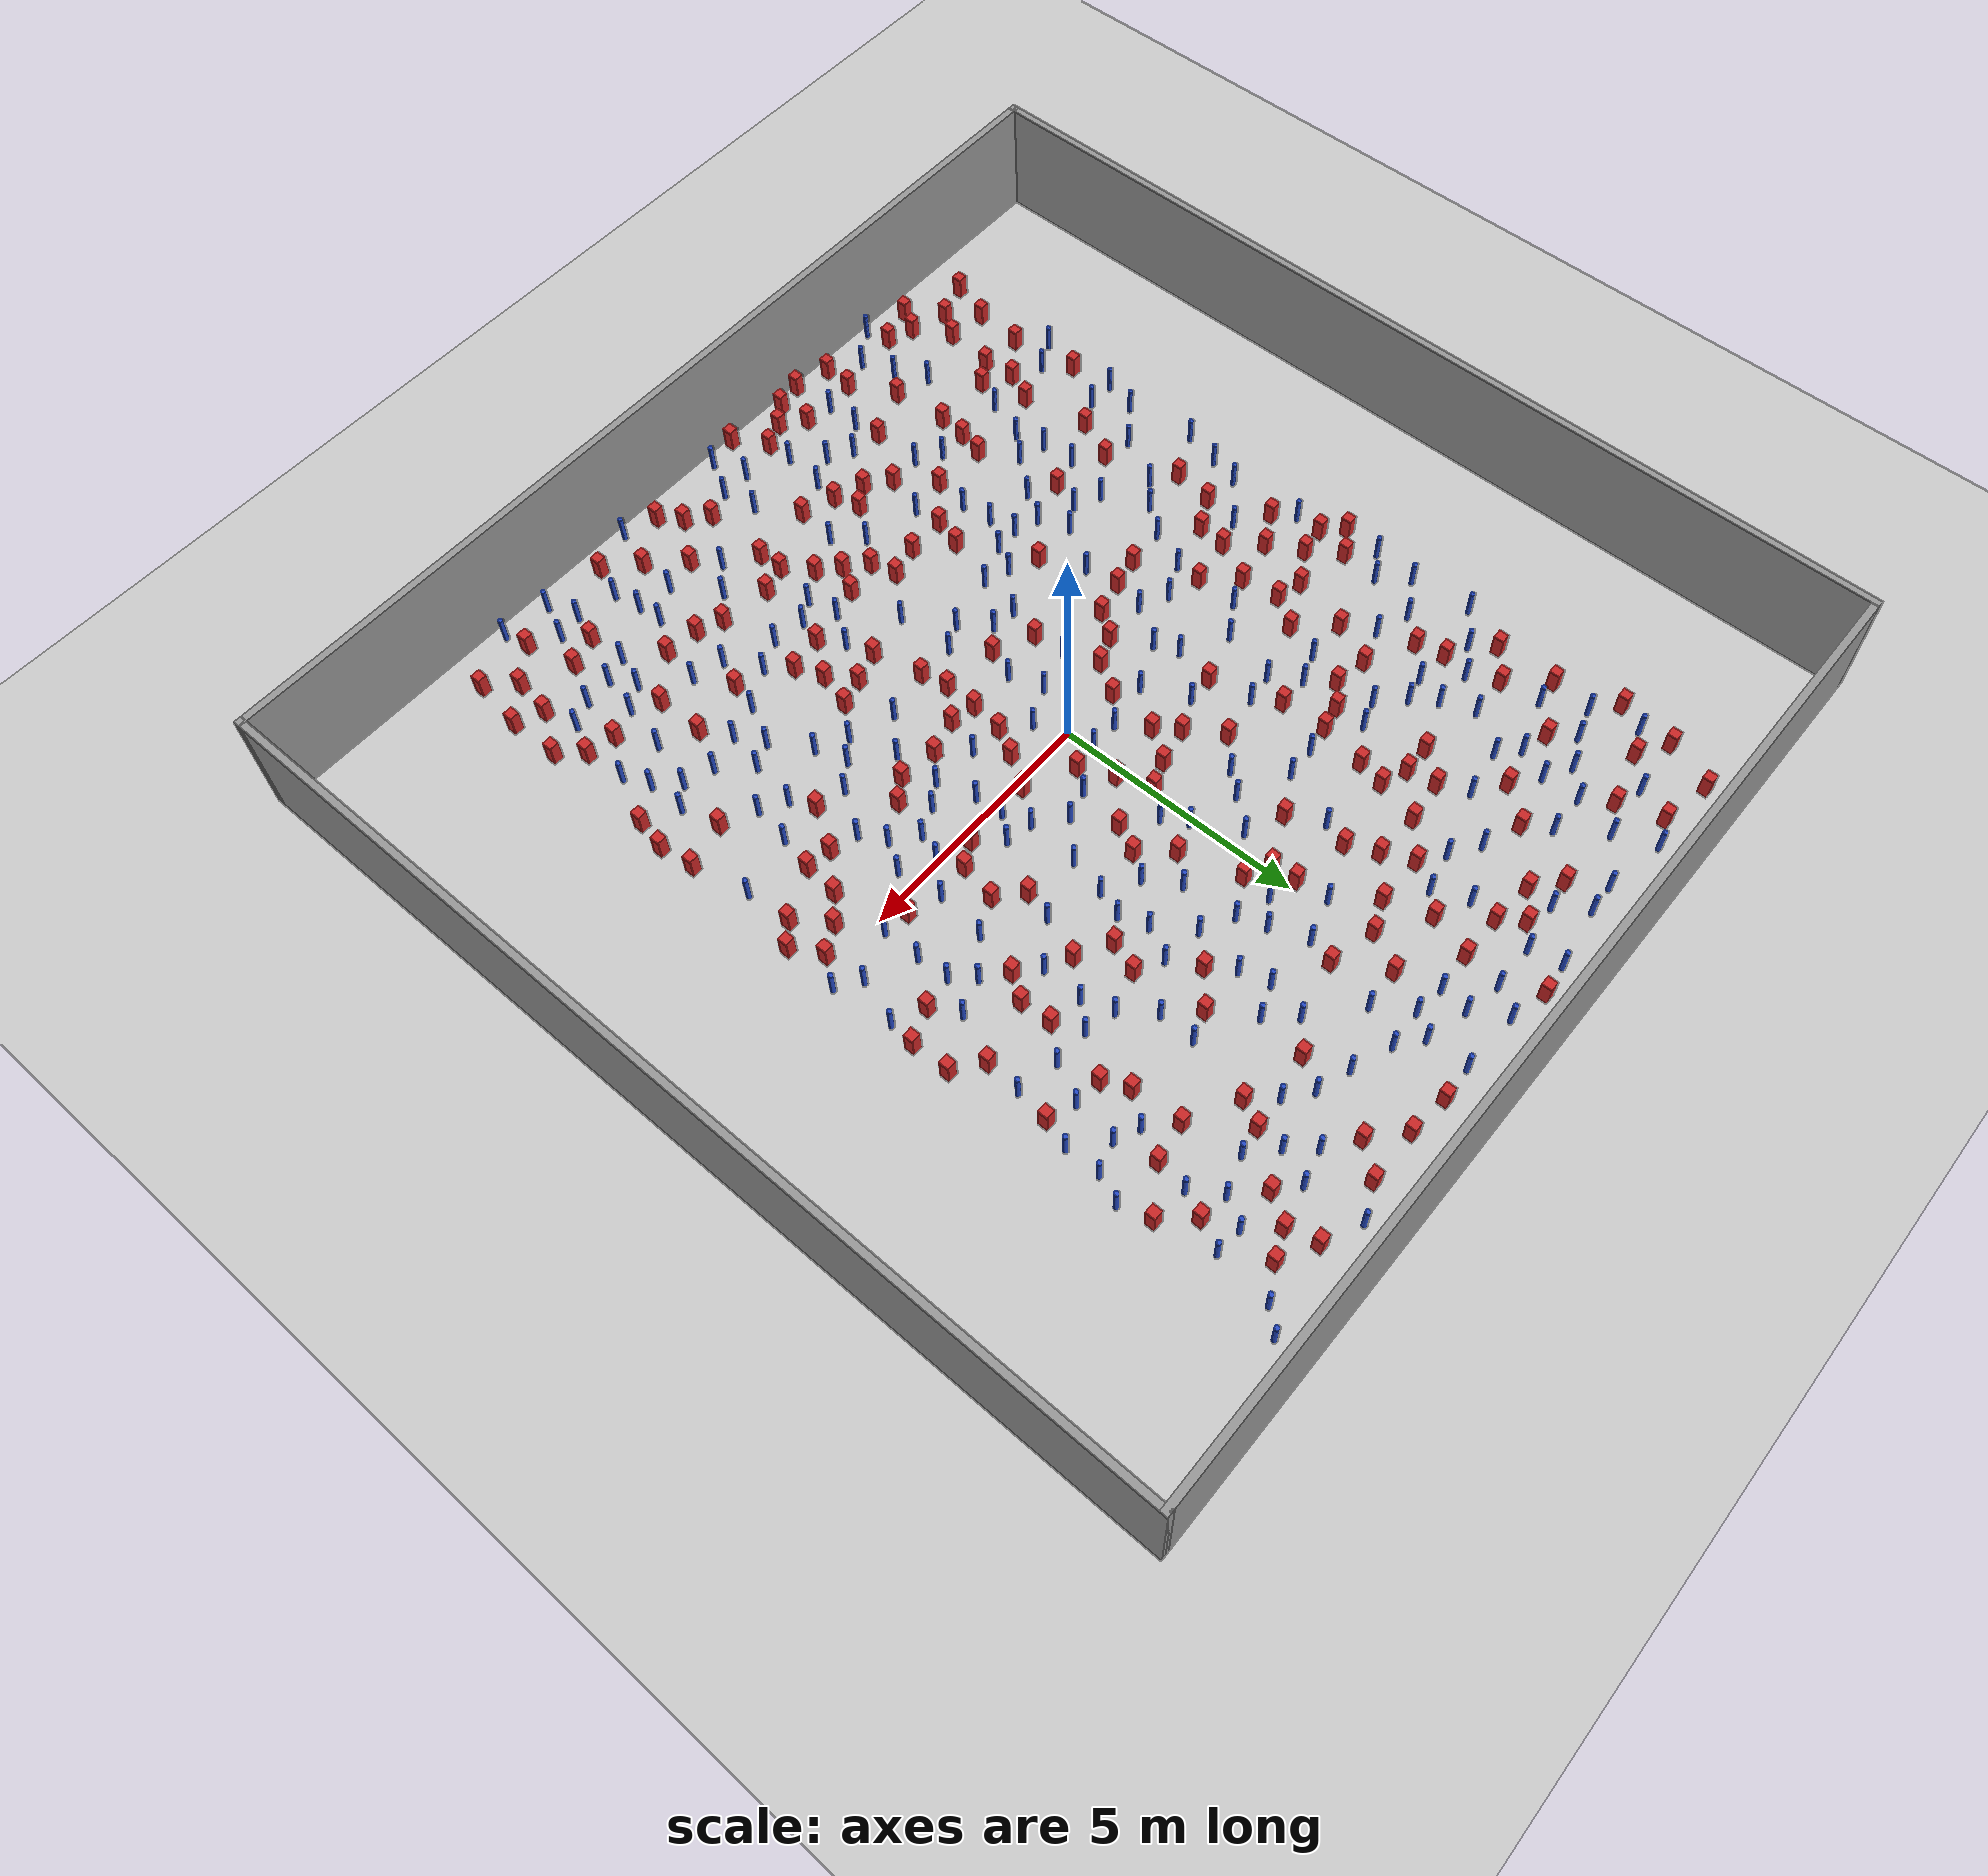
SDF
<sdf version="1.6">
 <world name="default">
  <light name="sun" type="directional">
   <pose>0 0 1000 0 -0 0</pose>
   <diffuse>0.8 0.8 0.8 1</diffuse>
   <specular>0.1 0.1 0.1 1</specular>
   <attenuation>
    <range>1000</range>
    <constant>0.9</constant>
    <linear>0.01</linear>
    <quadratic>0.001</quadratic>
   </attenuation>
   <direction>-0.5 0.5 -1</direction>
  </light>
  <model name="ground_plane">
   <static>1</static>
   <link name="link">
    <collision name="collision">
     <geometry><plane><normal>0 0 1</normal><size>100 100</size></plane></geometry>
     <surface><friction><ode><mu>100</mu><mu2>50</mu2></ode></friction></surface>
    </collision>
    <visual name="visual">
     <cast_shadows>0</cast_shadows>
     <geometry><plane><normal>0 0 1</normal><size>100 100</size></plane></geometry>
     <material>
      <ambient>1.0 1.0 1.0 1.0</ambient>
      <diffuse>0.8 0.8 0.8 1.0</diffuse>
      <specular>0.01 0.01 0.01 1.000000</specular>
     </material>
    </visual>
   </link>
  </model>
  <gravity>0 0 -9.8</gravity>
  <magnetic_field>6e-06 2.3e-05 -4.2e-05</magnetic_field>
  <atmosphere type="adiabatic"/>
  <physics name="default_physics" default="0" type="ode">
   <max_step_size>0.001</max_step_size>
   <real_time_factor>1</real_time_factor>
   <real_time_update_rate>1000</real_time_update_rate>
  </physics>
  <scene><ambient>0.4 0.4 0.4 1</ambient><background>0.7 0.7 0.7 1</background><shadows>1</shadows></scene>
  <spherical_coordinates>
   <surface_model>EARTH_WGS84</surface_model>
   <latitude_deg>0</latitude_deg>
   <longitude_deg>0</longitude_deg>
   <elevation>0</elevation>
   <heading_deg>0</heading_deg>
  </spherical_coordinates>
  <plugin name="gazebo_occupancy_map" filename="libgazebo_2Dmap_plugin.so">
   <map_resolution>0.05</map_resolution>
   <map_topic>generated_map</map_topic>
   <map_height>0.01</map_height>
   <map_size_x>50</map_size_x>
   <map_size_y>50</map_size_y>
  </plugin>
  <model name="NamedLocations">
   <static>true</static>
   <link name="DefaultStart"><pose>8.5 0 0 0 0 3.14</pose></link>
  </model>
  <model name="20x20_walls">
   <pose>0.044518 0.176112 0 0 -0 0</pose>
   <link name="Wall_1">
    <collision name="Wall_1_Collision">
     <geometry><box><size>20 0.15 2.5</size></box></geometry>
     <pose>0 0 1.25 0 -0 0</pose>
    </collision>
    <visual name="Wall_1_Visual">
     <pose>0 0 1.25 0 -0 0</pose>
     <geometry><box><size>20 0.15 2.5</size></box></geometry>
     <material>
      <script><uri>file://media/materials/scripts/gazebo.material</uri><name>Gazebo/Grey</name></script>
      <ambient>0.976471 0.992157 1 1</ambient>
     </material>
     <meta><layer>0</layer></meta>
    </visual>
    <pose>0 9.925 0 0 -0 0</pose>
   </link>
   <link name="Wall_3">
    <collision name="Wall_3_Collision">
     <geometry><box><size>20 0.15 2.5</size></box></geometry>
     <pose>0 0 1.25 0 -0 0</pose>
    </collision>
    <visual name="Wall_3_Visual">
     <pose>0 0 1.25 0 -0 0</pose>
     <geometry><box><size>20 0.15 2.5</size></box></geometry>
     <material>
      <script><uri>file://media/materials/scripts/gazebo.material</uri><name>Gazebo/Grey</name></script>
      <ambient>0.976471 0.992157 1 1</ambient>
     </material>
     <meta><layer>0</layer></meta>
    </visual>
    <pose>9.925 0 0 0 0 -1.5708</pose>
   </link>
   <link name="Wall_4">
    <collision name="Wall_4_Collision">
     <geometry><box><size>20 0.15 2.5</size></box></geometry>
     <pose>0 0 1.25 0 -0 0</pose>
    </collision>
    <visual name="Wall_4_Visual">
     <pose>0 0 1.25 0 -0 0</pose>
     <geometry><box><size>20 0.15 2.5</size></box></geometry>
     <material>
      <script><uri>file://media/materials/scripts/gazebo.material</uri><name>Gazebo/Grey</name></script>
      <ambient>0.976471 0.992157 1 1</ambient>
     </material>
     <meta><layer>0</layer></meta>
    </visual>
    <pose>0 -9.925 0 0 -0 3.14159</pose>
   </link>
   <link name="Wall_5">
    <collision name="Wall_5_Collision">
     <geometry><box><size>20 0.15 2.5</size></box></geometry>
     <pose>0 0 1.25 0 -0 0</pose>
    </collision>
    <visual name="Wall_5_Visual">
     <pose>0 0 1.25 0 -0 0</pose>
     <geometry><box><size>20 0.15 2.5</size></box></geometry>
     <material>
      <script><uri>file://media/materials/scripts/gazebo.material</uri><name>Gazebo/Grey</name></script>
      <ambient>0.976471 0.992157 1 1</ambient>
     </material>
     <meta><layer>0</layer></meta>
    </visual>
    <pose>-9.925 0 0 0 -0 1.5708</pose>
   </link>
   <static>1</static>
  </model>
  <model name="square_post_obstacle0">
   <static>true</static>
   <pose>0.239393074724 -5.11633547202 1.91545236811e-07 -7.35059704564e-06 1.12565212e-07 2.39332434364e-05</pose>
   <link name="link">
    <pose>0 0 0.25 0 -0 0</pose>
    <inertial>
     <mass>100</mass>
     <inertia>
      <ixx>0.166667</ixx>
      <ixy>0</ixy>
      <ixz>0</ixz>
      <iyy>0.166667</iyy>
      <iyz>0</iyz>
      <izz>0.166667</izz>
     </inertia>
    </inertial>
    <collision name="collision"><geometry><box><size>.2 .2 .5</size></box></geometry></collision>
    <visual name="visual">
     <geometry><box><size>.2 .2 .5</size></box></geometry>
     <material>
      <script><name>Gazebo/Red</name><uri>file://media/materials/scripts/gazebo.material</uri></script>
     </material>
    </visual>
   </link>
  </model>
  <model name="square_post_obstacle1">
   <static>true</static>
   <pose>-4.05406104011 -6.65313392118 1.91545236811e-07 -7.35059704564e-06 1.12565212e-07 2.39332434364e-05</pose>
   <link name="link">
    <pose>0 0 0.25 0 -0 0</pose>
    <inertial>
     <mass>100</mass>
     <inertia>
      <ixx>0.166667</ixx>
      <ixy>0</ixy>
      <ixz>0</ixz>
      <iyy>0.166667</iyy>
      <iyz>0</iyz>
      <izz>0.166667</izz>
     </inertia>
    </inertial>
    <collision name="collision"><geometry><box><size>.2 .2 .5</size></box></geometry></collision>
    <visual name="visual">
     <geometry><box><size>.2 .2 .5</size></box></geometry>
     <material>
      <script><name>Gazebo/Red</name><uri>file://media/materials/scripts/gazebo.material</uri></script>
     </material>
    </visual>
   </link>
  </model>
  <model name="pole_obstacle0">
   <static>true</static>
   <pose>-3.84530222846 7.86283528146 7.38925637345e-09 -8.47170692798e-08 1.24976765033e-08 -1.74513093019e-07</pose>
   <link name="link">
    <pose>0 0 0.3 0 -0 0</pose>
    <inertial>
     <mass>1</mass>
     <inertia><ixx>0.145833</ixx><ixy>0</ixy><ixz>0</ixz><iyy>0.145833</iyy><iyz>0</iyz><izz>0.125</izz></inertia>
    </inertial>
    <collision name="collision">
     <geometry><cylinder><radius>0.05</radius><length>.6</length></cylinder></geometry>
    </collision>
    <visual name="visual">
     <geometry><cylinder><radius>0.05</radius><length>.6</length></cylinder></geometry>
     <material>
      <script><name>Gazebo/Blue</name><uri>file://media/materials/scripts/gazebo.material</uri></script>
     </material>
    </visual>
   </link>
  </model>
  <model name="square_post_obstacle2">
   <static>true</static>
   <pose>-5.86951627171 5.40197171694 1.91545236811e-07 -7.35059704564e-06 1.12565212e-07 2.39332434364e-05</pose>
   <link name="link">
    <pose>0 0 0.25 0 -0 0</pose>
    <inertial>
     <mass>100</mass>
     <inertia>
      <ixx>0.166667</ixx>
      <ixy>0</ixy>
      <ixz>0</ixz>
      <iyy>0.166667</iyy>
      <iyz>0</iyz>
      <izz>0.166667</izz>
     </inertia>
    </inertial>
    <collision name="collision"><geometry><box><size>.2 .2 .5</size></box></geometry></collision>
    <visual name="visual">
     <geometry><box><size>.2 .2 .5</size></box></geometry>
     <material>
      <script><name>Gazebo/Red</name><uri>file://media/materials/scripts/gazebo.material</uri></script>
     </material>
    </visual>
   </link>
  </model>
  <model name="pole_obstacle1">
   <static>true</static>
   <pose>3.98084149001 3.61252050977 7.38925637345e-09 -8.47170692796e-08 1.24976764765e-08 -1.74513093035e-07</pose>
   <link name="link">
    <pose>0 0 0.3 0 -0 0</pose>
    <inertial>
     <mass>1</mass>
     <inertia><ixx>0.145833</ixx><ixy>0</ixy><ixz>0</ixz><iyy>0.145833</iyy><iyz>0</iyz><izz>0.125</izz></inertia>
    </inertial>
    <collision name="collision">
     <geometry><cylinder><radius>0.05</radius><length>.6</length></cylinder></geometry>
    </collision>
    <visual name="visual">
     <geometry><cylinder><radius>0.05</radius><length>.6</length></cylinder></geometry>
     <material>
      <script><name>Gazebo/Blue</name><uri>file://media/materials/scripts/gazebo.material</uri></script>
     </material>
    </visual>
   </link>
  </model>
  <model name="square_post_obstacle3">
   <static>true</static>
   <pose>-4.62492804359 3.22909375096 1.91545236811e-07 -7.35059704564e-06 1.12565212e-07 2.39332434364e-05</pose>
   <link name="link">
    <pose>0 0 0.25 0 -0 0</pose>
    <inertial>
     <mass>100</mass>
     <inertia>
      <ixx>0.166667</ixx>
      <ixy>0</ixy>
      <ixz>0</ixz>
      <iyy>0.166667</iyy>
      <iyz>0</iyz>
      <izz>0.166667</izz>
     </inertia>
    </inertial>
    <collision name="collision"><geometry><box><size>.2 .2 .5</size></box></geometry></collision>
    <visual name="visual">
     <geometry><box><size>.2 .2 .5</size></box></geometry>
     <material>
      <script><name>Gazebo/Red</name><uri>file://media/materials/scripts/gazebo.material</uri></script>
     </material>
    </visual>
   </link>
  </model>
  <model name="pole_obstacle2">
   <static>true</static>
   <pose>3.5081300478 -2.21266276407 7.38925637345e-09 -8.47170692798e-08 1.24976764939e-08 -1.74513093025e-07</pose>
   <link name="link">
    <pose>0 0 0.3 0 -0 0</pose>
    <inertial>
     <mass>1</mass>
     <inertia><ixx>0.145833</ixx><ixy>0</ixy><ixz>0</ixz><iyy>0.145833</iyy><iyz>0</iyz><izz>0.125</izz></inertia>
    </inertial>
    <collision name="collision">
     <geometry><cylinder><radius>0.05</radius><length>.6</length></cylinder></geometry>
    </collision>
    <visual name="visual">
     <geometry><cylinder><radius>0.05</radius><length>.6</length></cylinder></geometry>
     <material>
      <script><name>Gazebo/Blue</name><uri>file://media/materials/scripts/gazebo.material</uri></script>
     </material>
    </visual>
   </link>
  </model>
  <model name="pole_obstacle3">
   <static>true</static>
   <pose>5.4384488271 2.29469536156 7.38925637345e-09 -8.47170692798e-08 1.24976764937e-08 -1.74513093023e-07</pose>
   <link name="link">
    <pose>0 0 0.3 0 -0 0</pose>
    <inertial>
     <mass>1</mass>
     <inertia><ixx>0.145833</ixx><ixy>0</ixy><ixz>0</ixz><iyy>0.145833</iyy><iyz>0</iyz><izz>0.125</izz></inertia>
    </inertial>
    <collision name="collision">
     <geometry><cylinder><radius>0.05</radius><length>.6</length></cylinder></geometry>
    </collision>
    <visual name="visual">
     <geometry><cylinder><radius>0.05</radius><length>.6</length></cylinder></geometry>
     <material>
      <script><name>Gazebo/Blue</name><uri>file://media/materials/scripts/gazebo.material</uri></script>
     </material>
    </visual>
   </link>
  </model>
  <model name="square_post_obstacle4">
   <static>true</static>
   <pose>-3.54028163449 7.36782610816 1.91545236811e-07 -7.35059704564e-06 1.12565212e-07 2.39332434364e-05</pose>
   <link name="link">
    <pose>0 0 0.25 0 -0 0</pose>
    <inertial>
     <mass>100</mass>
     <inertia>
      <ixx>0.166667</ixx>
      <ixy>0</ixy>
      <ixz>0</ixz>
      <iyy>0.166667</iyy>
      <iyz>0</iyz>
      <izz>0.166667</izz>
     </inertia>
    </inertial>
    <collision name="collision"><geometry><box><size>.2 .2 .5</size></box></geometry></collision>
    <visual name="visual">
     <geometry><box><size>.2 .2 .5</size></box></geometry>
     <material>
      <script><name>Gazebo/Red</name><uri>file://media/materials/scripts/gazebo.material</uri></script>
     </material>
    </visual>
   </link>
  </model>
  <model name="square_post_obstacle5">
   <static>true</static>
   <pose>0.736631532644 3.10345573629 1.91545236811e-07 -7.35059704564e-06 1.12565212e-07 2.39332434364e-05</pose>
   <link name="link">
    <pose>0 0 0.25 0 -0 0</pose>
    <inertial>
     <mass>100</mass>
     <inertia>
      <ixx>0.166667</ixx>
      <ixy>0</ixy>
      <ixz>0</ixz>
      <iyy>0.166667</iyy>
      <iyz>0</iyz>
      <izz>0.166667</izz>
     </inertia>
    </inertial>
    <collision name="collision"><geometry><box><size>.2 .2 .5</size></box></geometry></collision>
    <visual name="visual">
     <geometry><box><size>.2 .2 .5</size></box></geometry>
     <material>
      <script><name>Gazebo/Red</name><uri>file://media/materials/scripts/gazebo.material</uri></script>
     </material>
    </visual>
   </link>
  </model>
  <model name="square_post_obstacle6">
   <static>true</static>
   <pose>-6.58836928079 -6.93596378803 1.91545236811e-07 -7.35059704564e-06 1.12565212e-07 2.39332434364e-05</pose>
   <link name="link">
    <pose>0 0 0.25 0 -0 0</pose>
    <inertial>
     <mass>100</mass>
     <inertia>
      <ixx>0.166667</ixx>
      <ixy>0</ixy>
      <ixz>0</ixz>
      <iyy>0.166667</iyy>
      <iyz>0</iyz>
      <izz>0.166667</izz>
     </inertia>
    </inertial>
    <collision name="collision"><geometry><box><size>.2 .2 .5</size></box></geometry></collision>
    <visual name="visual">
     <geometry><box><size>.2 .2 .5</size></box></geometry>
     <material>
      <script><name>Gazebo/Red</name><uri>file://media/materials/scripts/gazebo.material</uri></script>
     </material>
    </visual>
   </link>
  </model>
  <model name="pole_obstacle4">
   <static>true</static>
   <pose>-6.37288172912 6.97094230461 7.38925637345e-09 -8.47170692796e-08 1.24976764786e-08 -1.74513093032e-07</pose>
   <link name="link">
    <pose>0 0 0.3 0 -0 0</pose>
    <inertial>
     <mass>1</mass>
     <inertia><ixx>0.145833</ixx><ixy>0</ixy><ixz>0</ixz><iyy>0.145833</iyy><iyz>0</iyz><izz>0.125</izz></inertia>
    </inertial>
    <collision name="collision">
     <geometry><cylinder><radius>0.05</radius><length>.6</length></cylinder></geometry>
    </collision>
    <visual name="visual">
     <geometry><cylinder><radius>0.05</radius><length>.6</length></cylinder></geometry>
     <material>
      <script><name>Gazebo/Blue</name><uri>file://media/materials/scripts/gazebo.material</uri></script>
     </material>
    </visual>
   </link>
  </model>
  <model name="pole_obstacle5">
   <static>true</static>
   <pose>-4.64841601133 7.85120983062 7.38925637345e-09 -8.47170692796e-08 1.24976764786e-08 -1.74513093032e-07</pose>
   <link name="link">
    <pose>0 0 0.3 0 -0 0</pose>
    <inertial>
     <mass>1</mass>
     <inertia><ixx>0.145833</ixx><ixy>0</ixy><ixz>0</ixz><iyy>0.145833</iyy><iyz>0</iyz><izz>0.125</izz></inertia>
    </inertial>
    <collision name="collision">
     <geometry><cylinder><radius>0.05</radius><length>.6</length></cylinder></geometry>
    </collision>
    <visual name="visual">
     <geometry><cylinder><radius>0.05</radius><length>.6</length></cylinder></geometry>
     <material>
      <script><name>Gazebo/Blue</name><uri>file://media/materials/scripts/gazebo.material</uri></script>
     </material>
    </visual>
   </link>
  </model>
  <model name="square_post_obstacle7">
   <static>true</static>
   <pose>5.44725526189 -3.38446065969 1.91545236811e-07 -7.35059704564e-06 1.12565212e-07 2.39332434364e-05</pose>
   <link name="link">
    <pose>0 0 0.25 0 -0 0</pose>
    <inertial>
     <mass>100</mass>
     <inertia>
      <ixx>0.166667</ixx>
      <ixy>0</ixy>
      <ixz>0</ixz>
      <iyy>0.166667</iyy>
      <iyz>0</iyz>
      <izz>0.166667</izz>
     </inertia>
    </inertial>
    <collision name="collision"><geometry><box><size>.2 .2 .5</size></box></geometry></collision>
    <visual name="visual">
     <geometry><box><size>.2 .2 .5</size></box></geometry>
     <material>
      <script><name>Gazebo/Red</name><uri>file://media/materials/scripts/gazebo.material</uri></script>
     </material>
    </visual>
   </link>
  </model>
  <model name="square_post_obstacle8">
   <static>true</static>
   <pose>4.5720733056 -1.5507630868 1.91545236811e-07 -7.35059704564e-06 1.12565212e-07 2.39332434364e-05</pose>
   <link name="link">
    <pose>0 0 0.25 0 -0 0</pose>
    <inertial>
     <mass>100</mass>
     <inertia>
      <ixx>0.166667</ixx>
      <ixy>0</ixy>
      <ixz>0</ixz>
      <iyy>0.166667</iyy>
      <iyz>0</iyz>
      <izz>0.166667</izz>
     </inertia>
    </inertial>
    <collision name="collision"><geometry><box><size>.2 .2 .5</size></box></geometry></collision>
    <visual name="visual">
     <geometry><box><size>.2 .2 .5</size></box></geometry>
     <material>
      <script><name>Gazebo/Red</name><uri>file://media/materials/scripts/gazebo.material</uri></script>
     </material>
    </visual>
   </link>
  </model>
  <model name="pole_obstacle6">
   <static>true</static>
   <pose>6.08817874194 9.12009369706 7.38925637345e-09 -8.471706928e-08 1.24976765081e-08 -1.74513093015e-07</pose>
   <link name="link">
    <pose>0 0 0.3 0 -0 0</pose>
    <inertial>
     <mass>1</mass>
     <inertia><ixx>0.145833</ixx><ixy>0</ixy><ixz>0</ixz><iyy>0.145833</iyy><iyz>0</iyz><izz>0.125</izz></inertia>
    </inertial>
    <collision name="collision">
     <geometry><cylinder><radius>0.05</radius><length>.6</length></cylinder></geometry>
    </collision>
    <visual name="visual">
     <geometry><cylinder><radius>0.05</radius><length>.6</length></cylinder></geometry>
     <material>
      <script><name>Gazebo/Blue</name><uri>file://media/materials/scripts/gazebo.material</uri></script>
     </material>
    </visual>
   </link>
  </model>
  <model name="pole_obstacle7">
   <static>true</static>
   <pose>-5.98293886818 -3.4617956946 7.38925637345e-09 -8.47170692798e-08 1.24976764937e-08 -1.74513093023e-07</pose>
   <link name="link">
    <pose>0 0 0.3 0 -0 0</pose>
    <inertial>
     <mass>1</mass>
     <inertia><ixx>0.145833</ixx><ixy>0</ixy><ixz>0</ixz><iyy>0.145833</iyy><iyz>0</iyz><izz>0.125</izz></inertia>
    </inertial>
    <collision name="collision">
     <geometry><cylinder><radius>0.05</radius><length>.6</length></cylinder></geometry>
    </collision>
    <visual name="visual">
     <geometry><cylinder><radius>0.05</radius><length>.6</length></cylinder></geometry>
     <material>
      <script><name>Gazebo/Blue</name><uri>file://media/materials/scripts/gazebo.material</uri></script>
     </material>
    </visual>
   </link>
  </model>
  <model name="square_post_obstacle9">
   <static>true</static>
   <pose>-2.40668371716 -1.18963300212 1.91545236811e-07 -7.35059704564e-06 1.12565212e-07 2.39332434364e-05</pose>
   <link name="link">
    <pose>0 0 0.25 0 -0 0</pose>
    <inertial>
     <mass>100</mass>
     <inertia>
      <ixx>0.166667</ixx>
      <ixy>0</ixy>
      <ixz>0</ixz>
      <iyy>0.166667</iyy>
      <iyz>0</iyz>
      <izz>0.166667</izz>
     </inertia>
    </inertial>
    <collision name="collision"><geometry><box><size>.2 .2 .5</size></box></geometry></collision>
    <visual name="visual">
     <geometry><box><size>.2 .2 .5</size></box></geometry>
     <material>
      <script><name>Gazebo/Red</name><uri>file://media/materials/scripts/gazebo.material</uri></script>
     </material>
    </visual>
   </link>
  </model>
  <model name="square_post_obstacle10">
   <static>true</static>
   <pose>0.801643969608 -0.949715972117 1.91545236811e-07 -7.35059704564e-06 1.12565212e-07 2.39332434364e-05</pose>
   <link name="link">
    <pose>0 0 0.25 0 -0 0</pose>
    <inertial>
     <mass>100</mass>
     <inertia>
      <ixx>0.166667</ixx>
      <ixy>0</ixy>
      <ixz>0</ixz>
      <iyy>0.166667</iyy>
      <iyz>0</iyz>
      <izz>0.166667</izz>
     </inertia>
    </inertial>
    <collision name="collision"><geometry><box><size>.2 .2 .5</size></box></geometry></collision>
    <visual name="visual">
     <geometry><box><size>.2 .2 .5</size></box></geometry>
     <material>
      <script><name>Gazebo/Red</name><uri>file://media/materials/scripts/gazebo.material</uri></script>
     </material>
    </visual>
   </link>
  </model>
  <model name="square_post_obstacle11">
   <static>true</static>
   <pose>-2.98088389689 3.53646595872 1.91545236811e-07 -7.35059704564e-06 1.12565212e-07 2.39332434364e-05</pose>
   <link name="link">
    <pose>0 0 0.25 0 -0 0</pose>
    <inertial>
     <mass>100</mass>
     <inertia>
      <ixx>0.166667</ixx>
      <ixy>0</ixy>
      <ixz>0</ixz>
      <iyy>0.166667</iyy>
      <iyz>0</iyz>
      <izz>0.166667</izz>
     </inertia>
    </inertial>
    <collision name="collision"><geometry><box><size>.2 .2 .5</size></box></geometry></collision>
    <visual name="visual">
     <geometry><box><size>.2 .2 .5</size></box></geometry>
     <material>
      <script><name>Gazebo/Red</name><uri>file://media/materials/scripts/gazebo.material</uri></script>
     </material>
    </visual>
   </link>
  </model>
  <model name="square_post_obstacle12">
   <static>true</static>
   <pose>-0.810957576137 8.06785217845 1.91545236811e-07 -7.35059704564e-06 1.12565212e-07 2.39332434364e-05</pose>
   <link name="link">
    <pose>0 0 0.25 0 -0 0</pose>
    <inertial>
     <mass>100</mass>
     <inertia>
      <ixx>0.166667</ixx>
      <ixy>0</ixy>
      <ixz>0</ixz>
      <iyy>0.166667</iyy>
      <iyz>0</iyz>
      <izz>0.166667</izz>
     </inertia>
    </inertial>
    <collision name="collision"><geometry><box><size>.2 .2 .5</size></box></geometry></collision>
    <visual name="visual">
     <geometry><box><size>.2 .2 .5</size></box></geometry>
     <material>
      <script><name>Gazebo/Red</name><uri>file://media/materials/scripts/gazebo.material</uri></script>
     </material>
    </visual>
   </link>
  </model>
  <model name="square_post_obstacle13">
   <static>true</static>
   <pose>0.216439725768 7.31724826247 1.91545236811e-07 -7.35059704564e-06 1.12565212e-07 2.39332434364e-05</pose>
   <link name="link">
    <pose>0 0 0.25 0 -0 0</pose>
    <inertial>
     <mass>100</mass>
     <inertia>
      <ixx>0.166667</ixx>
      <ixy>0</ixy>
      <ixz>0</ixz>
      <iyy>0.166667</iyy>
      <iyz>0</iyz>
      <izz>0.166667</izz>
     </inertia>
    </inertial>
    <collision name="collision"><geometry><box><size>.2 .2 .5</size></box></geometry></collision>
    <visual name="visual">
     <geometry><box><size>.2 .2 .5</size></box></geometry>
     <material>
      <script><name>Gazebo/Red</name><uri>file://media/materials/scripts/gazebo.material</uri></script>
     </material>
    </visual>
   </link>
  </model>
  <model name="pole_obstacle8">
   <static>true</static>
   <pose>4.77809851453 2.05592720037 7.38925637345e-09 -8.47170692798e-08 1.24976764937e-08 -1.74513093023e-07</pose>
   <link name="link">
    <pose>0 0 0.3 0 -0 0</pose>
    <inertial>
     <mass>1</mass>
     <inertia><ixx>0.145833</ixx><ixy>0</ixy><ixz>0</ixz><iyy>0.145833</iyy><iyz>0</iyz><izz>0.125</izz></inertia>
    </inertial>
    <collision name="collision">
     <geometry><cylinder><radius>0.05</radius><length>.6</length></cylinder></geometry>
    </collision>
    <visual name="visual">
     <geometry><cylinder><radius>0.05</radius><length>.6</length></cylinder></geometry>
     <material>
      <script><name>Gazebo/Blue</name><uri>file://media/materials/scripts/gazebo.material</uri></script>
     </material>
    </visual>
   </link>
  </model>
  <model name="square_post_obstacle14">
   <static>true</static>
   <pose>5.66452522465 -8.27704746896 1.91545236811e-07 -7.35059704564e-06 1.12565212e-07 2.39332434364e-05</pose>
   <link name="link">
    <pose>0 0 0.25 0 -0 0</pose>
    <inertial>
     <mass>100</mass>
     <inertia>
      <ixx>0.166667</ixx>
      <ixy>0</ixy>
      <ixz>0</ixz>
      <iyy>0.166667</iyy>
      <iyz>0</iyz>
      <izz>0.166667</izz>
     </inertia>
    </inertial>
    <collision name="collision"><geometry><box><size>.2 .2 .5</size></box></geometry></collision>
    <visual name="visual">
     <geometry><box><size>.2 .2 .5</size></box></geometry>
     <material>
      <script><name>Gazebo/Red</name><uri>file://media/materials/scripts/gazebo.material</uri></script>
     </material>
    </visual>
   </link>
  </model>
  <model name="square_post_obstacle15">
   <static>true</static>
   <pose>-2.49304595082 1.27367761904 1.91545236811e-07 -7.35059704564e-06 1.12565212e-07 2.39332434364e-05</pose>
   <link name="link">
    <pose>0 0 0.25 0 -0 0</pose>
    <inertial>
     <mass>100</mass>
     <inertia>
      <ixx>0.166667</ixx>
      <ixy>0</ixy>
      <ixz>0</ixz>
      <iyy>0.166667</iyy>
      <iyz>0</iyz>
      <izz>0.166667</izz>
     </inertia>
    </inertial>
    <collision name="collision"><geometry><box><size>.2 .2 .5</size></box></geometry></collision>
    <visual name="visual">
     <geometry><box><size>.2 .2 .5</size></box></geometry>
     <material>
      <script><name>Gazebo/Red</name><uri>file://media/materials/scripts/gazebo.material</uri></script>
     </material>
    </visual>
   </link>
  </model>
  <model name="square_post_obstacle16">
   <static>true</static>
   <pose>5.34431540036 -6.13683487316 1.91545236811e-07 -7.35059704564e-06 1.12565212e-07 2.39332434364e-05</pose>
   <link name="link">
    <pose>0 0 0.25 0 -0 0</pose>
    <inertial>
     <mass>100</mass>
     <inertia>
      <ixx>0.166667</ixx>
      <ixy>0</ixy>
      <ixz>0</ixz>
      <iyy>0.166667</iyy>
      <iyz>0</iyz>
      <izz>0.166667</izz>
     </inertia>
    </inertial>
    <collision name="collision"><geometry><box><size>.2 .2 .5</size></box></geometry></collision>
    <visual name="visual">
     <geometry><box><size>.2 .2 .5</size></box></geometry>
     <material>
      <script><name>Gazebo/Red</name><uri>file://media/materials/scripts/gazebo.material</uri></script>
     </material>
    </visual>
   </link>
  </model>
  <model name="pole_obstacle9">
   <static>true</static>
   <pose>2.37202641082 -1.99833520378 7.38925637345e-09 -8.471706928e-08 1.249767651e-08 -1.74513093015e-07</pose>
   <link name="link">
    <pose>0 0 0.3 0 -0 0</pose>
    <inertial>
     <mass>1</mass>
     <inertia><ixx>0.145833</ixx><ixy>0</ixy><ixz>0</ixz><iyy>0.145833</iyy><iyz>0</iyz><izz>0.125</izz></inertia>
    </inertial>
    <collision name="collision">
     <geometry><cylinder><radius>0.05</radius><length>.6</length></cylinder></geometry>
    </collision>
    <visual name="visual">
     <geometry><cylinder><radius>0.05</radius><length>.6</length></cylinder></geometry>
     <material>
      <script><name>Gazebo/Blue</name><uri>file://media/materials/scripts/gazebo.material</uri></script>
     </material>
    </visual>
   </link>
  </model>
  <model name="square_post_obstacle17">
   <static>true</static>
   <pose>-5.63733042722 0.186093524573 1.91545236811e-07 -7.35059704564e-06 1.12565212e-07 2.39332434364e-05</pose>
   <link name="link">
    <pose>0 0 0.25 0 -0 0</pose>
    <inertial>
     <mass>100</mass>
     <inertia>
      <ixx>0.166667</ixx>
      <ixy>0</ixy>
      <ixz>0</ixz>
      <iyy>0.166667</iyy>
      <iyz>0</iyz>
      <izz>0.166667</izz>
     </inertia>
    </inertial>
    <collision name="collision"><geometry><box><size>.2 .2 .5</size></box></geometry></collision>
    <visual name="visual">
     <geometry><box><size>.2 .2 .5</size></box></geometry>
     <material>
      <script><name>Gazebo/Red</name><uri>file://media/materials/scripts/gazebo.material</uri></script>
     </material>
    </visual>
   </link>
  </model>
  <model name="square_post_obstacle18">
   <static>true</static>
   <pose>-4.1166179538 6.72472674113 1.91545236811e-07 -7.35059704564e-06 1.12565212e-07 2.39332434364e-05</pose>
   <link name="link">
    <pose>0 0 0.25 0 -0 0</pose>
    <inertial>
     <mass>100</mass>
     <inertia>
      <ixx>0.166667</ixx>
      <ixy>0</ixy>
      <ixz>0</ixz>
      <iyy>0.166667</iyy>
      <iyz>0</iyz>
      <izz>0.166667</izz>
     </inertia>
    </inertial>
    <collision name="collision"><geometry><box><size>.2 .2 .5</size></box></geometry></collision>
    <visual name="visual">
     <geometry><box><size>.2 .2 .5</size></box></geometry>
     <material>
      <script><name>Gazebo/Red</name><uri>file://media/materials/scripts/gazebo.material</uri></script>
     </material>
    </visual>
   </link>
  </model>
  <model name="pole_obstacle10">
   <static>true</static>
   <pose>1.70992750119 4.33603272903 7.38925637345e-09 -8.47170692799e-08 1.24976765033e-08 -1.74513093018e-07</pose>
   <link name="link">
    <pose>0 0 0.3 0 -0 0</pose>
    <inertial>
     <mass>1</mass>
     <inertia><ixx>0.145833</ixx><ixy>0</ixy><ixz>0</ixz><iyy>0.145833</iyy><iyz>0</iyz><izz>0.125</izz></inertia>
    </inertial>
    <collision name="collision">
     <geometry><cylinder><radius>0.05</radius><length>.6</length></cylinder></geometry>
    </collision>
    <visual name="visual">
     <geometry><cylinder><radius>0.05</radius><length>.6</length></cylinder></geometry>
     <material>
      <script><name>Gazebo/Blue</name><uri>file://media/materials/scripts/gazebo.material</uri></script>
     </material>
    </visual>
   </link>
  </model>
  <model name="square_post_obstacle19">
   <static>true</static>
   <pose>4.62734859927 6.2608275245 1.91545236811e-07 -7.35059704564e-06 1.12565212e-07 2.39332434364e-05</pose>
   <link name="link">
    <pose>0 0 0.25 0 -0 0</pose>
    <inertial>
     <mass>100</mass>
     <inertia>
      <ixx>0.166667</ixx>
      <ixy>0</ixy>
      <ixz>0</ixz>
      <iyy>0.166667</iyy>
      <iyz>0</iyz>
      <izz>0.166667</izz>
     </inertia>
    </inertial>
    <collision name="collision"><geometry><box><size>.2 .2 .5</size></box></geometry></collision>
    <visual name="visual">
     <geometry><box><size>.2 .2 .5</size></box></geometry>
     <material>
      <script><name>Gazebo/Red</name><uri>file://media/materials/scripts/gazebo.material</uri></script>
     </material>
    </visual>
   </link>
  </model>
  <model name="pole_obstacle11">
   <static>true</static>
   <pose>1.08762359171 4.64439114261 7.38925637345e-09 -8.47170692799e-08 1.24976765033e-08 -1.74513093018e-07</pose>
   <link name="link">
    <pose>0 0 0.3 0 -0 0</pose>
    <inertial>
     <mass>1</mass>
     <inertia><ixx>0.145833</ixx><ixy>0</ixy><ixz>0</ixz><iyy>0.145833</iyy><iyz>0</iyz><izz>0.125</izz></inertia>
    </inertial>
    <collision name="collision">
     <geometry><cylinder><radius>0.05</radius><length>.6</length></cylinder></geometry>
    </collision>
    <visual name="visual">
     <geometry><cylinder><radius>0.05</radius><length>.6</length></cylinder></geometry>
     <material>
      <script><name>Gazebo/Blue</name><uri>file://media/materials/scripts/gazebo.material</uri></script>
     </material>
    </visual>
   </link>
  </model>
  <model name="square_post_obstacle20">
   <static>true</static>
   <pose>4.28876861676 -5.07236767864 1.91545236811e-07 -7.35059704564e-06 1.12565212e-07 2.39332434364e-05</pose>
   <link name="link">
    <pose>0 0 0.25 0 -0 0</pose>
    <inertial>
     <mass>100</mass>
     <inertia>
      <ixx>0.166667</ixx>
      <ixy>0</ixy>
      <ixz>0</ixz>
      <iyy>0.166667</iyy>
      <iyz>0</iyz>
      <izz>0.166667</izz>
     </inertia>
    </inertial>
    <collision name="collision"><geometry><box><size>.2 .2 .5</size></box></geometry></collision>
    <visual name="visual">
     <geometry><box><size>.2 .2 .5</size></box></geometry>
     <material>
      <script><name>Gazebo/Red</name><uri>file://media/materials/scripts/gazebo.material</uri></script>
     </material>
    </visual>
   </link>
  </model>
  <model name="pole_obstacle12">
   <static>true</static>
   <pose>3.25595772131 7.2266986002 7.38925637345e-09 -8.47170692798e-08 1.24976765033e-08 -1.74513093019e-07</pose>
   <link name="link">
    <pose>0 0 0.3 0 -0 0</pose>
    <inertial>
     <mass>1</mass>
     <inertia><ixx>0.145833</ixx><ixy>0</ixy><ixz>0</ixz><iyy>0.145833</iyy><iyz>0</iyz><izz>0.125</izz></inertia>
    </inertial>
    <collision name="collision">
     <geometry><cylinder><radius>0.05</radius><length>.6</length></cylinder></geometry>
    </collision>
    <visual name="visual">
     <geometry><cylinder><radius>0.05</radius><length>.6</length></cylinder></geometry>
     <material>
      <script><name>Gazebo/Blue</name><uri>file://media/materials/scripts/gazebo.material</uri></script>
     </material>
    </visual>
   </link>
  </model>
  <model name="square_post_obstacle21">
   <static>true</static>
   <pose>-6.49076639367 4.93805852814 1.91545236811e-07 -7.35059704564e-06 1.12565212e-07 2.39332434364e-05</pose>
   <link name="link">
    <pose>0 0 0.25 0 -0 0</pose>
    <inertial>
     <mass>100</mass>
     <inertia>
      <ixx>0.166667</ixx>
      <ixy>0</ixy>
      <ixz>0</ixz>
      <iyy>0.166667</iyy>
      <iyz>0</iyz>
      <izz>0.166667</izz>
     </inertia>
    </inertial>
    <collision name="collision"><geometry><box><size>.2 .2 .5</size></box></geometry></collision>
    <visual name="visual">
     <geometry><box><size>.2 .2 .5</size></box></geometry>
     <material>
      <script><name>Gazebo/Red</name><uri>file://media/materials/scripts/gazebo.material</uri></script>
     </material>
    </visual>
   </link>
  </model>
  <model name="pole_obstacle13">
   <static>true</static>
   <pose>-4.3625713466 -8.25112892391 7.38925637345e-09 -8.471706928e-08 1.24976765081e-08 -1.74513093015e-07</pose>
   <link name="link">
    <pose>0 0 0.3 0 -0 0</pose>
    <inertial>
     <mass>1</mass>
     <inertia><ixx>0.145833</ixx><ixy>0</ixy><ixz>0</ixz><iyy>0.145833</iyy><iyz>0</iyz><izz>0.125</izz></inertia>
    </inertial>
    <collision name="collision">
     <geometry><cylinder><radius>0.05</radius><length>.6</length></cylinder></geometry>
    </collision>
    <visual name="visual">
     <geometry><cylinder><radius>0.05</radius><length>.6</length></cylinder></geometry>
     <material>
      <script><name>Gazebo/Blue</name><uri>file://media/materials/scripts/gazebo.material</uri></script>
     </material>
    </visual>
   </link>
  </model>
  <model name="square_post_obstacle22">
   <static>true</static>
   <pose>-3.28676451657 5.75782456899 1.91545236811e-07 -7.35059704564e-06 1.12565212e-07 2.39332434364e-05</pose>
   <link name="link">
    <pose>0 0 0.25 0 -0 0</pose>
    <inertial>
     <mass>100</mass>
     <inertia>
      <ixx>0.166667</ixx>
      <ixy>0</ixy>
      <ixz>0</ixz>
      <iyy>0.166667</iyy>
      <iyz>0</iyz>
      <izz>0.166667</izz>
     </inertia>
    </inertial>
    <collision name="collision"><geometry><box><size>.2 .2 .5</size></box></geometry></collision>
    <visual name="visual">
     <geometry><box><size>.2 .2 .5</size></box></geometry>
     <material>
      <script><name>Gazebo/Red</name><uri>file://media/materials/scripts/gazebo.material</uri></script>
     </material>
    </visual>
   </link>
  </model>
  <model name="pole_obstacle14">
   <static>true</static>
   <pose>5.45333666185 4.74273611166 7.38925637345e-09 -8.47170692796e-08 1.24976764786e-08 -1.74513093032e-07</pose>
   <link name="link">
    <pose>0 0 0.3 0 -0 0</pose>
    <inertial>
     <mass>1</mass>
     <inertia><ixx>0.145833</ixx><ixy>0</ixy><ixz>0</ixz><iyy>0.145833</iyy><iyz>0</iyz><izz>0.125</izz></inertia>
    </inertial>
    <collision name="collision">
     <geometry><cylinder><radius>0.05</radius><length>.6</length></cylinder></geometry>
    </collision>
    <visual name="visual">
     <geometry><cylinder><radius>0.05</radius><length>.6</length></cylinder></geometry>
     <material>
      <script><name>Gazebo/Blue</name><uri>file://media/materials/scripts/gazebo.material</uri></script>
     </material>
    </visual>
   </link>
  </model>
  <model name="pole_obstacle15">
   <static>true</static>
   <pose>-1.73773175886 7.55154261862 7.38925637345e-09 -8.47170692799e-08 1.24976765033e-08 -1.74513093018e-07</pose>
   <link name="link">
    <pose>0 0 0.3 0 -0 0</pose>
    <inertial>
     <mass>1</mass>
     <inertia><ixx>0.145833</ixx><ixy>0</ixy><ixz>0</ixz><iyy>0.145833</iyy><iyz>0</iyz><izz>0.125</izz></inertia>
    </inertial>
    <collision name="collision">
     <geometry><cylinder><radius>0.05</radius><length>.6</length></cylinder></geometry>
    </collision>
    <visual name="visual">
     <geometry><cylinder><radius>0.05</radius><length>.6</length></cylinder></geometry>
     <material>
      <script><name>Gazebo/Blue</name><uri>file://media/materials/scripts/gazebo.material</uri></script>
     </material>
    </visual>
   </link>
  </model>
  <model name="pole_obstacle16">
   <static>true</static>
   <pose>-2.92798849362 -6.37919924518 7.38925637345e-09 -8.47170692798e-08 1.24976765033e-08 -1.74513093019e-07</pose>
   <link name="link">
    <pose>0 0 0.3 0 -0 0</pose>
    <inertial>
     <mass>1</mass>
     <inertia><ixx>0.145833</ixx><ixy>0</ixy><ixz>0</ixz><iyy>0.145833</iyy><iyz>0</iyz><izz>0.125</izz></inertia>
    </inertial>
    <collision name="collision">
     <geometry><cylinder><radius>0.05</radius><length>.6</length></cylinder></geometry>
    </collision>
    <visual name="visual">
     <geometry><cylinder><radius>0.05</radius><length>.6</length></cylinder></geometry>
     <material>
      <script><name>Gazebo/Blue</name><uri>file://media/materials/scripts/gazebo.material</uri></script>
     </material>
    </visual>
   </link>
  </model>
  <model name="square_post_obstacle23">
   <static>true</static>
   <pose>2.76238169437 -6.67858304899 1.91545236811e-07 -7.35059704564e-06 1.12565212e-07 2.39332434364e-05</pose>
   <link name="link">
    <pose>0 0 0.25 0 -0 0</pose>
    <inertial>
     <mass>100</mass>
     <inertia>
      <ixx>0.166667</ixx>
      <ixy>0</ixy>
      <ixz>0</ixz>
      <iyy>0.166667</iyy>
      <iyz>0</iyz>
      <izz>0.166667</izz>
     </inertia>
    </inertial>
    <collision name="collision"><geometry><box><size>.2 .2 .5</size></box></geometry></collision>
    <visual name="visual">
     <geometry><box><size>.2 .2 .5</size></box></geometry>
     <material>
      <script><name>Gazebo/Red</name><uri>file://media/materials/scripts/gazebo.material</uri></script>
     </material>
    </visual>
   </link>
  </model>
  <model name="pole_obstacle17">
   <static>true</static>
   <pose>-6.41054166428 -6.06811445433 7.38925637345e-09 -8.47170692796e-08 1.24976764786e-08 -1.74513093032e-07</pose>
   <link name="link">
    <pose>0 0 0.3 0 -0 0</pose>
    <inertial>
     <mass>1</mass>
     <inertia><ixx>0.145833</ixx><ixy>0</ixy><ixz>0</ixz><iyy>0.145833</iyy><iyz>0</iyz><izz>0.125</izz></inertia>
    </inertial>
    <collision name="collision">
     <geometry><cylinder><radius>0.05</radius><length>.6</length></cylinder></geometry>
    </collision>
    <visual name="visual">
     <geometry><cylinder><radius>0.05</radius><length>.6</length></cylinder></geometry>
     <material>
      <script><name>Gazebo/Blue</name><uri>file://media/materials/scripts/gazebo.material</uri></script>
     </material>
    </visual>
   </link>
  </model>
  <model name="square_post_obstacle24">
   <static>true</static>
   <pose>-6.48630757845 6.14820450195 1.91545236811e-07 -7.35059704564e-06 1.12565212e-07 2.39332434364e-05</pose>
   <link name="link">
    <pose>0 0 0.25 0 -0 0</pose>
    <inertial>
     <mass>100</mass>
     <inertia>
      <ixx>0.166667</ixx>
      <ixy>0</ixy>
      <ixz>0</ixz>
      <iyy>0.166667</iyy>
      <iyz>0</iyz>
      <izz>0.166667</izz>
     </inertia>
    </inertial>
    <collision name="collision"><geometry><box><size>.2 .2 .5</size></box></geometry></collision>
    <visual name="visual">
     <geometry><box><size>.2 .2 .5</size></box></geometry>
     <material>
      <script><name>Gazebo/Red</name><uri>file://media/materials/scripts/gazebo.material</uri></script>
     </material>
    </visual>
   </link>
  </model>
  <model name="square_post_obstacle25">
   <static>true</static>
   <pose>-1.85253295231 -9.04641021801 1.91545236811e-07 -7.35059704564e-06 1.12565212e-07 2.39332434364e-05</pose>
   <link name="link">
    <pose>0 0 0.25 0 -0 0</pose>
    <inertial>
     <mass>100</mass>
     <inertia>
      <ixx>0.166667</ixx>
      <ixy>0</ixy>
      <ixz>0</ixz>
      <iyy>0.166667</iyy>
      <iyz>0</iyz>
      <izz>0.166667</izz>
     </inertia>
    </inertial>
    <collision name="collision"><geometry><box><size>.2 .2 .5</size></box></geometry></collision>
    <visual name="visual">
     <geometry><box><size>.2 .2 .5</size></box></geometry>
     <material>
      <script><name>Gazebo/Red</name><uri>file://media/materials/scripts/gazebo.material</uri></script>
     </material>
    </visual>
   </link>
  </model>
  <model name="square_post_obstacle26">
   <static>true</static>
   <pose>0.329745732735 -5.9619223979 1.91545236811e-07 -7.35059704564e-06 1.12565212e-07 2.39332434364e-05</pose>
   <link name="link">
    <pose>0 0 0.25 0 -0 0</pose>
    <inertial>
     <mass>100</mass>
     <inertia>
      <ixx>0.166667</ixx>
      <ixy>0</ixy>
      <ixz>0</ixz>
      <iyy>0.166667</iyy>
      <iyz>0</iyz>
      <izz>0.166667</izz>
     </inertia>
    </inertial>
    <collision name="collision"><geometry><box><size>.2 .2 .5</size></box></geometry></collision>
    <visual name="visual">
     <geometry><box><size>.2 .2 .5</size></box></geometry>
     <material>
      <script><name>Gazebo/Red</name><uri>file://media/materials/scripts/gazebo.material</uri></script>
     </material>
    </visual>
   </link>
  </model>
  <model name="square_post_obstacle27">
   <static>true</static>
   <pose>3.01187125218 1.64211949032 1.91545236811e-07 -7.35059704564e-06 1.12565212e-07 2.39332434364e-05</pose>
   <link name="link">
    <pose>0 0 0.25 0 -0 0</pose>
    <inertial>
     <mass>100</mass>
     <inertia>
      <ixx>0.166667</ixx>
      <ixy>0</ixy>
      <ixz>0</ixz>
      <iyy>0.166667</iyy>
      <iyz>0</iyz>
      <izz>0.166667</izz>
     </inertia>
    </inertial>
    <collision name="collision"><geometry><box><size>.2 .2 .5</size></box></geometry></collision>
    <visual name="visual">
     <geometry><box><size>.2 .2 .5</size></box></geometry>
     <material>
      <script><name>Gazebo/Red</name><uri>file://media/materials/scripts/gazebo.material</uri></script>
     </material>
    </visual>
   </link>
  </model>
  <model name="pole_obstacle18">
   <static>true</static>
   <pose>-4.05215169007 -3.24766723732 7.38925637345e-09 -8.47170692798e-08 1.24976764937e-08 -1.74513093023e-07</pose>
   <link name="link">
    <pose>0 0 0.3 0 -0 0</pose>
    <inertial>
     <mass>1</mass>
     <inertia><ixx>0.145833</ixx><ixy>0</ixy><ixz>0</ixz><iyy>0.145833</iyy><iyz>0</iyz><izz>0.125</izz></inertia>
    </inertial>
    <collision name="collision">
     <geometry><cylinder><radius>0.05</radius><length>.6</length></cylinder></geometry>
    </collision>
    <visual name="visual">
     <geometry><cylinder><radius>0.05</radius><length>.6</length></cylinder></geometry>
     <material>
      <script><name>Gazebo/Blue</name><uri>file://media/materials/scripts/gazebo.material</uri></script>
     </material>
    </visual>
   </link>
  </model>
  <model name="square_post_obstacle28">
   <static>true</static>
   <pose>6.10022374076 -0.198097112676 1.91545236811e-07 -7.35059704564e-06 1.12565212e-07 2.39332434364e-05</pose>
   <link name="link">
    <pose>0 0 0.25 0 -0 0</pose>
    <inertial>
     <mass>100</mass>
     <inertia>
      <ixx>0.166667</ixx>
      <ixy>0</ixy>
      <ixz>0</ixz>
      <iyy>0.166667</iyy>
      <iyz>0</iyz>
      <izz>0.166667</izz>
     </inertia>
    </inertial>
    <collision name="collision"><geometry><box><size>.2 .2 .5</size></box></geometry></collision>
    <visual name="visual">
     <geometry><box><size>.2 .2 .5</size></box></geometry>
     <material>
      <script><name>Gazebo/Red</name><uri>file://media/materials/scripts/gazebo.material</uri></script>
     </material>
    </visual>
   </link>
  </model>
  <model name="pole_obstacle19">
   <static>true</static>
   <pose>-4.74819392775 9.45292990868 7.38925637345e-09 -8.471706928e-08 1.24976765081e-08 -1.74513093015e-07</pose>
   <link name="link">
    <pose>0 0 0.3 0 -0 0</pose>
    <inertial>
     <mass>1</mass>
     <inertia><ixx>0.145833</ixx><ixy>0</ixy><ixz>0</ixz><iyy>0.145833</iyy><iyz>0</iyz><izz>0.125</izz></inertia>
    </inertial>
    <collision name="collision">
     <geometry><cylinder><radius>0.05</radius><length>.6</length></cylinder></geometry>
    </collision>
    <visual name="visual">
     <geometry><cylinder><radius>0.05</radius><length>.6</length></cylinder></geometry>
     <material>
      <script><name>Gazebo/Blue</name><uri>file://media/materials/scripts/gazebo.material</uri></script>
     </material>
    </visual>
   </link>
  </model>
  <model name="square_post_obstacle29">
   <static>true</static>
   <pose>2.20466954958 4.82856687841 1.91545236811e-07 -7.35059704564e-06 1.12565212e-07 2.39332434364e-05</pose>
   <link name="link">
    <pose>0 0 0.25 0 -0 0</pose>
    <inertial>
     <mass>100</mass>
     <inertia>
      <ixx>0.166667</ixx>
      <ixy>0</ixy>
      <ixz>0</ixz>
      <iyy>0.166667</iyy>
      <iyz>0</iyz>
      <izz>0.166667</izz>
     </inertia>
    </inertial>
    <collision name="collision"><geometry><box><size>.2 .2 .5</size></box></geometry></collision>
    <visual name="visual">
     <geometry><box><size>.2 .2 .5</size></box></geometry>
     <material>
      <script><name>Gazebo/Red</name><uri>file://media/materials/scripts/gazebo.material</uri></script>
     </material>
    </visual>
   </link>
  </model>
  <model name="square_post_obstacle30">
   <static>true</static>
   <pose>-3.97642416767 -7.80159817159 1.91545236811e-07 -7.35059704564e-06 1.12565212e-07 2.39332434364e-05</pose>
   <link name="link">
    <pose>0 0 0.25 0 -0 0</pose>
    <inertial>
     <mass>100</mass>
     <inertia>
      <ixx>0.166667</ixx>
      <ixy>0</ixy>
      <ixz>0</ixz>
      <iyy>0.166667</iyy>
      <iyz>0</iyz>
      <izz>0.166667</izz>
     </inertia>
    </inertial>
    <collision name="collision"><geometry><box><size>.2 .2 .5</size></box></geometry></collision>
    <visual name="visual">
     <geometry><box><size>.2 .2 .5</size></box></geometry>
     <material>
      <script><name>Gazebo/Red</name><uri>file://media/materials/scripts/gazebo.material</uri></script>
     </material>
    </visual>
   </link>
  </model>
  <model name="pole_obstacle20">
   <static>true</static>
   <pose>4.3760066803 4.04789300603 7.38925637345e-09 -8.47170692797e-08 1.24976764805e-08 -1.74513093031e-07</pose>
   <link name="link">
    <pose>0 0 0.3 0 -0 0</pose>
    <inertial>
     <mass>1</mass>
     <inertia><ixx>0.145833</ixx><ixy>0</ixy><ixz>0</ixz><iyy>0.145833</iyy><iyz>0</iyz><izz>0.125</izz></inertia>
    </inertial>
    <collision name="collision">
     <geometry><cylinder><radius>0.05</radius><length>.6</length></cylinder></geometry>
    </collision>
    <visual name="visual">
     <geometry><cylinder><radius>0.05</radius><length>.6</length></cylinder></geometry>
     <material>
      <script><name>Gazebo/Blue</name><uri>file://media/materials/scripts/gazebo.material</uri></script>
     </material>
    </visual>
   </link>
  </model>
  <model name="pole_obstacle21">
   <static>true</static>
   <pose>3.4985297321 -0.0414478611089 7.38925637345e-09 -8.47170692801e-08 1.24976765199e-08 -1.74513093011e-07</pose>
   <link name="link">
    <pose>0 0 0.3 0 -0 0</pose>
    <inertial>
     <mass>1</mass>
     <inertia><ixx>0.145833</ixx><ixy>0</ixy><ixz>0</ixz><iyy>0.145833</iyy><iyz>0</iyz><izz>0.125</izz></inertia>
    </inertial>
    <collision name="collision">
     <geometry><cylinder><radius>0.05</radius><length>.6</length></cylinder></geometry>
    </collision>
    <visual name="visual">
     <geometry><cylinder><radius>0.05</radius><length>.6</length></cylinder></geometry>
     <material>
      <script><name>Gazebo/Blue</name><uri>file://media/materials/scripts/gazebo.material</uri></script>
     </material>
    </visual>
   </link>
  </model>
  <model name="square_post_obstacle31">
   <static>true</static>
   <pose>2.19304067484 -4.70252332004 1.91545236811e-07 -7.35059704564e-06 1.12565212e-07 2.39332434364e-05</pose>
   <link name="link">
    <pose>0 0 0.25 0 -0 0</pose>
    <inertial>
     <mass>100</mass>
     <inertia>
      <ixx>0.166667</ixx>
      <ixy>0</ixy>
      <ixz>0</ixz>
      <iyy>0.166667</iyy>
      <iyz>0</iyz>
      <izz>0.166667</izz>
     </inertia>
    </inertial>
    <collision name="collision"><geometry><box><size>.2 .2 .5</size></box></geometry></collision>
    <visual name="visual">
     <geometry><box><size>.2 .2 .5</size></box></geometry>
     <material>
      <script><name>Gazebo/Red</name><uri>file://media/materials/scripts/gazebo.material</uri></script>
     </material>
    </visual>
   </link>
  </model>
  <model name="pole_obstacle22">
   <static>true</static>
   <pose>4.20076544394 8.39235971659 7.38925637345e-09 -8.471706928e-08 1.24976765081e-08 -1.74513093015e-07</pose>
   <link name="link">
    <pose>0 0 0.3 0 -0 0</pose>
    <inertial>
     <mass>1</mass>
     <inertia><ixx>0.145833</ixx><ixy>0</ixy><ixz>0</ixz><iyy>0.145833</iyy><iyz>0</iyz><izz>0.125</izz></inertia>
    </inertial>
    <collision name="collision">
     <geometry><cylinder><radius>0.05</radius><length>.6</length></cylinder></geometry>
    </collision>
    <visual name="visual">
     <geometry><cylinder><radius>0.05</radius><length>.6</length></cylinder></geometry>
     <material>
      <script><name>Gazebo/Blue</name><uri>file://media/materials/scripts/gazebo.material</uri></script>
     </material>
    </visual>
   </link>
  </model>
  <model name="pole_obstacle23">
   <static>true</static>
   <pose>5.12781670834 0.2467637631 7.38925637345e-09 -8.471706928e-08 1.24976765136e-08 -1.74513093014e-07</pose>
   <link name="link">
    <pose>0 0 0.3 0 -0 0</pose>
    <inertial>
     <mass>1</mass>
     <inertia><ixx>0.145833</ixx><ixy>0</ixy><ixz>0</ixz><iyy>0.145833</iyy><iyz>0</iyz><izz>0.125</izz></inertia>
    </inertial>
    <collision name="collision">
     <geometry><cylinder><radius>0.05</radius><length>.6</length></cylinder></geometry>
    </collision>
    <visual name="visual">
     <geometry><cylinder><radius>0.05</radius><length>.6</length></cylinder></geometry>
     <material>
      <script><name>Gazebo/Blue</name><uri>file://media/materials/scripts/gazebo.material</uri></script>
     </material>
    </visual>
   </link>
  </model>
  <model name="pole_obstacle24">
   <static>true</static>
   <pose>4.30938493807 -2.81167326229 7.38925637345e-09 -8.47170692798e-08 1.24976764937e-08 -1.74513093023e-07</pose>
   <link name="link">
    <pose>0 0 0.3 0 -0 0</pose>
    <inertial>
     <mass>1</mass>
     <inertia><ixx>0.145833</ixx><ixy>0</ixy><ixz>0</ixz><iyy>0.145833</iyy><iyz>0</iyz><izz>0.125</izz></inertia>
    </inertial>
    <collision name="collision">
     <geometry><cylinder><radius>0.05</radius><length>.6</length></cylinder></geometry>
    </collision>
    <visual name="visual">
     <geometry><cylinder><radius>0.05</radius><length>.6</length></cylinder></geometry>
     <material>
      <script><name>Gazebo/Blue</name><uri>file://media/materials/scripts/gazebo.material</uri></script>
     </material>
    </visual>
   </link>
  </model>
  <model name="pole_obstacle25">
   <static>true</static>
   <pose>5.95225063616 8.01670809462 7.38925637345e-09 -8.47170692797e-08 1.24976764908e-08 -1.74513093024e-07</pose>
   <link name="link">
    <pose>0 0 0.3 0 -0 0</pose>
    <inertial>
     <mass>1</mass>
     <inertia><ixx>0.145833</ixx><ixy>0</ixy><ixz>0</ixz><iyy>0.145833</iyy><iyz>0</iyz><izz>0.125</izz></inertia>
    </inertial>
    <collision name="collision">
     <geometry><cylinder><radius>0.05</radius><length>.6</length></cylinder></geometry>
    </collision>
    <visual name="visual">
     <geometry><cylinder><radius>0.05</radius><length>.6</length></cylinder></geometry>
     <material>
      <script><name>Gazebo/Blue</name><uri>file://media/materials/scripts/gazebo.material</uri></script>
     </material>
    </visual>
   </link>
  </model>
  <model name="pole_obstacle26">
   <static>true</static>
   <pose>4.16039516926 -3.73871226274 7.38925637345e-09 -8.47170692798e-08 1.24976764937e-08 -1.74513093023e-07</pose>
   <link name="link">
    <pose>0 0 0.3 0 -0 0</pose>
    <inertial>
     <mass>1</mass>
     <inertia><ixx>0.145833</ixx><ixy>0</ixy><ixz>0</ixz><iyy>0.145833</iyy><iyz>0</iyz><izz>0.125</izz></inertia>
    </inertial>
    <collision name="collision">
     <geometry><cylinder><radius>0.05</radius><length>.6</length></cylinder></geometry>
    </collision>
    <visual name="visual">
     <geometry><cylinder><radius>0.05</radius><length>.6</length></cylinder></geometry>
     <material>
      <script><name>Gazebo/Blue</name><uri>file://media/materials/scripts/gazebo.material</uri></script>
     </material>
    </visual>
   </link>
  </model>
  <model name="pole_obstacle27">
   <static>true</static>
   <pose>-2.4580968161 0.00251053062653 7.38925637345e-09 -8.47170692799e-08 1.24976765106e-08 -1.74513093016e-07</pose>
   <link name="link">
    <pose>0 0 0.3 0 -0 0</pose>
    <inertial>
     <mass>1</mass>
     <inertia><ixx>0.145833</ixx><ixy>0</ixy><ixz>0</ixz><iyy>0.145833</iyy><iyz>0</iyz><izz>0.125</izz></inertia>
    </inertial>
    <collision name="collision">
     <geometry><cylinder><radius>0.05</radius><length>.6</length></cylinder></geometry>
    </collision>
    <visual name="visual">
     <geometry><cylinder><radius>0.05</radius><length>.6</length></cylinder></geometry>
     <material>
      <script><name>Gazebo/Blue</name><uri>file://media/materials/scripts/gazebo.material</uri></script>
     </material>
    </visual>
   </link>
  </model>
  <model name="square_post_obstacle32">
   <static>true</static>
   <pose>-1.19804286031 -1.80554600768 1.91545236811e-07 -7.35059704564e-06 1.12565212e-07 2.39332434364e-05</pose>
   <link name="link">
    <pose>0 0 0.25 0 -0 0</pose>
    <inertial>
     <mass>100</mass>
     <inertia>
      <ixx>0.166667</ixx>
      <ixy>0</ixy>
      <ixz>0</ixz>
      <iyy>0.166667</iyy>
      <iyz>0</iyz>
      <izz>0.166667</izz>
     </inertia>
    </inertial>
    <collision name="collision"><geometry><box><size>.2 .2 .5</size></box></geometry></collision>
    <visual name="visual">
     <geometry><box><size>.2 .2 .5</size></box></geometry>
     <material>
      <script><name>Gazebo/Red</name><uri>file://media/materials/scripts/gazebo.material</uri></script>
     </material>
    </visual>
   </link>
  </model>
  <model name="square_post_obstacle33">
   <static>true</static>
   <pose>-2.56041614432 8.15220346581 1.91545236811e-07 -7.35059704564e-06 1.12565212e-07 2.39332434364e-05</pose>
   <link name="link">
    <pose>0 0 0.25 0 -0 0</pose>
    <inertial>
     <mass>100</mass>
     <inertia>
      <ixx>0.166667</ixx>
      <ixy>0</ixy>
      <ixz>0</ixz>
      <iyy>0.166667</iyy>
      <iyz>0</iyz>
      <izz>0.166667</izz>
     </inertia>
    </inertial>
    <collision name="collision"><geometry><box><size>.2 .2 .5</size></box></geometry></collision>
    <visual name="visual">
     <geometry><box><size>.2 .2 .5</size></box></geometry>
     <material>
      <script><name>Gazebo/Red</name><uri>file://media/materials/scripts/gazebo.material</uri></script>
     </material>
    </visual>
   </link>
  </model>
  <model name="pole_obstacle28">
   <static>true</static>
   <pose>-3.53265987745 -0.489491937113 7.38925637345e-09 -8.47170692795e-08 1.2497676475e-08 -1.74513093036e-07</pose>
   <link name="link">
    <pose>0 0 0.3 0 -0 0</pose>
    <inertial>
     <mass>1</mass>
     <inertia><ixx>0.145833</ixx><ixy>0</ixy><ixz>0</ixz><iyy>0.145833</iyy><iyz>0</iyz><izz>0.125</izz></inertia>
    </inertial>
    <collision name="collision">
     <geometry><cylinder><radius>0.05</radius><length>.6</length></cylinder></geometry>
    </collision>
    <visual name="visual">
     <geometry><cylinder><radius>0.05</radius><length>.6</length></cylinder></geometry>
     <material>
      <script><name>Gazebo/Blue</name><uri>file://media/materials/scripts/gazebo.material</uri></script>
     </material>
    </visual>
   </link>
  </model>
  <model name="pole_obstacle29">
   <static>true</static>
   <pose>-5.96796958979 6.1892861334 7.38925637345e-09 -8.47170692796e-08 1.24976764786e-08 -1.74513093032e-07</pose>
   <link name="link">
    <pose>0 0 0.3 0 -0 0</pose>
    <inertial>
     <mass>1</mass>
     <inertia><ixx>0.145833</ixx><ixy>0</ixy><ixz>0</ixz><iyy>0.145833</iyy><iyz>0</iyz><izz>0.125</izz></inertia>
    </inertial>
    <collision name="collision">
     <geometry><cylinder><radius>0.05</radius><length>.6</length></cylinder></geometry>
    </collision>
    <visual name="visual">
     <geometry><cylinder><radius>0.05</radius><length>.6</length></cylinder></geometry>
     <material>
      <script><name>Gazebo/Blue</name><uri>file://media/materials/scripts/gazebo.material</uri></script>
     </material>
    </visual>
   </link>
  </model>
  <model name="square_post_obstacle34">
   <static>true</static>
   <pose>-3.71162440864 -1.49970045305 1.91545236811e-07 -7.35059704564e-06 1.12565212e-07 2.39332434364e-05</pose>
   <link name="link">
    <pose>0 0 0.25 0 -0 0</pose>
    <inertial>
     <mass>100</mass>
     <inertia>
      <ixx>0.166667</ixx>
      <ixy>0</ixy>
      <ixz>0</ixz>
      <iyy>0.166667</iyy>
      <iyz>0</iyz>
      <izz>0.166667</izz>
     </inertia>
    </inertial>
    <collision name="collision"><geometry><box><size>.2 .2 .5</size></box></geometry></collision>
    <visual name="visual">
     <geometry><box><size>.2 .2 .5</size></box></geometry>
     <material>
      <script><name>Gazebo/Red</name><uri>file://media/materials/scripts/gazebo.material</uri></script>
     </material>
    </visual>
   </link>
  </model>
  <model name="pole_obstacle30">
   <static>true</static>
   <pose>-0.873470017801 -2.5337336972 7.38925637345e-09 -8.47170692799e-08 1.2497676509e-08 -1.74513093016e-07</pose>
   <link name="link">
    <pose>0 0 0.3 0 -0 0</pose>
    <inertial>
     <mass>1</mass>
     <inertia><ixx>0.145833</ixx><ixy>0</ixy><ixz>0</ixz><iyy>0.145833</iyy><iyz>0</iyz><izz>0.125</izz></inertia>
    </inertial>
    <collision name="collision">
     <geometry><cylinder><radius>0.05</radius><length>.6</length></cylinder></geometry>
    </collision>
    <visual name="visual">
     <geometry><cylinder><radius>0.05</radius><length>.6</length></cylinder></geometry>
     <material>
      <script><name>Gazebo/Blue</name><uri>file://media/materials/scripts/gazebo.material</uri></script>
     </material>
    </visual>
   </link>
  </model>
  <model name="pole_obstacle31">
   <static>true</static>
   <pose>-2.78549236481 7.08351522299 7.38925637345e-09 -8.47170692798e-08 1.24976765033e-08 -1.74513093019e-07</pose>
   <link name="link">
    <pose>0 0 0.3 0 -0 0</pose>
    <inertial>
     <mass>1</mass>
     <inertia><ixx>0.145833</ixx><ixy>0</ixy><ixz>0</ixz><iyy>0.145833</iyy><iyz>0</iyz><izz>0.125</izz></inertia>
    </inertial>
    <collision name="collision">
     <geometry><cylinder><radius>0.05</radius><length>.6</length></cylinder></geometry>
    </collision>
    <visual name="visual">
     <geometry><cylinder><radius>0.05</radius><length>.6</length></cylinder></geometry>
     <material>
      <script><name>Gazebo/Blue</name><uri>file://media/materials/scripts/gazebo.material</uri></script>
     </material>
    </visual>
   </link>
  </model>
  <model name="pole_obstacle32">
   <static>true</static>
   <pose>3.78894810011 4.19484692477 7.38925637345e-09 -8.47170692798e-08 1.24976765033e-08 -1.74513093019e-07</pose>
   <link name="link">
    <pose>0 0 0.3 0 -0 0</pose>
    <inertial>
     <mass>1</mass>
     <inertia><ixx>0.145833</ixx><ixy>0</ixy><ixz>0</ixz><iyy>0.145833</iyy><iyz>0</iyz><izz>0.125</izz></inertia>
    </inertial>
    <collision name="collision">
     <geometry><cylinder><radius>0.05</radius><length>.6</length></cylinder></geometry>
    </collision>
    <visual name="visual">
     <geometry><cylinder><radius>0.05</radius><length>.6</length></cylinder></geometry>
     <material>
      <script><name>Gazebo/Blue</name><uri>file://media/materials/scripts/gazebo.material</uri></script>
     </material>
    </visual>
   </link>
  </model>
  <model name="pole_obstacle33">
   <static>true</static>
   <pose>-3.39611173939 -6.06885074046 7.38925637345e-09 -8.47170692798e-08 1.24976765033e-08 -1.74513093019e-07</pose>
   <link name="link">
    <pose>0 0 0.3 0 -0 0</pose>
    <inertial>
     <mass>1</mass>
     <inertia><ixx>0.145833</ixx><ixy>0</ixy><ixz>0</ixz><iyy>0.145833</iyy><iyz>0</iyz><izz>0.125</izz></inertia>
    </inertial>
    <collision name="collision">
     <geometry><cylinder><radius>0.05</radius><length>.6</length></cylinder></geometry>
    </collision>
    <visual name="visual">
     <geometry><cylinder><radius>0.05</radius><length>.6</length></cylinder></geometry>
     <material>
      <script><name>Gazebo/Blue</name><uri>file://media/materials/scripts/gazebo.material</uri></script>
     </material>
    </visual>
   </link>
  </model>
  <model name="square_post_obstacle35">
   <static>true</static>
   <pose>-5.32573867616 1.25916689682 1.91545236811e-07 -7.35059704564e-06 1.12565212e-07 2.39332434364e-05</pose>
   <link name="link">
    <pose>0 0 0.25 0 -0 0</pose>
    <inertial>
     <mass>100</mass>
     <inertia>
      <ixx>0.166667</ixx>
      <ixy>0</ixy>
      <ixz>0</ixz>
      <iyy>0.166667</iyy>
      <iyz>0</iyz>
      <izz>0.166667</izz>
     </inertia>
    </inertial>
    <collision name="collision"><geometry><box><size>.2 .2 .5</size></box></geometry></collision>
    <visual name="visual">
     <geometry><box><size>.2 .2 .5</size></box></geometry>
     <material>
      <script><name>Gazebo/Red</name><uri>file://media/materials/scripts/gazebo.material</uri></script>
     </material>
    </visual>
   </link>
  </model>
  <model name="pole_obstacle34">
   <static>true</static>
   <pose>-4.98318007537 -2.11480700893 7.38925637345e-09 -8.47170692798e-08 1.24976764937e-08 -1.74513093023e-07</pose>
   <link name="link">
    <pose>0 0 0.3 0 -0 0</pose>
    <inertial>
     <mass>1</mass>
     <inertia><ixx>0.145833</ixx><ixy>0</ixy><ixz>0</ixz><iyy>0.145833</iyy><iyz>0</iyz><izz>0.125</izz></inertia>
    </inertial>
    <collision name="collision">
     <geometry><cylinder><radius>0.05</radius><length>.6</length></cylinder></geometry>
    </collision>
    <visual name="visual">
     <geometry><cylinder><radius>0.05</radius><length>.6</length></cylinder></geometry>
     <material>
      <script><name>Gazebo/Blue</name><uri>file://media/materials/scripts/gazebo.material</uri></script>
     </material>
    </visual>
   </link>
  </model>
  <model name="pole_obstacle35">
   <static>true</static>
   <pose>0.0418125739611 -2.83449588093 7.38925637345e-09 -8.47170692793e-08 1.24976764386e-08 -1.74513093042e-07</pose>
   <link name="link">
    <pose>0 0 0.3 0 -0 0</pose>
    <inertial>
     <mass>1</mass>
     <inertia><ixx>0.145833</ixx><ixy>0</ixy><ixz>0</ixz><iyy>0.145833</iyy><iyz>0</iyz><izz>0.125</izz></inertia>
    </inertial>
    <collision name="collision">
     <geometry><cylinder><radius>0.05</radius><length>.6</length></cylinder></geometry>
    </collision>
    <visual name="visual">
     <geometry><cylinder><radius>0.05</radius><length>.6</length></cylinder></geometry>
     <material>
      <script><name>Gazebo/Blue</name><uri>file://media/materials/scripts/gazebo.material</uri></script>
     </material>
    </visual>
   </link>
  </model>
  <model name="pole_obstacle36">
   <static>true</static>
   <pose>-0.428476729315 -6.30444517662 7.38925637345e-09 -8.471706928e-08 1.24976765079e-08 -1.74513093015e-07</pose>
   <link name="link">
    <pose>0 0 0.3 0 -0 0</pose>
    <inertial>
     <mass>1</mass>
     <inertia><ixx>0.145833</ixx><ixy>0</ixy><ixz>0</ixz><iyy>0.145833</iyy><iyz>0</iyz><izz>0.125</izz></inertia>
    </inertial>
    <collision name="collision">
     <geometry><cylinder><radius>0.05</radius><length>.6</length></cylinder></geometry>
    </collision>
    <visual name="visual">
     <geometry><cylinder><radius>0.05</radius><length>.6</length></cylinder></geometry>
     <material>
      <script><name>Gazebo/Blue</name><uri>file://media/materials/scripts/gazebo.material</uri></script>
     </material>
    </visual>
   </link>
  </model>
  <model name="square_post_obstacle36">
   <static>true</static>
   <pose>4.81702987987 9.15317289132 1.91545236811e-07 -7.35059704564e-06 1.12565212e-07 2.39332434364e-05</pose>
   <link name="link">
    <pose>0 0 0.25 0 -0 0</pose>
    <inertial>
     <mass>100</mass>
     <inertia>
      <ixx>0.166667</ixx>
      <ixy>0</ixy>
      <ixz>0</ixz>
      <iyy>0.166667</iyy>
      <iyz>0</iyz>
      <izz>0.166667</izz>
     </inertia>
    </inertial>
    <collision name="collision"><geometry><box><size>.2 .2 .5</size></box></geometry></collision>
    <visual name="visual">
     <geometry><box><size>.2 .2 .5</size></box></geometry>
     <material>
      <script><name>Gazebo/Red</name><uri>file://media/materials/scripts/gazebo.material</uri></script>
     </material>
    </visual>
   </link>
  </model>
  <model name="square_post_obstacle37">
   <static>true</static>
   <pose>1.68894764603 -7.93559085688 1.91545236811e-07 -7.35059704564e-06 1.12565212e-07 2.39332434364e-05</pose>
   <link name="link">
    <pose>0 0 0.25 0 -0 0</pose>
    <inertial>
     <mass>100</mass>
     <inertia>
      <ixx>0.166667</ixx>
      <ixy>0</ixy>
      <ixz>0</ixz>
      <iyy>0.166667</iyy>
      <iyz>0</iyz>
      <izz>0.166667</izz>
     </inertia>
    </inertial>
    <collision name="collision"><geometry><box><size>.2 .2 .5</size></box></geometry></collision>
    <visual name="visual">
     <geometry><box><size>.2 .2 .5</size></box></geometry>
     <material>
      <script><name>Gazebo/Red</name><uri>file://media/materials/scripts/gazebo.material</uri></script>
     </material>
    </visual>
   </link>
  </model>
  <model name="pole_obstacle37">
   <static>true</static>
   <pose>6.03336174047 0.614249148344 7.38925637345e-09 -8.47170692799e-08 1.24976765038e-08 -1.74513093018e-07</pose>
   <link name="link">
    <pose>0 0 0.3 0 -0 0</pose>
    <inertial>
     <mass>1</mass>
     <inertia><ixx>0.145833</ixx><ixy>0</ixy><ixz>0</ixz><iyy>0.145833</iyy><iyz>0</iyz><izz>0.125</izz></inertia>
    </inertial>
    <collision name="collision">
     <geometry><cylinder><radius>0.05</radius><length>.6</length></cylinder></geometry>
    </collision>
    <visual name="visual">
     <geometry><cylinder><radius>0.05</radius><length>.6</length></cylinder></geometry>
     <material>
      <script><name>Gazebo/Blue</name><uri>file://media/materials/scripts/gazebo.material</uri></script>
     </material>
    </visual>
   </link>
  </model>
  <model name="pole_obstacle38">
   <static>true</static>
   <pose>-1.82445074495 3.64887506407 7.38925637345e-09 -8.47170692799e-08 1.24976765053e-08 -1.74513093017e-07</pose>
   <link name="link">
    <pose>0 0 0.3 0 -0 0</pose>
    <inertial>
     <mass>1</mass>
     <inertia><ixx>0.145833</ixx><ixy>0</ixy><ixz>0</ixz><iyy>0.145833</iyy><iyz>0</iyz><izz>0.125</izz></inertia>
    </inertial>
    <collision name="collision">
     <geometry><cylinder><radius>0.05</radius><length>.6</length></cylinder></geometry>
    </collision>
    <visual name="visual">
     <geometry><cylinder><radius>0.05</radius><length>.6</length></cylinder></geometry>
     <material>
      <script><name>Gazebo/Blue</name><uri>file://media/materials/scripts/gazebo.material</uri></script>
     </material>
    </visual>
   </link>
  </model>
  <model name="square_post_obstacle38">
   <static>true</static>
   <pose>-6.69083257074 8.4993276623 1.91545236811e-07 -7.35059704564e-06 1.12565212e-07 2.39332434364e-05</pose>
   <link name="link">
    <pose>0 0 0.25 0 -0 0</pose>
    <inertial>
     <mass>100</mass>
     <inertia>
      <ixx>0.166667</ixx>
      <ixy>0</ixy>
      <ixz>0</ixz>
      <iyy>0.166667</iyy>
      <iyz>0</iyz>
      <izz>0.166667</izz>
     </inertia>
    </inertial>
    <collision name="collision"><geometry><box><size>.2 .2 .5</size></box></geometry></collision>
    <visual name="visual">
     <geometry><box><size>.2 .2 .5</size></box></geometry>
     <material>
      <script><name>Gazebo/Red</name><uri>file://media/materials/scripts/gazebo.material</uri></script>
     </material>
    </visual>
   </link>
  </model>
  <model name="square_post_obstacle39">
   <static>true</static>
   <pose>4.73304605116 -7.85816583785 1.91545236811e-07 -7.35059704564e-06 1.12565212e-07 2.39332434364e-05</pose>
   <link name="link">
    <pose>0 0 0.25 0 -0 0</pose>
    <inertial>
     <mass>100</mass>
     <inertia>
      <ixx>0.166667</ixx>
      <ixy>0</ixy>
      <ixz>0</ixz>
      <iyy>0.166667</iyy>
      <iyz>0</iyz>
      <izz>0.166667</izz>
     </inertia>
    </inertial>
    <collision name="collision"><geometry><box><size>.2 .2 .5</size></box></geometry></collision>
    <visual name="visual">
     <geometry><box><size>.2 .2 .5</size></box></geometry>
     <material>
      <script><name>Gazebo/Red</name><uri>file://media/materials/scripts/gazebo.material</uri></script>
     </material>
    </visual>
   </link>
  </model>
  <model name="pole_obstacle39">
   <static>true</static>
   <pose>2.92677198568 -5.82771786605 7.38925637345e-09 -8.47170692798e-08 1.24976765033e-08 -1.74513093019e-07</pose>
   <link name="link">
    <pose>0 0 0.3 0 -0 0</pose>
    <inertial>
     <mass>1</mass>
     <inertia><ixx>0.145833</ixx><ixy>0</ixy><ixz>0</ixz><iyy>0.145833</iyy><iyz>0</iyz><izz>0.125</izz></inertia>
    </inertial>
    <collision name="collision">
     <geometry><cylinder><radius>0.05</radius><length>.6</length></cylinder></geometry>
    </collision>
    <visual name="visual">
     <geometry><cylinder><radius>0.05</radius><length>.6</length></cylinder></geometry>
     <material>
      <script><name>Gazebo/Blue</name><uri>file://media/materials/scripts/gazebo.material</uri></script>
     </material>
    </visual>
   </link>
  </model>
  <model name="pole_obstacle40">
   <static>true</static>
   <pose>5.63358938242 -4.15321317183 7.38925637345e-09 -8.47170692796e-08 1.24976764786e-08 -1.74513093032e-07</pose>
   <link name="link">
    <pose>0 0 0.3 0 -0 0</pose>
    <inertial>
     <mass>1</mass>
     <inertia><ixx>0.145833</ixx><ixy>0</ixy><ixz>0</ixz><iyy>0.145833</iyy><iyz>0</iyz><izz>0.125</izz></inertia>
    </inertial>
    <collision name="collision">
     <geometry><cylinder><radius>0.05</radius><length>.6</length></cylinder></geometry>
    </collision>
    <visual name="visual">
     <geometry><cylinder><radius>0.05</radius><length>.6</length></cylinder></geometry>
     <material>
      <script><name>Gazebo/Blue</name><uri>file://media/materials/scripts/gazebo.material</uri></script>
     </material>
    </visual>
   </link>
  </model>
  <model name="pole_obstacle41">
   <static>true</static>
   <pose>-2.23521975514 6.71504837529 7.38925637345e-09 -8.47170692798e-08 1.24976765033e-08 -1.74513093019e-07</pose>
   <link name="link">
    <pose>0 0 0.3 0 -0 0</pose>
    <inertial>
     <mass>1</mass>
     <inertia><ixx>0.145833</ixx><ixy>0</ixy><ixz>0</ixz><iyy>0.145833</iyy><iyz>0</iyz><izz>0.125</izz></inertia>
    </inertial>
    <collision name="collision">
     <geometry><cylinder><radius>0.05</radius><length>.6</length></cylinder></geometry>
    </collision>
    <visual name="visual">
     <geometry><cylinder><radius>0.05</radius><length>.6</length></cylinder></geometry>
     <material>
      <script><name>Gazebo/Blue</name><uri>file://media/materials/scripts/gazebo.material</uri></script>
     </material>
    </visual>
   </link>
  </model>
  <model name="pole_obstacle42">
   <static>true</static>
   <pose>-1.85867727013 -7.74305967935 7.38925637345e-09 -8.47170692799e-08 1.24976765033e-08 -1.74513093018e-07</pose>
   <link name="link">
    <pose>0 0 0.3 0 -0 0</pose>
    <inertial>
     <mass>1</mass>
     <inertia><ixx>0.145833</ixx><ixy>0</ixy><ixz>0</ixz><iyy>0.145833</iyy><iyz>0</iyz><izz>0.125</izz></inertia>
    </inertial>
    <collision name="collision">
     <geometry><cylinder><radius>0.05</radius><length>.6</length></cylinder></geometry>
    </collision>
    <visual name="visual">
     <geometry><cylinder><radius>0.05</radius><length>.6</length></cylinder></geometry>
     <material>
      <script><name>Gazebo/Blue</name><uri>file://media/materials/scripts/gazebo.material</uri></script>
     </material>
    </visual>
   </link>
  </model>
  <model name="pole_obstacle43">
   <static>true</static>
   <pose>3.34598976138 4.80389707869 7.38925637345e-09 -8.47170692798e-08 1.24976765033e-08 -1.74513093019e-07</pose>
   <link name="link">
    <pose>0 0 0.3 0 -0 0</pose>
    <inertial>
     <mass>1</mass>
     <inertia><ixx>0.145833</ixx><ixy>0</ixy><ixz>0</ixz><iyy>0.145833</iyy><iyz>0</iyz><izz>0.125</izz></inertia>
    </inertial>
    <collision name="collision">
     <geometry><cylinder><radius>0.05</radius><length>.6</length></cylinder></geometry>
    </collision>
    <visual name="visual">
     <geometry><cylinder><radius>0.05</radius><length>.6</length></cylinder></geometry>
     <material>
      <script><name>Gazebo/Blue</name><uri>file://media/materials/scripts/gazebo.material</uri></script>
     </material>
    </visual>
   </link>
  </model>
  <model name="square_post_obstacle40">
   <static>true</static>
   <pose>2.87584545086 0.209195646803 1.91545236811e-07 -7.35059704564e-06 1.12565212e-07 2.39332434364e-05</pose>
   <link name="link">
    <pose>0 0 0.25 0 -0 0</pose>
    <inertial>
     <mass>100</mass>
     <inertia>
      <ixx>0.166667</ixx>
      <ixy>0</ixy>
      <ixz>0</ixz>
      <iyy>0.166667</iyy>
      <iyz>0</iyz>
      <izz>0.166667</izz>
     </inertia>
    </inertial>
    <collision name="collision"><geometry><box><size>.2 .2 .5</size></box></geometry></collision>
    <visual name="visual">
     <geometry><box><size>.2 .2 .5</size></box></geometry>
     <material>
      <script><name>Gazebo/Red</name><uri>file://media/materials/scripts/gazebo.material</uri></script>
     </material>
    </visual>
   </link>
  </model>
  <model name="square_post_obstacle41">
   <static>true</static>
   <pose>-1.87766737156 -4.36688851102 1.91545236811e-07 -7.35059704564e-06 1.12565212e-07 2.39332434364e-05</pose>
   <link name="link">
    <pose>0 0 0.25 0 -0 0</pose>
    <inertial>
     <mass>100</mass>
     <inertia>
      <ixx>0.166667</ixx>
      <ixy>0</ixy>
      <ixz>0</ixz>
      <iyy>0.166667</iyy>
      <iyz>0</iyz>
      <izz>0.166667</izz>
     </inertia>
    </inertial>
    <collision name="collision"><geometry><box><size>.2 .2 .5</size></box></geometry></collision>
    <visual name="visual">
     <geometry><box><size>.2 .2 .5</size></box></geometry>
     <material>
      <script><name>Gazebo/Red</name><uri>file://media/materials/scripts/gazebo.material</uri></script>
     </material>
    </visual>
   </link>
  </model>
  <model name="pole_obstacle44">
   <static>true</static>
   <pose>-6.76797574471 2.81110538442 7.38925637345e-09 -8.47170692798e-08 1.24976764937e-08 -1.74513093023e-07</pose>
   <link name="link">
    <pose>0 0 0.3 0 -0 0</pose>
    <inertial>
     <mass>1</mass>
     <inertia><ixx>0.145833</ixx><ixy>0</ixy><ixz>0</ixz><iyy>0.145833</iyy><iyz>0</iyz><izz>0.125</izz></inertia>
    </inertial>
    <collision name="collision">
     <geometry><cylinder><radius>0.05</radius><length>.6</length></cylinder></geometry>
    </collision>
    <visual name="visual">
     <geometry><cylinder><radius>0.05</radius><length>.6</length></cylinder></geometry>
     <material>
      <script><name>Gazebo/Blue</name><uri>file://media/materials/scripts/gazebo.material</uri></script>
     </material>
    </visual>
   </link>
  </model>
  <model name="pole_obstacle45">
   <static>true</static>
   <pose>0.878297728929 8.44076035481 7.38925637345e-09 -8.47170692797e-08 1.249767648e-08 -1.74513093032e-07</pose>
   <link name="link">
    <pose>0 0 0.3 0 -0 0</pose>
    <inertial>
     <mass>1</mass>
     <inertia><ixx>0.145833</ixx><ixy>0</ixy><ixz>0</ixz><iyy>0.145833</iyy><iyz>0</iyz><izz>0.125</izz></inertia>
    </inertial>
    <collision name="collision">
     <geometry><cylinder><radius>0.05</radius><length>.6</length></cylinder></geometry>
    </collision>
    <visual name="visual">
     <geometry><cylinder><radius>0.05</radius><length>.6</length></cylinder></geometry>
     <material>
      <script><name>Gazebo/Blue</name><uri>file://media/materials/scripts/gazebo.material</uri></script>
     </material>
    </visual>
   </link>
  </model>
  <model name="square_post_obstacle42">
   <static>true</static>
   <pose>-5.27645594565 9.24288329275 1.91545236811e-07 -7.35059704564e-06 1.12565212e-07 2.39332434364e-05</pose>
   <link name="link">
    <pose>0 0 0.25 0 -0 0</pose>
    <inertial>
     <mass>100</mass>
     <inertia>
      <ixx>0.166667</ixx>
      <ixy>0</ixy>
      <ixz>0</ixz>
      <iyy>0.166667</iyy>
      <iyz>0</iyz>
      <izz>0.166667</izz>
     </inertia>
    </inertial>
    <collision name="collision"><geometry><box><size>.2 .2 .5</size></box></geometry></collision>
    <visual name="visual">
     <geometry><box><size>.2 .2 .5</size></box></geometry>
     <material>
      <script><name>Gazebo/Red</name><uri>file://media/materials/scripts/gazebo.material</uri></script>
     </material>
    </visual>
   </link>
  </model>
  <model name="square_post_obstacle43">
   <static>true</static>
   <pose>-4.23019213958 -3.818740897 1.91545236811e-07 -7.35059704564e-06 1.12565212e-07 2.39332434364e-05</pose>
   <link name="link">
    <pose>0 0 0.25 0 -0 0</pose>
    <inertial>
     <mass>100</mass>
     <inertia>
      <ixx>0.166667</ixx>
      <ixy>0</ixy>
      <ixz>0</ixz>
      <iyy>0.166667</iyy>
      <iyz>0</iyz>
      <izz>0.166667</izz>
     </inertia>
    </inertial>
    <collision name="collision"><geometry><box><size>.2 .2 .5</size></box></geometry></collision>
    <visual name="visual">
     <geometry><box><size>.2 .2 .5</size></box></geometry>
     <material>
      <script><name>Gazebo/Red</name><uri>file://media/materials/scripts/gazebo.material</uri></script>
     </material>
    </visual>
   </link>
  </model>
  <model name="square_post_obstacle44">
   <static>true</static>
   <pose>2.67948871377 -1.59867004419 1.91545236811e-07 -7.35059704564e-06 1.12565212e-07 2.39332434364e-05</pose>
   <link name="link">
    <pose>0 0 0.25 0 -0 0</pose>
    <inertial>
     <mass>100</mass>
     <inertia>
      <ixx>0.166667</ixx>
      <ixy>0</ixy>
      <ixz>0</ixz>
      <iyy>0.166667</iyy>
      <iyz>0</iyz>
      <izz>0.166667</izz>
     </inertia>
    </inertial>
    <collision name="collision"><geometry><box><size>.2 .2 .5</size></box></geometry></collision>
    <visual name="visual">
     <geometry><box><size>.2 .2 .5</size></box></geometry>
     <material>
      <script><name>Gazebo/Red</name><uri>file://media/materials/scripts/gazebo.material</uri></script>
     </material>
    </visual>
   </link>
  </model>
  <model name="square_post_obstacle45">
   <static>true</static>
   <pose>-0.41490647832 -2.15993403447 1.91545236811e-07 -7.35059704564e-06 1.12565212e-07 2.39332434364e-05</pose>
   <link name="link">
    <pose>0 0 0.25 0 -0 0</pose>
    <inertial>
     <mass>100</mass>
     <inertia>
      <ixx>0.166667</ixx>
      <ixy>0</ixy>
      <ixz>0</ixz>
      <iyy>0.166667</iyy>
      <iyz>0</iyz>
      <izz>0.166667</izz>
     </inertia>
    </inertial>
    <collision name="collision"><geometry><box><size>.2 .2 .5</size></box></geometry></collision>
    <visual name="visual">
     <geometry><box><size>.2 .2 .5</size></box></geometry>
     <material>
      <script><name>Gazebo/Red</name><uri>file://media/materials/scripts/gazebo.material</uri></script>
     </material>
    </visual>
   </link>
  </model>
  <model name="square_post_obstacle46">
   <static>true</static>
   <pose>-5.18639201142 -1.00821195334 1.91545236811e-07 -7.35059704564e-06 1.12565212e-07 2.39332434364e-05</pose>
   <link name="link">
    <pose>0 0 0.25 0 -0 0</pose>
    <inertial>
     <mass>100</mass>
     <inertia>
      <ixx>0.166667</ixx>
      <ixy>0</ixy>
      <ixz>0</ixz>
      <iyy>0.166667</iyy>
      <iyz>0</iyz>
      <izz>0.166667</izz>
     </inertia>
    </inertial>
    <collision name="collision"><geometry><box><size>.2 .2 .5</size></box></geometry></collision>
    <visual name="visual">
     <geometry><box><size>.2 .2 .5</size></box></geometry>
     <material>
      <script><name>Gazebo/Red</name><uri>file://media/materials/scripts/gazebo.material</uri></script>
     </material>
    </visual>
   </link>
  </model>
  <model name="square_post_obstacle47">
   <static>true</static>
   <pose>-1.4966445825 -0.473020046238 1.91545236811e-07 -7.35059704564e-06 1.12565212e-07 2.39332434364e-05</pose>
   <link name="link">
    <pose>0 0 0.25 0 -0 0</pose>
    <inertial>
     <mass>100</mass>
     <inertia>
      <ixx>0.166667</ixx>
      <ixy>0</ixy>
      <ixz>0</ixz>
      <iyy>0.166667</iyy>
      <iyz>0</iyz>
      <izz>0.166667</izz>
     </inertia>
    </inertial>
    <collision name="collision"><geometry><box><size>.2 .2 .5</size></box></geometry></collision>
    <visual name="visual">
     <geometry><box><size>.2 .2 .5</size></box></geometry>
     <material>
      <script><name>Gazebo/Red</name><uri>file://media/materials/scripts/gazebo.material</uri></script>
     </material>
    </visual>
   </link>
  </model>
  <model name="square_post_obstacle48">
   <static>true</static>
   <pose>-2.61783843514 -2.92103600527 1.91545236811e-07 -7.35059704564e-06 1.12565212e-07 2.39332434364e-05</pose>
   <link name="link">
    <pose>0 0 0.25 0 -0 0</pose>
    <inertial>
     <mass>100</mass>
     <inertia>
      <ixx>0.166667</ixx>
      <ixy>0</ixy>
      <ixz>0</ixz>
      <iyy>0.166667</iyy>
      <iyz>0</iyz>
      <izz>0.166667</izz>
     </inertia>
    </inertial>
    <collision name="collision"><geometry><box><size>.2 .2 .5</size></box></geometry></collision>
    <visual name="visual">
     <geometry><box><size>.2 .2 .5</size></box></geometry>
     <material>
      <script><name>Gazebo/Red</name><uri>file://media/materials/scripts/gazebo.material</uri></script>
     </material>
    </visual>
   </link>
  </model>
  <model name="pole_obstacle46">
   <static>true</static>
   <pose>1.55291161137 2.94590011978 7.38925637345e-09 -8.47170692799e-08 1.24976765053e-08 -1.74513093017e-07</pose>
   <link name="link">
    <pose>0 0 0.3 0 -0 0</pose>
    <inertial>
     <mass>1</mass>
     <inertia><ixx>0.145833</ixx><ixy>0</ixy><ixz>0</ixz><iyy>0.145833</iyy><iyz>0</iyz><izz>0.125</izz></inertia>
    </inertial>
    <collision name="collision">
     <geometry><cylinder><radius>0.05</radius><length>.6</length></cylinder></geometry>
    </collision>
    <visual name="visual">
     <geometry><cylinder><radius>0.05</radius><length>.6</length></cylinder></geometry>
     <material>
      <script><name>Gazebo/Blue</name><uri>file://media/materials/scripts/gazebo.material</uri></script>
     </material>
    </visual>
   </link>
  </model>
  <model name="pole_obstacle47">
   <static>true</static>
   <pose>-1.37140886564 -2.48302137708 7.38925637345e-09 -8.47170692799e-08 1.24976765053e-08 -1.74513093017e-07</pose>
   <link name="link">
    <pose>0 0 0.3 0 -0 0</pose>
    <inertial>
     <mass>1</mass>
     <inertia><ixx>0.145833</ixx><ixy>0</ixy><ixz>0</ixz><iyy>0.145833</iyy><iyz>0</iyz><izz>0.125</izz></inertia>
    </inertial>
    <collision name="collision">
     <geometry><cylinder><radius>0.05</radius><length>.6</length></cylinder></geometry>
    </collision>
    <visual name="visual">
     <geometry><cylinder><radius>0.05</radius><length>.6</length></cylinder></geometry>
     <material>
      <script><name>Gazebo/Blue</name><uri>file://media/materials/scripts/gazebo.material</uri></script>
     </material>
    </visual>
   </link>
  </model>
  <model name="pole_obstacle48">
   <static>true</static>
   <pose>3.78677779062 -0.909518426599 7.38925637345e-09 -8.471706928e-08 1.24976765177e-08 -1.74513093012e-07</pose>
   <link name="link">
    <pose>0 0 0.3 0 -0 0</pose>
    <inertial>
     <mass>1</mass>
     <inertia><ixx>0.145833</ixx><ixy>0</ixy><ixz>0</ixz><iyy>0.145833</iyy><iyz>0</iyz><izz>0.125</izz></inertia>
    </inertial>
    <collision name="collision">
     <geometry><cylinder><radius>0.05</radius><length>.6</length></cylinder></geometry>
    </collision>
    <visual name="visual">
     <geometry><cylinder><radius>0.05</radius><length>.6</length></cylinder></geometry>
     <material>
      <script><name>Gazebo/Blue</name><uri>file://media/materials/scripts/gazebo.material</uri></script>
     </material>
    </visual>
   </link>
  </model>
  <model name="pole_obstacle49">
   <static>true</static>
   <pose>1.1887852077 -4.36199946849 7.38925637345e-09 -8.47170692799e-08 1.24976765033e-08 -1.74513093018e-07</pose>
   <link name="link">
    <pose>0 0 0.3 0 -0 0</pose>
    <inertial>
     <mass>1</mass>
     <inertia><ixx>0.145833</ixx><ixy>0</ixy><ixz>0</ixz><iyy>0.145833</iyy><iyz>0</iyz><izz>0.125</izz></inertia>
    </inertial>
    <collision name="collision">
     <geometry><cylinder><radius>0.05</radius><length>.6</length></cylinder></geometry>
    </collision>
    <visual name="visual">
     <geometry><cylinder><radius>0.05</radius><length>.6</length></cylinder></geometry>
     <material>
      <script><name>Gazebo/Blue</name><uri>file://media/materials/scripts/gazebo.material</uri></script>
     </material>
    </visual>
   </link>
  </model>
  <model name="pole_obstacle50">
   <static>true</static>
   <pose>-6.35296767061 2.24841668325 7.38925637345e-09 -8.47170692798e-08 1.24976764937e-08 -1.74513093023e-07</pose>
   <link name="link">
    <pose>0 0 0.3 0 -0 0</pose>
    <inertial>
     <mass>1</mass>
     <inertia><ixx>0.145833</ixx><ixy>0</ixy><ixz>0</ixz><iyy>0.145833</iyy><iyz>0</iyz><izz>0.125</izz></inertia>
    </inertial>
    <collision name="collision">
     <geometry><cylinder><radius>0.05</radius><length>.6</length></cylinder></geometry>
    </collision>
    <visual name="visual">
     <geometry><cylinder><radius>0.05</radius><length>.6</length></cylinder></geometry>
     <material>
      <script><name>Gazebo/Blue</name><uri>file://media/materials/scripts/gazebo.material</uri></script>
     </material>
    </visual>
   </link>
  </model>
  <model name="square_post_obstacle49">
   <static>true</static>
   <pose>-2.04827190531 -4.94344330542 1.91545236811e-07 -7.35059704564e-06 1.12565212e-07 2.39332434364e-05</pose>
   <link name="link">
    <pose>0 0 0.25 0 -0 0</pose>
    <inertial>
     <mass>100</mass>
     <inertia>
      <ixx>0.166667</ixx>
      <ixy>0</ixy>
      <ixz>0</ixz>
      <iyy>0.166667</iyy>
      <iyz>0</iyz>
      <izz>0.166667</izz>
     </inertia>
    </inertial>
    <collision name="collision"><geometry><box><size>.2 .2 .5</size></box></geometry></collision>
    <visual name="visual">
     <geometry><box><size>.2 .2 .5</size></box></geometry>
     <material>
      <script><name>Gazebo/Red</name><uri>file://media/materials/scripts/gazebo.material</uri></script>
     </material>
    </visual>
   </link>
  </model>
  <model name="square_post_obstacle50">
   <static>true</static>
   <pose>5.73080261002 1.75885919843 1.91545236811e-07 -7.35059704564e-06 1.12565212e-07 2.39332434364e-05</pose>
   <link name="link">
    <pose>0 0 0.25 0 -0 0</pose>
    <inertial>
     <mass>100</mass>
     <inertia>
      <ixx>0.166667</ixx>
      <ixy>0</ixy>
      <ixz>0</ixz>
      <iyy>0.166667</iyy>
      <iyz>0</iyz>
      <izz>0.166667</izz>
     </inertia>
    </inertial>
    <collision name="collision"><geometry><box><size>.2 .2 .5</size></box></geometry></collision>
    <visual name="visual">
     <geometry><box><size>.2 .2 .5</size></box></geometry>
     <material>
      <script><name>Gazebo/Red</name><uri>file://media/materials/scripts/gazebo.material</uri></script>
     </material>
    </visual>
   </link>
  </model>
  <model name="square_post_obstacle51">
   <static>true</static>
   <pose>0.717684950213 -7.01948713616 1.91545236811e-07 -7.35059704564e-06 1.12565212e-07 2.39332434364e-05</pose>
   <link name="link">
    <pose>0 0 0.25 0 -0 0</pose>
    <inertial>
     <mass>100</mass>
     <inertia>
      <ixx>0.166667</ixx>
      <ixy>0</ixy>
      <ixz>0</ixz>
      <iyy>0.166667</iyy>
      <iyz>0</iyz>
      <izz>0.166667</izz>
     </inertia>
    </inertial>
    <collision name="collision"><geometry><box><size>.2 .2 .5</size></box></geometry></collision>
    <visual name="visual">
     <geometry><box><size>.2 .2 .5</size></box></geometry>
     <material>
      <script><name>Gazebo/Red</name><uri>file://media/materials/scripts/gazebo.material</uri></script>
     </material>
    </visual>
   </link>
  </model>
  <model name="square_post_obstacle52">
   <static>true</static>
   <pose>0.758093450093 6.39684449053 1.91545236811e-07 -7.35059704564e-06 1.12565212e-07 2.39332434364e-05</pose>
   <link name="link">
    <pose>0 0 0.25 0 -0 0</pose>
    <inertial>
     <mass>100</mass>
     <inertia>
      <ixx>0.166667</ixx>
      <ixy>0</ixy>
      <ixz>0</ixz>
      <iyy>0.166667</iyy>
      <iyz>0</iyz>
      <izz>0.166667</izz>
     </inertia>
    </inertial>
    <collision name="collision"><geometry><box><size>.2 .2 .5</size></box></geometry></collision>
    <visual name="visual">
     <geometry><box><size>.2 .2 .5</size></box></geometry>
     <material>
      <script><name>Gazebo/Red</name><uri>file://media/materials/scripts/gazebo.material</uri></script>
     </material>
    </visual>
   </link>
  </model>
  <model name="square_post_obstacle53">
   <static>true</static>
   <pose>-3.47829582282 3.43640868993 1.91545236811e-07 -7.35059704564e-06 1.12565212e-07 2.39332434364e-05</pose>
   <link name="link">
    <pose>0 0 0.25 0 -0 0</pose>
    <inertial>
     <mass>100</mass>
     <inertia>
      <ixx>0.166667</ixx>
      <ixy>0</ixy>
      <ixz>0</ixz>
      <iyy>0.166667</iyy>
      <iyz>0</iyz>
      <izz>0.166667</izz>
     </inertia>
    </inertial>
    <collision name="collision"><geometry><box><size>.2 .2 .5</size></box></geometry></collision>
    <visual name="visual">
     <geometry><box><size>.2 .2 .5</size></box></geometry>
     <material>
      <script><name>Gazebo/Red</name><uri>file://media/materials/scripts/gazebo.material</uri></script>
     </material>
    </visual>
   </link>
  </model>
  <model name="pole_obstacle51">
   <static>true</static>
   <pose>0.313045486956 -0.560827809688 7.38925637345e-09 -8.47170692799e-08 1.24976765033e-08 -1.74513093019e-07</pose>
   <link name="link">
    <pose>0 0 0.3 0 -0 0</pose>
    <inertial>
     <mass>1</mass>
     <inertia><ixx>0.145833</ixx><ixy>0</ixy><ixz>0</ixz><iyy>0.145833</iyy><iyz>0</iyz><izz>0.125</izz></inertia>
    </inertial>
    <collision name="collision">
     <geometry><cylinder><radius>0.05</radius><length>.6</length></cylinder></geometry>
    </collision>
    <visual name="visual">
     <geometry><cylinder><radius>0.05</radius><length>.6</length></cylinder></geometry>
     <material>
      <script><name>Gazebo/Blue</name><uri>file://media/materials/scripts/gazebo.material</uri></script>
     </material>
    </visual>
   </link>
  </model>
  <model name="square_post_obstacle54">
   <static>true</static>
   <pose>4.98598468696 -8.85476415405 1.91545236811e-07 -7.35059704564e-06 1.12565212e-07 2.39332434364e-05</pose>
   <link name="link">
    <pose>0 0 0.25 0 -0 0</pose>
    <inertial>
     <mass>100</mass>
     <inertia>
      <ixx>0.166667</ixx>
      <ixy>0</ixy>
      <ixz>0</ixz>
      <iyy>0.166667</iyy>
      <iyz>0</iyz>
      <izz>0.166667</izz>
     </inertia>
    </inertial>
    <collision name="collision"><geometry><box><size>.2 .2 .5</size></box></geometry></collision>
    <visual name="visual">
     <geometry><box><size>.2 .2 .5</size></box></geometry>
     <material>
      <script><name>Gazebo/Red</name><uri>file://media/materials/scripts/gazebo.material</uri></script>
     </material>
    </visual>
   </link>
  </model>
  <model name="square_post_obstacle55">
   <static>true</static>
   <pose>-0.782377569303 6.37517314044 1.91545236811e-07 -7.35059704564e-06 1.12565212e-07 2.39332434364e-05</pose>
   <link name="link">
    <pose>0 0 0.25 0 -0 0</pose>
    <inertial>
     <mass>100</mass>
     <inertia>
      <ixx>0.166667</ixx>
      <ixy>0</ixy>
      <ixz>0</ixz>
      <iyy>0.166667</iyy>
      <iyz>0</iyz>
      <izz>0.166667</izz>
     </inertia>
    </inertial>
    <collision name="collision"><geometry><box><size>.2 .2 .5</size></box></geometry></collision>
    <visual name="visual">
     <geometry><box><size>.2 .2 .5</size></box></geometry>
     <material>
      <script><name>Gazebo/Red</name><uri>file://media/materials/scripts/gazebo.material</uri></script>
     </material>
    </visual>
   </link>
  </model>
  <model name="pole_obstacle52">
   <static>true</static>
   <pose>0.0413583539707 8.65547459533 7.38925637345e-09 -8.47170692796e-08 1.24976764747e-08 -1.74513093035e-07</pose>
   <link name="link">
    <pose>0 0 0.3 0 -0 0</pose>
    <inertial>
     <mass>1</mass>
     <inertia><ixx>0.145833</ixx><ixy>0</ixy><ixz>0</ixz><iyy>0.145833</iyy><iyz>0</iyz><izz>0.125</izz></inertia>
    </inertial>
    <collision name="collision">
     <geometry><cylinder><radius>0.05</radius><length>.6</length></cylinder></geometry>
    </collision>
    <visual name="visual">
     <geometry><cylinder><radius>0.05</radius><length>.6</length></cylinder></geometry>
     <material>
      <script><name>Gazebo/Blue</name><uri>file://media/materials/scripts/gazebo.material</uri></script>
     </material>
    </visual>
   </link>
  </model>
  <model name="square_post_obstacle56">
   <static>true</static>
   <pose>0.635655862235 -8.41305819245 1.91545236811e-07 -7.35059704564e-06 1.12565212e-07 2.39332434364e-05</pose>
   <link name="link">
    <pose>0 0 0.25 0 -0 0</pose>
    <inertial>
     <mass>100</mass>
     <inertia>
      <ixx>0.166667</ixx>
      <ixy>0</ixy>
      <ixz>0</ixz>
      <iyy>0.166667</iyy>
      <iyz>0</iyz>
      <izz>0.166667</izz>
     </inertia>
    </inertial>
    <collision name="collision"><geometry><box><size>.2 .2 .5</size></box></geometry></collision>
    <visual name="visual">
     <geometry><box><size>.2 .2 .5</size></box></geometry>
     <material>
      <script><name>Gazebo/Red</name><uri>file://media/materials/scripts/gazebo.material</uri></script>
     </material>
    </visual>
   </link>
  </model>
  <model name="pole_obstacle53">
   <static>true</static>
   <pose>-3.50167938164 9.21364536039 7.38925637345e-09 -8.47170692793e-08 1.24976764408e-08 -1.74513093041e-07</pose>
   <link name="link">
    <pose>0 0 0.3 0 -0 0</pose>
    <inertial>
     <mass>1</mass>
     <inertia><ixx>0.145833</ixx><ixy>0</ixy><ixz>0</ixz><iyy>0.145833</iyy><iyz>0</iyz><izz>0.125</izz></inertia>
    </inertial>
    <collision name="collision">
     <geometry><cylinder><radius>0.05</radius><length>.6</length></cylinder></geometry>
    </collision>
    <visual name="visual">
     <geometry><cylinder><radius>0.05</radius><length>.6</length></cylinder></geometry>
     <material>
      <script><name>Gazebo/Blue</name><uri>file://media/materials/scripts/gazebo.material</uri></script>
     </material>
    </visual>
   </link>
  </model>
  <model name="square_post_obstacle57">
   <static>true</static>
   <pose>1.9203338429 -1.50047499163 1.91545236811e-07 -7.35059704564e-06 1.12565212e-07 2.39332434364e-05</pose>
   <link name="link">
    <pose>0 0 0.25 0 -0 0</pose>
    <inertial>
     <mass>100</mass>
     <inertia>
      <ixx>0.166667</ixx>
      <ixy>0</ixy>
      <ixz>0</ixz>
      <iyy>0.166667</iyy>
      <iyz>0</iyz>
      <izz>0.166667</izz>
     </inertia>
    </inertial>
    <collision name="collision"><geometry><box><size>.2 .2 .5</size></box></geometry></collision>
    <visual name="visual">
     <geometry><box><size>.2 .2 .5</size></box></geometry>
     <material>
      <script><name>Gazebo/Red</name><uri>file://media/materials/scripts/gazebo.material</uri></script>
     </material>
    </visual>
   </link>
  </model>
  <model name="pole_obstacle54">
   <static>true</static>
   <pose>2.35396490443 -7.82283693971 7.38925637345e-09 -8.47170692798e-08 1.24976765033e-08 -1.74513093019e-07</pose>
   <link name="link">
    <pose>0 0 0.3 0 -0 0</pose>
    <inertial>
     <mass>1</mass>
     <inertia><ixx>0.145833</ixx><ixy>0</ixy><ixz>0</ixz><iyy>0.145833</iyy><iyz>0</iyz><izz>0.125</izz></inertia>
    </inertial>
    <collision name="collision">
     <geometry><cylinder><radius>0.05</radius><length>.6</length></cylinder></geometry>
    </collision>
    <visual name="visual">
     <geometry><cylinder><radius>0.05</radius><length>.6</length></cylinder></geometry>
     <material>
      <script><name>Gazebo/Blue</name><uri>file://media/materials/scripts/gazebo.material</uri></script>
     </material>
    </visual>
   </link>
  </model>
  <model name="pole_obstacle55">
   <static>true</static>
   <pose>-0.327465769839 -9.36034623043 7.38925637345e-09 -8.47170692796e-08 1.24976764724e-08 -1.74513093036e-07</pose>
   <link name="link">
    <pose>0 0 0.3 0 -0 0</pose>
    <inertial>
     <mass>1</mass>
     <inertia><ixx>0.145833</ixx><ixy>0</ixy><ixz>0</ixz><iyy>0.145833</iyy><iyz>0</iyz><izz>0.125</izz></inertia>
    </inertial>
    <collision name="collision">
     <geometry><cylinder><radius>0.05</radius><length>.6</length></cylinder></geometry>
    </collision>
    <visual name="visual">
     <geometry><cylinder><radius>0.05</radius><length>.6</length></cylinder></geometry>
     <material>
      <script><name>Gazebo/Blue</name><uri>file://media/materials/scripts/gazebo.material</uri></script>
     </material>
    </visual>
   </link>
  </model>
  <model name="square_post_obstacle58">
   <static>true</static>
   <pose>-5.28366621623 -6.68861473166 1.91545236811e-07 -7.35059704564e-06 1.12565212e-07 2.39332434364e-05</pose>
   <link name="link">
    <pose>0 0 0.25 0 -0 0</pose>
    <inertial>
     <mass>100</mass>
     <inertia>
      <ixx>0.166667</ixx>
      <ixy>0</ixy>
      <ixz>0</ixz>
      <iyy>0.166667</iyy>
      <iyz>0</iyz>
      <izz>0.166667</izz>
     </inertia>
    </inertial>
    <collision name="collision"><geometry><box><size>.2 .2 .5</size></box></geometry></collision>
    <visual name="visual">
     <geometry><box><size>.2 .2 .5</size></box></geometry>
     <material>
      <script><name>Gazebo/Red</name><uri>file://media/materials/scripts/gazebo.material</uri></script>
     </material>
    </visual>
   </link>
  </model>
  <model name="square_post_obstacle59">
   <static>true</static>
   <pose>-0.601001895894 -4.74391383272 1.91545236811e-07 -7.35059704564e-06 1.12565212e-07 2.39332434364e-05</pose>
   <link name="link">
    <pose>0 0 0.25 0 -0 0</pose>
    <inertial>
     <mass>100</mass>
     <inertia>
      <ixx>0.166667</ixx>
      <ixy>0</ixy>
      <ixz>0</ixz>
      <iyy>0.166667</iyy>
      <iyz>0</iyz>
      <izz>0.166667</izz>
     </inertia>
    </inertial>
    <collision name="collision"><geometry><box><size>.2 .2 .5</size></box></geometry></collision>
    <visual name="visual">
     <geometry><box><size>.2 .2 .5</size></box></geometry>
     <material>
      <script><name>Gazebo/Red</name><uri>file://media/materials/scripts/gazebo.material</uri></script>
     </material>
    </visual>
   </link>
  </model>
  <model name="square_post_obstacle60">
   <static>true</static>
   <pose>6.41825443811 -0.788652779057 1.91545236811e-07 -7.35059704564e-06 1.12565212e-07 2.39332434364e-05</pose>
   <link name="link">
    <pose>0 0 0.25 0 -0 0</pose>
    <inertial>
     <mass>100</mass>
     <inertia>
      <ixx>0.166667</ixx>
      <ixy>0</ixy>
      <ixz>0</ixz>
      <iyy>0.166667</iyy>
      <iyz>0</iyz>
      <izz>0.166667</izz>
     </inertia>
    </inertial>
    <collision name="collision"><geometry><box><size>.2 .2 .5</size></box></geometry></collision>
    <visual name="visual">
     <geometry><box><size>.2 .2 .5</size></box></geometry>
     <material>
      <script><name>Gazebo/Red</name><uri>file://media/materials/scripts/gazebo.material</uri></script>
     </material>
    </visual>
   </link>
  </model>
  <model name="pole_obstacle56">
   <static>true</static>
   <pose>3.55582371855 8.2288344943 7.38925637345e-09 -8.47170692793e-08 1.24976764408e-08 -1.74513093041e-07</pose>
   <link name="link">
    <pose>0 0 0.3 0 -0 0</pose>
    <inertial>
     <mass>1</mass>
     <inertia><ixx>0.145833</ixx><ixy>0</ixy><ixz>0</ixz><iyy>0.145833</iyy><iyz>0</iyz><izz>0.125</izz></inertia>
    </inertial>
    <collision name="collision">
     <geometry><cylinder><radius>0.05</radius><length>.6</length></cylinder></geometry>
    </collision>
    <visual name="visual">
     <geometry><cylinder><radius>0.05</radius><length>.6</length></cylinder></geometry>
     <material>
      <script><name>Gazebo/Blue</name><uri>file://media/materials/scripts/gazebo.material</uri></script>
     </material>
    </visual>
   </link>
  </model>
  <model name="pole_obstacle57">
   <static>true</static>
   <pose>3.30500369015 -4.71466033257 7.38925637345e-09 -8.47170692798e-08 1.24976765033e-08 -1.74513093019e-07</pose>
   <link name="link">
    <pose>0 0 0.3 0 -0 0</pose>
    <inertial>
     <mass>1</mass>
     <inertia><ixx>0.145833</ixx><ixy>0</ixy><ixz>0</ixz><iyy>0.145833</iyy><iyz>0</iyz><izz>0.125</izz></inertia>
    </inertial>
    <collision name="collision">
     <geometry><cylinder><radius>0.05</radius><length>.6</length></cylinder></geometry>
    </collision>
    <visual name="visual">
     <geometry><cylinder><radius>0.05</radius><length>.6</length></cylinder></geometry>
     <material>
      <script><name>Gazebo/Blue</name><uri>file://media/materials/scripts/gazebo.material</uri></script>
     </material>
    </visual>
   </link>
  </model>
  <model name="square_post_obstacle61">
   <static>true</static>
   <pose>0.520919279902 0.651713657295 1.91545236811e-07 -7.35059704564e-06 1.12565212e-07 2.39332434364e-05</pose>
   <link name="link">
    <pose>0 0 0.25 0 -0 0</pose>
    <inertial>
     <mass>100</mass>
     <inertia>
      <ixx>0.166667</ixx>
      <ixy>0</ixy>
      <ixz>0</ixz>
      <iyy>0.166667</iyy>
      <iyz>0</iyz>
      <izz>0.166667</izz>
     </inertia>
    </inertial>
    <collision name="collision"><geometry><box><size>.2 .2 .5</size></box></geometry></collision>
    <visual name="visual">
     <geometry><box><size>.2 .2 .5</size></box></geometry>
     <material>
      <script><name>Gazebo/Red</name><uri>file://media/materials/scripts/gazebo.material</uri></script>
     </material>
    </visual>
   </link>
  </model>
  <model name="pole_obstacle58">
   <static>true</static>
   <pose>-2.84723843766 -7.90626648516 7.38925637345e-09 -8.47170692798e-08 1.24976765033e-08 -1.74513093019e-07</pose>
   <link name="link">
    <pose>0 0 0.3 0 -0 0</pose>
    <inertial>
     <mass>1</mass>
     <inertia><ixx>0.145833</ixx><ixy>0</ixy><ixz>0</ixz><iyy>0.145833</iyy><iyz>0</iyz><izz>0.125</izz></inertia>
    </inertial>
    <collision name="collision">
     <geometry><cylinder><radius>0.05</radius><length>.6</length></cylinder></geometry>
    </collision>
    <visual name="visual">
     <geometry><cylinder><radius>0.05</radius><length>.6</length></cylinder></geometry>
     <material>
      <script><name>Gazebo/Blue</name><uri>file://media/materials/scripts/gazebo.material</uri></script>
     </material>
    </visual>
   </link>
  </model>
  <model name="pole_obstacle59">
   <static>true</static>
   <pose>-0.351153763004 -0.387395627128 7.38925637345e-09 -8.471706928e-08 1.24976765138e-08 -1.74513093013e-07</pose>
   <link name="link">
    <pose>0 0 0.3 0 -0 0</pose>
    <inertial>
     <mass>1</mass>
     <inertia><ixx>0.145833</ixx><ixy>0</ixy><ixz>0</ixz><iyy>0.145833</iyy><iyz>0</iyz><izz>0.125</izz></inertia>
    </inertial>
    <collision name="collision">
     <geometry><cylinder><radius>0.05</radius><length>.6</length></cylinder></geometry>
    </collision>
    <visual name="visual">
     <geometry><cylinder><radius>0.05</radius><length>.6</length></cylinder></geometry>
     <material>
      <script><name>Gazebo/Blue</name><uri>file://media/materials/scripts/gazebo.material</uri></script>
     </material>
    </visual>
   </link>
  </model>
  <model name="pole_obstacle60">
   <static>true</static>
   <pose>-4.87875570688 -3.99607306524 7.38925637345e-09 -8.47170692799e-08 1.24976764984e-08 -1.7451309302e-07</pose>
   <link name="link">
    <pose>0 0 0.3 0 -0 0</pose>
    <inertial>
     <mass>1</mass>
     <inertia><ixx>0.145833</ixx><ixy>0</ixy><ixz>0</ixz><iyy>0.145833</iyy><iyz>0</iyz><izz>0.125</izz></inertia>
    </inertial>
    <collision name="collision">
     <geometry><cylinder><radius>0.05</radius><length>.6</length></cylinder></geometry>
    </collision>
    <visual name="visual">
     <geometry><cylinder><radius>0.05</radius><length>.6</length></cylinder></geometry>
     <material>
      <script><name>Gazebo/Blue</name><uri>file://media/materials/scripts/gazebo.material</uri></script>
     </material>
    </visual>
   </link>
  </model>
  <model name="square_post_obstacle62">
   <static>true</static>
   <pose>-5.0097895188 2.40401829593 1.91545236811e-07 -7.35059704564e-06 1.12565212e-07 2.39332434364e-05</pose>
   <link name="link">
    <pose>0 0 0.25 0 -0 0</pose>
    <inertial>
     <mass>100</mass>
     <inertia>
      <ixx>0.166667</ixx>
      <ixy>0</ixy>
      <ixz>0</ixz>
      <iyy>0.166667</iyy>
      <iyz>0</iyz>
      <izz>0.166667</izz>
     </inertia>
    </inertial>
    <collision name="collision"><geometry><box><size>.2 .2 .5</size></box></geometry></collision>
    <visual name="visual">
     <geometry><box><size>.2 .2 .5</size></box></geometry>
     <material>
      <script><name>Gazebo/Red</name><uri>file://media/materials/scripts/gazebo.material</uri></script>
     </material>
    </visual>
   </link>
  </model>
  <model name="square_post_obstacle63">
   <static>true</static>
   <pose>4.6258231345 3.51111614195 1.91545236811e-07 -7.35059704564e-06 1.12565212e-07 2.39332434364e-05</pose>
   <link name="link">
    <pose>0 0 0.25 0 -0 0</pose>
    <inertial>
     <mass>100</mass>
     <inertia>
      <ixx>0.166667</ixx>
      <ixy>0</ixy>
      <ixz>0</ixz>
      <iyy>0.166667</iyy>
      <iyz>0</iyz>
      <izz>0.166667</izz>
     </inertia>
    </inertial>
    <collision name="collision"><geometry><box><size>.2 .2 .5</size></box></geometry></collision>
    <visual name="visual">
     <geometry><box><size>.2 .2 .5</size></box></geometry>
     <material>
      <script><name>Gazebo/Red</name><uri>file://media/materials/scripts/gazebo.material</uri></script>
     </material>
    </visual>
   </link>
  </model>
  <model name="pole_obstacle61">
   <static>true</static>
   <pose>2.78945220544 7.59414157692 7.38925637345e-09 -8.47170692798e-08 1.24976765033e-08 -1.74513093019e-07</pose>
   <link name="link">
    <pose>0 0 0.3 0 -0 0</pose>
    <inertial>
     <mass>1</mass>
     <inertia><ixx>0.145833</ixx><ixy>0</ixy><ixz>0</ixz><iyy>0.145833</iyy><iyz>0</iyz><izz>0.125</izz></inertia>
    </inertial>
    <collision name="collision">
     <geometry><cylinder><radius>0.05</radius><length>.6</length></cylinder></geometry>
    </collision>
    <visual name="visual">
     <geometry><cylinder><radius>0.05</radius><length>.6</length></cylinder></geometry>
     <material>
      <script><name>Gazebo/Blue</name><uri>file://media/materials/scripts/gazebo.material</uri></script>
     </material>
    </visual>
   </link>
  </model>
  <model name="pole_obstacle62">
   <static>true</static>
   <pose>2.56688256661 -5.14115055759 7.38925637345e-09 -8.47170692798e-08 1.24976765033e-08 -1.74513093019e-07</pose>
   <link name="link">
    <pose>0 0 0.3 0 -0 0</pose>
    <inertial>
     <mass>1</mass>
     <inertia><ixx>0.145833</ixx><ixy>0</ixy><ixz>0</ixz><iyy>0.145833</iyy><iyz>0</iyz><izz>0.125</izz></inertia>
    </inertial>
    <collision name="collision">
     <geometry><cylinder><radius>0.05</radius><length>.6</length></cylinder></geometry>
    </collision>
    <visual name="visual">
     <geometry><cylinder><radius>0.05</radius><length>.6</length></cylinder></geometry>
     <material>
      <script><name>Gazebo/Blue</name><uri>file://media/materials/scripts/gazebo.material</uri></script>
     </material>
    </visual>
   </link>
  </model>
  <model name="square_post_obstacle64">
   <static>true</static>
   <pose>-6.97566370245 -8.79320440662 1.91545236811e-07 -7.35059704564e-06 1.12565212e-07 2.39332434364e-05</pose>
   <link name="link">
    <pose>0 0 0.25 0 -0 0</pose>
    <inertial>
     <mass>100</mass>
     <inertia>
      <ixx>0.166667</ixx>
      <ixy>0</ixy>
      <ixz>0</ixz>
      <iyy>0.166667</iyy>
      <iyz>0</iyz>
      <izz>0.166667</izz>
     </inertia>
    </inertial>
    <collision name="collision"><geometry><box><size>.2 .2 .5</size></box></geometry></collision>
    <visual name="visual">
     <geometry><box><size>.2 .2 .5</size></box></geometry>
     <material>
      <script><name>Gazebo/Red</name><uri>file://media/materials/scripts/gazebo.material</uri></script>
     </material>
    </visual>
   </link>
  </model>
  <model name="square_post_obstacle65">
   <static>true</static>
   <pose>6.2898701324 -4.47602349839 1.91545236811e-07 -7.35059704564e-06 1.12565212e-07 2.39332434364e-05</pose>
   <link name="link">
    <pose>0 0 0.25 0 -0 0</pose>
    <inertial>
     <mass>100</mass>
     <inertia>
      <ixx>0.166667</ixx>
      <ixy>0</ixy>
      <ixz>0</ixz>
      <iyy>0.166667</iyy>
      <iyz>0</iyz>
      <izz>0.166667</izz>
     </inertia>
    </inertial>
    <collision name="collision"><geometry><box><size>.2 .2 .5</size></box></geometry></collision>
    <visual name="visual">
     <geometry><box><size>.2 .2 .5</size></box></geometry>
     <material>
      <script><name>Gazebo/Red</name><uri>file://media/materials/scripts/gazebo.material</uri></script>
     </material>
    </visual>
   </link>
  </model>
  <model name="pole_obstacle63">
   <static>true</static>
   <pose>1.93131905964 0.776335240626 7.38925637345e-09 -8.47170692799e-08 1.24976765075e-08 -1.74513093017e-07</pose>
   <link name="link">
    <pose>0 0 0.3 0 -0 0</pose>
    <inertial>
     <mass>1</mass>
     <inertia><ixx>0.145833</ixx><ixy>0</ixy><ixz>0</ixz><iyy>0.145833</iyy><iyz>0</iyz><izz>0.125</izz></inertia>
    </inertial>
    <collision name="collision">
     <geometry><cylinder><radius>0.05</radius><length>.6</length></cylinder></geometry>
    </collision>
    <visual name="visual">
     <geometry><cylinder><radius>0.05</radius><length>.6</length></cylinder></geometry>
     <material>
      <script><name>Gazebo/Blue</name><uri>file://media/materials/scripts/gazebo.material</uri></script>
     </material>
    </visual>
   </link>
  </model>
  <model name="square_post_obstacle66">
   <static>true</static>
   <pose>5.14432701234 -0.910425348321 1.91545236811e-07 -7.35059704564e-06 1.12565212e-07 2.39332434364e-05</pose>
   <link name="link">
    <pose>0 0 0.25 0 -0 0</pose>
    <inertial>
     <mass>100</mass>
     <inertia>
      <ixx>0.166667</ixx>
      <ixy>0</ixy>
      <ixz>0</ixz>
      <iyy>0.166667</iyy>
      <iyz>0</iyz>
      <izz>0.166667</izz>
     </inertia>
    </inertial>
    <collision name="collision"><geometry><box><size>.2 .2 .5</size></box></geometry></collision>
    <visual name="visual">
     <geometry><box><size>.2 .2 .5</size></box></geometry>
     <material>
      <script><name>Gazebo/Red</name><uri>file://media/materials/scripts/gazebo.material</uri></script>
     </material>
    </visual>
   </link>
  </model>
  <model name="pole_obstacle64">
   <static>true</static>
   <pose>1.43867167774 -1.00990792378 7.38925637345e-09 -8.47170692799e-08 1.24976765073e-08 -1.74513093016e-07</pose>
   <link name="link">
    <pose>0 0 0.3 0 -0 0</pose>
    <inertial>
     <mass>1</mass>
     <inertia><ixx>0.145833</ixx><ixy>0</ixy><ixz>0</ixz><iyy>0.145833</iyy><iyz>0</iyz><izz>0.125</izz></inertia>
    </inertial>
    <collision name="collision">
     <geometry><cylinder><radius>0.05</radius><length>.6</length></cylinder></geometry>
    </collision>
    <visual name="visual">
     <geometry><cylinder><radius>0.05</radius><length>.6</length></cylinder></geometry>
     <material>
      <script><name>Gazebo/Blue</name><uri>file://media/materials/scripts/gazebo.material</uri></script>
     </material>
    </visual>
   </link>
  </model>
  <model name="square_post_obstacle67">
   <static>true</static>
   <pose>-5.77691185398 -4.39747649946 1.91545236811e-07 -7.35059704564e-06 1.12565212e-07 2.39332434364e-05</pose>
   <link name="link">
    <pose>0 0 0.25 0 -0 0</pose>
    <inertial>
     <mass>100</mass>
     <inertia>
      <ixx>0.166667</ixx>
      <ixy>0</ixy>
      <ixz>0</ixz>
      <iyy>0.166667</iyy>
      <iyz>0</iyz>
      <izz>0.166667</izz>
     </inertia>
    </inertial>
    <collision name="collision"><geometry><box><size>.2 .2 .5</size></box></geometry></collision>
    <visual name="visual">
     <geometry><box><size>.2 .2 .5</size></box></geometry>
     <material>
      <script><name>Gazebo/Red</name><uri>file://media/materials/scripts/gazebo.material</uri></script>
     </material>
    </visual>
   </link>
  </model>
  <model name="pole_obstacle65">
   <static>true</static>
   <pose>-6.03494120102 3.22618008085 7.38925637345e-09 -8.47170692798e-08 1.24976764937e-08 -1.74513093023e-07</pose>
   <link name="link">
    <pose>0 0 0.3 0 -0 0</pose>
    <inertial>
     <mass>1</mass>
     <inertia><ixx>0.145833</ixx><ixy>0</ixy><ixz>0</ixz><iyy>0.145833</iyy><iyz>0</iyz><izz>0.125</izz></inertia>
    </inertial>
    <collision name="collision">
     <geometry><cylinder><radius>0.05</radius><length>.6</length></cylinder></geometry>
    </collision>
    <visual name="visual">
     <geometry><cylinder><radius>0.05</radius><length>.6</length></cylinder></geometry>
     <material>
      <script><name>Gazebo/Blue</name><uri>file://media/materials/scripts/gazebo.material</uri></script>
     </material>
    </visual>
   </link>
  </model>
  <model name="square_post_obstacle68">
   <static>true</static>
   <pose>4.9074293565 4.78971222292 1.91545236811e-07 -7.35059704564e-06 1.12565212e-07 2.39332434364e-05</pose>
   <link name="link">
    <pose>0 0 0.25 0 -0 0</pose>
    <inertial>
     <mass>100</mass>
     <inertia>
      <ixx>0.166667</ixx>
      <ixy>0</ixy>
      <ixz>0</ixz>
      <iyy>0.166667</iyy>
      <iyz>0</iyz>
      <izz>0.166667</izz>
     </inertia>
    </inertial>
    <collision name="collision"><geometry><box><size>.2 .2 .5</size></box></geometry></collision>
    <visual name="visual">
     <geometry><box><size>.2 .2 .5</size></box></geometry>
     <material>
      <script><name>Gazebo/Red</name><uri>file://media/materials/scripts/gazebo.material</uri></script>
     </material>
    </visual>
   </link>
  </model>
  <model name="pole_obstacle66">
   <static>true</static>
   <pose>-6.53668276613 -1.26534742744 7.38925637345e-09 -8.471706928e-08 1.24976765134e-08 -1.74513093015e-07</pose>
   <link name="link">
    <pose>0 0 0.3 0 -0 0</pose>
    <inertial>
     <mass>1</mass>
     <inertia><ixx>0.145833</ixx><ixy>0</ixy><ixz>0</ixz><iyy>0.145833</iyy><iyz>0</iyz><izz>0.125</izz></inertia>
    </inertial>
    <collision name="collision">
     <geometry><cylinder><radius>0.05</radius><length>.6</length></cylinder></geometry>
    </collision>
    <visual name="visual">
     <geometry><cylinder><radius>0.05</radius><length>.6</length></cylinder></geometry>
     <material>
      <script><name>Gazebo/Blue</name><uri>file://media/materials/scripts/gazebo.material</uri></script>
     </material>
    </visual>
   </link>
  </model>
  <model name="square_post_obstacle69">
   <static>true</static>
   <pose>-1.2409759463 5.22952790071 1.91545236811e-07 -7.35059704564e-06 1.12565212e-07 2.39332434364e-05</pose>
   <link name="link">
    <pose>0 0 0.25 0 -0 0</pose>
    <inertial>
     <mass>100</mass>
     <inertia>
      <ixx>0.166667</ixx>
      <ixy>0</ixy>
      <ixz>0</ixz>
      <iyy>0.166667</iyy>
      <iyz>0</iyz>
      <izz>0.166667</izz>
     </inertia>
    </inertial>
    <collision name="collision"><geometry><box><size>.2 .2 .5</size></box></geometry></collision>
    <visual name="visual">
     <geometry><box><size>.2 .2 .5</size></box></geometry>
     <material>
      <script><name>Gazebo/Red</name><uri>file://media/materials/scripts/gazebo.material</uri></script>
     </material>
    </visual>
   </link>
  </model>
  <model name="square_post_obstacle70">
   <static>true</static>
   <pose>2.8143383901 3.38059318408 1.91545236811e-07 -7.35059704564e-06 1.12565212e-07 2.39332434364e-05</pose>
   <link name="link">
    <pose>0 0 0.25 0 -0 0</pose>
    <inertial>
     <mass>100</mass>
     <inertia>
      <ixx>0.166667</ixx>
      <ixy>0</ixy>
      <ixz>0</ixz>
      <iyy>0.166667</iyy>
      <iyz>0</iyz>
      <izz>0.166667</izz>
     </inertia>
    </inertial>
    <collision name="collision"><geometry><box><size>.2 .2 .5</size></box></geometry></collision>
    <visual name="visual">
     <geometry><box><size>.2 .2 .5</size></box></geometry>
     <material>
      <script><name>Gazebo/Red</name><uri>file://media/materials/scripts/gazebo.material</uri></script>
     </material>
    </visual>
   </link>
  </model>
  <model name="pole_obstacle67">
   <static>true</static>
   <pose>0.631022375621 5.89630379071 7.38925637345e-09 -8.471706928e-08 1.24976765086e-08 -1.74513093015e-07</pose>
   <link name="link">
    <pose>0 0 0.3 0 -0 0</pose>
    <inertial>
     <mass>1</mass>
     <inertia><ixx>0.145833</ixx><ixy>0</ixy><ixz>0</ixz><iyy>0.145833</iyy><iyz>0</iyz><izz>0.125</izz></inertia>
    </inertial>
    <collision name="collision">
     <geometry><cylinder><radius>0.05</radius><length>.6</length></cylinder></geometry>
    </collision>
    <visual name="visual">
     <geometry><cylinder><radius>0.05</radius><length>.6</length></cylinder></geometry>
     <material>
      <script><name>Gazebo/Blue</name><uri>file://media/materials/scripts/gazebo.material</uri></script>
     </material>
    </visual>
   </link>
  </model>
  <model name="square_post_obstacle71">
   <static>true</static>
   <pose>-2.43601601629 5.85332780689 1.91545236811e-07 -7.35059704564e-06 1.12565212e-07 2.39332434364e-05</pose>
   <link name="link">
    <pose>0 0 0.25 0 -0 0</pose>
    <inertial>
     <mass>100</mass>
     <inertia>
      <ixx>0.166667</ixx>
      <ixy>0</ixy>
      <ixz>0</ixz>
      <iyy>0.166667</iyy>
      <iyz>0</iyz>
      <izz>0.166667</izz>
     </inertia>
    </inertial>
    <collision name="collision"><geometry><box><size>.2 .2 .5</size></box></geometry></collision>
    <visual name="visual">
     <geometry><box><size>.2 .2 .5</size></box></geometry>
     <material>
      <script><name>Gazebo/Red</name><uri>file://media/materials/scripts/gazebo.material</uri></script>
     </material>
    </visual>
   </link>
  </model>
  <model name="pole_obstacle68">
   <static>true</static>
   <pose>-6.884235692 4.02299106368 7.38925637345e-09 -8.47170692797e-08 1.24976764805e-08 -1.74513093031e-07</pose>
   <link name="link">
    <pose>0 0 0.3 0 -0 0</pose>
    <inertial>
     <mass>1</mass>
     <inertia><ixx>0.145833</ixx><ixy>0</ixy><ixz>0</ixz><iyy>0.145833</iyy><iyz>0</iyz><izz>0.125</izz></inertia>
    </inertial>
    <collision name="collision">
     <geometry><cylinder><radius>0.05</radius><length>.6</length></cylinder></geometry>
    </collision>
    <visual name="visual">
     <geometry><cylinder><radius>0.05</radius><length>.6</length></cylinder></geometry>
     <material>
      <script><name>Gazebo/Blue</name><uri>file://media/materials/scripts/gazebo.material</uri></script>
     </material>
    </visual>
   </link>
  </model>
  <model name="square_post_obstacle72">
   <static>true</static>
   <pose>2.82295303384 5.33033693111 1.91545236811e-07 -7.35059704564e-06 1.12565212e-07 2.39332434364e-05</pose>
   <link name="link">
    <pose>0 0 0.25 0 -0 0</pose>
    <inertial>
     <mass>100</mass>
     <inertia>
      <ixx>0.166667</ixx>
      <ixy>0</ixy>
      <ixz>0</ixz>
      <iyy>0.166667</iyy>
      <iyz>0</iyz>
      <izz>0.166667</izz>
     </inertia>
    </inertial>
    <collision name="collision"><geometry><box><size>.2 .2 .5</size></box></geometry></collision>
    <visual name="visual">
     <geometry><box><size>.2 .2 .5</size></box></geometry>
     <material>
      <script><name>Gazebo/Red</name><uri>file://media/materials/scripts/gazebo.material</uri></script>
     </material>
    </visual>
   </link>
  </model>
  <model name="square_post_obstacle73">
   <static>true</static>
   <pose>-1.69556818447 8.0693640155 1.91545236811e-07 -7.35059704564e-06 1.12565212e-07 2.39332434364e-05</pose>
   <link name="link">
    <pose>0 0 0.25 0 -0 0</pose>
    <inertial>
     <mass>100</mass>
     <inertia>
      <ixx>0.166667</ixx>
      <ixy>0</ixy>
      <ixz>0</ixz>
      <iyy>0.166667</iyy>
      <iyz>0</iyz>
      <izz>0.166667</izz>
     </inertia>
    </inertial>
    <collision name="collision"><geometry><box><size>.2 .2 .5</size></box></geometry></collision>
    <visual name="visual">
     <geometry><box><size>.2 .2 .5</size></box></geometry>
     <material>
      <script><name>Gazebo/Red</name><uri>file://media/materials/scripts/gazebo.material</uri></script>
     </material>
    </visual>
   </link>
  </model>
  <model name="square_post_obstacle74">
   <static>true</static>
   <pose>3.01948055152 3.96242440324 1.91545236811e-07 -7.35059704564e-06 1.12565212e-07 2.39332434364e-05</pose>
   <link name="link">
    <pose>0 0 0.25 0 -0 0</pose>
    <inertial>
     <mass>100</mass>
     <inertia>
      <ixx>0.166667</ixx>
      <ixy>0</ixy>
      <ixz>0</ixz>
      <iyy>0.166667</iyy>
      <iyz>0</iyz>
      <izz>0.166667</izz>
     </inertia>
    </inertial>
    <collision name="collision"><geometry><box><size>.2 .2 .5</size></box></geometry></collision>
    <visual name="visual">
     <geometry><box><size>.2 .2 .5</size></box></geometry>
     <material>
      <script><name>Gazebo/Red</name><uri>file://media/materials/scripts/gazebo.material</uri></script>
     </material>
    </visual>
   </link>
  </model>
  <model name="square_post_obstacle75">
   <static>true</static>
   <pose>5.07318579276 -1.60870232823 1.91545236811e-07 -7.35059704564e-06 1.12565212e-07 2.39332434364e-05</pose>
   <link name="link">
    <pose>0 0 0.25 0 -0 0</pose>
    <inertial>
     <mass>100</mass>
     <inertia>
      <ixx>0.166667</ixx>
      <ixy>0</ixy>
      <ixz>0</ixz>
      <iyy>0.166667</iyy>
      <iyz>0</iyz>
      <izz>0.166667</izz>
     </inertia>
    </inertial>
    <collision name="collision"><geometry><box><size>.2 .2 .5</size></box></geometry></collision>
    <visual name="visual">
     <geometry><box><size>.2 .2 .5</size></box></geometry>
     <material>
      <script><name>Gazebo/Red</name><uri>file://media/materials/scripts/gazebo.material</uri></script>
     </material>
    </visual>
   </link>
  </model>
  <model name="pole_obstacle69">
   <static>true</static>
   <pose>-3.49421555318 4.03433408841 7.38925637345e-09 -8.47170692801e-08 1.24976765205e-08 -1.7451309301e-07</pose>
   <link name="link">
    <pose>0 0 0.3 0 -0 0</pose>
    <inertial>
     <mass>1</mass>
     <inertia><ixx>0.145833</ixx><ixy>0</ixy><ixz>0</ixz><iyy>0.145833</iyy><iyz>0</iyz><izz>0.125</izz></inertia>
    </inertial>
    <collision name="collision">
     <geometry><cylinder><radius>0.05</radius><length>.6</length></cylinder></geometry>
    </collision>
    <visual name="visual">
     <geometry><cylinder><radius>0.05</radius><length>.6</length></cylinder></geometry>
     <material>
      <script><name>Gazebo/Blue</name><uri>file://media/materials/scripts/gazebo.material</uri></script>
     </material>
    </visual>
   </link>
  </model>
  <model name="pole_obstacle70">
   <static>true</static>
   <pose>-6.6820766883 -1.86449149913 7.38925637345e-09 -8.471706928e-08 1.24976765134e-08 -1.74513093015e-07</pose>
   <link name="link">
    <pose>0 0 0.3 0 -0 0</pose>
    <inertial>
     <mass>1</mass>
     <inertia><ixx>0.145833</ixx><ixy>0</ixy><ixz>0</ixz><iyy>0.145833</iyy><iyz>0</iyz><izz>0.125</izz></inertia>
    </inertial>
    <collision name="collision">
     <geometry><cylinder><radius>0.05</radius><length>.6</length></cylinder></geometry>
    </collision>
    <visual name="visual">
     <geometry><cylinder><radius>0.05</radius><length>.6</length></cylinder></geometry>
     <material>
      <script><name>Gazebo/Blue</name><uri>file://media/materials/scripts/gazebo.material</uri></script>
     </material>
    </visual>
   </link>
  </model>
  <model name="pole_obstacle71">
   <static>true</static>
   <pose>-5.51839172261 8.595801762 7.38925637345e-09 -8.471706928e-08 1.24976765081e-08 -1.74513093015e-07</pose>
   <link name="link">
    <pose>0 0 0.3 0 -0 0</pose>
    <inertial>
     <mass>1</mass>
     <inertia><ixx>0.145833</ixx><ixy>0</ixy><ixz>0</ixz><iyy>0.145833</iyy><iyz>0</iyz><izz>0.125</izz></inertia>
    </inertial>
    <collision name="collision">
     <geometry><cylinder><radius>0.05</radius><length>.6</length></cylinder></geometry>
    </collision>
    <visual name="visual">
     <geometry><cylinder><radius>0.05</radius><length>.6</length></cylinder></geometry>
     <material>
      <script><name>Gazebo/Blue</name><uri>file://media/materials/scripts/gazebo.material</uri></script>
     </material>
    </visual>
   </link>
  </model>
  <model name="square_post_obstacle76">
   <static>true</static>
   <pose>-6.96361069688 1.15236833687 1.91545236811e-07 -7.35059704564e-06 1.12565212e-07 2.39332434364e-05</pose>
   <link name="link">
    <pose>0 0 0.25 0 -0 0</pose>
    <inertial>
     <mass>100</mass>
     <inertia>
      <ixx>0.166667</ixx>
      <ixy>0</ixy>
      <ixz>0</ixz>
      <iyy>0.166667</iyy>
      <iyz>0</iyz>
      <izz>0.166667</izz>
     </inertia>
    </inertial>
    <collision name="collision"><geometry><box><size>.2 .2 .5</size></box></geometry></collision>
    <visual name="visual">
     <geometry><box><size>.2 .2 .5</size></box></geometry>
     <material>
      <script><name>Gazebo/Red</name><uri>file://media/materials/scripts/gazebo.material</uri></script>
     </material>
    </visual>
   </link>
  </model>
  <model name="pole_obstacle72">
   <static>true</static>
   <pose>2.02041794109 1.82717027471 7.38925637345e-09 -8.471706928e-08 1.24976765091e-08 -1.74513093016e-07</pose>
   <link name="link">
    <pose>0 0 0.3 0 -0 0</pose>
    <inertial>
     <mass>1</mass>
     <inertia><ixx>0.145833</ixx><ixy>0</ixy><ixz>0</ixz><iyy>0.145833</iyy><iyz>0</iyz><izz>0.125</izz></inertia>
    </inertial>
    <collision name="collision">
     <geometry><cylinder><radius>0.05</radius><length>.6</length></cylinder></geometry>
    </collision>
    <visual name="visual">
     <geometry><cylinder><radius>0.05</radius><length>.6</length></cylinder></geometry>
     <material>
      <script><name>Gazebo/Blue</name><uri>file://media/materials/scripts/gazebo.material</uri></script>
     </material>
    </visual>
   </link>
  </model>
  <model name="pole_obstacle73">
   <static>true</static>
   <pose>-6.59857330201 7.90866503283 7.38925637345e-09 -8.47170692796e-08 1.24976764786e-08 -1.74513093032e-07</pose>
   <link name="link">
    <pose>0 0 0.3 0 -0 0</pose>
    <inertial>
     <mass>1</mass>
     <inertia><ixx>0.145833</ixx><ixy>0</ixy><ixz>0</ixz><iyy>0.145833</iyy><iyz>0</iyz><izz>0.125</izz></inertia>
    </inertial>
    <collision name="collision">
     <geometry><cylinder><radius>0.05</radius><length>.6</length></cylinder></geometry>
    </collision>
    <visual name="visual">
     <geometry><cylinder><radius>0.05</radius><length>.6</length></cylinder></geometry>
     <material>
      <script><name>Gazebo/Blue</name><uri>file://media/materials/scripts/gazebo.material</uri></script>
     </material>
    </visual>
   </link>
  </model>
  <model name="pole_obstacle74">
   <static>true</static>
   <pose>5.85127787623 -5.42313465242 7.38925637345e-09 -8.47170692796e-08 1.24976764786e-08 -1.74513093032e-07</pose>
   <link name="link">
    <pose>0 0 0.3 0 -0 0</pose>
    <inertial>
     <mass>1</mass>
     <inertia><ixx>0.145833</ixx><ixy>0</ixy><ixz>0</ixz><iyy>0.145833</iyy><iyz>0</iyz><izz>0.125</izz></inertia>
    </inertial>
    <collision name="collision">
     <geometry><cylinder><radius>0.05</radius><length>.6</length></cylinder></geometry>
    </collision>
    <visual name="visual">
     <geometry><cylinder><radius>0.05</radius><length>.6</length></cylinder></geometry>
     <material>
      <script><name>Gazebo/Blue</name><uri>file://media/materials/scripts/gazebo.material</uri></script>
     </material>
    </visual>
   </link>
  </model>
  <model name="pole_obstacle75">
   <static>true</static>
   <pose>-1.54963433581 0.41951503595 7.38925637345e-09 -8.47170692799e-08 1.24976765065e-08 -1.74513093017e-07</pose>
   <link name="link">
    <pose>0 0 0.3 0 -0 0</pose>
    <inertial>
     <mass>1</mass>
     <inertia><ixx>0.145833</ixx><ixy>0</ixy><ixz>0</ixz><iyy>0.145833</iyy><iyz>0</iyz><izz>0.125</izz></inertia>
    </inertial>
    <collision name="collision">
     <geometry><cylinder><radius>0.05</radius><length>.6</length></cylinder></geometry>
    </collision>
    <visual name="visual">
     <geometry><cylinder><radius>0.05</radius><length>.6</length></cylinder></geometry>
     <material>
      <script><name>Gazebo/Blue</name><uri>file://media/materials/scripts/gazebo.material</uri></script>
     </material>
    </visual>
   </link>
  </model>
  <model name="pole_obstacle76">
   <static>true</static>
   <pose>5.10783625931 5.81094686235 7.38925637345e-09 -8.47170692796e-08 1.24976764786e-08 -1.74513093032e-07</pose>
   <link name="link">
    <pose>0 0 0.3 0 -0 0</pose>
    <inertial>
     <mass>1</mass>
     <inertia><ixx>0.145833</ixx><ixy>0</ixy><ixz>0</ixz><iyy>0.145833</iyy><iyz>0</iyz><izz>0.125</izz></inertia>
    </inertial>
    <collision name="collision">
     <geometry><cylinder><radius>0.05</radius><length>.6</length></cylinder></geometry>
    </collision>
    <visual name="visual">
     <geometry><cylinder><radius>0.05</radius><length>.6</length></cylinder></geometry>
     <material>
      <script><name>Gazebo/Blue</name><uri>file://media/materials/scripts/gazebo.material</uri></script>
     </material>
    </visual>
   </link>
  </model>
  <model name="pole_obstacle77">
   <static>true</static>
   <pose>4.13768257444 -9.24695120705 7.38925637345e-09 -8.471706928e-08 1.24976765081e-08 -1.74513093015e-07</pose>
   <link name="link">
    <pose>0 0 0.3 0 -0 0</pose>
    <inertial>
     <mass>1</mass>
     <inertia><ixx>0.145833</ixx><ixy>0</ixy><ixz>0</ixz><iyy>0.145833</iyy><iyz>0</iyz><izz>0.125</izz></inertia>
    </inertial>
    <collision name="collision">
     <geometry><cylinder><radius>0.05</radius><length>.6</length></cylinder></geometry>
    </collision>
    <visual name="visual">
     <geometry><cylinder><radius>0.05</radius><length>.6</length></cylinder></geometry>
     <material>
      <script><name>Gazebo/Blue</name><uri>file://media/materials/scripts/gazebo.material</uri></script>
     </material>
    </visual>
   </link>
  </model>
  <model name="pole_obstacle78">
   <static>true</static>
   <pose>-0.329189638573 9.30059741589 7.38925637345e-09 -8.47170692796e-08 1.24976764724e-08 -1.74513093036e-07</pose>
   <link name="link">
    <pose>0 0 0.3 0 -0 0</pose>
    <inertial>
     <mass>1</mass>
     <inertia><ixx>0.145833</ixx><ixy>0</ixy><ixz>0</ixz><iyy>0.145833</iyy><iyz>0</iyz><izz>0.125</izz></inertia>
    </inertial>
    <collision name="collision">
     <geometry><cylinder><radius>0.05</radius><length>.6</length></cylinder></geometry>
    </collision>
    <visual name="visual">
     <geometry><cylinder><radius>0.05</radius><length>.6</length></cylinder></geometry>
     <material>
      <script><name>Gazebo/Blue</name><uri>file://media/materials/scripts/gazebo.material</uri></script>
     </material>
    </visual>
   </link>
  </model>
  <model name="square_post_obstacle77">
   <static>true</static>
   <pose>-5.74526001308 -6.99516037562 1.91545236811e-07 -7.35059704564e-06 1.12565212e-07 2.39332434364e-05</pose>
   <link name="link">
    <pose>0 0 0.25 0 -0 0</pose>
    <inertial>
     <mass>100</mass>
     <inertia>
      <ixx>0.166667</ixx>
      <ixy>0</ixy>
      <ixz>0</ixz>
      <iyy>0.166667</iyy>
      <iyz>0</iyz>
      <izz>0.166667</izz>
     </inertia>
    </inertial>
    <collision name="collision"><geometry><box><size>.2 .2 .5</size></box></geometry></collision>
    <visual name="visual">
     <geometry><box><size>.2 .2 .5</size></box></geometry>
     <material>
      <script><name>Gazebo/Red</name><uri>file://media/materials/scripts/gazebo.material</uri></script>
     </material>
    </visual>
   </link>
  </model>
  <model name="pole_obstacle79">
   <static>true</static>
   <pose>4.43160478323 7.32779245365 7.38925637345e-09 -8.47170692796e-08 1.24976764786e-08 -1.74513093032e-07</pose>
   <link name="link">
    <pose>0 0 0.3 0 -0 0</pose>
    <inertial>
     <mass>1</mass>
     <inertia><ixx>0.145833</ixx><ixy>0</ixy><ixz>0</ixz><iyy>0.145833</iyy><iyz>0</iyz><izz>0.125</izz></inertia>
    </inertial>
    <collision name="collision">
     <geometry><cylinder><radius>0.05</radius><length>.6</length></cylinder></geometry>
    </collision>
    <visual name="visual">
     <geometry><cylinder><radius>0.05</radius><length>.6</length></cylinder></geometry>
     <material>
      <script><name>Gazebo/Blue</name><uri>file://media/materials/scripts/gazebo.material</uri></script>
     </material>
    </visual>
   </link>
  </model>
  <model name="square_post_obstacle78">
   <static>true</static>
   <pose>5.57921042071 -0.497897841936 1.91545236811e-07 -7.35059704564e-06 1.12565212e-07 2.39332434364e-05</pose>
   <link name="link">
    <pose>0 0 0.25 0 -0 0</pose>
    <inertial>
     <mass>100</mass>
     <inertia>
      <ixx>0.166667</ixx>
      <ixy>0</ixy>
      <ixz>0</ixz>
      <iyy>0.166667</iyy>
      <iyz>0</iyz>
      <izz>0.166667</izz>
     </inertia>
    </inertial>
    <collision name="collision"><geometry><box><size>.2 .2 .5</size></box></geometry></collision>
    <visual name="visual">
     <geometry><box><size>.2 .2 .5</size></box></geometry>
     <material>
      <script><name>Gazebo/Red</name><uri>file://media/materials/scripts/gazebo.material</uri></script>
     </material>
    </visual>
   </link>
  </model>
  <model name="square_post_obstacle79">
   <static>true</static>
   <pose>3.44021752838 -6.75589412791 1.91545236811e-07 -7.35059704564e-06 1.12565212e-07 2.39332434364e-05</pose>
   <link name="link">
    <pose>0 0 0.25 0 -0 0</pose>
    <inertial>
     <mass>100</mass>
     <inertia>
      <ixx>0.166667</ixx>
      <ixy>0</ixy>
      <ixz>0</ixz>
      <iyy>0.166667</iyy>
      <iyz>0</iyz>
      <izz>0.166667</izz>
     </inertia>
    </inertial>
    <collision name="collision"><geometry><box><size>.2 .2 .5</size></box></geometry></collision>
    <visual name="visual">
     <geometry><box><size>.2 .2 .5</size></box></geometry>
     <material>
      <script><name>Gazebo/Red</name><uri>file://media/materials/scripts/gazebo.material</uri></script>
     </material>
    </visual>
   </link>
  </model>
  <model name="pole_obstacle80">
   <static>true</static>
   <pose>0.428511788942 4.86364573635 7.38925637345e-09 -8.471706928e-08 1.24976765079e-08 -1.74513093015e-07</pose>
   <link name="link">
    <pose>0 0 0.3 0 -0 0</pose>
    <inertial>
     <mass>1</mass>
     <inertia><ixx>0.145833</ixx><ixy>0</ixy><ixz>0</ixz><iyy>0.145833</iyy><iyz>0</iyz><izz>0.125</izz></inertia>
    </inertial>
    <collision name="collision">
     <geometry><cylinder><radius>0.05</radius><length>.6</length></cylinder></geometry>
    </collision>
    <visual name="visual">
     <geometry><cylinder><radius>0.05</radius><length>.6</length></cylinder></geometry>
     <material>
      <script><name>Gazebo/Blue</name><uri>file://media/materials/scripts/gazebo.material</uri></script>
     </material>
    </visual>
   </link>
  </model>
  <model name="pole_obstacle81">
   <static>true</static>
   <pose>-2.91276702873 9.24191259977 7.38925637345e-09 -8.47170692793e-08 1.24976764408e-08 -1.74513093041e-07</pose>
   <link name="link">
    <pose>0 0 0.3 0 -0 0</pose>
    <inertial>
     <mass>1</mass>
     <inertia><ixx>0.145833</ixx><ixy>0</ixy><ixz>0</ixz><iyy>0.145833</iyy><iyz>0</iyz><izz>0.125</izz></inertia>
    </inertial>
    <collision name="collision">
     <geometry><cylinder><radius>0.05</radius><length>.6</length></cylinder></geometry>
    </collision>
    <visual name="visual">
     <geometry><cylinder><radius>0.05</radius><length>.6</length></cylinder></geometry>
     <material>
      <script><name>Gazebo/Blue</name><uri>file://media/materials/scripts/gazebo.material</uri></script>
     </material>
    </visual>
   </link>
  </model>
  <model name="pole_obstacle82">
   <static>true</static>
   <pose>3.93623706326 7.76551051691 7.38925637345e-09 -8.47170692798e-08 1.24976765033e-08 -1.74513093019e-07</pose>
   <link name="link">
    <pose>0 0 0.3 0 -0 0</pose>
    <inertial>
     <mass>1</mass>
     <inertia><ixx>0.145833</ixx><ixy>0</ixy><ixz>0</ixz><iyy>0.145833</iyy><iyz>0</iyz><izz>0.125</izz></inertia>
    </inertial>
    <collision name="collision">
     <geometry><cylinder><radius>0.05</radius><length>.6</length></cylinder></geometry>
    </collision>
    <visual name="visual">
     <geometry><cylinder><radius>0.05</radius><length>.6</length></cylinder></geometry>
     <material>
      <script><name>Gazebo/Blue</name><uri>file://media/materials/scripts/gazebo.material</uri></script>
     </material>
    </visual>
   </link>
  </model>
  <model name="pole_obstacle83">
   <static>true</static>
   <pose>2.31998215752 6.11020826251 7.38925637345e-09 -8.47170692798e-08 1.24976765033e-08 -1.74513093019e-07</pose>
   <link name="link">
    <pose>0 0 0.3 0 -0 0</pose>
    <inertial>
     <mass>1</mass>
     <inertia><ixx>0.145833</ixx><ixy>0</ixy><ixz>0</ixz><iyy>0.145833</iyy><iyz>0</iyz><izz>0.125</izz></inertia>
    </inertial>
    <collision name="collision">
     <geometry><cylinder><radius>0.05</radius><length>.6</length></cylinder></geometry>
    </collision>
    <visual name="visual">
     <geometry><cylinder><radius>0.05</radius><length>.6</length></cylinder></geometry>
     <material>
      <script><name>Gazebo/Blue</name><uri>file://media/materials/scripts/gazebo.material</uri></script>
     </material>
    </visual>
   </link>
  </model>
  <model name="pole_obstacle84">
   <static>true</static>
   <pose>-4.29041441861 -4.83380787265 7.38925637345e-09 -8.47170692796e-08 1.24976764786e-08 -1.74513093032e-07</pose>
   <link name="link">
    <pose>0 0 0.3 0 -0 0</pose>
    <inertial>
     <mass>1</mass>
     <inertia><ixx>0.145833</ixx><ixy>0</ixy><ixz>0</ixz><iyy>0.145833</iyy><iyz>0</iyz><izz>0.125</izz></inertia>
    </inertial>
    <collision name="collision">
     <geometry><cylinder><radius>0.05</radius><length>.6</length></cylinder></geometry>
    </collision>
    <visual name="visual">
     <geometry><cylinder><radius>0.05</radius><length>.6</length></cylinder></geometry>
     <material>
      <script><name>Gazebo/Blue</name><uri>file://media/materials/scripts/gazebo.material</uri></script>
     </material>
    </visual>
   </link>
  </model>
  <model name="pole_obstacle85">
   <static>true</static>
   <pose>6.3256194911 1.49275839835 7.38925637345e-09 -8.471706928e-08 1.24976765134e-08 -1.74513093015e-07</pose>
   <link name="link">
    <pose>0 0 0.3 0 -0 0</pose>
    <inertial>
     <mass>1</mass>
     <inertia><ixx>0.145833</ixx><ixy>0</ixy><ixz>0</ixz><iyy>0.145833</iyy><iyz>0</iyz><izz>0.125</izz></inertia>
    </inertial>
    <collision name="collision">
     <geometry><cylinder><radius>0.05</radius><length>.6</length></cylinder></geometry>
    </collision>
    <visual name="visual">
     <geometry><cylinder><radius>0.05</radius><length>.6</length></cylinder></geometry>
     <material>
      <script><name>Gazebo/Blue</name><uri>file://media/materials/scripts/gazebo.material</uri></script>
     </material>
    </visual>
   </link>
  </model>
  <model name="square_post_obstacle80">
   <static>true</static>
   <pose>5.49721984606 8.78683991272 1.91545236811e-07 -7.35059704564e-06 1.12565212e-07 2.39332434364e-05</pose>
   <link name="link">
    <pose>0 0 0.25 0 -0 0</pose>
    <inertial>
     <mass>100</mass>
     <inertia>
      <ixx>0.166667</ixx>
      <ixy>0</ixy>
      <ixz>0</ixz>
      <iyy>0.166667</iyy>
      <iyz>0</iyz>
      <izz>0.166667</izz>
     </inertia>
    </inertial>
    <collision name="collision"><geometry><box><size>.2 .2 .5</size></box></geometry></collision>
    <visual name="visual">
     <geometry><box><size>.2 .2 .5</size></box></geometry>
     <material>
      <script><name>Gazebo/Red</name><uri>file://media/materials/scripts/gazebo.material</uri></script>
     </material>
    </visual>
   </link>
  </model>
  <model name="pole_obstacle86">
   <static>true</static>
   <pose>-2.22975831049 -1.92784280902 7.38925637345e-09 -8.471706928e-08 1.24976765152e-08 -1.74513093012e-07</pose>
   <link name="link">
    <pose>0 0 0.3 0 -0 0</pose>
    <inertial>
     <mass>1</mass>
     <inertia><ixx>0.145833</ixx><ixy>0</ixy><ixz>0</ixz><iyy>0.145833</iyy><iyz>0</iyz><izz>0.125</izz></inertia>
    </inertial>
    <collision name="collision">
     <geometry><cylinder><radius>0.05</radius><length>.6</length></cylinder></geometry>
    </collision>
    <visual name="visual">
     <geometry><cylinder><radius>0.05</radius><length>.6</length></cylinder></geometry>
     <material>
      <script><name>Gazebo/Blue</name><uri>file://media/materials/scripts/gazebo.material</uri></script>
     </material>
    </visual>
   </link>
  </model>
  <model name="pole_obstacle87">
   <static>true</static>
   <pose>-0.0305805528529 8.10790653772 7.38925637345e-09 -8.47170692796e-08 1.24976764793e-08 -1.74513093032e-07</pose>
   <link name="link">
    <pose>0 0 0.3 0 -0 0</pose>
    <inertial>
     <mass>1</mass>
     <inertia><ixx>0.145833</ixx><ixy>0</ixy><ixz>0</ixz><iyy>0.145833</iyy><iyz>0</iyz><izz>0.125</izz></inertia>
    </inertial>
    <collision name="collision">
     <geometry><cylinder><radius>0.05</radius><length>.6</length></cylinder></geometry>
    </collision>
    <visual name="visual">
     <geometry><cylinder><radius>0.05</radius><length>.6</length></cylinder></geometry>
     <material>
      <script><name>Gazebo/Blue</name><uri>file://media/materials/scripts/gazebo.material</uri></script>
     </material>
    </visual>
   </link>
  </model>
  <model name="square_post_obstacle81">
   <static>true</static>
   <pose>-5.47505383534 -8.76458230181 1.91545236811e-07 -7.35059704564e-06 1.12565212e-07 2.39332434364e-05</pose>
   <link name="link">
    <pose>0 0 0.25 0 -0 0</pose>
    <inertial>
     <mass>100</mass>
     <inertia>
      <ixx>0.166667</ixx>
      <ixy>0</ixy>
      <ixz>0</ixz>
      <iyy>0.166667</iyy>
      <iyz>0</iyz>
      <izz>0.166667</izz>
     </inertia>
    </inertial>
    <collision name="collision"><geometry><box><size>.2 .2 .5</size></box></geometry></collision>
    <visual name="visual">
     <geometry><box><size>.2 .2 .5</size></box></geometry>
     <material>
      <script><name>Gazebo/Red</name><uri>file://media/materials/scripts/gazebo.material</uri></script>
     </material>
    </visual>
   </link>
  </model>
  <model name="pole_obstacle88">
   <static>true</static>
   <pose>6.35551243071 6.31636889916 7.38925637345e-09 -8.47170692796e-08 1.24976764786e-08 -1.74513093032e-07</pose>
   <link name="link">
    <pose>0 0 0.3 0 -0 0</pose>
    <inertial>
     <mass>1</mass>
     <inertia><ixx>0.145833</ixx><ixy>0</ixy><ixz>0</ixz><iyy>0.145833</iyy><iyz>0</iyz><izz>0.125</izz></inertia>
    </inertial>
    <collision name="collision">
     <geometry><cylinder><radius>0.05</radius><length>.6</length></cylinder></geometry>
    </collision>
    <visual name="visual">
     <geometry><cylinder><radius>0.05</radius><length>.6</length></cylinder></geometry>
     <material>
      <script><name>Gazebo/Blue</name><uri>file://media/materials/scripts/gazebo.material</uri></script>
     </material>
    </visual>
   </link>
  </model>
  <model name="pole_obstacle89">
   <static>true</static>
   <pose>-2.74272341753 -4.25601248882 7.38925637345e-09 -8.47170692798e-08 1.24976765033e-08 -1.74513093019e-07</pose>
   <link name="link">
    <pose>0 0 0.3 0 -0 0</pose>
    <inertial>
     <mass>1</mass>
     <inertia><ixx>0.145833</ixx><ixy>0</ixy><ixz>0</ixz><iyy>0.145833</iyy><iyz>0</iyz><izz>0.125</izz></inertia>
    </inertial>
    <collision name="collision">
     <geometry><cylinder><radius>0.05</radius><length>.6</length></cylinder></geometry>
    </collision>
    <visual name="visual">
     <geometry><cylinder><radius>0.05</radius><length>.6</length></cylinder></geometry>
     <material>
      <script><name>Gazebo/Blue</name><uri>file://media/materials/scripts/gazebo.material</uri></script>
     </material>
    </visual>
   </link>
  </model>
  <model name="square_post_obstacle82">
   <static>true</static>
   <pose>1.03177610053 -3.81214563342 1.91545236811e-07 -7.35059704564e-06 1.12565212e-07 2.39332434364e-05</pose>
   <link name="link">
    <pose>0 0 0.25 0 -0 0</pose>
    <inertial>
     <mass>100</mass>
     <inertia>
      <ixx>0.166667</ixx>
      <ixy>0</ixy>
      <ixz>0</ixz>
      <iyy>0.166667</iyy>
      <iyz>0</iyz>
      <izz>0.166667</izz>
     </inertia>
    </inertial>
    <collision name="collision"><geometry><box><size>.2 .2 .5</size></box></geometry></collision>
    <visual name="visual">
     <geometry><box><size>.2 .2 .5</size></box></geometry>
     <material>
      <script><name>Gazebo/Red</name><uri>file://media/materials/scripts/gazebo.material</uri></script>
     </material>
    </visual>
   </link>
  </model>
  <model name="pole_obstacle90">
   <static>true</static>
   <pose>6.09612479803 -2.0446694376 7.38925637345e-09 -8.471706928e-08 1.2497676506e-08 -1.74513093017e-07</pose>
   <link name="link">
    <pose>0 0 0.3 0 -0 0</pose>
    <inertial>
     <mass>1</mass>
     <inertia><ixx>0.145833</ixx><ixy>0</ixy><ixz>0</ixz><iyy>0.145833</iyy><iyz>0</iyz><izz>0.125</izz></inertia>
    </inertial>
    <collision name="collision">
     <geometry><cylinder><radius>0.05</radius><length>.6</length></cylinder></geometry>
    </collision>
    <visual name="visual">
     <geometry><cylinder><radius>0.05</radius><length>.6</length></cylinder></geometry>
     <material>
      <script><name>Gazebo/Blue</name><uri>file://media/materials/scripts/gazebo.material</uri></script>
     </material>
    </visual>
   </link>
  </model>
  <model name="pole_obstacle91">
   <static>true</static>
   <pose>5.89141662045 3.88491265827 7.38925637345e-09 -8.47170692798e-08 1.24976764937e-08 -1.74513093023e-07</pose>
   <link name="link">
    <pose>0 0 0.3 0 -0 0</pose>
    <inertial>
     <mass>1</mass>
     <inertia><ixx>0.145833</ixx><ixy>0</ixy><ixz>0</ixz><iyy>0.145833</iyy><iyz>0</iyz><izz>0.125</izz></inertia>
    </inertial>
    <collision name="collision">
     <geometry><cylinder><radius>0.05</radius><length>.6</length></cylinder></geometry>
    </collision>
    <visual name="visual">
     <geometry><cylinder><radius>0.05</radius><length>.6</length></cylinder></geometry>
     <material>
      <script><name>Gazebo/Blue</name><uri>file://media/materials/scripts/gazebo.material</uri></script>
     </material>
    </visual>
   </link>
  </model>
  <model name="pole_obstacle92">
   <static>true</static>
   <pose>-0.335933696026 3.74530642928 7.38925637345e-09 -8.471706928e-08 1.24976765084e-08 -1.74513093017e-07</pose>
   <link name="link">
    <pose>0 0 0.3 0 -0 0</pose>
    <inertial>
     <mass>1</mass>
     <inertia><ixx>0.145833</ixx><ixy>0</ixy><ixz>0</ixz><iyy>0.145833</iyy><iyz>0</iyz><izz>0.125</izz></inertia>
    </inertial>
    <collision name="collision">
     <geometry><cylinder><radius>0.05</radius><length>.6</length></cylinder></geometry>
    </collision>
    <visual name="visual">
     <geometry><cylinder><radius>0.05</radius><length>.6</length></cylinder></geometry>
     <material>
      <script><name>Gazebo/Blue</name><uri>file://media/materials/scripts/gazebo.material</uri></script>
     </material>
    </visual>
   </link>
  </model>
  <model name="pole_obstacle93">
   <static>true</static>
   <pose>-4.48676143273 4.32895502353 7.38925637345e-09 -8.47170692796e-08 1.24976764786e-08 -1.74513093032e-07</pose>
   <link name="link">
    <pose>0 0 0.3 0 -0 0</pose>
    <inertial>
     <mass>1</mass>
     <inertia><ixx>0.145833</ixx><ixy>0</ixy><ixz>0</ixz><iyy>0.145833</iyy><iyz>0</iyz><izz>0.125</izz></inertia>
    </inertial>
    <collision name="collision">
     <geometry><cylinder><radius>0.05</radius><length>.6</length></cylinder></geometry>
    </collision>
    <visual name="visual">
     <geometry><cylinder><radius>0.05</radius><length>.6</length></cylinder></geometry>
     <material>
      <script><name>Gazebo/Blue</name><uri>file://media/materials/scripts/gazebo.material</uri></script>
     </material>
    </visual>
   </link>
  </model>
  <model name="pole_obstacle94">
   <static>true</static>
   <pose>-0.623005728181 0.570282816844 7.38925637345e-09 -8.47170692799e-08 1.24976765008e-08 -1.7451309302e-07</pose>
   <link name="link">
    <pose>0 0 0.3 0 -0 0</pose>
    <inertial>
     <mass>1</mass>
     <inertia><ixx>0.145833</ixx><ixy>0</ixy><ixz>0</ixz><iyy>0.145833</iyy><iyz>0</iyz><izz>0.125</izz></inertia>
    </inertial>
    <collision name="collision">
     <geometry><cylinder><radius>0.05</radius><length>.6</length></cylinder></geometry>
    </collision>
    <visual name="visual">
     <geometry><cylinder><radius>0.05</radius><length>.6</length></cylinder></geometry>
     <material>
      <script><name>Gazebo/Blue</name><uri>file://media/materials/scripts/gazebo.material</uri></script>
     </material>
    </visual>
   </link>
  </model>
  <model name="square_post_obstacle83">
   <static>true</static>
   <pose>-6.7935182337 -5.56143783316 1.91545236811e-07 -7.35059704564e-06 1.12565212e-07 2.39332434364e-05</pose>
   <link name="link">
    <pose>0 0 0.25 0 -0 0</pose>
    <inertial>
     <mass>100</mass>
     <inertia>
      <ixx>0.166667</ixx>
      <ixy>0</ixy>
      <ixz>0</ixz>
      <iyy>0.166667</iyy>
      <iyz>0</iyz>
      <izz>0.166667</izz>
     </inertia>
    </inertial>
    <collision name="collision"><geometry><box><size>.2 .2 .5</size></box></geometry></collision>
    <visual name="visual">
     <geometry><box><size>.2 .2 .5</size></box></geometry>
     <material>
      <script><name>Gazebo/Red</name><uri>file://media/materials/scripts/gazebo.material</uri></script>
     </material>
    </visual>
   </link>
  </model>
  <model name="pole_obstacle95">
   <static>true</static>
   <pose>0.799604997035 -4.96641036493 7.38925637345e-09 -8.471706928e-08 1.24976765086e-08 -1.74513093015e-07</pose>
   <link name="link">
    <pose>0 0 0.3 0 -0 0</pose>
    <inertial>
     <mass>1</mass>
     <inertia><ixx>0.145833</ixx><ixy>0</ixy><ixz>0</ixz><iyy>0.145833</iyy><iyz>0</iyz><izz>0.125</izz></inertia>
    </inertial>
    <collision name="collision">
     <geometry><cylinder><radius>0.05</radius><length>.6</length></cylinder></geometry>
    </collision>
    <visual name="visual">
     <geometry><cylinder><radius>0.05</radius><length>.6</length></cylinder></geometry>
     <material>
      <script><name>Gazebo/Blue</name><uri>file://media/materials/scripts/gazebo.material</uri></script>
     </material>
    </visual>
   </link>
  </model>
  <model name="pole_obstacle96">
   <static>true</static>
   <pose>-1.58719316868 8.80147556522 7.38925637345e-09 -8.47170692798e-08 1.24976764881e-08 -1.74513093027e-07</pose>
   <link name="link">
    <pose>0 0 0.3 0 -0 0</pose>
    <inertial>
     <mass>1</mass>
     <inertia><ixx>0.145833</ixx><ixy>0</ixy><ixz>0</ixz><iyy>0.145833</iyy><iyz>0</iyz><izz>0.125</izz></inertia>
    </inertial>
    <collision name="collision">
     <geometry><cylinder><radius>0.05</radius><length>.6</length></cylinder></geometry>
    </collision>
    <visual name="visual">
     <geometry><cylinder><radius>0.05</radius><length>.6</length></cylinder></geometry>
     <material>
      <script><name>Gazebo/Blue</name><uri>file://media/materials/scripts/gazebo.material</uri></script>
     </material>
    </visual>
   </link>
  </model>
  <model name="square_post_obstacle84">
   <static>true</static>
   <pose>6.3213210823 -7.72801168453 1.91545236811e-07 -7.35059704564e-06 1.12565212e-07 2.39332434364e-05</pose>
   <link name="link">
    <pose>0 0 0.25 0 -0 0</pose>
    <inertial>
     <mass>100</mass>
     <inertia>
      <ixx>0.166667</ixx>
      <ixy>0</ixy>
      <ixz>0</ixz>
      <iyy>0.166667</iyy>
      <iyz>0</iyz>
      <izz>0.166667</izz>
     </inertia>
    </inertial>
    <collision name="collision"><geometry><box><size>.2 .2 .5</size></box></geometry></collision>
    <visual name="visual">
     <geometry><box><size>.2 .2 .5</size></box></geometry>
     <material>
      <script><name>Gazebo/Red</name><uri>file://media/materials/scripts/gazebo.material</uri></script>
     </material>
    </visual>
   </link>
  </model>
  <model name="square_post_obstacle85">
   <static>true</static>
   <pose>-3.93780901965 3.12097022816 1.91545236811e-07 -7.35059704564e-06 1.12565212e-07 2.39332434364e-05</pose>
   <link name="link">
    <pose>0 0 0.25 0 -0 0</pose>
    <inertial>
     <mass>100</mass>
     <inertia>
      <ixx>0.166667</ixx>
      <ixy>0</ixy>
      <ixz>0</ixz>
      <iyy>0.166667</iyy>
      <iyz>0</iyz>
      <izz>0.166667</izz>
     </inertia>
    </inertial>
    <collision name="collision"><geometry><box><size>.2 .2 .5</size></box></geometry></collision>
    <visual name="visual">
     <geometry><box><size>.2 .2 .5</size></box></geometry>
     <material>
      <script><name>Gazebo/Red</name><uri>file://media/materials/scripts/gazebo.material</uri></script>
     </material>
    </visual>
   </link>
  </model>
  <model name="square_post_obstacle86">
   <static>true</static>
   <pose>-6.58882732517 0.773378130757 1.91545236811e-07 -7.35059704564e-06 1.12565212e-07 2.39332434364e-05</pose>
   <link name="link">
    <pose>0 0 0.25 0 -0 0</pose>
    <inertial>
     <mass>100</mass>
     <inertia>
      <ixx>0.166667</ixx>
      <ixy>0</ixy>
      <ixz>0</ixz>
      <iyy>0.166667</iyy>
      <iyz>0</iyz>
      <izz>0.166667</izz>
     </inertia>
    </inertial>
    <collision name="collision"><geometry><box><size>.2 .2 .5</size></box></geometry></collision>
    <visual name="visual">
     <geometry><box><size>.2 .2 .5</size></box></geometry>
     <material>
      <script><name>Gazebo/Red</name><uri>file://media/materials/scripts/gazebo.material</uri></script>
     </material>
    </visual>
   </link>
  </model>
  <model name="square_post_obstacle87">
   <static>true</static>
   <pose>1.22341885714 -1.70772693309 1.91545236811e-07 -7.35059704564e-06 1.12565212e-07 2.39332434364e-05</pose>
   <link name="link">
    <pose>0 0 0.25 0 -0 0</pose>
    <inertial>
     <mass>100</mass>
     <inertia>
      <ixx>0.166667</ixx>
      <ixy>0</ixy>
      <ixz>0</ixz>
      <iyy>0.166667</iyy>
      <iyz>0</iyz>
      <izz>0.166667</izz>
     </inertia>
    </inertial>
    <collision name="collision"><geometry><box><size>.2 .2 .5</size></box></geometry></collision>
    <visual name="visual">
     <geometry><box><size>.2 .2 .5</size></box></geometry>
     <material>
      <script><name>Gazebo/Red</name><uri>file://media/materials/scripts/gazebo.material</uri></script>
     </material>
    </visual>
   </link>
  </model>
  <model name="pole_obstacle97">
   <static>true</static>
   <pose>-3.01338741697 -2.07553328215 7.38925637345e-09 -8.47170692798e-08 1.24976764939e-08 -1.74513093025e-07</pose>
   <link name="link">
    <pose>0 0 0.3 0 -0 0</pose>
    <inertial>
     <mass>1</mass>
     <inertia><ixx>0.145833</ixx><ixy>0</ixy><ixz>0</ixz><iyy>0.145833</iyy><iyz>0</iyz><izz>0.125</izz></inertia>
    </inertial>
    <collision name="collision">
     <geometry><cylinder><radius>0.05</radius><length>.6</length></cylinder></geometry>
    </collision>
    <visual name="visual">
     <geometry><cylinder><radius>0.05</radius><length>.6</length></cylinder></geometry>
     <material>
      <script><name>Gazebo/Blue</name><uri>file://media/materials/scripts/gazebo.material</uri></script>
     </material>
    </visual>
   </link>
  </model>
  <model name="pole_obstacle98">
   <static>true</static>
   <pose>-2.95862641718 -0.743944591441 7.38925637345e-09 -8.471706928e-08 1.24976765177e-08 -1.74513093012e-07</pose>
   <link name="link">
    <pose>0 0 0.3 0 -0 0</pose>
    <inertial>
     <mass>1</mass>
     <inertia><ixx>0.145833</ixx><ixy>0</ixy><ixz>0</ixz><iyy>0.145833</iyy><iyz>0</iyz><izz>0.125</izz></inertia>
    </inertial>
    <collision name="collision">
     <geometry><cylinder><radius>0.05</radius><length>.6</length></cylinder></geometry>
    </collision>
    <visual name="visual">
     <geometry><cylinder><radius>0.05</radius><length>.6</length></cylinder></geometry>
     <material>
      <script><name>Gazebo/Blue</name><uri>file://media/materials/scripts/gazebo.material</uri></script>
     </material>
    </visual>
   </link>
  </model>
  <model name="pole_obstacle99">
   <static>true</static>
   <pose>-4.6324425301 7.11842514019 7.38925637345e-09 -8.47170692796e-08 1.24976764786e-08 -1.74513093032e-07</pose>
   <link name="link">
    <pose>0 0 0.3 0 -0 0</pose>
    <inertial>
     <mass>1</mass>
     <inertia><ixx>0.145833</ixx><ixy>0</ixy><ixz>0</ixz><iyy>0.145833</iyy><iyz>0</iyz><izz>0.125</izz></inertia>
    </inertial>
    <collision name="collision">
     <geometry><cylinder><radius>0.05</radius><length>.6</length></cylinder></geometry>
    </collision>
    <visual name="visual">
     <geometry><cylinder><radius>0.05</radius><length>.6</length></cylinder></geometry>
     <material>
      <script><name>Gazebo/Blue</name><uri>file://media/materials/scripts/gazebo.material</uri></script>
     </material>
    </visual>
   </link>
  </model>
  <model name="pole_obstacle100">
   <static>true</static>
   <pose>2.78135863384 -0.785878670485 7.38925637345e-09 -8.471706928e-08 1.24976765177e-08 -1.74513093012e-07</pose>
   <link name="link">
    <pose>0 0 0.3 0 -0 0</pose>
    <inertial>
     <mass>1</mass>
     <inertia><ixx>0.145833</ixx><ixy>0</ixy><ixz>0</ixz><iyy>0.145833</iyy><iyz>0</iyz><izz>0.125</izz></inertia>
    </inertial>
    <collision name="collision">
     <geometry><cylinder><radius>0.05</radius><length>.6</length></cylinder></geometry>
    </collision>
    <visual name="visual">
     <geometry><cylinder><radius>0.05</radius><length>.6</length></cylinder></geometry>
     <material>
      <script><name>Gazebo/Blue</name><uri>file://media/materials/scripts/gazebo.material</uri></script>
     </material>
    </visual>
   </link>
  </model>
  <model name="square_post_obstacle88">
   <static>true</static>
   <pose>-1.76251075338 6.390519156 1.91545236811e-07 -7.35059704564e-06 1.12565212e-07 2.39332434364e-05</pose>
   <link name="link">
    <pose>0 0 0.25 0 -0 0</pose>
    <inertial>
     <mass>100</mass>
     <inertia>
      <ixx>0.166667</ixx>
      <ixy>0</ixy>
      <ixz>0</ixz>
      <iyy>0.166667</iyy>
      <iyz>0</iyz>
      <izz>0.166667</izz>
     </inertia>
    </inertial>
    <collision name="collision"><geometry><box><size>.2 .2 .5</size></box></geometry></collision>
    <visual name="visual">
     <geometry><box><size>.2 .2 .5</size></box></geometry>
     <material>
      <script><name>Gazebo/Red</name><uri>file://media/materials/scripts/gazebo.material</uri></script>
     </material>
    </visual>
   </link>
  </model>
  <model name="pole_obstacle101">
   <static>true</static>
   <pose>1.32940897357 -5.3309616093 7.38925637345e-09 -8.47170692799e-08 1.24976765033e-08 -1.74513093018e-07</pose>
   <link name="link">
    <pose>0 0 0.3 0 -0 0</pose>
    <inertial>
     <mass>1</mass>
     <inertia><ixx>0.145833</ixx><ixy>0</ixy><ixz>0</ixz><iyy>0.145833</iyy><iyz>0</iyz><izz>0.125</izz></inertia>
    </inertial>
    <collision name="collision">
     <geometry><cylinder><radius>0.05</radius><length>.6</length></cylinder></geometry>
    </collision>
    <visual name="visual">
     <geometry><cylinder><radius>0.05</radius><length>.6</length></cylinder></geometry>
     <material>
      <script><name>Gazebo/Blue</name><uri>file://media/materials/scripts/gazebo.material</uri></script>
     </material>
    </visual>
   </link>
  </model>
  <model name="square_post_obstacle89">
   <static>true</static>
   <pose>3.66438047026 6.77375112056 1.91545236811e-07 -7.35059704564e-06 1.12565212e-07 2.39332434364e-05</pose>
   <link name="link">
    <pose>0 0 0.25 0 -0 0</pose>
    <inertial>
     <mass>100</mass>
     <inertia>
      <ixx>0.166667</ixx>
      <ixy>0</ixy>
      <ixz>0</ixz>
      <iyy>0.166667</iyy>
      <iyz>0</iyz>
      <izz>0.166667</izz>
     </inertia>
    </inertial>
    <collision name="collision"><geometry><box><size>.2 .2 .5</size></box></geometry></collision>
    <visual name="visual">
     <geometry><box><size>.2 .2 .5</size></box></geometry>
     <material>
      <script><name>Gazebo/Red</name><uri>file://media/materials/scripts/gazebo.material</uri></script>
     </material>
    </visual>
   </link>
  </model>
  <model name="square_post_obstacle90">
   <static>true</static>
   <pose>-6.00078559668 0.860369722355 1.91545236811e-07 -7.35059704564e-06 1.12565212e-07 2.39332434364e-05</pose>
   <link name="link">
    <pose>0 0 0.25 0 -0 0</pose>
    <inertial>
     <mass>100</mass>
     <inertia>
      <ixx>0.166667</ixx>
      <ixy>0</ixy>
      <ixz>0</ixz>
      <iyy>0.166667</iyy>
      <iyz>0</iyz>
      <izz>0.166667</izz>
     </inertia>
    </inertial>
    <collision name="collision"><geometry><box><size>.2 .2 .5</size></box></geometry></collision>
    <visual name="visual">
     <geometry><box><size>.2 .2 .5</size></box></geometry>
     <material>
      <script><name>Gazebo/Red</name><uri>file://media/materials/scripts/gazebo.material</uri></script>
     </material>
    </visual>
   </link>
  </model>
  <model name="pole_obstacle102">
   <static>true</static>
   <pose>-3.58456728659 2.61591122826 7.38925637345e-09 -8.47170692798e-08 1.24976764939e-08 -1.74513093025e-07</pose>
   <link name="link">
    <pose>0 0 0.3 0 -0 0</pose>
    <inertial>
     <mass>1</mass>
     <inertia><ixx>0.145833</ixx><ixy>0</ixy><ixz>0</ixz><iyy>0.145833</iyy><iyz>0</iyz><izz>0.125</izz></inertia>
    </inertial>
    <collision name="collision">
     <geometry><cylinder><radius>0.05</radius><length>.6</length></cylinder></geometry>
    </collision>
    <visual name="visual">
     <geometry><cylinder><radius>0.05</radius><length>.6</length></cylinder></geometry>
     <material>
      <script><name>Gazebo/Blue</name><uri>file://media/materials/scripts/gazebo.material</uri></script>
     </material>
    </visual>
   </link>
  </model>
  <model name="square_post_obstacle91">
   <static>true</static>
   <pose>0.701388960776 -2.27508200489 1.91545236811e-07 -7.35059704564e-06 1.12565212e-07 2.39332434364e-05</pose>
   <link name="link">
    <pose>0 0 0.25 0 -0 0</pose>
    <inertial>
     <mass>100</mass>
     <inertia>
      <ixx>0.166667</ixx>
      <ixy>0</ixy>
      <ixz>0</ixz>
      <iyy>0.166667</iyy>
      <iyz>0</iyz>
      <izz>0.166667</izz>
     </inertia>
    </inertial>
    <collision name="collision"><geometry><box><size>.2 .2 .5</size></box></geometry></collision>
    <visual name="visual">
     <geometry><box><size>.2 .2 .5</size></box></geometry>
     <material>
      <script><name>Gazebo/Red</name><uri>file://media/materials/scripts/gazebo.material</uri></script>
     </material>
    </visual>
   </link>
  </model>
  <model name="pole_obstacle103">
   <static>true</static>
   <pose>-5.05090897966 5.43289439027 7.38925637345e-09 -8.47170692796e-08 1.24976764786e-08 -1.74513093032e-07</pose>
   <link name="link">
    <pose>0 0 0.3 0 -0 0</pose>
    <inertial>
     <mass>1</mass>
     <inertia><ixx>0.145833</ixx><ixy>0</ixy><ixz>0</ixz><iyy>0.145833</iyy><iyz>0</iyz><izz>0.125</izz></inertia>
    </inertial>
    <collision name="collision">
     <geometry><cylinder><radius>0.05</radius><length>.6</length></cylinder></geometry>
    </collision>
    <visual name="visual">
     <geometry><cylinder><radius>0.05</radius><length>.6</length></cylinder></geometry>
     <material>
      <script><name>Gazebo/Blue</name><uri>file://media/materials/scripts/gazebo.material</uri></script>
     </material>
    </visual>
   </link>
  </model>
  <model name="pole_obstacle104">
   <static>true</static>
   <pose>2.12805971067 -0.329069031999 7.38925637345e-09 -8.471706928e-08 1.24976765172e-08 -1.74513093013e-07</pose>
   <link name="link">
    <pose>0 0 0.3 0 -0 0</pose>
    <inertial>
     <mass>1</mass>
     <inertia><ixx>0.145833</ixx><ixy>0</ixy><ixz>0</ixz><iyy>0.145833</iyy><iyz>0</iyz><izz>0.125</izz></inertia>
    </inertial>
    <collision name="collision">
     <geometry><cylinder><radius>0.05</radius><length>.6</length></cylinder></geometry>
    </collision>
    <visual name="visual">
     <geometry><cylinder><radius>0.05</radius><length>.6</length></cylinder></geometry>
     <material>
      <script><name>Gazebo/Blue</name><uri>file://media/materials/scripts/gazebo.material</uri></script>
     </material>
    </visual>
   </link>
  </model>
  <model name="square_post_obstacle92">
   <static>true</static>
   <pose>-4.79912779874 1.12854593184 1.91545236811e-07 -7.35059704564e-06 1.12565212e-07 2.39332434364e-05</pose>
   <link name="link">
    <pose>0 0 0.25 0 -0 0</pose>
    <inertial>
     <mass>100</mass>
     <inertia>
      <ixx>0.166667</ixx>
      <ixy>0</ixy>
      <ixz>0</ixz>
      <iyy>0.166667</iyy>
      <iyz>0</iyz>
      <izz>0.166667</izz>
     </inertia>
    </inertial>
    <collision name="collision"><geometry><box><size>.2 .2 .5</size></box></geometry></collision>
    <visual name="visual">
     <geometry><box><size>.2 .2 .5</size></box></geometry>
     <material>
      <script><name>Gazebo/Red</name><uri>file://media/materials/scripts/gazebo.material</uri></script>
     </material>
    </visual>
   </link>
  </model>
  <model name="square_post_obstacle93">
   <static>true</static>
   <pose>-3.4948796606 -8.70978752099 1.91545236811e-07 -7.35059704564e-06 1.12565212e-07 2.39332434364e-05</pose>
   <link name="link">
    <pose>0 0 0.25 0 -0 0</pose>
    <inertial>
     <mass>100</mass>
     <inertia>
      <ixx>0.166667</ixx>
      <ixy>0</ixy>
      <ixz>0</ixz>
      <iyy>0.166667</iyy>
      <iyz>0</iyz>
      <izz>0.166667</izz>
     </inertia>
    </inertial>
    <collision name="collision"><geometry><box><size>.2 .2 .5</size></box></geometry></collision>
    <visual name="visual">
     <geometry><box><size>.2 .2 .5</size></box></geometry>
     <material>
      <script><name>Gazebo/Red</name><uri>file://media/materials/scripts/gazebo.material</uri></script>
     </material>
    </visual>
   </link>
  </model>
  <model name="pole_obstacle105">
   <static>true</static>
   <pose>1.38970534248 1.21991986452 7.38925637345e-09 -8.471706928e-08 1.24976765079e-08 -1.74513093017e-07</pose>
   <link name="link">
    <pose>0 0 0.3 0 -0 0</pose>
    <inertial>
     <mass>1</mass>
     <inertia><ixx>0.145833</ixx><ixy>0</ixy><ixz>0</ixz><iyy>0.145833</iyy><iyz>0</iyz><izz>0.125</izz></inertia>
    </inertial>
    <collision name="collision">
     <geometry><cylinder><radius>0.05</radius><length>.6</length></cylinder></geometry>
    </collision>
    <visual name="visual">
     <geometry><cylinder><radius>0.05</radius><length>.6</length></cylinder></geometry>
     <material>
      <script><name>Gazebo/Blue</name><uri>file://media/materials/scripts/gazebo.material</uri></script>
     </material>
    </visual>
   </link>
  </model>
  <model name="pole_obstacle106">
   <static>true</static>
   <pose>-5.7697266459 7.14527669295 7.38925637345e-09 -8.47170692796e-08 1.24976764786e-08 -1.74513093032e-07</pose>
   <link name="link">
    <pose>0 0 0.3 0 -0 0</pose>
    <inertial>
     <mass>1</mass>
     <inertia><ixx>0.145833</ixx><ixy>0</ixy><ixz>0</ixz><iyy>0.145833</iyy><iyz>0</iyz><izz>0.125</izz></inertia>
    </inertial>
    <collision name="collision">
     <geometry><cylinder><radius>0.05</radius><length>.6</length></cylinder></geometry>
    </collision>
    <visual name="visual">
     <geometry><cylinder><radius>0.05</radius><length>.6</length></cylinder></geometry>
     <material>
      <script><name>Gazebo/Blue</name><uri>file://media/materials/scripts/gazebo.material</uri></script>
     </material>
    </visual>
   </link>
  </model>
  <model name="square_post_obstacle94">
   <static>true</static>
   <pose>-1.3518897373 -6.391897143 1.91545236811e-07 -7.35059704564e-06 1.12565212e-07 2.39332434364e-05</pose>
   <link name="link">
    <pose>0 0 0.25 0 -0 0</pose>
    <inertial>
     <mass>100</mass>
     <inertia>
      <ixx>0.166667</ixx>
      <ixy>0</ixy>
      <ixz>0</ixz>
      <iyy>0.166667</iyy>
      <iyz>0</iyz>
      <izz>0.166667</izz>
     </inertia>
    </inertial>
    <collision name="collision"><geometry><box><size>.2 .2 .5</size></box></geometry></collision>
    <visual name="visual">
     <geometry><box><size>.2 .2 .5</size></box></geometry>
     <material>
      <script><name>Gazebo/Red</name><uri>file://media/materials/scripts/gazebo.material</uri></script>
     </material>
    </visual>
   </link>
  </model>
  <model name="pole_obstacle107">
   <static>true</static>
   <pose>-5.34575415679 3.00412244216 7.38925637345e-09 -8.47170692798e-08 1.24976764937e-08 -1.74513093023e-07</pose>
   <link name="link">
    <pose>0 0 0.3 0 -0 0</pose>
    <inertial>
     <mass>1</mass>
     <inertia><ixx>0.145833</ixx><ixy>0</ixy><ixz>0</ixz><iyy>0.145833</iyy><iyz>0</iyz><izz>0.125</izz></inertia>
    </inertial>
    <collision name="collision">
     <geometry><cylinder><radius>0.05</radius><length>.6</length></cylinder></geometry>
    </collision>
    <visual name="visual">
     <geometry><cylinder><radius>0.05</radius><length>.6</length></cylinder></geometry>
     <material>
      <script><name>Gazebo/Blue</name><uri>file://media/materials/scripts/gazebo.material</uri></script>
     </material>
    </visual>
   </link>
  </model>
  <model name="square_post_obstacle95">
   <static>true</static>
   <pose>-2.31485177398 -8.69892524037 1.91545236811e-07 -7.35059704564e-06 1.12565212e-07 2.39332434364e-05</pose>
   <link name="link">
    <pose>0 0 0.25 0 -0 0</pose>
    <inertial>
     <mass>100</mass>
     <inertia>
      <ixx>0.166667</ixx>
      <ixy>0</ixy>
      <ixz>0</ixz>
      <iyy>0.166667</iyy>
      <iyz>0</iyz>
      <izz>0.166667</izz>
     </inertia>
    </inertial>
    <collision name="collision"><geometry><box><size>.2 .2 .5</size></box></geometry></collision>
    <visual name="visual">
     <geometry><box><size>.2 .2 .5</size></box></geometry>
     <material>
      <script><name>Gazebo/Red</name><uri>file://media/materials/scripts/gazebo.material</uri></script>
     </material>
    </visual>
   </link>
  </model>
  <model name="pole_obstacle108">
   <static>true</static>
   <pose>-6.60889995099 0.230705154676 7.38925637345e-09 -8.471706928e-08 1.24976765136e-08 -1.74513093014e-07</pose>
   <link name="link">
    <pose>0 0 0.3 0 -0 0</pose>
    <inertial>
     <mass>1</mass>
     <inertia><ixx>0.145833</ixx><ixy>0</ixy><ixz>0</ixz><iyy>0.145833</iyy><iyz>0</iyz><izz>0.125</izz></inertia>
    </inertial>
    <collision name="collision">
     <geometry><cylinder><radius>0.05</radius><length>.6</length></cylinder></geometry>
    </collision>
    <visual name="visual">
     <geometry><cylinder><radius>0.05</radius><length>.6</length></cylinder></geometry>
     <material>
      <script><name>Gazebo/Blue</name><uri>file://media/materials/scripts/gazebo.material</uri></script>
     </material>
    </visual>
   </link>
  </model>
  <model name="square_post_obstacle96">
   <static>true</static>
   <pose>6.30016649651 -6.71195299548 1.91545236811e-07 -7.35059704564e-06 1.12565212e-07 2.39332434364e-05</pose>
   <link name="link">
    <pose>0 0 0.25 0 -0 0</pose>
    <inertial>
     <mass>100</mass>
     <inertia>
      <ixx>0.166667</ixx>
      <ixy>0</ixy>
      <ixz>0</ixz>
      <iyy>0.166667</iyy>
      <iyz>0</iyz>
      <izz>0.166667</izz>
     </inertia>
    </inertial>
    <collision name="collision"><geometry><box><size>.2 .2 .5</size></box></geometry></collision>
    <visual name="visual">
     <geometry><box><size>.2 .2 .5</size></box></geometry>
     <material>
      <script><name>Gazebo/Red</name><uri>file://media/materials/scripts/gazebo.material</uri></script>
     </material>
    </visual>
   </link>
  </model>
  <model name="pole_obstacle109">
   <static>true</static>
   <pose>0.904961564796 -5.59777344753 7.38925637345e-09 -8.471706928e-08 1.24976765086e-08 -1.74513093015e-07</pose>
   <link name="link">
    <pose>0 0 0.3 0 -0 0</pose>
    <inertial>
     <mass>1</mass>
     <inertia><ixx>0.145833</ixx><ixy>0</ixy><ixz>0</ixz><iyy>0.145833</iyy><iyz>0</iyz><izz>0.125</izz></inertia>
    </inertial>
    <collision name="collision">
     <geometry><cylinder><radius>0.05</radius><length>.6</length></cylinder></geometry>
    </collision>
    <visual name="visual">
     <geometry><cylinder><radius>0.05</radius><length>.6</length></cylinder></geometry>
     <material>
      <script><name>Gazebo/Blue</name><uri>file://media/materials/scripts/gazebo.material</uri></script>
     </material>
    </visual>
   </link>
  </model>
  <model name="square_post_obstacle97">
   <static>true</static>
   <pose>-5.81845519719 -1.34763495739 1.91545236811e-07 -7.35059704564e-06 1.12565212e-07 2.39332434364e-05</pose>
   <link name="link">
    <pose>0 0 0.25 0 -0 0</pose>
    <inertial>
     <mass>100</mass>
     <inertia>
      <ixx>0.166667</ixx>
      <ixy>0</ixy>
      <ixz>0</ixz>
      <iyy>0.166667</iyy>
      <iyz>0</iyz>
      <izz>0.166667</izz>
     </inertia>
    </inertial>
    <collision name="collision"><geometry><box><size>.2 .2 .5</size></box></geometry></collision>
    <visual name="visual">
     <geometry><box><size>.2 .2 .5</size></box></geometry>
     <material>
      <script><name>Gazebo/Red</name><uri>file://media/materials/scripts/gazebo.material</uri></script>
     </material>
    </visual>
   </link>
  </model>
  <model name="square_post_obstacle98">
   <static>true</static>
   <pose>0.224005041341 1.29898336397 1.91545236811e-07 -7.35059704564e-06 1.12565212e-07 2.39332434364e-05</pose>
   <link name="link">
    <pose>0 0 0.25 0 -0 0</pose>
    <inertial>
     <mass>100</mass>
     <inertia>
      <ixx>0.166667</ixx>
      <ixy>0</ixy>
      <ixz>0</ixz>
      <iyy>0.166667</iyy>
      <iyz>0</iyz>
      <izz>0.166667</izz>
     </inertia>
    </inertial>
    <collision name="collision"><geometry><box><size>.2 .2 .5</size></box></geometry></collision>
    <visual name="visual">
     <geometry><box><size>.2 .2 .5</size></box></geometry>
     <material>
      <script><name>Gazebo/Red</name><uri>file://media/materials/scripts/gazebo.material</uri></script>
     </material>
    </visual>
   </link>
  </model>
  <model name="pole_obstacle110">
   <static>true</static>
   <pose>-0.0454354200356 -7.95750425219 7.38925637345e-09 -8.47170692798e-08 1.24976764949e-08 -1.74513093023e-07</pose>
   <link name="link">
    <pose>0 0 0.3 0 -0 0</pose>
    <inertial>
     <mass>1</mass>
     <inertia><ixx>0.145833</ixx><ixy>0</ixy><ixz>0</ixz><iyy>0.145833</iyy><iyz>0</iyz><izz>0.125</izz></inertia>
    </inertial>
    <collision name="collision">
     <geometry><cylinder><radius>0.05</radius><length>.6</length></cylinder></geometry>
    </collision>
    <visual name="visual">
     <geometry><cylinder><radius>0.05</radius><length>.6</length></cylinder></geometry>
     <material>
      <script><name>Gazebo/Blue</name><uri>file://media/materials/scripts/gazebo.material</uri></script>
     </material>
    </visual>
   </link>
  </model>
  <model name="pole_obstacle111">
   <static>true</static>
   <pose>-0.537189609881 -8.66637915086 7.38925637345e-09 -8.47170692796e-08 1.24976764704e-08 -1.74513093037e-07</pose>
   <link name="link">
    <pose>0 0 0.3 0 -0 0</pose>
    <inertial>
     <mass>1</mass>
     <inertia><ixx>0.145833</ixx><ixy>0</ixy><ixz>0</ixz><iyy>0.145833</iyy><iyz>0</iyz><izz>0.125</izz></inertia>
    </inertial>
    <collision name="collision">
     <geometry><cylinder><radius>0.05</radius><length>.6</length></cylinder></geometry>
    </collision>
    <visual name="visual">
     <geometry><cylinder><radius>0.05</radius><length>.6</length></cylinder></geometry>
     <material>
      <script><name>Gazebo/Blue</name><uri>file://media/materials/scripts/gazebo.material</uri></script>
     </material>
    </visual>
   </link>
  </model>
  <model name="pole_obstacle112">
   <static>true</static>
   <pose>-1.55759582702 -3.35422356552 7.38925637345e-09 -8.47170692799e-08 1.24976765053e-08 -1.74513093017e-07</pose>
   <link name="link">
    <pose>0 0 0.3 0 -0 0</pose>
    <inertial>
     <mass>1</mass>
     <inertia><ixx>0.145833</ixx><ixy>0</ixy><ixz>0</ixz><iyy>0.145833</iyy><iyz>0</iyz><izz>0.125</izz></inertia>
    </inertial>
    <collision name="collision">
     <geometry><cylinder><radius>0.05</radius><length>.6</length></cylinder></geometry>
    </collision>
    <visual name="visual">
     <geometry><cylinder><radius>0.05</radius><length>.6</length></cylinder></geometry>
     <material>
      <script><name>Gazebo/Blue</name><uri>file://media/materials/scripts/gazebo.material</uri></script>
     </material>
    </visual>
   </link>
  </model>
  <model name="square_post_obstacle99">
   <static>true</static>
   <pose>6.33298249858 -3.15822006784 1.91545236811e-07 -7.35059704564e-06 1.12565212e-07 2.39332434364e-05</pose>
   <link name="link">
    <pose>0 0 0.25 0 -0 0</pose>
    <inertial>
     <mass>100</mass>
     <inertia>
      <ixx>0.166667</ixx>
      <ixy>0</ixy>
      <ixz>0</ixz>
      <iyy>0.166667</iyy>
      <iyz>0</iyz>
      <izz>0.166667</izz>
     </inertia>
    </inertial>
    <collision name="collision"><geometry><box><size>.2 .2 .5</size></box></geometry></collision>
    <visual name="visual">
     <geometry><box><size>.2 .2 .5</size></box></geometry>
     <material>
      <script><name>Gazebo/Red</name><uri>file://media/materials/scripts/gazebo.material</uri></script>
     </material>
    </visual>
   </link>
  </model>
  <model name="pole_obstacle113">
   <static>true</static>
   <pose>4.79603203952 -3.07773101428 7.38925637345e-09 -8.47170692798e-08 1.24976764937e-08 -1.74513093023e-07</pose>
   <link name="link">
    <pose>0 0 0.3 0 -0 0</pose>
    <inertial>
     <mass>1</mass>
     <inertia><ixx>0.145833</ixx><ixy>0</ixy><ixz>0</ixz><iyy>0.145833</iyy><iyz>0</iyz><izz>0.125</izz></inertia>
    </inertial>
    <collision name="collision">
     <geometry><cylinder><radius>0.05</radius><length>.6</length></cylinder></geometry>
    </collision>
    <visual name="visual">
     <geometry><cylinder><radius>0.05</radius><length>.6</length></cylinder></geometry>
     <material>
      <script><name>Gazebo/Blue</name><uri>file://media/materials/scripts/gazebo.material</uri></script>
     </material>
    </visual>
   </link>
  </model>
  <model name="square_post_obstacle100">
   <static>true</static>
   <pose>-0.176099455608 6.6235748525 1.91545236811e-07 -7.35059704564e-06 1.12565212e-07 2.39332434364e-05</pose>
   <link name="link">
    <pose>0 0 0.25 0 -0 0</pose>
    <inertial>
     <mass>100</mass>
     <inertia>
      <ixx>0.166667</ixx>
      <ixy>0</ixy>
      <ixz>0</ixz>
      <iyy>0.166667</iyy>
      <iyz>0</iyz>
      <izz>0.166667</izz>
     </inertia>
    </inertial>
    <collision name="collision"><geometry><box><size>.2 .2 .5</size></box></geometry></collision>
    <visual name="visual">
     <geometry><box><size>.2 .2 .5</size></box></geometry>
     <material>
      <script><name>Gazebo/Red</name><uri>file://media/materials/scripts/gazebo.material</uri></script>
     </material>
    </visual>
   </link>
  </model>
  <model name="square_post_obstacle101">
   <static>true</static>
   <pose>-3.10466760344 -1.38304299307 1.91545236811e-07 -7.35059704564e-06 1.12565212e-07 2.39332434364e-05</pose>
   <link name="link">
    <pose>0 0 0.25 0 -0 0</pose>
    <inertial>
     <mass>100</mass>
     <inertia>
      <ixx>0.166667</ixx>
      <ixy>0</ixy>
      <ixz>0</ixz>
      <iyy>0.166667</iyy>
      <iyz>0</iyz>
      <izz>0.166667</izz>
     </inertia>
    </inertial>
    <collision name="collision"><geometry><box><size>.2 .2 .5</size></box></geometry></collision>
    <visual name="visual">
     <geometry><box><size>.2 .2 .5</size></box></geometry>
     <material>
      <script><name>Gazebo/Red</name><uri>file://media/materials/scripts/gazebo.material</uri></script>
     </material>
    </visual>
   </link>
  </model>
  <model name="pole_obstacle114">
   <static>true</static>
   <pose>-2.63930970692 2.12998379679 7.38925637345e-09 -8.47170692798e-08 1.24976764939e-08 -1.74513093025e-07</pose>
   <link name="link">
    <pose>0 0 0.3 0 -0 0</pose>
    <inertial>
     <mass>1</mass>
     <inertia><ixx>0.145833</ixx><ixy>0</ixy><ixz>0</ixz><iyy>0.145833</iyy><iyz>0</iyz><izz>0.125</izz></inertia>
    </inertial>
    <collision name="collision">
     <geometry><cylinder><radius>0.05</radius><length>.6</length></cylinder></geometry>
    </collision>
    <visual name="visual">
     <geometry><cylinder><radius>0.05</radius><length>.6</length></cylinder></geometry>
     <material>
      <script><name>Gazebo/Blue</name><uri>file://media/materials/scripts/gazebo.material</uri></script>
     </material>
    </visual>
   </link>
  </model>
  <model name="pole_obstacle115">
   <static>true</static>
   <pose>4.00736310543 0.528504930025 7.38925637345e-09 -8.471706928e-08 1.2497676511e-08 -1.74513093016e-07</pose>
   <link name="link">
    <pose>0 0 0.3 0 -0 0</pose>
    <inertial>
     <mass>1</mass>
     <inertia><ixx>0.145833</ixx><ixy>0</ixy><ixz>0</ixz><iyy>0.145833</iyy><iyz>0</iyz><izz>0.125</izz></inertia>
    </inertial>
    <collision name="collision">
     <geometry><cylinder><radius>0.05</radius><length>.6</length></cylinder></geometry>
    </collision>
    <visual name="visual">
     <geometry><cylinder><radius>0.05</radius><length>.6</length></cylinder></geometry>
     <material>
      <script><name>Gazebo/Blue</name><uri>file://media/materials/scripts/gazebo.material</uri></script>
     </material>
    </visual>
   </link>
  </model>
  <model name="square_post_obstacle102">
   <static>true</static>
   <pose>1.08174750827 -0.423717242315 1.91545236811e-07 -7.35059704564e-06 1.12565212e-07 2.39332434364e-05</pose>
   <link name="link">
    <pose>0 0 0.25 0 -0 0</pose>
    <inertial>
     <mass>100</mass>
     <inertia>
      <ixx>0.166667</ixx>
      <ixy>0</ixy>
      <ixz>0</ixz>
      <iyy>0.166667</iyy>
      <iyz>0</iyz>
      <izz>0.166667</izz>
     </inertia>
    </inertial>
    <collision name="collision"><geometry><box><size>.2 .2 .5</size></box></geometry></collision>
    <visual name="visual">
     <geometry><box><size>.2 .2 .5</size></box></geometry>
     <material>
      <script><name>Gazebo/Red</name><uri>file://media/materials/scripts/gazebo.material</uri></script>
     </material>
    </visual>
   </link>
  </model>
  <model name="pole_obstacle116">
   <static>true</static>
   <pose>1.71935511037 5.87305841957 7.38925637345e-09 -8.47170692799e-08 1.24976765033e-08 -1.74513093018e-07</pose>
   <link name="link">
    <pose>0 0 0.3 0 -0 0</pose>
    <inertial>
     <mass>1</mass>
     <inertia><ixx>0.145833</ixx><ixy>0</ixy><ixz>0</ixz><iyy>0.145833</iyy><iyz>0</iyz><izz>0.125</izz></inertia>
    </inertial>
    <collision name="collision">
     <geometry><cylinder><radius>0.05</radius><length>.6</length></cylinder></geometry>
    </collision>
    <visual name="visual">
     <geometry><cylinder><radius>0.05</radius><length>.6</length></cylinder></geometry>
     <material>
      <script><name>Gazebo/Blue</name><uri>file://media/materials/scripts/gazebo.material</uri></script>
     </material>
    </visual>
   </link>
  </model>
  <model name="pole_obstacle117">
   <static>true</static>
   <pose>6.13856425732 5.79411274661 7.38925637345e-09 -8.47170692796e-08 1.24976764786e-08 -1.74513093032e-07</pose>
   <link name="link">
    <pose>0 0 0.3 0 -0 0</pose>
    <inertial>
     <mass>1</mass>
     <inertia><ixx>0.145833</ixx><ixy>0</ixy><ixz>0</ixz><iyy>0.145833</iyy><iyz>0</iyz><izz>0.125</izz></inertia>
    </inertial>
    <collision name="collision">
     <geometry><cylinder><radius>0.05</radius><length>.6</length></cylinder></geometry>
    </collision>
    <visual name="visual">
     <geometry><cylinder><radius>0.05</radius><length>.6</length></cylinder></geometry>
     <material>
      <script><name>Gazebo/Blue</name><uri>file://media/materials/scripts/gazebo.material</uri></script>
     </material>
    </visual>
   </link>
  </model>
  <model name="pole_obstacle118">
   <static>true</static>
   <pose>4.67242242632 -4.30956527512 7.38925637345e-09 -8.47170692796e-08 1.24976764786e-08 -1.74513093032e-07</pose>
   <link name="link">
    <pose>0 0 0.3 0 -0 0</pose>
    <inertial>
     <mass>1</mass>
     <inertia><ixx>0.145833</ixx><ixy>0</ixy><ixz>0</ixz><iyy>0.145833</iyy><iyz>0</iyz><izz>0.125</izz></inertia>
    </inertial>
    <collision name="collision">
     <geometry><cylinder><radius>0.05</radius><length>.6</length></cylinder></geometry>
    </collision>
    <visual name="visual">
     <geometry><cylinder><radius>0.05</radius><length>.6</length></cylinder></geometry>
     <material>
      <script><name>Gazebo/Blue</name><uri>file://media/materials/scripts/gazebo.material</uri></script>
     </material>
    </visual>
   </link>
  </model>
  <model name="square_post_obstacle103">
   <static>true</static>
   <pose>1.55200115474 9.26930186187 1.91545236811e-07 -7.35059704564e-06 1.12565212e-07 2.39332434364e-05</pose>
   <link name="link">
    <pose>0 0 0.25 0 -0 0</pose>
    <inertial>
     <mass>100</mass>
     <inertia>
      <ixx>0.166667</ixx>
      <ixy>0</ixy>
      <ixz>0</ixz>
      <iyy>0.166667</iyy>
      <iyz>0</iyz>
      <izz>0.166667</izz>
     </inertia>
    </inertial>
    <collision name="collision"><geometry><box><size>.2 .2 .5</size></box></geometry></collision>
    <visual name="visual">
     <geometry><box><size>.2 .2 .5</size></box></geometry>
     <material>
      <script><name>Gazebo/Red</name><uri>file://media/materials/scripts/gazebo.material</uri></script>
     </material>
    </visual>
   </link>
  </model>
  <model name="square_post_obstacle104">
   <static>true</static>
   <pose>-2.67673907284 5.00156798859 1.91545236811e-07 -7.35059704564e-06 1.12565212e-07 2.39332434364e-05</pose>
   <link name="link">
    <pose>0 0 0.25 0 -0 0</pose>
    <inertial>
     <mass>100</mass>
     <inertia>
      <ixx>0.166667</ixx>
      <ixy>0</ixy>
      <ixz>0</ixz>
      <iyy>0.166667</iyy>
      <iyz>0</iyz>
      <izz>0.166667</izz>
     </inertia>
    </inertial>
    <collision name="collision"><geometry><box><size>.2 .2 .5</size></box></geometry></collision>
    <visual name="visual">
     <geometry><box><size>.2 .2 .5</size></box></geometry>
     <material>
      <script><name>Gazebo/Red</name><uri>file://media/materials/scripts/gazebo.material</uri></script>
     </material>
    </visual>
   </link>
  </model>
  <model name="square_post_obstacle105">
   <static>true</static>
   <pose>1.23904430566 2.5087768517 1.91545236811e-07 -7.35059704564e-06 1.12565212e-07 2.39332434364e-05</pose>
   <link name="link">
    <pose>0 0 0.25 0 -0 0</pose>
    <inertial>
     <mass>100</mass>
     <inertia>
      <ixx>0.166667</ixx>
      <ixy>0</ixy>
      <ixz>0</ixz>
      <iyy>0.166667</iyy>
      <iyz>0</iyz>
      <izz>0.166667</izz>
     </inertia>
    </inertial>
    <collision name="collision"><geometry><box><size>.2 .2 .5</size></box></geometry></collision>
    <visual name="visual">
     <geometry><box><size>.2 .2 .5</size></box></geometry>
     <material>
      <script><name>Gazebo/Red</name><uri>file://media/materials/scripts/gazebo.material</uri></script>
     </material>
    </visual>
   </link>
  </model>
  <model name="square_post_obstacle106">
   <static>true</static>
   <pose>-2.78861553826 -5.60229423198 1.91545236811e-07 -7.35059704564e-06 1.12565212e-07 2.39332434364e-05</pose>
   <link name="link">
    <pose>0 0 0.25 0 -0 0</pose>
    <inertial>
     <mass>100</mass>
     <inertia>
      <ixx>0.166667</ixx>
      <ixy>0</ixy>
      <ixz>0</ixz>
      <iyy>0.166667</iyy>
      <iyz>0</iyz>
      <izz>0.166667</izz>
     </inertia>
    </inertial>
    <collision name="collision"><geometry><box><size>.2 .2 .5</size></box></geometry></collision>
    <visual name="visual">
     <geometry><box><size>.2 .2 .5</size></box></geometry>
     <material>
      <script><name>Gazebo/Red</name><uri>file://media/materials/scripts/gazebo.material</uri></script>
     </material>
    </visual>
   </link>
  </model>
  <model name="square_post_obstacle107">
   <static>true</static>
   <pose>-5.69760030067 4.29338982288 1.91545236811e-07 -7.35059704564e-06 1.12565212e-07 2.39332434364e-05</pose>
   <link name="link">
    <pose>0 0 0.25 0 -0 0</pose>
    <inertial>
     <mass>100</mass>
     <inertia>
      <ixx>0.166667</ixx>
      <ixy>0</ixy>
      <ixz>0</ixz>
      <iyy>0.166667</iyy>
      <iyz>0</iyz>
      <izz>0.166667</izz>
     </inertia>
    </inertial>
    <collision name="collision"><geometry><box><size>.2 .2 .5</size></box></geometry></collision>
    <visual name="visual">
     <geometry><box><size>.2 .2 .5</size></box></geometry>
     <material>
      <script><name>Gazebo/Red</name><uri>file://media/materials/scripts/gazebo.material</uri></script>
     </material>
    </visual>
   </link>
  </model>
  <model name="pole_obstacle119">
   <static>true</static>
   <pose>1.32913389827 -7.45550906816 7.38925637345e-09 -8.47170692799e-08 1.24976765033e-08 -1.74513093018e-07</pose>
   <link name="link">
    <pose>0 0 0.3 0 -0 0</pose>
    <inertial>
     <mass>1</mass>
     <inertia><ixx>0.145833</ixx><ixy>0</ixy><ixz>0</ixz><iyy>0.145833</iyy><iyz>0</iyz><izz>0.125</izz></inertia>
    </inertial>
    <collision name="collision">
     <geometry><cylinder><radius>0.05</radius><length>.6</length></cylinder></geometry>
    </collision>
    <visual name="visual">
     <geometry><cylinder><radius>0.05</radius><length>.6</length></cylinder></geometry>
     <material>
      <script><name>Gazebo/Blue</name><uri>file://media/materials/scripts/gazebo.material</uri></script>
     </material>
    </visual>
   </link>
  </model>
  <model name="square_post_obstacle108">
   <static>true</static>
   <pose>-4.70631898747 0.355913060879 1.91545236811e-07 -7.35059704564e-06 1.12565212e-07 2.39332434364e-05</pose>
   <link name="link">
    <pose>0 0 0.25 0 -0 0</pose>
    <inertial>
     <mass>100</mass>
     <inertia>
      <ixx>0.166667</ixx>
      <ixy>0</ixy>
      <ixz>0</ixz>
      <iyy>0.166667</iyy>
      <iyz>0</iyz>
      <izz>0.166667</izz>
     </inertia>
    </inertial>
    <collision name="collision"><geometry><box><size>.2 .2 .5</size></box></geometry></collision>
    <visual name="visual">
     <geometry><box><size>.2 .2 .5</size></box></geometry>
     <material>
      <script><name>Gazebo/Red</name><uri>file://media/materials/scripts/gazebo.material</uri></script>
     </material>
    </visual>
   </link>
  </model>
  <model name="square_post_obstacle109">
   <static>true</static>
   <pose>-3.07903431907 8.57892186862 1.91545236811e-07 -7.35059704564e-06 1.12565212e-07 2.39332434364e-05</pose>
   <link name="link">
    <pose>0 0 0.25 0 -0 0</pose>
    <inertial>
     <mass>100</mass>
     <inertia>
      <ixx>0.166667</ixx>
      <ixy>0</ixy>
      <ixz>0</ixz>
      <iyy>0.166667</iyy>
      <iyz>0</iyz>
      <izz>0.166667</izz>
     </inertia>
    </inertial>
    <collision name="collision"><geometry><box><size>.2 .2 .5</size></box></geometry></collision>
    <visual name="visual">
     <geometry><box><size>.2 .2 .5</size></box></geometry>
     <material>
      <script><name>Gazebo/Red</name><uri>file://media/materials/scripts/gazebo.material</uri></script>
     </material>
    </visual>
   </link>
  </model>
  <model name="square_post_obstacle110">
   <static>true</static>
   <pose>-3.77910960875 5.18120278568 1.91545236811e-07 -7.35059704564e-06 1.12565212e-07 2.39332434364e-05</pose>
   <link name="link">
    <pose>0 0 0.25 0 -0 0</pose>
    <inertial>
     <mass>100</mass>
     <inertia>
      <ixx>0.166667</ixx>
      <ixy>0</ixy>
      <ixz>0</ixz>
      <iyy>0.166667</iyy>
      <iyz>0</iyz>
      <izz>0.166667</izz>
     </inertia>
    </inertial>
    <collision name="collision"><geometry><box><size>.2 .2 .5</size></box></geometry></collision>
    <visual name="visual">
     <geometry><box><size>.2 .2 .5</size></box></geometry>
     <material>
      <script><name>Gazebo/Red</name><uri>file://media/materials/scripts/gazebo.material</uri></script>
     </material>
    </visual>
   </link>
  </model>
  <model name="square_post_obstacle111">
   <static>true</static>
   <pose>-0.13742722161 5.01033505567 1.91545236811e-07 -7.35059704564e-06 1.12565212e-07 2.39332434364e-05</pose>
   <link name="link">
    <pose>0 0 0.25 0 -0 0</pose>
    <inertial>
     <mass>100</mass>
     <inertia>
      <ixx>0.166667</ixx>
      <ixy>0</ixy>
      <ixz>0</ixz>
      <iyy>0.166667</iyy>
      <iyz>0</iyz>
      <izz>0.166667</izz>
     </inertia>
    </inertial>
    <collision name="collision"><geometry><box><size>.2 .2 .5</size></box></geometry></collision>
    <visual name="visual">
     <geometry><box><size>.2 .2 .5</size></box></geometry>
     <material>
      <script><name>Gazebo/Red</name><uri>file://media/materials/scripts/gazebo.material</uri></script>
     </material>
    </visual>
   </link>
  </model>
  <model name="pole_obstacle120">
   <static>true</static>
   <pose>-5.00864935056 -6.10837817905 7.38925637345e-09 -8.47170692796e-08 1.24976764786e-08 -1.74513093032e-07</pose>
   <link name="link">
    <pose>0 0 0.3 0 -0 0</pose>
    <inertial>
     <mass>1</mass>
     <inertia><ixx>0.145833</ixx><ixy>0</ixy><ixz>0</ixz><iyy>0.145833</iyy><iyz>0</iyz><izz>0.125</izz></inertia>
    </inertial>
    <collision name="collision">
     <geometry><cylinder><radius>0.05</radius><length>.6</length></cylinder></geometry>
    </collision>
    <visual name="visual">
     <geometry><cylinder><radius>0.05</radius><length>.6</length></cylinder></geometry>
     <material>
      <script><name>Gazebo/Blue</name><uri>file://media/materials/scripts/gazebo.material</uri></script>
     </material>
    </visual>
   </link>
  </model>
  <model name="square_post_obstacle112">
   <static>true</static>
   <pose>4.68922648924 5.28324228299 1.91545236811e-07 -7.35059704564e-06 1.12565212e-07 2.39332434364e-05</pose>
   <link name="link">
    <pose>0 0 0.25 0 -0 0</pose>
    <inertial>
     <mass>100</mass>
     <inertia>
      <ixx>0.166667</ixx>
      <ixy>0</ixy>
      <ixz>0</ixz>
      <iyy>0.166667</iyy>
      <iyz>0</iyz>
      <izz>0.166667</izz>
     </inertia>
    </inertial>
    <collision name="collision"><geometry><box><size>.2 .2 .5</size></box></geometry></collision>
    <visual name="visual">
     <geometry><box><size>.2 .2 .5</size></box></geometry>
     <material>
      <script><name>Gazebo/Red</name><uri>file://media/materials/scripts/gazebo.material</uri></script>
     </material>
    </visual>
   </link>
  </model>
  <model name="pole_obstacle121">
   <static>true</static>
   <pose>-5.59049975866 4.82426379099 7.38925637345e-09 -8.47170692796e-08 1.24976764786e-08 -1.74513093032e-07</pose>
   <link name="link">
    <pose>0 0 0.3 0 -0 0</pose>
    <inertial>
     <mass>1</mass>
     <inertia><ixx>0.145833</ixx><ixy>0</ixy><ixz>0</ixz><iyy>0.145833</iyy><iyz>0</iyz><izz>0.125</izz></inertia>
    </inertial>
    <collision name="collision">
     <geometry><cylinder><radius>0.05</radius><length>.6</length></cylinder></geometry>
    </collision>
    <visual name="visual">
     <geometry><cylinder><radius>0.05</radius><length>.6</length></cylinder></geometry>
     <material>
      <script><name>Gazebo/Blue</name><uri>file://media/materials/scripts/gazebo.material</uri></script>
     </material>
    </visual>
   </link>
  </model>
  <model name="pole_obstacle122">
   <static>true</static>
   <pose>-1.94559965035 1.29628934099 7.38925637345e-09 -8.471706928e-08 1.24976765079e-08 -1.74513093017e-07</pose>
   <link name="link">
    <pose>0 0 0.3 0 -0 0</pose>
    <inertial>
     <mass>1</mass>
     <inertia><ixx>0.145833</ixx><ixy>0</ixy><ixz>0</ixz><iyy>0.145833</iyy><iyz>0</iyz><izz>0.125</izz></inertia>
    </inertial>
    <collision name="collision">
     <geometry><cylinder><radius>0.05</radius><length>.6</length></cylinder></geometry>
    </collision>
    <visual name="visual">
     <geometry><cylinder><radius>0.05</radius><length>.6</length></cylinder></geometry>
     <material>
      <script><name>Gazebo/Blue</name><uri>file://media/materials/scripts/gazebo.material</uri></script>
     </material>
    </visual>
   </link>
  </model>
  <model name="pole_obstacle123">
   <static>true</static>
   <pose>1.87301887341 5.29840859714 7.38925637345e-09 -8.47170692799e-08 1.24976765033e-08 -1.74513093018e-07</pose>
   <link name="link">
    <pose>0 0 0.3 0 -0 0</pose>
    <inertial>
     <mass>1</mass>
     <inertia><ixx>0.145833</ixx><ixy>0</ixy><ixz>0</ixz><iyy>0.145833</iyy><iyz>0</iyz><izz>0.125</izz></inertia>
    </inertial>
    <collision name="collision">
     <geometry><cylinder><radius>0.05</radius><length>.6</length></cylinder></geometry>
    </collision>
    <visual name="visual">
     <geometry><cylinder><radius>0.05</radius><length>.6</length></cylinder></geometry>
     <material>
      <script><name>Gazebo/Blue</name><uri>file://media/materials/scripts/gazebo.material</uri></script>
     </material>
    </visual>
   </link>
  </model>
  <model name="pole_obstacle124">
   <static>true</static>
   <pose>4.29735005299 -6.65630802097 7.38925637345e-09 -8.47170692796e-08 1.24976764786e-08 -1.74513093032e-07</pose>
   <link name="link">
    <pose>0 0 0.3 0 -0 0</pose>
    <inertial>
     <mass>1</mass>
     <inertia><ixx>0.145833</ixx><ixy>0</ixy><ixz>0</ixz><iyy>0.145833</iyy><iyz>0</iyz><izz>0.125</izz></inertia>
    </inertial>
    <collision name="collision">
     <geometry><cylinder><radius>0.05</radius><length>.6</length></cylinder></geometry>
    </collision>
    <visual name="visual">
     <geometry><cylinder><radius>0.05</radius><length>.6</length></cylinder></geometry>
     <material>
      <script><name>Gazebo/Blue</name><uri>file://media/materials/scripts/gazebo.material</uri></script>
     </material>
    </visual>
   </link>
  </model>
  <model name="pole_obstacle125">
   <static>true</static>
   <pose>4.06969225476 -7.3075442363 7.38925637345e-09 -8.47170692796e-08 1.24976764786e-08 -1.74513093032e-07</pose>
   <link name="link">
    <pose>0 0 0.3 0 -0 0</pose>
    <inertial>
     <mass>1</mass>
     <inertia><ixx>0.145833</ixx><ixy>0</ixy><ixz>0</ixz><iyy>0.145833</iyy><iyz>0</iyz><izz>0.125</izz></inertia>
    </inertial>
    <collision name="collision">
     <geometry><cylinder><radius>0.05</radius><length>.6</length></cylinder></geometry>
    </collision>
    <visual name="visual">
     <geometry><cylinder><radius>0.05</radius><length>.6</length></cylinder></geometry>
     <material>
      <script><name>Gazebo/Blue</name><uri>file://media/materials/scripts/gazebo.material</uri></script>
     </material>
    </visual>
   </link>
  </model>
  <model name="pole_obstacle126">
   <static>true</static>
   <pose>4.92723329885 -2.31478640952 7.38925637345e-09 -8.47170692798e-08 1.24976764937e-08 -1.74513093023e-07</pose>
   <link name="link">
    <pose>0 0 0.3 0 -0 0</pose>
    <inertial>
     <mass>1</mass>
     <inertia><ixx>0.145833</ixx><ixy>0</ixy><ixz>0</ixz><iyy>0.145833</iyy><iyz>0</iyz><izz>0.125</izz></inertia>
    </inertial>
    <collision name="collision">
     <geometry><cylinder><radius>0.05</radius><length>.6</length></cylinder></geometry>
    </collision>
    <visual name="visual">
     <geometry><cylinder><radius>0.05</radius><length>.6</length></cylinder></geometry>
     <material>
      <script><name>Gazebo/Blue</name><uri>file://media/materials/scripts/gazebo.material</uri></script>
     </material>
    </visual>
   </link>
  </model>
  <model name="pole_obstacle127">
   <static>true</static>
   <pose>1.97741929509 -5.42981381144 7.38925637345e-09 -8.471706928e-08 1.24976765202e-08 -1.7451309301e-07</pose>
   <link name="link">
    <pose>0 0 0.3 0 -0 0</pose>
    <inertial>
     <mass>1</mass>
     <inertia><ixx>0.145833</ixx><ixy>0</ixy><ixz>0</ixz><iyy>0.145833</iyy><iyz>0</iyz><izz>0.125</izz></inertia>
    </inertial>
    <collision name="collision">
     <geometry><cylinder><radius>0.05</radius><length>.6</length></cylinder></geometry>
    </collision>
    <visual name="visual">
     <geometry><cylinder><radius>0.05</radius><length>.6</length></cylinder></geometry>
     <material>
      <script><name>Gazebo/Blue</name><uri>file://media/materials/scripts/gazebo.material</uri></script>
     </material>
    </visual>
   </link>
  </model>
  <model name="square_post_obstacle113">
   <static>true</static>
   <pose>-0.0370448958904 1.95982716786 1.91545236811e-07 -7.35059704564e-06 1.12565212e-07 2.39332434364e-05</pose>
   <link name="link">
    <pose>0 0 0.25 0 -0 0</pose>
    <inertial>
     <mass>100</mass>
     <inertia>
      <ixx>0.166667</ixx>
      <ixy>0</ixy>
      <ixz>0</ixz>
      <iyy>0.166667</iyy>
      <iyz>0</iyz>
      <izz>0.166667</izz>
     </inertia>
    </inertial>
    <collision name="collision"><geometry><box><size>.2 .2 .5</size></box></geometry></collision>
    <visual name="visual">
     <geometry><box><size>.2 .2 .5</size></box></geometry>
     <material>
      <script><name>Gazebo/Red</name><uri>file://media/materials/scripts/gazebo.material</uri></script>
     </material>
    </visual>
   </link>
  </model>
  <model name="pole_obstacle128">
   <static>true</static>
   <pose>1.76924186742 -2.62621631901 7.38925637345e-09 -8.47170692799e-08 1.24976765053e-08 -1.74513093017e-07</pose>
   <link name="link">
    <pose>0 0 0.3 0 -0 0</pose>
    <inertial>
     <mass>1</mass>
     <inertia><ixx>0.145833</ixx><ixy>0</ixy><ixz>0</ixz><iyy>0.145833</iyy><iyz>0</iyz><izz>0.125</izz></inertia>
    </inertial>
    <collision name="collision">
     <geometry><cylinder><radius>0.05</radius><length>.6</length></cylinder></geometry>
    </collision>
    <visual name="visual">
     <geometry><cylinder><radius>0.05</radius><length>.6</length></cylinder></geometry>
     <material>
      <script><name>Gazebo/Blue</name><uri>file://media/materials/scripts/gazebo.material</uri></script>
     </material>
    </visual>
   </link>
  </model>
  <model name="pole_obstacle129">
   <static>true</static>
   <pose>-1.25461855972 -1.16741890524 7.38925637345e-09 -8.471706928e-08 1.24976765079e-08 -1.74513093017e-07</pose>
   <link name="link">
    <pose>0 0 0.3 0 -0 0</pose>
    <inertial>
     <mass>1</mass>
     <inertia><ixx>0.145833</ixx><ixy>0</ixy><ixz>0</ixz><iyy>0.145833</iyy><iyz>0</iyz><izz>0.125</izz></inertia>
    </inertial>
    <collision name="collision">
     <geometry><cylinder><radius>0.05</radius><length>.6</length></cylinder></geometry>
    </collision>
    <visual name="visual">
     <geometry><cylinder><radius>0.05</radius><length>.6</length></cylinder></geometry>
     <material>
      <script><name>Gazebo/Blue</name><uri>file://media/materials/scripts/gazebo.material</uri></script>
     </material>
    </visual>
   </link>
  </model>
  <model name="square_post_obstacle114">
   <static>true</static>
   <pose>0.714326562307 -1.61638214762 1.91545236811e-07 -7.35059704564e-06 1.12565212e-07 2.39332434364e-05</pose>
   <link name="link">
    <pose>0 0 0.25 0 -0 0</pose>
    <inertial>
     <mass>100</mass>
     <inertia>
      <ixx>0.166667</ixx>
      <ixy>0</ixy>
      <ixz>0</ixz>
      <iyy>0.166667</iyy>
      <iyz>0</iyz>
      <izz>0.166667</izz>
     </inertia>
    </inertial>
    <collision name="collision"><geometry><box><size>.2 .2 .5</size></box></geometry></collision>
    <visual name="visual">
     <geometry><box><size>.2 .2 .5</size></box></geometry>
     <material>
      <script><name>Gazebo/Red</name><uri>file://media/materials/scripts/gazebo.material</uri></script>
     </material>
    </visual>
   </link>
  </model>
  <model name="pole_obstacle130">
   <static>true</static>
   <pose>-6.91042631117 -4.69608250043 7.38925637345e-09 -8.47170692796e-08 1.24976764786e-08 -1.74513093032e-07</pose>
   <link name="link">
    <pose>0 0 0.3 0 -0 0</pose>
    <inertial>
     <mass>1</mass>
     <inertia><ixx>0.145833</ixx><ixy>0</ixy><ixz>0</ixz><iyy>0.145833</iyy><iyz>0</iyz><izz>0.125</izz></inertia>
    </inertial>
    <collision name="collision">
     <geometry><cylinder><radius>0.05</radius><length>.6</length></cylinder></geometry>
    </collision>
    <visual name="visual">
     <geometry><cylinder><radius>0.05</radius><length>.6</length></cylinder></geometry>
     <material>
      <script><name>Gazebo/Blue</name><uri>file://media/materials/scripts/gazebo.material</uri></script>
     </material>
    </visual>
   </link>
  </model>
  <model name="pole_obstacle131">
   <static>true</static>
   <pose>1.80621546105 -6.94480413785 7.38925637345e-09 -8.47170692799e-08 1.24976765033e-08 -1.74513093018e-07</pose>
   <link name="link">
    <pose>0 0 0.3 0 -0 0</pose>
    <inertial>
     <mass>1</mass>
     <inertia><ixx>0.145833</ixx><ixy>0</ixy><ixz>0</ixz><iyy>0.145833</iyy><iyz>0</iyz><izz>0.125</izz></inertia>
    </inertial>
    <collision name="collision">
     <geometry><cylinder><radius>0.05</radius><length>.6</length></cylinder></geometry>
    </collision>
    <visual name="visual">
     <geometry><cylinder><radius>0.05</radius><length>.6</length></cylinder></geometry>
     <material>
      <script><name>Gazebo/Blue</name><uri>file://media/materials/scripts/gazebo.material</uri></script>
     </material>
    </visual>
   </link>
  </model>
  <model name="pole_obstacle132">
   <static>true</static>
   <pose>-1.37706348017 -8.30040814428 7.38925637345e-09 -8.47170692798e-08 1.24976764881e-08 -1.74513093027e-07</pose>
   <link name="link">
    <pose>0 0 0.3 0 -0 0</pose>
    <inertial>
     <mass>1</mass>
     <inertia><ixx>0.145833</ixx><ixy>0</ixy><ixz>0</ixz><iyy>0.145833</iyy><iyz>0</iyz><izz>0.125</izz></inertia>
    </inertial>
    <collision name="collision">
     <geometry><cylinder><radius>0.05</radius><length>.6</length></cylinder></geometry>
    </collision>
    <visual name="visual">
     <geometry><cylinder><radius>0.05</radius><length>.6</length></cylinder></geometry>
     <material>
      <script><name>Gazebo/Blue</name><uri>file://media/materials/scripts/gazebo.material</uri></script>
     </material>
    </visual>
   </link>
  </model>
  <model name="pole_obstacle133">
   <static>true</static>
   <pose>3.16274019417 2.19906786334 7.38925637345e-09 -8.47170692798e-08 1.24976764939e-08 -1.74513093025e-07</pose>
   <link name="link">
    <pose>0 0 0.3 0 -0 0</pose>
    <inertial>
     <mass>1</mass>
     <inertia><ixx>0.145833</ixx><ixy>0</ixy><ixz>0</ixz><iyy>0.145833</iyy><iyz>0</iyz><izz>0.125</izz></inertia>
    </inertial>
    <collision name="collision">
     <geometry><cylinder><radius>0.05</radius><length>.6</length></cylinder></geometry>
    </collision>
    <visual name="visual">
     <geometry><cylinder><radius>0.05</radius><length>.6</length></cylinder></geometry>
     <material>
      <script><name>Gazebo/Blue</name><uri>file://media/materials/scripts/gazebo.material</uri></script>
     </material>
    </visual>
   </link>
  </model>
  <model name="square_post_obstacle115">
   <static>true</static>
   <pose>-0.0606338507477 -5.61938124538 1.91545236811e-07 -7.35059704564e-06 1.12565212e-07 2.39332434364e-05</pose>
   <link name="link">
    <pose>0 0 0.25 0 -0 0</pose>
    <inertial>
     <mass>100</mass>
     <inertia>
      <ixx>0.166667</ixx>
      <ixy>0</ixy>
      <ixz>0</ixz>
      <iyy>0.166667</iyy>
      <iyz>0</iyz>
      <izz>0.166667</izz>
     </inertia>
    </inertial>
    <collision name="collision"><geometry><box><size>.2 .2 .5</size></box></geometry></collision>
    <visual name="visual">
     <geometry><box><size>.2 .2 .5</size></box></geometry>
     <material>
      <script><name>Gazebo/Red</name><uri>file://media/materials/scripts/gazebo.material</uri></script>
     </material>
    </visual>
   </link>
  </model>
  <model name="pole_obstacle134">
   <static>true</static>
   <pose>-0.414438927736 -0.921310721657 7.38925637345e-09 -8.47170692799e-08 1.24976765033e-08 -1.74513093019e-07</pose>
   <link name="link">
    <pose>0 0 0.3 0 -0 0</pose>
    <inertial>
     <mass>1</mass>
     <inertia><ixx>0.145833</ixx><ixy>0</ixy><ixz>0</ixz><iyy>0.145833</iyy><iyz>0</iyz><izz>0.125</izz></inertia>
    </inertial>
    <collision name="collision">
     <geometry><cylinder><radius>0.05</radius><length>.6</length></cylinder></geometry>
    </collision>
    <visual name="visual">
     <geometry><cylinder><radius>0.05</radius><length>.6</length></cylinder></geometry>
     <material>
      <script><name>Gazebo/Blue</name><uri>file://media/materials/scripts/gazebo.material</uri></script>
     </material>
    </visual>
   </link>
  </model>
  <model name="pole_obstacle135">
   <static>true</static>
   <pose>5.62189481558 -6.85552843043 7.38925637345e-09 -8.47170692796e-08 1.24976764786e-08 -1.74513093032e-07</pose>
   <link name="link">
    <pose>0 0 0.3 0 -0 0</pose>
    <inertial>
     <mass>1</mass>
     <inertia><ixx>0.145833</ixx><ixy>0</ixy><ixz>0</ixz><iyy>0.145833</iyy><iyz>0</iyz><izz>0.125</izz></inertia>
    </inertial>
    <collision name="collision">
     <geometry><cylinder><radius>0.05</radius><length>.6</length></cylinder></geometry>
    </collision>
    <visual name="visual">
     <geometry><cylinder><radius>0.05</radius><length>.6</length></cylinder></geometry>
     <material>
      <script><name>Gazebo/Blue</name><uri>file://media/materials/scripts/gazebo.material</uri></script>
     </material>
    </visual>
   </link>
  </model>
  <model name="square_post_obstacle116">
   <static>true</static>
   <pose>-0.975593490989 1.15858680436 1.91545236811e-07 -7.35059704564e-06 1.12565212e-07 2.39332434364e-05</pose>
   <link name="link">
    <pose>0 0 0.25 0 -0 0</pose>
    <inertial>
     <mass>100</mass>
     <inertia>
      <ixx>0.166667</ixx>
      <ixy>0</ixy>
      <ixz>0</ixz>
      <iyy>0.166667</iyy>
      <iyz>0</iyz>
      <izz>0.166667</izz>
     </inertia>
    </inertial>
    <collision name="collision"><geometry><box><size>.2 .2 .5</size></box></geometry></collision>
    <visual name="visual">
     <geometry><box><size>.2 .2 .5</size></box></geometry>
     <material>
      <script><name>Gazebo/Red</name><uri>file://media/materials/scripts/gazebo.material</uri></script>
     </material>
    </visual>
   </link>
  </model>
  <model name="square_post_obstacle117">
   <static>true</static>
   <pose>2.89743256136 -9.1306946407 1.91545236811e-07 -7.35059704564e-06 1.12565212e-07 2.39332434364e-05</pose>
   <link name="link">
    <pose>0 0 0.25 0 -0 0</pose>
    <inertial>
     <mass>100</mass>
     <inertia>
      <ixx>0.166667</ixx>
      <ixy>0</ixy>
      <ixz>0</ixz>
      <iyy>0.166667</iyy>
      <iyz>0</iyz>
      <izz>0.166667</izz>
     </inertia>
    </inertial>
    <collision name="collision"><geometry><box><size>.2 .2 .5</size></box></geometry></collision>
    <visual name="visual">
     <geometry><box><size>.2 .2 .5</size></box></geometry>
     <material>
      <script><name>Gazebo/Red</name><uri>file://media/materials/scripts/gazebo.material</uri></script>
     </material>
    </visual>
   </link>
  </model>
  <model name="pole_obstacle136">
   <static>true</static>
   <pose>-2.68079597395 -4.89845228056 7.38925637345e-09 -8.47170692798e-08 1.24976765033e-08 -1.74513093019e-07</pose>
   <link name="link">
    <pose>0 0 0.3 0 -0 0</pose>
    <inertial>
     <mass>1</mass>
     <inertia><ixx>0.145833</ixx><ixy>0</ixy><ixz>0</ixz><iyy>0.145833</iyy><iyz>0</iyz><izz>0.125</izz></inertia>
    </inertial>
    <collision name="collision">
     <geometry><cylinder><radius>0.05</radius><length>.6</length></cylinder></geometry>
    </collision>
    <visual name="visual">
     <geometry><cylinder><radius>0.05</radius><length>.6</length></cylinder></geometry>
     <material>
      <script><name>Gazebo/Blue</name><uri>file://media/materials/scripts/gazebo.material</uri></script>
     </material>
    </visual>
   </link>
  </model>
  <model name="square_post_obstacle118">
   <static>true</static>
   <pose>-4.17862811358 -0.27668775063 1.91545236811e-07 -7.35059704564e-06 1.12565212e-07 2.39332434364e-05</pose>
   <link name="link">
    <pose>0 0 0.25 0 -0 0</pose>
    <inertial>
     <mass>100</mass>
     <inertia>
      <ixx>0.166667</ixx>
      <ixy>0</ixy>
      <ixz>0</ixz>
      <iyy>0.166667</iyy>
      <iyz>0</iyz>
      <izz>0.166667</izz>
     </inertia>
    </inertial>
    <collision name="collision"><geometry><box><size>.2 .2 .5</size></box></geometry></collision>
    <visual name="visual">
     <geometry><box><size>.2 .2 .5</size></box></geometry>
     <material>
      <script><name>Gazebo/Red</name><uri>file://media/materials/scripts/gazebo.material</uri></script>
     </material>
    </visual>
   </link>
  </model>
  <model name="pole_obstacle137">
   <static>true</static>
   <pose>-1.27037042421 -7.43815500465 7.38925637345e-09 -8.47170692799e-08 1.24976765033e-08 -1.74513093018e-07</pose>
   <link name="link">
    <pose>0 0 0.3 0 -0 0</pose>
    <inertial>
     <mass>1</mass>
     <inertia><ixx>0.145833</ixx><ixy>0</ixy><ixz>0</ixz><iyy>0.145833</iyy><iyz>0</iyz><izz>0.125</izz></inertia>
    </inertial>
    <collision name="collision">
     <geometry><cylinder><radius>0.05</radius><length>.6</length></cylinder></geometry>
    </collision>
    <visual name="visual">
     <geometry><cylinder><radius>0.05</radius><length>.6</length></cylinder></geometry>
     <material>
      <script><name>Gazebo/Blue</name><uri>file://media/materials/scripts/gazebo.material</uri></script>
     </material>
    </visual>
   </link>
  </model>
  <model name="pole_obstacle138">
   <static>true</static>
   <pose>1.88504828187 6.61822307919 7.38925637345e-09 -8.47170692799e-08 1.24976765033e-08 -1.74513093018e-07</pose>
   <link name="link">
    <pose>0 0 0.3 0 -0 0</pose>
    <inertial>
     <mass>1</mass>
     <inertia><ixx>0.145833</ixx><ixy>0</ixy><ixz>0</ixz><iyy>0.145833</iyy><iyz>0</iyz><izz>0.125</izz></inertia>
    </inertial>
    <collision name="collision">
     <geometry><cylinder><radius>0.05</radius><length>.6</length></cylinder></geometry>
    </collision>
    <visual name="visual">
     <geometry><cylinder><radius>0.05</radius><length>.6</length></cylinder></geometry>
     <material>
      <script><name>Gazebo/Blue</name><uri>file://media/materials/scripts/gazebo.material</uri></script>
     </material>
    </visual>
   </link>
  </model>
  <model name="square_post_obstacle119">
   <static>true</static>
   <pose>-0.531783871129 -7.12682585882 1.91545236811e-07 -7.35059704564e-06 1.12565212e-07 2.39332434364e-05</pose>
   <link name="link">
    <pose>0 0 0.25 0 -0 0</pose>
    <inertial>
     <mass>100</mass>
     <inertia>
      <ixx>0.166667</ixx>
      <ixy>0</ixy>
      <ixz>0</ixz>
      <iyy>0.166667</iyy>
      <iyz>0</iyz>
      <izz>0.166667</izz>
     </inertia>
    </inertial>
    <collision name="collision"><geometry><box><size>.2 .2 .5</size></box></geometry></collision>
    <visual name="visual">
     <geometry><box><size>.2 .2 .5</size></box></geometry>
     <material>
      <script><name>Gazebo/Red</name><uri>file://media/materials/scripts/gazebo.material</uri></script>
     </material>
    </visual>
   </link>
  </model>
  <model name="square_post_obstacle120">
   <static>true</static>
   <pose>4.65402330186 2.88882644161 1.91545236811e-07 -7.35059704564e-06 1.12565212e-07 2.39332434364e-05</pose>
   <link name="link">
    <pose>0 0 0.25 0 -0 0</pose>
    <inertial>
     <mass>100</mass>
     <inertia>
      <ixx>0.166667</ixx>
      <ixy>0</ixy>
      <ixz>0</ixz>
      <iyy>0.166667</iyy>
      <iyz>0</iyz>
      <izz>0.166667</izz>
     </inertia>
    </inertial>
    <collision name="collision"><geometry><box><size>.2 .2 .5</size></box></geometry></collision>
    <visual name="visual">
     <geometry><box><size>.2 .2 .5</size></box></geometry>
     <material>
      <script><name>Gazebo/Red</name><uri>file://media/materials/scripts/gazebo.material</uri></script>
     </material>
    </visual>
   </link>
  </model>
  <model name="square_post_obstacle121">
   <static>true</static>
   <pose>4.62570567041 0.323611549352 1.91545236811e-07 -7.35059704564e-06 1.12565212e-07 2.39332434364e-05</pose>
   <link name="link">
    <pose>0 0 0.25 0 -0 0</pose>
    <inertial>
     <mass>100</mass>
     <inertia>
      <ixx>0.166667</ixx>
      <ixy>0</ixy>
      <ixz>0</ixz>
      <iyy>0.166667</iyy>
      <iyz>0</iyz>
      <izz>0.166667</izz>
     </inertia>
    </inertial>
    <collision name="collision"><geometry><box><size>.2 .2 .5</size></box></geometry></collision>
    <visual name="visual">
     <geometry><box><size>.2 .2 .5</size></box></geometry>
     <material>
      <script><name>Gazebo/Red</name><uri>file://media/materials/scripts/gazebo.material</uri></script>
     </material>
    </visual>
   </link>
  </model>
  <model name="square_post_obstacle122">
   <static>true</static>
   <pose>-0.470363385983 -5.26293189593 1.91545236811e-07 -7.35059704564e-06 1.12565212e-07 2.39332434364e-05</pose>
   <link name="link">
    <pose>0 0 0.25 0 -0 0</pose>
    <inertial>
     <mass>100</mass>
     <inertia>
      <ixx>0.166667</ixx>
      <ixy>0</ixy>
      <ixz>0</ixz>
      <iyy>0.166667</iyy>
      <iyz>0</iyz>
      <izz>0.166667</izz>
     </inertia>
    </inertial>
    <collision name="collision"><geometry><box><size>.2 .2 .5</size></box></geometry></collision>
    <visual name="visual">
     <geometry><box><size>.2 .2 .5</size></box></geometry>
     <material>
      <script><name>Gazebo/Red</name><uri>file://media/materials/scripts/gazebo.material</uri></script>
     </material>
    </visual>
   </link>
  </model>
  <model name="pole_obstacle139">
   <static>true</static>
   <pose>5.43283909795 8.05684460021 7.38925637345e-09 -8.471706928e-08 1.24976765081e-08 -1.74513093015e-07</pose>
   <link name="link">
    <pose>0 0 0.3 0 -0 0</pose>
    <inertial>
     <mass>1</mass>
     <inertia><ixx>0.145833</ixx><ixy>0</ixy><ixz>0</ixz><iyy>0.145833</iyy><iyz>0</iyz><izz>0.125</izz></inertia>
    </inertial>
    <collision name="collision">
     <geometry><cylinder><radius>0.05</radius><length>.6</length></cylinder></geometry>
    </collision>
    <visual name="visual">
     <geometry><cylinder><radius>0.05</radius><length>.6</length></cylinder></geometry>
     <material>
      <script><name>Gazebo/Blue</name><uri>file://media/materials/scripts/gazebo.material</uri></script>
     </material>
    </visual>
   </link>
  </model>
  <model name="square_post_obstacle123">
   <static>true</static>
   <pose>3.49149145456 1.2186937029 1.91545236811e-07 -7.35059704564e-06 1.12565212e-07 2.39332434364e-05</pose>
   <link name="link">
    <pose>0 0 0.25 0 -0 0</pose>
    <inertial>
     <mass>100</mass>
     <inertia>
      <ixx>0.166667</ixx>
      <ixy>0</ixy>
      <ixz>0</ixz>
      <iyy>0.166667</iyy>
      <iyz>0</iyz>
      <izz>0.166667</izz>
     </inertia>
    </inertial>
    <collision name="collision"><geometry><box><size>.2 .2 .5</size></box></geometry></collision>
    <visual name="visual">
     <geometry><box><size>.2 .2 .5</size></box></geometry>
     <material>
      <script><name>Gazebo/Red</name><uri>file://media/materials/scripts/gazebo.material</uri></script>
     </material>
    </visual>
   </link>
  </model>
  <model name="square_post_obstacle124">
   <static>true</static>
   <pose>0.38210762863 4.27593714718 1.91545236811e-07 -7.35059704564e-06 1.12565212e-07 2.39332434364e-05</pose>
   <link name="link">
    <pose>0 0 0.25 0 -0 0</pose>
    <inertial>
     <mass>100</mass>
     <inertia>
      <ixx>0.166667</ixx>
      <ixy>0</ixy>
      <ixz>0</ixz>
      <iyy>0.166667</iyy>
      <iyz>0</iyz>
      <izz>0.166667</izz>
     </inertia>
    </inertial>
    <collision name="collision"><geometry><box><size>.2 .2 .5</size></box></geometry></collision>
    <visual name="visual">
     <geometry><box><size>.2 .2 .5</size></box></geometry>
     <material>
      <script><name>Gazebo/Red</name><uri>file://media/materials/scripts/gazebo.material</uri></script>
     </material>
    </visual>
   </link>
  </model>
  <model name="square_post_obstacle125">
   <static>true</static>
   <pose>5.3795449978 6.3828265639 1.91545236811e-07 -7.35059704564e-06 1.12565212e-07 2.39332434364e-05</pose>
   <link name="link">
    <pose>0 0 0.25 0 -0 0</pose>
    <inertial>
     <mass>100</mass>
     <inertia>
      <ixx>0.166667</ixx>
      <ixy>0</ixy>
      <ixz>0</ixz>
      <iyy>0.166667</iyy>
      <iyz>0</iyz>
      <izz>0.166667</izz>
     </inertia>
    </inertial>
    <collision name="collision"><geometry><box><size>.2 .2 .5</size></box></geometry></collision>
    <visual name="visual">
     <geometry><box><size>.2 .2 .5</size></box></geometry>
     <material>
      <script><name>Gazebo/Red</name><uri>file://media/materials/scripts/gazebo.material</uri></script>
     </material>
    </visual>
   </link>
  </model>
  <model name="pole_obstacle140">
   <static>true</static>
   <pose>-2.84614132667 -3.71808928514 7.38925637345e-09 -8.47170692798e-08 1.24976764939e-08 -1.74513093025e-07</pose>
   <link name="link">
    <pose>0 0 0.3 0 -0 0</pose>
    <inertial>
     <mass>1</mass>
     <inertia><ixx>0.145833</ixx><ixy>0</ixy><ixz>0</ixz><iyy>0.145833</iyy><iyz>0</iyz><izz>0.125</izz></inertia>
    </inertial>
    <collision name="collision">
     <geometry><cylinder><radius>0.05</radius><length>.6</length></cylinder></geometry>
    </collision>
    <visual name="visual">
     <geometry><cylinder><radius>0.05</radius><length>.6</length></cylinder></geometry>
     <material>
      <script><name>Gazebo/Blue</name><uri>file://media/materials/scripts/gazebo.material</uri></script>
     </material>
    </visual>
   </link>
  </model>
  <model name="pole_obstacle141">
   <static>true</static>
   <pose>4.11822071336 -0.373590416498 7.38925637345e-09 -8.47170692798e-08 1.24976765003e-08 -1.7451309302e-07</pose>
   <link name="link">
    <pose>0 0 0.3 0 -0 0</pose>
    <inertial>
     <mass>1</mass>
     <inertia><ixx>0.145833</ixx><ixy>0</ixy><ixz>0</ixz><iyy>0.145833</iyy><iyz>0</iyz><izz>0.125</izz></inertia>
    </inertial>
    <collision name="collision">
     <geometry><cylinder><radius>0.05</radius><length>.6</length></cylinder></geometry>
    </collision>
    <visual name="visual">
     <geometry><cylinder><radius>0.05</radius><length>.6</length></cylinder></geometry>
     <material>
      <script><name>Gazebo/Blue</name><uri>file://media/materials/scripts/gazebo.material</uri></script>
     </material>
    </visual>
   </link>
  </model>
  <model name="square_post_obstacle126">
   <static>true</static>
   <pose>0.799753560936 -2.82807315889 1.91545236811e-07 -7.35059704564e-06 1.12565212e-07 2.39332434364e-05</pose>
   <link name="link">
    <pose>0 0 0.25 0 -0 0</pose>
    <inertial>
     <mass>100</mass>
     <inertia>
      <ixx>0.166667</ixx>
      <ixy>0</ixy>
      <ixz>0</ixz>
      <iyy>0.166667</iyy>
      <iyz>0</iyz>
      <izz>0.166667</izz>
     </inertia>
    </inertial>
    <collision name="collision"><geometry><box><size>.2 .2 .5</size></box></geometry></collision>
    <visual name="visual">
     <geometry><box><size>.2 .2 .5</size></box></geometry>
     <material>
      <script><name>Gazebo/Red</name><uri>file://media/materials/scripts/gazebo.material</uri></script>
     </material>
    </visual>
   </link>
  </model>
  <model name="square_post_obstacle127">
   <static>true</static>
   <pose>2.43511805036 7.05404638894 1.91545236811e-07 -7.35059704564e-06 1.12565212e-07 2.39332434364e-05</pose>
   <link name="link">
    <pose>0 0 0.25 0 -0 0</pose>
    <inertial>
     <mass>100</mass>
     <inertia>
      <ixx>0.166667</ixx>
      <ixy>0</ixy>
      <ixz>0</ixz>
      <iyy>0.166667</iyy>
      <iyz>0</iyz>
      <izz>0.166667</izz>
     </inertia>
    </inertial>
    <collision name="collision"><geometry><box><size>.2 .2 .5</size></box></geometry></collision>
    <visual name="visual">
     <geometry><box><size>.2 .2 .5</size></box></geometry>
     <material>
      <script><name>Gazebo/Red</name><uri>file://media/materials/scripts/gazebo.material</uri></script>
     </material>
    </visual>
   </link>
  </model>
  <model name="square_post_obstacle128">
   <static>true</static>
   <pose>-5.42401964864 6.68674169496 1.91545236811e-07 -7.35059704564e-06 1.12565212e-07 2.39332434364e-05</pose>
   <link name="link">
    <pose>0 0 0.25 0 -0 0</pose>
    <inertial>
     <mass>100</mass>
     <inertia>
      <ixx>0.166667</ixx>
      <ixy>0</ixy>
      <ixz>0</ixz>
      <iyy>0.166667</iyy>
      <iyz>0</iyz>
      <izz>0.166667</izz>
     </inertia>
    </inertial>
    <collision name="collision"><geometry><box><size>.2 .2 .5</size></box></geometry></collision>
    <visual name="visual">
     <geometry><box><size>.2 .2 .5</size></box></geometry>
     <material>
      <script><name>Gazebo/Red</name><uri>file://media/materials/scripts/gazebo.material</uri></script>
     </material>
    </visual>
   </link>
  </model>
  <model name="square_post_obstacle129">
   <static>true</static>
   <pose>0.975659641595 1.98723004951 1.91545236811e-07 -7.35059704564e-06 1.12565212e-07 2.39332434364e-05</pose>
   <link name="link">
    <pose>0 0 0.25 0 -0 0</pose>
    <inertial>
     <mass>100</mass>
     <inertia>
      <ixx>0.166667</ixx>
      <ixy>0</ixy>
      <ixz>0</ixz>
      <iyy>0.166667</iyy>
      <iyz>0</iyz>
      <izz>0.166667</izz>
     </inertia>
    </inertial>
    <collision name="collision"><geometry><box><size>.2 .2 .5</size></box></geometry></collision>
    <visual name="visual">
     <geometry><box><size>.2 .2 .5</size></box></geometry>
     <material>
      <script><name>Gazebo/Red</name><uri>file://media/materials/scripts/gazebo.material</uri></script>
     </material>
    </visual>
   </link>
  </model>
  <model name="pole_obstacle142">
   <static>true</static>
   <pose>-4.58802723266 -3.01317855146 7.38925637345e-09 -8.47170692798e-08 1.24976764937e-08 -1.74513093023e-07</pose>
   <link name="link">
    <pose>0 0 0.3 0 -0 0</pose>
    <inertial>
     <mass>1</mass>
     <inertia><ixx>0.145833</ixx><ixy>0</ixy><ixz>0</ixz><iyy>0.145833</iyy><iyz>0</iyz><izz>0.125</izz></inertia>
    </inertial>
    <collision name="collision">
     <geometry><cylinder><radius>0.05</radius><length>.6</length></cylinder></geometry>
    </collision>
    <visual name="visual">
     <geometry><cylinder><radius>0.05</radius><length>.6</length></cylinder></geometry>
     <material>
      <script><name>Gazebo/Blue</name><uri>file://media/materials/scripts/gazebo.material</uri></script>
     </material>
    </visual>
   </link>
  </model>
  <model name="square_post_obstacle130">
   <static>true</static>
   <pose>3.45976915127 3.0179653798 1.91545236811e-07 -7.35059704564e-06 1.12565212e-07 2.39332434364e-05</pose>
   <link name="link">
    <pose>0 0 0.25 0 -0 0</pose>
    <inertial>
     <mass>100</mass>
     <inertia>
      <ixx>0.166667</ixx>
      <ixy>0</ixy>
      <ixz>0</ixz>
      <iyy>0.166667</iyy>
      <iyz>0</iyz>
      <izz>0.166667</izz>
     </inertia>
    </inertial>
    <collision name="collision"><geometry><box><size>.2 .2 .5</size></box></geometry></collision>
    <visual name="visual">
     <geometry><box><size>.2 .2 .5</size></box></geometry>
     <material>
      <script><name>Gazebo/Red</name><uri>file://media/materials/scripts/gazebo.material</uri></script>
     </material>
    </visual>
   </link>
  </model>
  <model name="square_post_obstacle131">
   <static>true</static>
   <pose>-3.99109454356 -6.06677961818 1.91545236811e-07 -7.35059704564e-06 1.12565212e-07 2.39332434364e-05</pose>
   <link name="link">
    <pose>0 0 0.25 0 -0 0</pose>
    <inertial>
     <mass>100</mass>
     <inertia>
      <ixx>0.166667</ixx>
      <ixy>0</ixy>
      <ixz>0</ixz>
      <iyy>0.166667</iyy>
      <iyz>0</iyz>
      <izz>0.166667</izz>
     </inertia>
    </inertial>
    <collision name="collision"><geometry><box><size>.2 .2 .5</size></box></geometry></collision>
    <visual name="visual">
     <geometry><box><size>.2 .2 .5</size></box></geometry>
     <material>
      <script><name>Gazebo/Red</name><uri>file://media/materials/scripts/gazebo.material</uri></script>
     </material>
    </visual>
   </link>
  </model>
  <model name="square_post_obstacle132">
   <static>true</static>
   <pose>4.61784710137 8.05004361784 1.91545236811e-07 -7.35059704564e-06 1.12565212e-07 2.39332434364e-05</pose>
   <link name="link">
    <pose>0 0 0.25 0 -0 0</pose>
    <inertial>
     <mass>100</mass>
     <inertia>
      <ixx>0.166667</ixx>
      <ixy>0</ixy>
      <ixz>0</ixz>
      <iyy>0.166667</iyy>
      <iyz>0</iyz>
      <izz>0.166667</izz>
     </inertia>
    </inertial>
    <collision name="collision"><geometry><box><size>.2 .2 .5</size></box></geometry></collision>
    <visual name="visual">
     <geometry><box><size>.2 .2 .5</size></box></geometry>
     <material>
      <script><name>Gazebo/Red</name><uri>file://media/materials/scripts/gazebo.material</uri></script>
     </material>
    </visual>
   </link>
  </model>
  <model name="pole_obstacle143">
   <static>true</static>
   <pose>0.0841075516879 -3.99300584524 7.38925637345e-09 -8.47170692798e-08 1.24976764972e-08 -1.74513093022e-07</pose>
   <link name="link">
    <pose>0 0 0.3 0 -0 0</pose>
    <inertial>
     <mass>1</mass>
     <inertia><ixx>0.145833</ixx><ixy>0</ixy><ixz>0</ixz><iyy>0.145833</iyy><iyz>0</iyz><izz>0.125</izz></inertia>
    </inertial>
    <collision name="collision">
     <geometry><cylinder><radius>0.05</radius><length>.6</length></cylinder></geometry>
    </collision>
    <visual name="visual">
     <geometry><cylinder><radius>0.05</radius><length>.6</length></cylinder></geometry>
     <material>
      <script><name>Gazebo/Blue</name><uri>file://media/materials/scripts/gazebo.material</uri></script>
     </material>
    </visual>
   </link>
  </model>
  <model name="square_post_obstacle133">
   <static>true</static>
   <pose>2.97976207116 8.65335655421 1.91545236811e-07 -7.35059704564e-06 1.12565212e-07 2.39332434364e-05</pose>
   <link name="link">
    <pose>0 0 0.25 0 -0 0</pose>
    <inertial>
     <mass>100</mass>
     <inertia>
      <ixx>0.166667</ixx>
      <ixy>0</ixy>
      <ixz>0</ixz>
      <iyy>0.166667</iyy>
      <iyz>0</iyz>
      <izz>0.166667</izz>
     </inertia>
    </inertial>
    <collision name="collision"><geometry><box><size>.2 .2 .5</size></box></geometry></collision>
    <visual name="visual">
     <geometry><box><size>.2 .2 .5</size></box></geometry>
     <material>
      <script><name>Gazebo/Red</name><uri>file://media/materials/scripts/gazebo.material</uri></script>
     </material>
    </visual>
   </link>
  </model>
  <model name="pole_obstacle144">
   <static>true</static>
   <pose>4.9732142126 -5.42686539209 7.38925637345e-09 -8.47170692796e-08 1.24976764786e-08 -1.74513093032e-07</pose>
   <link name="link">
    <pose>0 0 0.3 0 -0 0</pose>
    <inertial>
     <mass>1</mass>
     <inertia><ixx>0.145833</ixx><ixy>0</ixy><ixz>0</ixz><iyy>0.145833</iyy><iyz>0</iyz><izz>0.125</izz></inertia>
    </inertial>
    <collision name="collision">
     <geometry><cylinder><radius>0.05</radius><length>.6</length></cylinder></geometry>
    </collision>
    <visual name="visual">
     <geometry><cylinder><radius>0.05</radius><length>.6</length></cylinder></geometry>
     <material>
      <script><name>Gazebo/Blue</name><uri>file://media/materials/scripts/gazebo.material</uri></script>
     </material>
    </visual>
   </link>
  </model>
  <model name="square_post_obstacle134">
   <static>true</static>
   <pose>-6.68122382151 -7.93561292781 1.91545236811e-07 -7.35059704564e-06 1.12565212e-07 2.39332434364e-05</pose>
   <link name="link">
    <pose>0 0 0.25 0 -0 0</pose>
    <inertial>
     <mass>100</mass>
     <inertia>
      <ixx>0.166667</ixx>
      <ixy>0</ixy>
      <ixz>0</ixz>
      <iyy>0.166667</iyy>
      <iyz>0</iyz>
      <izz>0.166667</izz>
     </inertia>
    </inertial>
    <collision name="collision"><geometry><box><size>.2 .2 .5</size></box></geometry></collision>
    <visual name="visual">
     <geometry><box><size>.2 .2 .5</size></box></geometry>
     <material>
      <script><name>Gazebo/Red</name><uri>file://media/materials/scripts/gazebo.material</uri></script>
     </material>
    </visual>
   </link>
  </model>
  <model name="square_post_obstacle135">
   <static>true</static>
   <pose>5.83225883947 3.18259872906 1.91545236811e-07 -7.35059704564e-06 1.12565212e-07 2.39332434364e-05</pose>
   <link name="link">
    <pose>0 0 0.25 0 -0 0</pose>
    <inertial>
     <mass>100</mass>
     <inertia>
      <ixx>0.166667</ixx>
      <ixy>0</ixy>
      <ixz>0</ixz>
      <iyy>0.166667</iyy>
      <iyz>0</iyz>
      <izz>0.166667</izz>
     </inertia>
    </inertial>
    <collision name="collision"><geometry><box><size>.2 .2 .5</size></box></geometry></collision>
    <visual name="visual">
     <geometry><box><size>.2 .2 .5</size></box></geometry>
     <material>
      <script><name>Gazebo/Red</name><uri>file://media/materials/scripts/gazebo.material</uri></script>
     </material>
    </visual>
   </link>
  </model>
  <model name="pole_obstacle145">
   <static>true</static>
   <pose>-4.70202046611 -5.28117678039 7.38925637345e-09 -8.47170692796e-08 1.24976764786e-08 -1.74513093032e-07</pose>
   <link name="link">
    <pose>0 0 0.3 0 -0 0</pose>
    <inertial>
     <mass>1</mass>
     <inertia><ixx>0.145833</ixx><ixy>0</ixy><ixz>0</ixz><iyy>0.145833</iyy><iyz>0</iyz><izz>0.125</izz></inertia>
    </inertial>
    <collision name="collision">
     <geometry><cylinder><radius>0.05</radius><length>.6</length></cylinder></geometry>
    </collision>
    <visual name="visual">
     <geometry><cylinder><radius>0.05</radius><length>.6</length></cylinder></geometry>
     <material>
      <script><name>Gazebo/Blue</name><uri>file://media/materials/scripts/gazebo.material</uri></script>
     </material>
    </visual>
   </link>
  </model>
  <model name="square_post_obstacle136">
   <static>true</static>
   <pose>-6.20697989284 -8.51069006357 1.91545236811e-07 -7.35059704564e-06 1.12565212e-07 2.39332434364e-05</pose>
   <link name="link">
    <pose>0 0 0.25 0 -0 0</pose>
    <inertial>
     <mass>100</mass>
     <inertia>
      <ixx>0.166667</ixx>
      <ixy>0</ixy>
      <ixz>0</ixz>
      <iyy>0.166667</iyy>
      <iyz>0</iyz>
      <izz>0.166667</izz>
     </inertia>
    </inertial>
    <collision name="collision"><geometry><box><size>.2 .2 .5</size></box></geometry></collision>
    <visual name="visual">
     <geometry><box><size>.2 .2 .5</size></box></geometry>
     <material>
      <script><name>Gazebo/Red</name><uri>file://media/materials/scripts/gazebo.material</uri></script>
     </material>
    </visual>
   </link>
  </model>
  <model name="pole_obstacle146">
   <static>true</static>
   <pose>-1.19293146168 2.77531575461 7.38925637345e-09 -8.47170692799e-08 1.24976765053e-08 -1.74513093017e-07</pose>
   <link name="link">
    <pose>0 0 0.3 0 -0 0</pose>
    <inertial>
     <mass>1</mass>
     <inertia><ixx>0.145833</ixx><ixy>0</ixy><ixz>0</ixz><iyy>0.145833</iyy><iyz>0</iyz><izz>0.125</izz></inertia>
    </inertial>
    <collision name="collision">
     <geometry><cylinder><radius>0.05</radius><length>.6</length></cylinder></geometry>
    </collision>
    <visual name="visual">
     <geometry><cylinder><radius>0.05</radius><length>.6</length></cylinder></geometry>
     <material>
      <script><name>Gazebo/Blue</name><uri>file://media/materials/scripts/gazebo.material</uri></script>
     </material>
    </visual>
   </link>
  </model>
  <model name="pole_obstacle147">
   <static>true</static>
   <pose>5.25390127922 -4.47860660956 7.38925637345e-09 -8.47170692796e-08 1.24976764786e-08 -1.74513093032e-07</pose>
   <link name="link">
    <pose>0 0 0.3 0 -0 0</pose>
    <inertial>
     <mass>1</mass>
     <inertia><ixx>0.145833</ixx><ixy>0</ixy><ixz>0</ixz><iyy>0.145833</iyy><iyz>0</iyz><izz>0.125</izz></inertia>
    </inertial>
    <collision name="collision">
     <geometry><cylinder><radius>0.05</radius><length>.6</length></cylinder></geometry>
    </collision>
    <visual name="visual">
     <geometry><cylinder><radius>0.05</radius><length>.6</length></cylinder></geometry>
     <material>
      <script><name>Gazebo/Blue</name><uri>file://media/materials/scripts/gazebo.material</uri></script>
     </material>
    </visual>
   </link>
  </model>
  <model name="pole_obstacle148">
   <static>true</static>
   <pose>2.19397522058 2.56956290892 7.38925637345e-09 -8.47170692798e-08 1.24976764939e-08 -1.74513093025e-07</pose>
   <link name="link">
    <pose>0 0 0.3 0 -0 0</pose>
    <inertial>
     <mass>1</mass>
     <inertia><ixx>0.145833</ixx><ixy>0</ixy><ixz>0</ixz><iyy>0.145833</iyy><iyz>0</iyz><izz>0.125</izz></inertia>
    </inertial>
    <collision name="collision">
     <geometry><cylinder><radius>0.05</radius><length>.6</length></cylinder></geometry>
    </collision>
    <visual name="visual">
     <geometry><cylinder><radius>0.05</radius><length>.6</length></cylinder></geometry>
     <material>
      <script><name>Gazebo/Blue</name><uri>file://media/materials/scripts/gazebo.material</uri></script>
     </material>
    </visual>
   </link>
  </model>
  <model name="square_post_obstacle137">
   <static>true</static>
   <pose>4.28400126058 -6.04372200189 1.91545236811e-07 -7.35059704564e-06 1.12565212e-07 2.39332434364e-05</pose>
   <link name="link">
    <pose>0 0 0.25 0 -0 0</pose>
    <inertial>
     <mass>100</mass>
     <inertia>
      <ixx>0.166667</ixx>
      <ixy>0</ixy>
      <ixz>0</ixz>
      <iyy>0.166667</iyy>
      <iyz>0</iyz>
      <izz>0.166667</izz>
     </inertia>
    </inertial>
    <collision name="collision"><geometry><box><size>.2 .2 .5</size></box></geometry></collision>
    <visual name="visual">
     <geometry><box><size>.2 .2 .5</size></box></geometry>
     <material>
      <script><name>Gazebo/Red</name><uri>file://media/materials/scripts/gazebo.material</uri></script>
     </material>
    </visual>
   </link>
  </model>
  <model name="square_post_obstacle138">
   <static>true</static>
   <pose>6.18026852594 6.92249966784 1.91545236811e-07 -7.35059704564e-06 1.12565212e-07 2.39332434364e-05</pose>
   <link name="link">
    <pose>0 0 0.25 0 -0 0</pose>
    <inertial>
     <mass>100</mass>
     <inertia>
      <ixx>0.166667</ixx>
      <ixy>0</ixy>
      <ixz>0</ixz>
      <iyy>0.166667</iyy>
      <iyz>0</iyz>
      <izz>0.166667</izz>
     </inertia>
    </inertial>
    <collision name="collision"><geometry><box><size>.2 .2 .5</size></box></geometry></collision>
    <visual name="visual">
     <geometry><box><size>.2 .2 .5</size></box></geometry>
     <material>
      <script><name>Gazebo/Red</name><uri>file://media/materials/scripts/gazebo.material</uri></script>
     </material>
    </visual>
   </link>
  </model>
  <model name="square_post_obstacle139">
   <static>true</static>
   <pose>-1.24682781891 -4.91015835469 1.91545236811e-07 -7.35059704564e-06 1.12565212e-07 2.39332434364e-05</pose>
   <link name="link">
    <pose>0 0 0.25 0 -0 0</pose>
    <inertial>
     <mass>100</mass>
     <inertia>
      <ixx>0.166667</ixx>
      <ixy>0</ixy>
      <ixz>0</ixz>
      <iyy>0.166667</iyy>
      <iyz>0</iyz>
      <izz>0.166667</izz>
     </inertia>
    </inertial>
    <collision name="collision"><geometry><box><size>.2 .2 .5</size></box></geometry></collision>
    <visual name="visual">
     <geometry><box><size>.2 .2 .5</size></box></geometry>
     <material>
      <script><name>Gazebo/Red</name><uri>file://media/materials/scripts/gazebo.material</uri></script>
     </material>
    </visual>
   </link>
  </model>
  <model name="square_post_obstacle140">
   <static>true</static>
   <pose>-2.94587872132 2.6258288913 1.91545236811e-07 -7.35059704564e-06 1.12565212e-07 2.39332434364e-05</pose>
   <link name="link">
    <pose>0 0 0.25 0 -0 0</pose>
    <inertial>
     <mass>100</mass>
     <inertia>
      <ixx>0.166667</ixx>
      <ixy>0</ixy>
      <ixz>0</ixz>
      <iyy>0.166667</iyy>
      <iyz>0</iyz>
      <izz>0.166667</izz>
     </inertia>
    </inertial>
    <collision name="collision"><geometry><box><size>.2 .2 .5</size></box></geometry></collision>
    <visual name="visual">
     <geometry><box><size>.2 .2 .5</size></box></geometry>
     <material>
      <script><name>Gazebo/Red</name><uri>file://media/materials/scripts/gazebo.material</uri></script>
     </material>
    </visual>
   </link>
  </model>
  <model name="pole_obstacle149">
   <static>true</static>
   <pose>0.877445800006 9.24471626575 7.38925637345e-09 -8.47170692797e-08 1.249767648e-08 -1.74513093032e-07</pose>
   <link name="link">
    <pose>0 0 0.3 0 -0 0</pose>
    <inertial>
     <mass>1</mass>
     <inertia><ixx>0.145833</ixx><ixy>0</ixy><ixz>0</ixz><iyy>0.145833</iyy><iyz>0</iyz><izz>0.125</izz></inertia>
    </inertial>
    <collision name="collision">
     <geometry><cylinder><radius>0.05</radius><length>.6</length></cylinder></geometry>
    </collision>
    <visual name="visual">
     <geometry><cylinder><radius>0.05</radius><length>.6</length></cylinder></geometry>
     <material>
      <script><name>Gazebo/Blue</name><uri>file://media/materials/scripts/gazebo.material</uri></script>
     </material>
    </visual>
   </link>
  </model>
  <model name="pole_obstacle150">
   <static>true</static>
   <pose>-2.44980958588 3.60976430731 7.38925637345e-09 -8.47170692798e-08 1.24976764939e-08 -1.74513093025e-07</pose>
   <link name="link">
    <pose>0 0 0.3 0 -0 0</pose>
    <inertial>
     <mass>1</mass>
     <inertia><ixx>0.145833</ixx><ixy>0</ixy><ixz>0</ixz><iyy>0.145833</iyy><iyz>0</iyz><izz>0.125</izz></inertia>
    </inertial>
    <collision name="collision">
     <geometry><cylinder><radius>0.05</radius><length>.6</length></cylinder></geometry>
    </collision>
    <visual name="visual">
     <geometry><cylinder><radius>0.05</radius><length>.6</length></cylinder></geometry>
     <material>
      <script><name>Gazebo/Blue</name><uri>file://media/materials/scripts/gazebo.material</uri></script>
     </material>
    </visual>
   </link>
  </model>
  <model name="pole_obstacle151">
   <static>true</static>
   <pose>-0.840210895553 3.17965245077 7.38925637345e-09 -8.47170692799e-08 1.2497676509e-08 -1.74513093016e-07</pose>
   <link name="link">
    <pose>0 0 0.3 0 -0 0</pose>
    <inertial>
     <mass>1</mass>
     <inertia><ixx>0.145833</ixx><ixy>0</ixy><ixz>0</ixz><iyy>0.145833</iyy><iyz>0</iyz><izz>0.125</izz></inertia>
    </inertial>
    <collision name="collision">
     <geometry><cylinder><radius>0.05</radius><length>.6</length></cylinder></geometry>
    </collision>
    <visual name="visual">
     <geometry><cylinder><radius>0.05</radius><length>.6</length></cylinder></geometry>
     <material>
      <script><name>Gazebo/Blue</name><uri>file://media/materials/scripts/gazebo.material</uri></script>
     </material>
    </visual>
   </link>
  </model>
  <model name="square_post_obstacle141">
   <static>true</static>
   <pose>1.48092807054 -4.82467065611 1.91545236811e-07 -7.35059704564e-06 1.12565212e-07 2.39332434364e-05</pose>
   <link name="link">
    <pose>0 0 0.25 0 -0 0</pose>
    <inertial>
     <mass>100</mass>
     <inertia>
      <ixx>0.166667</ixx>
      <ixy>0</ixy>
      <ixz>0</ixz>
      <iyy>0.166667</iyy>
      <iyz>0</iyz>
      <izz>0.166667</izz>
     </inertia>
    </inertial>
    <collision name="collision"><geometry><box><size>.2 .2 .5</size></box></geometry></collision>
    <visual name="visual">
     <geometry><box><size>.2 .2 .5</size></box></geometry>
     <material>
      <script><name>Gazebo/Red</name><uri>file://media/materials/scripts/gazebo.material</uri></script>
     </material>
    </visual>
   </link>
  </model>
  <model name="pole_obstacle152">
   <static>true</static>
   <pose>-3.70114224907 -4.13184910833 7.38925637345e-09 -8.47170692794e-08 1.24976764468e-08 -1.7451309304e-07</pose>
   <link name="link">
    <pose>0 0 0.3 0 -0 0</pose>
    <inertial>
     <mass>1</mass>
     <inertia><ixx>0.145833</ixx><ixy>0</ixy><ixz>0</ixz><iyy>0.145833</iyy><iyz>0</iyz><izz>0.125</izz></inertia>
    </inertial>
    <collision name="collision">
     <geometry><cylinder><radius>0.05</radius><length>.6</length></cylinder></geometry>
    </collision>
    <visual name="visual">
     <geometry><cylinder><radius>0.05</radius><length>.6</length></cylinder></geometry>
     <material>
      <script><name>Gazebo/Blue</name><uri>file://media/materials/scripts/gazebo.material</uri></script>
     </material>
    </visual>
   </link>
  </model>
  <model name="pole_obstacle153">
   <static>true</static>
   <pose>5.13710028056 -7.08158918405 7.38925637345e-09 -8.47170692796e-08 1.24976764786e-08 -1.74513093032e-07</pose>
   <link name="link">
    <pose>0 0 0.3 0 -0 0</pose>
    <inertial>
     <mass>1</mass>
     <inertia><ixx>0.145833</ixx><ixy>0</ixy><ixz>0</ixz><iyy>0.145833</iyy><iyz>0</iyz><izz>0.125</izz></inertia>
    </inertial>
    <collision name="collision">
     <geometry><cylinder><radius>0.05</radius><length>.6</length></cylinder></geometry>
    </collision>
    <visual name="visual">
     <geometry><cylinder><radius>0.05</radius><length>.6</length></cylinder></geometry>
     <material>
      <script><name>Gazebo/Blue</name><uri>file://media/materials/scripts/gazebo.material</uri></script>
     </material>
    </visual>
   </link>
  </model>
  <model name="square_post_obstacle142">
   <static>true</static>
   <pose>2.18020159995 -3.45288350599 1.91545236811e-07 -7.35059704564e-06 1.12565212e-07 2.39332434364e-05</pose>
   <link name="link">
    <pose>0 0 0.25 0 -0 0</pose>
    <inertial>
     <mass>100</mass>
     <inertia>
      <ixx>0.166667</ixx>
      <ixy>0</ixy>
      <ixz>0</ixz>
      <iyy>0.166667</iyy>
      <iyz>0</iyz>
      <izz>0.166667</izz>
     </inertia>
    </inertial>
    <collision name="collision"><geometry><box><size>.2 .2 .5</size></box></geometry></collision>
    <visual name="visual">
     <geometry><box><size>.2 .2 .5</size></box></geometry>
     <material>
      <script><name>Gazebo/Red</name><uri>file://media/materials/scripts/gazebo.material</uri></script>
     </material>
    </visual>
   </link>
  </model>
  <model name="square_post_obstacle143">
   <static>true</static>
   <pose>1.63624410201 -3.61770629292 1.91545236811e-07 -7.35059704564e-06 1.12565212e-07 2.39332434364e-05</pose>
   <link name="link">
    <pose>0 0 0.25 0 -0 0</pose>
    <inertial>
     <mass>100</mass>
     <inertia>
      <ixx>0.166667</ixx>
      <ixy>0</ixy>
      <ixz>0</ixz>
      <iyy>0.166667</iyy>
      <iyz>0</iyz>
      <izz>0.166667</izz>
     </inertia>
    </inertial>
    <collision name="collision"><geometry><box><size>.2 .2 .5</size></box></geometry></collision>
    <visual name="visual">
     <geometry><box><size>.2 .2 .5</size></box></geometry>
     <material>
      <script><name>Gazebo/Red</name><uri>file://media/materials/scripts/gazebo.material</uri></script>
     </material>
    </visual>
   </link>
  </model>
  <model name="pole_obstacle154">
   <static>true</static>
   <pose>-6.31183088559 -4.6746008567 7.38925637345e-09 -8.47170692796e-08 1.24976764786e-08 -1.74513093032e-07</pose>
   <link name="link">
    <pose>0 0 0.3 0 -0 0</pose>
    <inertial>
     <mass>1</mass>
     <inertia><ixx>0.145833</ixx><ixy>0</ixy><ixz>0</ixz><iyy>0.145833</iyy><iyz>0</iyz><izz>0.125</izz></inertia>
    </inertial>
    <collision name="collision">
     <geometry><cylinder><radius>0.05</radius><length>.6</length></cylinder></geometry>
    </collision>
    <visual name="visual">
     <geometry><cylinder><radius>0.05</radius><length>.6</length></cylinder></geometry>
     <material>
      <script><name>Gazebo/Blue</name><uri>file://media/materials/scripts/gazebo.material</uri></script>
     </material>
    </visual>
   </link>
  </model>
  <model name="square_post_obstacle144">
   <static>true</static>
   <pose>-1.10549614656 0.134806922653 1.91545236811e-07 -7.35059704564e-06 1.12565212e-07 2.39332434364e-05</pose>
   <link name="link">
    <pose>0 0 0.25 0 -0 0</pose>
    <inertial>
     <mass>100</mass>
     <inertia>
      <ixx>0.166667</ixx>
      <ixy>0</ixy>
      <ixz>0</ixz>
      <iyy>0.166667</iyy>
      <iyz>0</iyz>
      <izz>0.166667</izz>
     </inertia>
    </inertial>
    <collision name="collision"><geometry><box><size>.2 .2 .5</size></box></geometry></collision>
    <visual name="visual">
     <geometry><box><size>.2 .2 .5</size></box></geometry>
     <material>
      <script><name>Gazebo/Red</name><uri>file://media/materials/scripts/gazebo.material</uri></script>
     </material>
    </visual>
   </link>
  </model>
  <model name="pole_obstacle155">
   <static>true</static>
   <pose>1.18448545803 3.57925829598 7.38925637345e-09 -8.47170692799e-08 1.24976765053e-08 -1.74513093017e-07</pose>
   <link name="link">
    <pose>0 0 0.3 0 -0 0</pose>
    <inertial>
     <mass>1</mass>
     <inertia><ixx>0.145833</ixx><ixy>0</ixy><ixz>0</ixz><iyy>0.145833</iyy><iyz>0</iyz><izz>0.125</izz></inertia>
    </inertial>
    <collision name="collision">
     <geometry><cylinder><radius>0.05</radius><length>.6</length></cylinder></geometry>
    </collision>
    <visual name="visual">
     <geometry><cylinder><radius>0.05</radius><length>.6</length></cylinder></geometry>
     <material>
      <script><name>Gazebo/Blue</name><uri>file://media/materials/scripts/gazebo.material</uri></script>
     </material>
    </visual>
   </link>
  </model>
  <model name="square_post_obstacle145">
   <static>true</static>
   <pose>6.37362215503 2.01728964469 1.91545236811e-07 -7.35059704564e-06 1.12565212e-07 2.39332434364e-05</pose>
   <link name="link">
    <pose>0 0 0.25 0 -0 0</pose>
    <inertial>
     <mass>100</mass>
     <inertia>
      <ixx>0.166667</ixx>
      <ixy>0</ixy>
      <ixz>0</ixz>
      <iyy>0.166667</iyy>
      <iyz>0</iyz>
      <izz>0.166667</izz>
     </inertia>
    </inertial>
    <collision name="collision"><geometry><box><size>.2 .2 .5</size></box></geometry></collision>
    <visual name="visual">
     <geometry><box><size>.2 .2 .5</size></box></geometry>
     <material>
      <script><name>Gazebo/Red</name><uri>file://media/materials/scripts/gazebo.material</uri></script>
     </material>
    </visual>
   </link>
  </model>
  <model name="square_post_obstacle146">
   <static>true</static>
   <pose>-4.95856964244 -8.94976178115 1.91545236811e-07 -7.35059704564e-06 1.12565212e-07 2.39332434364e-05</pose>
   <link name="link">
    <pose>0 0 0.25 0 -0 0</pose>
    <inertial>
     <mass>100</mass>
     <inertia>
      <ixx>0.166667</ixx>
      <ixy>0</ixy>
      <ixz>0</ixz>
      <iyy>0.166667</iyy>
      <iyz>0</iyz>
      <izz>0.166667</izz>
     </inertia>
    </inertial>
    <collision name="collision"><geometry><box><size>.2 .2 .5</size></box></geometry></collision>
    <visual name="visual">
     <geometry><box><size>.2 .2 .5</size></box></geometry>
     <material>
      <script><name>Gazebo/Red</name><uri>file://media/materials/scripts/gazebo.material</uri></script>
     </material>
    </visual>
   </link>
  </model>
  <model name="pole_obstacle156">
   <static>true</static>
   <pose>-5.16522053167 7.41918649658 7.38925637345e-09 -8.47170692796e-08 1.24976764786e-08 -1.74513093032e-07</pose>
   <link name="link">
    <pose>0 0 0.3 0 -0 0</pose>
    <inertial>
     <mass>1</mass>
     <inertia><ixx>0.145833</ixx><ixy>0</ixy><ixz>0</ixz><iyy>0.145833</iyy><iyz>0</iyz><izz>0.125</izz></inertia>
    </inertial>
    <collision name="collision">
     <geometry><cylinder><radius>0.05</radius><length>.6</length></cylinder></geometry>
    </collision>
    <visual name="visual">
     <geometry><cylinder><radius>0.05</radius><length>.6</length></cylinder></geometry>
     <material>
      <script><name>Gazebo/Blue</name><uri>file://media/materials/scripts/gazebo.material</uri></script>
     </material>
    </visual>
   </link>
  </model>
  <model name="square_post_obstacle147">
   <static>true</static>
   <pose>6.02929750604 -1.14094957223 1.91545236811e-07 -7.35059704564e-06 1.12565212e-07 2.39332434364e-05</pose>
   <link name="link">
    <pose>0 0 0.25 0 -0 0</pose>
    <inertial>
     <mass>100</mass>
     <inertia>
      <ixx>0.166667</ixx>
      <ixy>0</ixy>
      <ixz>0</ixz>
      <iyy>0.166667</iyy>
      <iyz>0</iyz>
      <izz>0.166667</izz>
     </inertia>
    </inertial>
    <collision name="collision"><geometry><box><size>.2 .2 .5</size></box></geometry></collision>
    <visual name="visual">
     <geometry><box><size>.2 .2 .5</size></box></geometry>
     <material>
      <script><name>Gazebo/Red</name><uri>file://media/materials/scripts/gazebo.material</uri></script>
     </material>
    </visual>
   </link>
  </model>
  <model name="square_post_obstacle148">
   <static>true</static>
   <pose>-0.970080432374 -9.4889126072 1.91545236811e-07 -7.35059704564e-06 1.12565212e-07 2.39332434364e-05</pose>
   <link name="link">
    <pose>0 0 0.25 0 -0 0</pose>
    <inertial>
     <mass>100</mass>
     <inertia>
      <ixx>0.166667</ixx>
      <ixy>0</ixy>
      <ixz>0</ixz>
      <iyy>0.166667</iyy>
      <iyz>0</iyz>
      <izz>0.166667</izz>
     </inertia>
    </inertial>
    <collision name="collision"><geometry><box><size>.2 .2 .5</size></box></geometry></collision>
    <visual name="visual">
     <geometry><box><size>.2 .2 .5</size></box></geometry>
     <material>
      <script><name>Gazebo/Red</name><uri>file://media/materials/scripts/gazebo.material</uri></script>
     </material>
    </visual>
   </link>
  </model>
  <model name="square_post_obstacle149">
   <static>true</static>
   <pose>-1.49987862637 5.81261585436 1.91545236811e-07 -7.35059704564e-06 1.12565212e-07 2.39332434364e-05</pose>
   <link name="link">
    <pose>0 0 0.25 0 -0 0</pose>
    <inertial>
     <mass>100</mass>
     <inertia>
      <ixx>0.166667</ixx>
      <ixy>0</ixy>
      <ixz>0</ixz>
      <iyy>0.166667</iyy>
      <iyz>0</iyz>
      <izz>0.166667</izz>
     </inertia>
    </inertial>
    <collision name="collision"><geometry><box><size>.2 .2 .5</size></box></geometry></collision>
    <visual name="visual">
     <geometry><box><size>.2 .2 .5</size></box></geometry>
     <material>
      <script><name>Gazebo/Red</name><uri>file://media/materials/scripts/gazebo.material</uri></script>
     </material>
    </visual>
   </link>
  </model>
  <model name="square_post_obstacle150">
   <static>true</static>
   <pose>-2.25700415189 -6.33212168752 1.91545236811e-07 -7.35059704564e-06 1.12565212e-07 2.39332434364e-05</pose>
   <link name="link">
    <pose>0 0 0.25 0 -0 0</pose>
    <inertial>
     <mass>100</mass>
     <inertia>
      <ixx>0.166667</ixx>
      <ixy>0</ixy>
      <ixz>0</ixz>
      <iyy>0.166667</iyy>
      <iyz>0</iyz>
      <izz>0.166667</izz>
     </inertia>
    </inertial>
    <collision name="collision"><geometry><box><size>.2 .2 .5</size></box></geometry></collision>
    <visual name="visual">
     <geometry><box><size>.2 .2 .5</size></box></geometry>
     <material>
      <script><name>Gazebo/Red</name><uri>file://media/materials/scripts/gazebo.material</uri></script>
     </material>
    </visual>
   </link>
  </model>
  <model name="square_post_obstacle151">
   <static>true</static>
   <pose>-6.85184058772 7.38518537488 1.91545236811e-07 -7.35059704564e-06 1.12565212e-07 2.39332434364e-05</pose>
   <link name="link">
    <pose>0 0 0.25 0 -0 0</pose>
    <inertial>
     <mass>100</mass>
     <inertia>
      <ixx>0.166667</ixx>
      <ixy>0</ixy>
      <ixz>0</ixz>
      <iyy>0.166667</iyy>
      <iyz>0</iyz>
      <izz>0.166667</izz>
     </inertia>
    </inertial>
    <collision name="collision"><geometry><box><size>.2 .2 .5</size></box></geometry></collision>
    <visual name="visual">
     <geometry><box><size>.2 .2 .5</size></box></geometry>
     <material>
      <script><name>Gazebo/Red</name><uri>file://media/materials/scripts/gazebo.material</uri></script>
     </material>
    </visual>
   </link>
  </model>
  <model name="pole_obstacle157">
   <static>true</static>
   <pose>3.5460571842 -5.98829097805 7.38925637345e-09 -8.47170692798e-08 1.24976765033e-08 -1.74513093019e-07</pose>
   <link name="link">
    <pose>0 0 0.3 0 -0 0</pose>
    <inertial>
     <mass>1</mass>
     <inertia><ixx>0.145833</ixx><ixy>0</ixy><ixz>0</ixz><iyy>0.145833</iyy><iyz>0</iyz><izz>0.125</izz></inertia>
    </inertial>
    <collision name="collision">
     <geometry><cylinder><radius>0.05</radius><length>.6</length></cylinder></geometry>
    </collision>
    <visual name="visual">
     <geometry><cylinder><radius>0.05</radius><length>.6</length></cylinder></geometry>
     <material>
      <script><name>Gazebo/Blue</name><uri>file://media/materials/scripts/gazebo.material</uri></script>
     </material>
    </visual>
   </link>
  </model>
  <model name="pole_obstacle158">
   <static>true</static>
   <pose>3.68863452622 -3.96428890468 7.38925637345e-09 -8.47170692797e-08 1.24976764881e-08 -1.74513093029e-07</pose>
   <link name="link">
    <pose>0 0 0.3 0 -0 0</pose>
    <inertial>
     <mass>1</mass>
     <inertia><ixx>0.145833</ixx><ixy>0</ixy><ixz>0</ixz><iyy>0.145833</iyy><iyz>0</iyz><izz>0.125</izz></inertia>
    </inertial>
    <collision name="collision">
     <geometry><cylinder><radius>0.05</radius><length>.6</length></cylinder></geometry>
    </collision>
    <visual name="visual">
     <geometry><cylinder><radius>0.05</radius><length>.6</length></cylinder></geometry>
     <material>
      <script><name>Gazebo/Blue</name><uri>file://media/materials/scripts/gazebo.material</uri></script>
     </material>
    </visual>
   </link>
  </model>
  <model name="pole_obstacle159">
   <static>true</static>
   <pose>2.12772008952 7.79949059547 7.38925637345e-09 -8.47170692798e-08 1.24976765033e-08 -1.74513093019e-07</pose>
   <link name="link">
    <pose>0 0 0.3 0 -0 0</pose>
    <inertial>
     <mass>1</mass>
     <inertia><ixx>0.145833</ixx><ixy>0</ixy><ixz>0</ixz><iyy>0.145833</iyy><iyz>0</iyz><izz>0.125</izz></inertia>
    </inertial>
    <collision name="collision">
     <geometry><cylinder><radius>0.05</radius><length>.6</length></cylinder></geometry>
    </collision>
    <visual name="visual">
     <geometry><cylinder><radius>0.05</radius><length>.6</length></cylinder></geometry>
     <material>
      <script><name>Gazebo/Blue</name><uri>file://media/materials/scripts/gazebo.material</uri></script>
     </material>
    </visual>
   </link>
  </model>
  <model name="square_post_obstacle152">
   <static>true</static>
   <pose>-3.86661235152 -5.553752173 1.91545236811e-07 -7.35059704564e-06 1.12565212e-07 2.39332434364e-05</pose>
   <link name="link">
    <pose>0 0 0.25 0 -0 0</pose>
    <inertial>
     <mass>100</mass>
     <inertia>
      <ixx>0.166667</ixx>
      <ixy>0</ixy>
      <ixz>0</ixz>
      <iyy>0.166667</iyy>
      <iyz>0</iyz>
      <izz>0.166667</izz>
     </inertia>
    </inertial>
    <collision name="collision"><geometry><box><size>.2 .2 .5</size></box></geometry></collision>
    <visual name="visual">
     <geometry><box><size>.2 .2 .5</size></box></geometry>
     <material>
      <script><name>Gazebo/Red</name><uri>file://media/materials/scripts/gazebo.material</uri></script>
     </material>
    </visual>
   </link>
  </model>
  <model name="square_post_obstacle153">
   <static>true</static>
   <pose>-3.54093368282 -9.31652667725 1.91545236811e-07 -7.35059704564e-06 1.12565212e-07 2.39332434364e-05</pose>
   <link name="link">
    <pose>0 0 0.25 0 -0 0</pose>
    <inertial>
     <mass>100</mass>
     <inertia>
      <ixx>0.166667</ixx>
      <ixy>0</ixy>
      <ixz>0</ixz>
      <iyy>0.166667</iyy>
      <iyz>0</iyz>
      <izz>0.166667</izz>
     </inertia>
    </inertial>
    <collision name="collision"><geometry><box><size>.2 .2 .5</size></box></geometry></collision>
    <visual name="visual">
     <geometry><box><size>.2 .2 .5</size></box></geometry>
     <material>
      <script><name>Gazebo/Red</name><uri>file://media/materials/scripts/gazebo.material</uri></script>
     </material>
    </visual>
   </link>
  </model>
  <model name="pole_obstacle160">
   <static>true</static>
   <pose>-5.46163638457 -2.50403210512 7.38925637345e-09 -8.47170692798e-08 1.24976764937e-08 -1.74513093023e-07</pose>
   <link name="link">
    <pose>0 0 0.3 0 -0 0</pose>
    <inertial>
     <mass>1</mass>
     <inertia><ixx>0.145833</ixx><ixy>0</ixy><ixz>0</ixz><iyy>0.145833</iyy><iyz>0</iyz><izz>0.125</izz></inertia>
    </inertial>
    <collision name="collision">
     <geometry><cylinder><radius>0.05</radius><length>.6</length></cylinder></geometry>
    </collision>
    <visual name="visual">
     <geometry><cylinder><radius>0.05</radius><length>.6</length></cylinder></geometry>
     <material>
      <script><name>Gazebo/Blue</name><uri>file://media/materials/scripts/gazebo.material</uri></script>
     </material>
    </visual>
   </link>
  </model>
  <model name="pole_obstacle161">
   <static>true</static>
   <pose>3.23246550555 -3.2099216049 7.38925637345e-09 -8.47170692798e-08 1.24976764939e-08 -1.74513093025e-07</pose>
   <link name="link">
    <pose>0 0 0.3 0 -0 0</pose>
    <inertial>
     <mass>1</mass>
     <inertia><ixx>0.145833</ixx><ixy>0</ixy><ixz>0</ixz><iyy>0.145833</iyy><iyz>0</iyz><izz>0.125</izz></inertia>
    </inertial>
    <collision name="collision">
     <geometry><cylinder><radius>0.05</radius><length>.6</length></cylinder></geometry>
    </collision>
    <visual name="visual">
     <geometry><cylinder><radius>0.05</radius><length>.6</length></cylinder></geometry>
     <material>
      <script><name>Gazebo/Blue</name><uri>file://media/materials/scripts/gazebo.material</uri></script>
     </material>
    </visual>
   </link>
  </model>
  <model name="pole_obstacle162">
   <static>true</static>
   <pose>0.997284805495 7.36590302916 7.38925637345e-09 -8.471706928e-08 1.24976765144e-08 -1.74513093012e-07</pose>
   <link name="link">
    <pose>0 0 0.3 0 -0 0</pose>
    <inertial>
     <mass>1</mass>
     <inertia><ixx>0.145833</ixx><ixy>0</ixy><ixz>0</ixz><iyy>0.145833</iyy><iyz>0</iyz><izz>0.125</izz></inertia>
    </inertial>
    <collision name="collision">
     <geometry><cylinder><radius>0.05</radius><length>.6</length></cylinder></geometry>
    </collision>
    <visual name="visual">
     <geometry><cylinder><radius>0.05</radius><length>.6</length></cylinder></geometry>
     <material>
      <script><name>Gazebo/Blue</name><uri>file://media/materials/scripts/gazebo.material</uri></script>
     </material>
    </visual>
   </link>
  </model>
  <model name="square_post_obstacle154">
   <static>true</static>
   <pose>-1.29379565399 1.59615307048 1.91545236811e-07 -7.35059704564e-06 1.12565212e-07 2.39332434364e-05</pose>
   <link name="link">
    <pose>0 0 0.25 0 -0 0</pose>
    <inertial>
     <mass>100</mass>
     <inertia>
      <ixx>0.166667</ixx>
      <ixy>0</ixy>
      <ixz>0</ixz>
      <iyy>0.166667</iyy>
      <iyz>0</iyz>
      <izz>0.166667</izz>
     </inertia>
    </inertial>
    <collision name="collision"><geometry><box><size>.2 .2 .5</size></box></geometry></collision>
    <visual name="visual">
     <geometry><box><size>.2 .2 .5</size></box></geometry>
     <material>
      <script><name>Gazebo/Red</name><uri>file://media/materials/scripts/gazebo.material</uri></script>
     </material>
    </visual>
   </link>
  </model>
  <model name="pole_obstacle163">
   <static>true</static>
   <pose>3.04568637812 -7.91744090723 7.38925637345e-09 -8.47170692798e-08 1.24976765033e-08 -1.74513093019e-07</pose>
   <link name="link">
    <pose>0 0 0.3 0 -0 0</pose>
    <inertial>
     <mass>1</mass>
     <inertia><ixx>0.145833</ixx><ixy>0</ixy><ixz>0</ixz><iyy>0.145833</iyy><iyz>0</iyz><izz>0.125</izz></inertia>
    </inertial>
    <collision name="collision">
     <geometry><cylinder><radius>0.05</radius><length>.6</length></cylinder></geometry>
    </collision>
    <visual name="visual">
     <geometry><cylinder><radius>0.05</radius><length>.6</length></cylinder></geometry>
     <material>
      <script><name>Gazebo/Blue</name><uri>file://media/materials/scripts/gazebo.material</uri></script>
     </material>
    </visual>
   </link>
  </model>
  <model name="square_post_obstacle155">
   <static>true</static>
   <pose>-5.81791672361 -6.3494904595 1.91545236811e-07 -7.35059704564e-06 1.12565212e-07 2.39332434364e-05</pose>
   <link name="link">
    <pose>0 0 0.25 0 -0 0</pose>
    <inertial>
     <mass>100</mass>
     <inertia>
      <ixx>0.166667</ixx>
      <ixy>0</ixy>
      <ixz>0</ixz>
      <iyy>0.166667</iyy>
      <iyz>0</iyz>
      <izz>0.166667</izz>
     </inertia>
    </inertial>
    <collision name="collision"><geometry><box><size>.2 .2 .5</size></box></geometry></collision>
    <visual name="visual">
     <geometry><box><size>.2 .2 .5</size></box></geometry>
     <material>
      <script><name>Gazebo/Red</name><uri>file://media/materials/scripts/gazebo.material</uri></script>
     </material>
    </visual>
   </link>
  </model>
  <model name="square_post_obstacle156">
   <static>true</static>
   <pose>6.42213669918 -3.84992628036 1.91545236811e-07 -7.35059704564e-06 1.12565212e-07 2.39332434364e-05</pose>
   <link name="link">
    <pose>0 0 0.25 0 -0 0</pose>
    <inertial>
     <mass>100</mass>
     <inertia>
      <ixx>0.166667</ixx>
      <ixy>0</ixy>
      <ixz>0</ixz>
      <iyy>0.166667</iyy>
      <iyz>0</iyz>
      <izz>0.166667</izz>
     </inertia>
    </inertial>
    <collision name="collision"><geometry><box><size>.2 .2 .5</size></box></geometry></collision>
    <visual name="visual">
     <geometry><box><size>.2 .2 .5</size></box></geometry>
     <material>
      <script><name>Gazebo/Red</name><uri>file://media/materials/scripts/gazebo.material</uri></script>
     </material>
    </visual>
   </link>
  </model>
  <model name="square_post_obstacle157">
   <static>true</static>
   <pose>-2.26092999336 -9.37549566018 1.91545236811e-07 -7.35059704564e-06 1.12565212e-07 2.39332434364e-05</pose>
   <link name="link">
    <pose>0 0 0.25 0 -0 0</pose>
    <inertial>
     <mass>100</mass>
     <inertia>
      <ixx>0.166667</ixx>
      <ixy>0</ixy>
      <ixz>0</ixz>
      <iyy>0.166667</iyy>
      <iyz>0</iyz>
      <izz>0.166667</izz>
     </inertia>
    </inertial>
    <collision name="collision"><geometry><box><size>.2 .2 .5</size></box></geometry></collision>
    <visual name="visual">
     <geometry><box><size>.2 .2 .5</size></box></geometry>
     <material>
      <script><name>Gazebo/Red</name><uri>file://media/materials/scripts/gazebo.material</uri></script>
     </material>
    </visual>
   </link>
  </model>
  <model name="pole_obstacle164">
   <static>true</static>
   <pose>-4.69260538225 -7.62643840793 7.38925637345e-09 -8.47170692796e-08 1.24976764786e-08 -1.74513093032e-07</pose>
   <link name="link">
    <pose>0 0 0.3 0 -0 0</pose>
    <inertial>
     <mass>1</mass>
     <inertia><ixx>0.145833</ixx><ixy>0</ixy><ixz>0</ixz><iyy>0.145833</iyy><iyz>0</iyz><izz>0.125</izz></inertia>
    </inertial>
    <collision name="collision">
     <geometry><cylinder><radius>0.05</radius><length>.6</length></cylinder></geometry>
    </collision>
    <visual name="visual">
     <geometry><cylinder><radius>0.05</radius><length>.6</length></cylinder></geometry>
     <material>
      <script><name>Gazebo/Blue</name><uri>file://media/materials/scripts/gazebo.material</uri></script>
     </material>
    </visual>
   </link>
  </model>
  <model name="pole_obstacle165">
   <static>true</static>
   <pose>5.10457310444 1.64807526347 7.38925637345e-09 -8.471706928e-08 1.24976765134e-08 -1.74513093015e-07</pose>
   <link name="link">
    <pose>0 0 0.3 0 -0 0</pose>
    <inertial>
     <mass>1</mass>
     <inertia><ixx>0.145833</ixx><ixy>0</ixy><ixz>0</ixz><iyy>0.145833</iyy><iyz>0</iyz><izz>0.125</izz></inertia>
    </inertial>
    <collision name="collision">
     <geometry><cylinder><radius>0.05</radius><length>.6</length></cylinder></geometry>
    </collision>
    <visual name="visual">
     <geometry><cylinder><radius>0.05</radius><length>.6</length></cylinder></geometry>
     <material>
      <script><name>Gazebo/Blue</name><uri>file://media/materials/scripts/gazebo.material</uri></script>
     </material>
    </visual>
   </link>
  </model>
  <model name="pole_obstacle166">
   <static>true</static>
   <pose>2.65264277457 -2.90805685395 7.38925637345e-09 -8.47170692798e-08 1.24976764939e-08 -1.74513093025e-07</pose>
   <link name="link">
    <pose>0 0 0.3 0 -0 0</pose>
    <inertial>
     <mass>1</mass>
     <inertia><ixx>0.145833</ixx><ixy>0</ixy><ixz>0</ixz><iyy>0.145833</iyy><iyz>0</iyz><izz>0.125</izz></inertia>
    </inertial>
    <collision name="collision">
     <geometry><cylinder><radius>0.05</radius><length>.6</length></cylinder></geometry>
    </collision>
    <visual name="visual">
     <geometry><cylinder><radius>0.05</radius><length>.6</length></cylinder></geometry>
     <material>
      <script><name>Gazebo/Blue</name><uri>file://media/materials/scripts/gazebo.material</uri></script>
     </material>
    </visual>
   </link>
  </model>
  <model name="square_post_obstacle158">
   <static>true</static>
   <pose>4.34555970811 2.42175448457 1.91545236811e-07 -7.35059704564e-06 1.12565212e-07 2.39332434364e-05</pose>
   <link name="link">
    <pose>0 0 0.25 0 -0 0</pose>
    <inertial>
     <mass>100</mass>
     <inertia>
      <ixx>0.166667</ixx>
      <ixy>0</ixy>
      <ixz>0</ixz>
      <iyy>0.166667</iyy>
      <iyz>0</iyz>
      <izz>0.166667</izz>
     </inertia>
    </inertial>
    <collision name="collision"><geometry><box><size>.2 .2 .5</size></box></geometry></collision>
    <visual name="visual">
     <geometry><box><size>.2 .2 .5</size></box></geometry>
     <material>
      <script><name>Gazebo/Red</name><uri>file://media/materials/scripts/gazebo.material</uri></script>
     </material>
    </visual>
   </link>
  </model>
  <model name="square_post_obstacle159">
   <static>true</static>
   <pose>-2.81644251103 -9.48881972522 1.91545236811e-07 -7.35059704564e-06 1.12565212e-07 2.39332434364e-05</pose>
   <link name="link">
    <pose>0 0 0.25 0 -0 0</pose>
    <inertial>
     <mass>100</mass>
     <inertia>
      <ixx>0.166667</ixx>
      <ixy>0</ixy>
      <ixz>0</ixz>
      <iyy>0.166667</iyy>
      <iyz>0</iyz>
      <izz>0.166667</izz>
     </inertia>
    </inertial>
    <collision name="collision"><geometry><box><size>.2 .2 .5</size></box></geometry></collision>
    <visual name="visual">
     <geometry><box><size>.2 .2 .5</size></box></geometry>
     <material>
      <script><name>Gazebo/Red</name><uri>file://media/materials/scripts/gazebo.material</uri></script>
     </material>
    </visual>
   </link>
  </model>
  <model name="pole_obstacle167">
   <static>true</static>
   <pose>5.09274615611 -9.35878205307 7.38925637345e-09 -8.471706928e-08 1.24976765081e-08 -1.74513093015e-07</pose>
   <link name="link">
    <pose>0 0 0.3 0 -0 0</pose>
    <inertial>
     <mass>1</mass>
     <inertia><ixx>0.145833</ixx><ixy>0</ixy><ixz>0</ixz><iyy>0.145833</iyy><iyz>0</iyz><izz>0.125</izz></inertia>
    </inertial>
    <collision name="collision">
     <geometry><cylinder><radius>0.05</radius><length>.6</length></cylinder></geometry>
    </collision>
    <visual name="visual">
     <geometry><cylinder><radius>0.05</radius><length>.6</length></cylinder></geometry>
     <material>
      <script><name>Gazebo/Blue</name><uri>file://media/materials/scripts/gazebo.material</uri></script>
     </material>
    </visual>
   </link>
  </model>
  <model name="square_post_obstacle160">
   <static>true</static>
   <pose>-2.00251943329 8.51419943873 1.91545236811e-07 -7.35059704564e-06 1.12565212e-07 2.39332434364e-05</pose>
   <link name="link">
    <pose>0 0 0.25 0 -0 0</pose>
    <inertial>
     <mass>100</mass>
     <inertia>
      <ixx>0.166667</ixx>
      <ixy>0</ixy>
      <ixz>0</ixz>
      <iyy>0.166667</iyy>
      <iyz>0</iyz>
      <izz>0.166667</izz>
     </inertia>
    </inertial>
    <collision name="collision"><geometry><box><size>.2 .2 .5</size></box></geometry></collision>
    <visual name="visual">
     <geometry><box><size>.2 .2 .5</size></box></geometry>
     <material>
      <script><name>Gazebo/Red</name><uri>file://media/materials/scripts/gazebo.material</uri></script>
     </material>
    </visual>
   </link>
  </model>
  <model name="pole_obstacle168">
   <static>true</static>
   <pose>-4.01090480306 3.86071259248 7.38925637345e-09 -8.47170692798e-08 1.24976764953e-08 -1.74513093023e-07</pose>
   <link name="link">
    <pose>0 0 0.3 0 -0 0</pose>
    <inertial>
     <mass>1</mass>
     <inertia><ixx>0.145833</ixx><ixy>0</ixy><ixz>0</ixz><iyy>0.145833</iyy><iyz>0</iyz><izz>0.125</izz></inertia>
    </inertial>
    <collision name="collision">
     <geometry><cylinder><radius>0.05</radius><length>.6</length></cylinder></geometry>
    </collision>
    <visual name="visual">
     <geometry><cylinder><radius>0.05</radius><length>.6</length></cylinder></geometry>
     <material>
      <script><name>Gazebo/Blue</name><uri>file://media/materials/scripts/gazebo.material</uri></script>
     </material>
    </visual>
   </link>
  </model>
  <model name="pole_obstacle169">
   <static>true</static>
   <pose>-4.14566773706 -8.93624713663 7.38925637345e-09 -8.471706928e-08 1.24976765081e-08 -1.74513093015e-07</pose>
   <link name="link">
    <pose>0 0 0.3 0 -0 0</pose>
    <inertial>
     <mass>1</mass>
     <inertia><ixx>0.145833</ixx><ixy>0</ixy><ixz>0</ixz><iyy>0.145833</iyy><iyz>0</iyz><izz>0.125</izz></inertia>
    </inertial>
    <collision name="collision">
     <geometry><cylinder><radius>0.05</radius><length>.6</length></cylinder></geometry>
    </collision>
    <visual name="visual">
     <geometry><cylinder><radius>0.05</radius><length>.6</length></cylinder></geometry>
     <material>
      <script><name>Gazebo/Blue</name><uri>file://media/materials/scripts/gazebo.material</uri></script>
     </material>
    </visual>
   </link>
  </model>
  <model name="pole_obstacle170">
   <static>true</static>
   <pose>-3.34624052669 -3.56944485367 7.38925637345e-09 -8.47170692798e-08 1.24976764939e-08 -1.74513093025e-07</pose>
   <link name="link">
    <pose>0 0 0.3 0 -0 0</pose>
    <inertial>
     <mass>1</mass>
     <inertia><ixx>0.145833</ixx><ixy>0</ixy><ixz>0</ixz><iyy>0.145833</iyy><iyz>0</iyz><izz>0.125</izz></inertia>
    </inertial>
    <collision name="collision">
     <geometry><cylinder><radius>0.05</radius><length>.6</length></cylinder></geometry>
    </collision>
    <visual name="visual">
     <geometry><cylinder><radius>0.05</radius><length>.6</length></cylinder></geometry>
     <material>
      <script><name>Gazebo/Blue</name><uri>file://media/materials/scripts/gazebo.material</uri></script>
     </material>
    </visual>
   </link>
  </model>
  <model name="square_post_obstacle161">
   <static>true</static>
   <pose>-5.11757220716 -0.434603657104 1.91545236811e-07 -7.35059704564e-06 1.12565212e-07 2.39332434364e-05</pose>
   <link name="link">
    <pose>0 0 0.25 0 -0 0</pose>
    <inertial>
     <mass>100</mass>
     <inertia>
      <ixx>0.166667</ixx>
      <ixy>0</ixy>
      <ixz>0</ixz>
      <iyy>0.166667</iyy>
      <iyz>0</iyz>
      <izz>0.166667</izz>
     </inertia>
    </inertial>
    <collision name="collision"><geometry><box><size>.2 .2 .5</size></box></geometry></collision>
    <visual name="visual">
     <geometry><box><size>.2 .2 .5</size></box></geometry>
     <material>
      <script><name>Gazebo/Red</name><uri>file://media/materials/scripts/gazebo.material</uri></script>
     </material>
    </visual>
   </link>
  </model>
  <model name="pole_obstacle171">
   <static>true</static>
   <pose>3.35653815382 5.50753107283 7.38925637345e-09 -8.47170692798e-08 1.24976765033e-08 -1.74513093019e-07</pose>
   <link name="link">
    <pose>0 0 0.3 0 -0 0</pose>
    <inertial>
     <mass>1</mass>
     <inertia><ixx>0.145833</ixx><ixy>0</ixy><ixz>0</ixz><iyy>0.145833</iyy><iyz>0</iyz><izz>0.125</izz></inertia>
    </inertial>
    <collision name="collision">
     <geometry><cylinder><radius>0.05</radius><length>.6</length></cylinder></geometry>
    </collision>
    <visual name="visual">
     <geometry><cylinder><radius>0.05</radius><length>.6</length></cylinder></geometry>
     <material>
      <script><name>Gazebo/Blue</name><uri>file://media/materials/scripts/gazebo.material</uri></script>
     </material>
    </visual>
   </link>
  </model>
  <model name="square_post_obstacle162">
   <static>true</static>
   <pose>-5.94244536222 -2.15615841353 1.91545236811e-07 -7.35059704564e-06 1.12565212e-07 2.39332434364e-05</pose>
   <link name="link">
    <pose>0 0 0.25 0 -0 0</pose>
    <inertial>
     <mass>100</mass>
     <inertia>
      <ixx>0.166667</ixx>
      <ixy>0</ixy>
      <ixz>0</ixz>
      <iyy>0.166667</iyy>
      <iyz>0</iyz>
      <izz>0.166667</izz>
     </inertia>
    </inertial>
    <collision name="collision"><geometry><box><size>.2 .2 .5</size></box></geometry></collision>
    <visual name="visual">
     <geometry><box><size>.2 .2 .5</size></box></geometry>
     <material>
      <script><name>Gazebo/Red</name><uri>file://media/materials/scripts/gazebo.material</uri></script>
     </material>
    </visual>
   </link>
  </model>
  <model name="pole_obstacle172">
   <static>true</static>
   <pose>5.57319171238 5.61291250382 7.38925637345e-09 -8.47170692796e-08 1.24976764786e-08 -1.74513093032e-07</pose>
   <link name="link">
    <pose>0 0 0.3 0 -0 0</pose>
    <inertial>
     <mass>1</mass>
     <inertia><ixx>0.145833</ixx><ixy>0</ixy><ixz>0</ixz><iyy>0.145833</iyy><iyz>0</iyz><izz>0.125</izz></inertia>
    </inertial>
    <collision name="collision">
     <geometry><cylinder><radius>0.05</radius><length>.6</length></cylinder></geometry>
    </collision>
    <visual name="visual">
     <geometry><cylinder><radius>0.05</radius><length>.6</length></cylinder></geometry>
     <material>
      <script><name>Gazebo/Blue</name><uri>file://media/materials/scripts/gazebo.material</uri></script>
     </material>
    </visual>
   </link>
  </model>
  <model name="square_post_obstacle163">
   <static>true</static>
   <pose>5.91190555562 -6.24289170551 1.91545236811e-07 -7.35059704564e-06 1.12565212e-07 2.39332434364e-05</pose>
   <link name="link">
    <pose>0 0 0.25 0 -0 0</pose>
    <inertial>
     <mass>100</mass>
     <inertia>
      <ixx>0.166667</ixx>
      <ixy>0</ixy>
      <ixz>0</ixz>
      <iyy>0.166667</iyy>
      <iyz>0</iyz>
      <izz>0.166667</izz>
     </inertia>
    </inertial>
    <collision name="collision"><geometry><box><size>.2 .2 .5</size></box></geometry></collision>
    <visual name="visual">
     <geometry><box><size>.2 .2 .5</size></box></geometry>
     <material>
      <script><name>Gazebo/Red</name><uri>file://media/materials/scripts/gazebo.material</uri></script>
     </material>
    </visual>
   </link>
  </model>
  <model name="pole_obstacle173">
   <static>true</static>
   <pose>-4.982437126 4.22362428377 7.38925637345e-09 -8.47170692796e-08 1.24976764786e-08 -1.74513093032e-07</pose>
   <link name="link">
    <pose>0 0 0.3 0 -0 0</pose>
    <inertial>
     <mass>1</mass>
     <inertia><ixx>0.145833</ixx><ixy>0</ixy><ixz>0</ixz><iyy>0.145833</iyy><iyz>0</iyz><izz>0.125</izz></inertia>
    </inertial>
    <collision name="collision">
     <geometry><cylinder><radius>0.05</radius><length>.6</length></cylinder></geometry>
    </collision>
    <visual name="visual">
     <geometry><cylinder><radius>0.05</radius><length>.6</length></cylinder></geometry>
     <material>
      <script><name>Gazebo/Blue</name><uri>file://media/materials/scripts/gazebo.material</uri></script>
     </material>
    </visual>
   </link>
  </model>
  <model name="pole_obstacle174">
   <static>true</static>
   <pose>6.46815128285 0.300603092539 7.38925637345e-09 -8.47170692798e-08 1.24976765003e-08 -1.7451309302e-07</pose>
   <link name="link">
    <pose>0 0 0.3 0 -0 0</pose>
    <inertial>
     <mass>1</mass>
     <inertia><ixx>0.145833</ixx><ixy>0</ixy><ixz>0</ixz><iyy>0.145833</iyy><iyz>0</iyz><izz>0.125</izz></inertia>
    </inertial>
    <collision name="collision">
     <geometry><cylinder><radius>0.05</radius><length>.6</length></cylinder></geometry>
    </collision>
    <visual name="visual">
     <geometry><cylinder><radius>0.05</radius><length>.6</length></cylinder></geometry>
     <material>
      <script><name>Gazebo/Blue</name><uri>file://media/materials/scripts/gazebo.material</uri></script>
     </material>
    </visual>
   </link>
  </model>
  <model name="square_post_obstacle164">
   <static>true</static>
   <pose>-5.57194432773 3.72673182057 1.91545236811e-07 -7.35059704564e-06 1.12565212e-07 2.39332434364e-05</pose>
   <link name="link">
    <pose>0 0 0.25 0 -0 0</pose>
    <inertial>
     <mass>100</mass>
     <inertia>
      <ixx>0.166667</ixx>
      <ixy>0</ixy>
      <ixz>0</ixz>
      <iyy>0.166667</iyy>
      <iyz>0</iyz>
      <izz>0.166667</izz>
     </inertia>
    </inertial>
    <collision name="collision"><geometry><box><size>.2 .2 .5</size></box></geometry></collision>
    <visual name="visual">
     <geometry><box><size>.2 .2 .5</size></box></geometry>
     <material>
      <script><name>Gazebo/Red</name><uri>file://media/materials/scripts/gazebo.material</uri></script>
     </material>
    </visual>
   </link>
  </model>
  <model name="pole_obstacle175">
   <static>true</static>
   <pose>-1.70531890012 9.42717577698 7.38925637345e-09 -8.47170692798e-08 1.24976764881e-08 -1.74513093027e-07</pose>
   <link name="link">
    <pose>0 0 0.3 0 -0 0</pose>
    <inertial>
     <mass>1</mass>
     <inertia><ixx>0.145833</ixx><ixy>0</ixy><ixz>0</ixz><iyy>0.145833</iyy><iyz>0</iyz><izz>0.125</izz></inertia>
    </inertial>
    <collision name="collision">
     <geometry><cylinder><radius>0.05</radius><length>.6</length></cylinder></geometry>
    </collision>
    <visual name="visual">
     <geometry><cylinder><radius>0.05</radius><length>.6</length></cylinder></geometry>
     <material>
      <script><name>Gazebo/Blue</name><uri>file://media/materials/scripts/gazebo.material</uri></script>
     </material>
    </visual>
   </link>
  </model>
  <model name="pole_obstacle176">
   <static>true</static>
   <pose>-4.53539039452 -1.56890567171 7.38925637345e-09 -8.471706928e-08 1.24976765134e-08 -1.74513093015e-07</pose>
   <link name="link">
    <pose>0 0 0.3 0 -0 0</pose>
    <inertial>
     <mass>1</mass>
     <inertia><ixx>0.145833</ixx><ixy>0</ixy><ixz>0</ixz><iyy>0.145833</iyy><iyz>0</iyz><izz>0.125</izz></inertia>
    </inertial>
    <collision name="collision">
     <geometry><cylinder><radius>0.05</radius><length>.6</length></cylinder></geometry>
    </collision>
    <visual name="visual">
     <geometry><cylinder><radius>0.05</radius><length>.6</length></cylinder></geometry>
     <material>
      <script><name>Gazebo/Blue</name><uri>file://media/materials/scripts/gazebo.material</uri></script>
     </material>
    </visual>
   </link>
  </model>
  <model name="square_post_obstacle165">
   <static>true</static>
   <pose>2.29766030723 -8.5771016648 1.91545236811e-07 -7.35059704564e-06 1.12565212e-07 2.39332434364e-05</pose>
   <link name="link">
    <pose>0 0 0.25 0 -0 0</pose>
    <inertial>
     <mass>100</mass>
     <inertia>
      <ixx>0.166667</ixx>
      <ixy>0</ixy>
      <ixz>0</ixz>
      <iyy>0.166667</iyy>
      <iyz>0</iyz>
      <izz>0.166667</izz>
     </inertia>
    </inertial>
    <collision name="collision"><geometry><box><size>.2 .2 .5</size></box></geometry></collision>
    <visual name="visual">
     <geometry><box><size>.2 .2 .5</size></box></geometry>
     <material>
      <script><name>Gazebo/Red</name><uri>file://media/materials/scripts/gazebo.material</uri></script>
     </material>
    </visual>
   </link>
  </model>
  <model name="pole_obstacle177">
   <static>true</static>
   <pose>-4.18536144372 -0.793819692003 7.38925637345e-09 -8.47170692799e-08 1.24976765038e-08 -1.74513093018e-07</pose>
   <link name="link">
    <pose>0 0 0.3 0 -0 0</pose>
    <inertial>
     <mass>1</mass>
     <inertia><ixx>0.145833</ixx><ixy>0</ixy><ixz>0</ixz><iyy>0.145833</iyy><iyz>0</iyz><izz>0.125</izz></inertia>
    </inertial>
    <collision name="collision">
     <geometry><cylinder><radius>0.05</radius><length>.6</length></cylinder></geometry>
    </collision>
    <visual name="visual">
     <geometry><cylinder><radius>0.05</radius><length>.6</length></cylinder></geometry>
     <material>
      <script><name>Gazebo/Blue</name><uri>file://media/materials/scripts/gazebo.material</uri></script>
     </material>
    </visual>
   </link>
  </model>
  <model name="square_post_obstacle166">
   <static>true</static>
   <pose>3.90782972695 7.24944462668 1.91545236811e-07 -7.35059704564e-06 1.12565212e-07 2.39332434364e-05</pose>
   <link name="link">
    <pose>0 0 0.25 0 -0 0</pose>
    <inertial>
     <mass>100</mass>
     <inertia>
      <ixx>0.166667</ixx>
      <ixy>0</ixy>
      <ixz>0</ixz>
      <iyy>0.166667</iyy>
      <iyz>0</iyz>
      <izz>0.166667</izz>
     </inertia>
    </inertial>
    <collision name="collision"><geometry><box><size>.2 .2 .5</size></box></geometry></collision>
    <visual name="visual">
     <geometry><box><size>.2 .2 .5</size></box></geometry>
     <material>
      <script><name>Gazebo/Red</name><uri>file://media/materials/scripts/gazebo.material</uri></script>
     </material>
    </visual>
   </link>
  </model>
  <model name="square_post_obstacle167">
   <static>true</static>
   <pose>-1.05281883423 4.0716714792 1.91545236811e-07 -7.35059704564e-06 1.12565212e-07 2.39332434364e-05</pose>
   <link name="link">
    <pose>0 0 0.25 0 -0 0</pose>
    <inertial>
     <mass>100</mass>
     <inertia>
      <ixx>0.166667</ixx>
      <ixy>0</ixy>
      <ixz>0</ixz>
      <iyy>0.166667</iyy>
      <iyz>0</iyz>
      <izz>0.166667</izz>
     </inertia>
    </inertial>
    <collision name="collision"><geometry><box><size>.2 .2 .5</size></box></geometry></collision>
    <visual name="visual">
     <geometry><box><size>.2 .2 .5</size></box></geometry>
     <material>
      <script><name>Gazebo/Red</name><uri>file://media/materials/scripts/gazebo.material</uri></script>
     </material>
    </visual>
   </link>
  </model>
  <model name="square_post_obstacle168">
   <static>true</static>
   <pose>1.06175158246 -8.74593875624 1.91545236811e-07 -7.35059704564e-06 1.12565212e-07 2.39332434364e-05</pose>
   <link name="link">
    <pose>0 0 0.25 0 -0 0</pose>
    <inertial>
     <mass>100</mass>
     <inertia>
      <ixx>0.166667</ixx>
      <ixy>0</ixy>
      <ixz>0</ixz>
      <iyy>0.166667</iyy>
      <iyz>0</iyz>
      <izz>0.166667</izz>
     </inertia>
    </inertial>
    <collision name="collision"><geometry><box><size>.2 .2 .5</size></box></geometry></collision>
    <visual name="visual">
     <geometry><box><size>.2 .2 .5</size></box></geometry>
     <material>
      <script><name>Gazebo/Red</name><uri>file://media/materials/scripts/gazebo.material</uri></script>
     </material>
    </visual>
   </link>
  </model>
  <model name="pole_obstacle178">
   <static>true</static>
   <pose>-5.69067346097 -0.618697259826 7.38925637345e-09 -8.47170692799e-08 1.24976765038e-08 -1.74513093018e-07</pose>
   <link name="link">
    <pose>0 0 0.3 0 -0 0</pose>
    <inertial>
     <mass>1</mass>
     <inertia><ixx>0.145833</ixx><ixy>0</ixy><ixz>0</ixz><iyy>0.145833</iyy><iyz>0</iyz><izz>0.125</izz></inertia>
    </inertial>
    <collision name="collision">
     <geometry><cylinder><radius>0.05</radius><length>.6</length></cylinder></geometry>
    </collision>
    <visual name="visual">
     <geometry><cylinder><radius>0.05</radius><length>.6</length></cylinder></geometry>
     <material>
      <script><name>Gazebo/Blue</name><uri>file://media/materials/scripts/gazebo.material</uri></script>
     </material>
    </visual>
   </link>
  </model>
  <model name="square_post_obstacle169">
   <static>true</static>
   <pose>3.44114962396 9.19354634616 1.91545236811e-07 -7.35059704564e-06 1.12565212e-07 2.39332434364e-05</pose>
   <link name="link">
    <pose>0 0 0.25 0 -0 0</pose>
    <inertial>
     <mass>100</mass>
     <inertia>
      <ixx>0.166667</ixx>
      <ixy>0</ixy>
      <ixz>0</ixz>
      <iyy>0.166667</iyy>
      <iyz>0</iyz>
      <izz>0.166667</izz>
     </inertia>
    </inertial>
    <collision name="collision"><geometry><box><size>.2 .2 .5</size></box></geometry></collision>
    <visual name="visual">
     <geometry><box><size>.2 .2 .5</size></box></geometry>
     <material>
      <script><name>Gazebo/Red</name><uri>file://media/materials/scripts/gazebo.material</uri></script>
     </material>
    </visual>
   </link>
  </model>
  <model name="pole_obstacle179">
   <static>true</static>
   <pose>-2.64113873085 0.478326886036 7.38925637345e-09 -8.47170692801e-08 1.24976765209e-08 -1.74513093011e-07</pose>
   <link name="link">
    <pose>0 0 0.3 0 -0 0</pose>
    <inertial>
     <mass>1</mass>
     <inertia><ixx>0.145833</ixx><ixy>0</ixy><ixz>0</ixz><iyy>0.145833</iyy><iyz>0</iyz><izz>0.125</izz></inertia>
    </inertial>
    <collision name="collision">
     <geometry><cylinder><radius>0.05</radius><length>.6</length></cylinder></geometry>
    </collision>
    <visual name="visual">
     <geometry><cylinder><radius>0.05</radius><length>.6</length></cylinder></geometry>
     <material>
      <script><name>Gazebo/Blue</name><uri>file://media/materials/scripts/gazebo.material</uri></script>
     </material>
    </visual>
   </link>
  </model>
  <model name="pole_obstacle180">
   <static>true</static>
   <pose>-6.18184130571 4.48273073286 7.38925637345e-09 -8.47170692796e-08 1.24976764786e-08 -1.74513093032e-07</pose>
   <link name="link">
    <pose>0 0 0.3 0 -0 0</pose>
    <inertial>
     <mass>1</mass>
     <inertia><ixx>0.145833</ixx><ixy>0</ixy><ixz>0</ixz><iyy>0.145833</iyy><iyz>0</iyz><izz>0.125</izz></inertia>
    </inertial>
    <collision name="collision">
     <geometry><cylinder><radius>0.05</radius><length>.6</length></cylinder></geometry>
    </collision>
    <visual name="visual">
     <geometry><cylinder><radius>0.05</radius><length>.6</length></cylinder></geometry>
     <material>
      <script><name>Gazebo/Blue</name><uri>file://media/materials/scripts/gazebo.material</uri></script>
     </material>
    </visual>
   </link>
  </model>
  <model name="pole_obstacle181">
   <static>true</static>
   <pose>-4.79839773552 4.7917720855 7.38925637345e-09 -8.47170692796e-08 1.24976764786e-08 -1.74513093032e-07</pose>
   <link name="link">
    <pose>0 0 0.3 0 -0 0</pose>
    <inertial>
     <mass>1</mass>
     <inertia><ixx>0.145833</ixx><ixy>0</ixy><ixz>0</ixz><iyy>0.145833</iyy><iyz>0</iyz><izz>0.125</izz></inertia>
    </inertial>
    <collision name="collision">
     <geometry><cylinder><radius>0.05</radius><length>.6</length></cylinder></geometry>
    </collision>
    <visual name="visual">
     <geometry><cylinder><radius>0.05</radius><length>.6</length></cylinder></geometry>
     <material>
      <script><name>Gazebo/Blue</name><uri>file://media/materials/scripts/gazebo.material</uri></script>
     </material>
    </visual>
   </link>
  </model>
  <model name="square_post_obstacle170">
   <static>true</static>
   <pose>5.78461201968 -7.50682357128 1.91545236811e-07 -7.35059704564e-06 1.12565212e-07 2.39332434364e-05</pose>
   <link name="link">
    <pose>0 0 0.25 0 -0 0</pose>
    <inertial>
     <mass>100</mass>
     <inertia>
      <ixx>0.166667</ixx>
      <ixy>0</ixy>
      <ixz>0</ixz>
      <iyy>0.166667</iyy>
      <iyz>0</iyz>
      <izz>0.166667</izz>
     </inertia>
    </inertial>
    <collision name="collision"><geometry><box><size>.2 .2 .5</size></box></geometry></collision>
    <visual name="visual">
     <geometry><box><size>.2 .2 .5</size></box></geometry>
     <material>
      <script><name>Gazebo/Red</name><uri>file://media/materials/scripts/gazebo.material</uri></script>
     </material>
    </visual>
   </link>
  </model>
  <model name="pole_obstacle182">
   <static>true</static>
   <pose>4.04166148147 -1.40729865377 7.38925637345e-09 -8.47170692793e-08 1.24976764448e-08 -1.7451309304e-07</pose>
   <link name="link">
    <pose>0 0 0.3 0 -0 0</pose>
    <inertial>
     <mass>1</mass>
     <inertia><ixx>0.145833</ixx><ixy>0</ixy><ixz>0</ixz><iyy>0.145833</iyy><iyz>0</iyz><izz>0.125</izz></inertia>
    </inertial>
    <collision name="collision">
     <geometry><cylinder><radius>0.05</radius><length>.6</length></cylinder></geometry>
    </collision>
    <visual name="visual">
     <geometry><cylinder><radius>0.05</radius><length>.6</length></cylinder></geometry>
     <material>
      <script><name>Gazebo/Blue</name><uri>file://media/materials/scripts/gazebo.material</uri></script>
     </material>
    </visual>
   </link>
  </model>
  <model name="square_post_obstacle171">
   <static>true</static>
   <pose>-5.54151581234 -5.75658808084 1.91545236811e-07 -7.35059704564e-06 1.12565212e-07 2.39332434364e-05</pose>
   <link name="link">
    <pose>0 0 0.25 0 -0 0</pose>
    <inertial>
     <mass>100</mass>
     <inertia>
      <ixx>0.166667</ixx>
      <ixy>0</ixy>
      <ixz>0</ixz>
      <iyy>0.166667</iyy>
      <iyz>0</iyz>
      <izz>0.166667</izz>
     </inertia>
    </inertial>
    <collision name="collision"><geometry><box><size>.2 .2 .5</size></box></geometry></collision>
    <visual name="visual">
     <geometry><box><size>.2 .2 .5</size></box></geometry>
     <material>
      <script><name>Gazebo/Red</name><uri>file://media/materials/scripts/gazebo.material</uri></script>
     </material>
    </visual>
   </link>
  </model>
  <model name="pole_obstacle183">
   <static>true</static>
   <pose>5.10223335983 4.04952868877 7.38925637345e-09 -8.47170692797e-08 1.24976764805e-08 -1.74513093031e-07</pose>
   <link name="link">
    <pose>0 0 0.3 0 -0 0</pose>
    <inertial>
     <mass>1</mass>
     <inertia><ixx>0.145833</ixx><ixy>0</ixy><ixz>0</ixz><iyy>0.145833</iyy><iyz>0</iyz><izz>0.125</izz></inertia>
    </inertial>
    <collision name="collision">
     <geometry><cylinder><radius>0.05</radius><length>.6</length></cylinder></geometry>
    </collision>
    <visual name="visual">
     <geometry><cylinder><radius>0.05</radius><length>.6</length></cylinder></geometry>
     <material>
      <script><name>Gazebo/Blue</name><uri>file://media/materials/scripts/gazebo.material</uri></script>
     </material>
    </visual>
   </link>
  </model>
  <model name="square_post_obstacle172">
   <static>true</static>
   <pose>-6.30472872349 9.44952990296 1.91545236811e-07 -7.35059704564e-06 1.12565212e-07 2.39332434364e-05</pose>
   <link name="link">
    <pose>0 0 0.25 0 -0 0</pose>
    <inertial>
     <mass>100</mass>
     <inertia>
      <ixx>0.166667</ixx>
      <ixy>0</ixy>
      <ixz>0</ixz>
      <iyy>0.166667</iyy>
      <iyz>0</iyz>
      <izz>0.166667</izz>
     </inertia>
    </inertial>
    <collision name="collision"><geometry><box><size>.2 .2 .5</size></box></geometry></collision>
    <visual name="visual">
     <geometry><box><size>.2 .2 .5</size></box></geometry>
     <material>
      <script><name>Gazebo/Red</name><uri>file://media/materials/scripts/gazebo.material</uri></script>
     </material>
    </visual>
   </link>
  </model>
  <model name="pole_obstacle184">
   <static>true</static>
   <pose>-6.88071475029 -2.60728680885 7.38925637345e-09 -8.47170692798e-08 1.24976764937e-08 -1.74513093023e-07</pose>
   <link name="link">
    <pose>0 0 0.3 0 -0 0</pose>
    <inertial>
     <mass>1</mass>
     <inertia><ixx>0.145833</ixx><ixy>0</ixy><ixz>0</ixz><iyy>0.145833</iyy><iyz>0</iyz><izz>0.125</izz></inertia>
    </inertial>
    <collision name="collision">
     <geometry><cylinder><radius>0.05</radius><length>.6</length></cylinder></geometry>
    </collision>
    <visual name="visual">
     <geometry><cylinder><radius>0.05</radius><length>.6</length></cylinder></geometry>
     <material>
      <script><name>Gazebo/Blue</name><uri>file://media/materials/scripts/gazebo.material</uri></script>
     </material>
    </visual>
   </link>
  </model>
  <model name="pole_obstacle185">
   <static>true</static>
   <pose>0.577584847521 8.03617237183 7.38925637345e-09 -8.47170692798e-08 1.24976764951e-08 -1.74513093022e-07</pose>
   <link name="link">
    <pose>0 0 0.3 0 -0 0</pose>
    <inertial>
     <mass>1</mass>
     <inertia><ixx>0.145833</ixx><ixy>0</ixy><ixz>0</ixz><iyy>0.145833</iyy><iyz>0</iyz><izz>0.125</izz></inertia>
    </inertial>
    <collision name="collision">
     <geometry><cylinder><radius>0.05</radius><length>.6</length></cylinder></geometry>
    </collision>
    <visual name="visual">
     <geometry><cylinder><radius>0.05</radius><length>.6</length></cylinder></geometry>
     <material>
      <script><name>Gazebo/Blue</name><uri>file://media/materials/scripts/gazebo.material</uri></script>
     </material>
    </visual>
   </link>
  </model>
  <model name="pole_obstacle186">
   <static>true</static>
   <pose>3.04047956393 -2.58621510227 7.38925637345e-09 -8.47170692798e-08 1.24976764939e-08 -1.74513093025e-07</pose>
   <link name="link">
    <pose>0 0 0.3 0 -0 0</pose>
    <inertial>
     <mass>1</mass>
     <inertia><ixx>0.145833</ixx><ixy>0</ixy><ixz>0</ixz><iyy>0.145833</iyy><iyz>0</iyz><izz>0.125</izz></inertia>
    </inertial>
    <collision name="collision">
     <geometry><cylinder><radius>0.05</radius><length>.6</length></cylinder></geometry>
    </collision>
    <visual name="visual">
     <geometry><cylinder><radius>0.05</radius><length>.6</length></cylinder></geometry>
     <material>
      <script><name>Gazebo/Blue</name><uri>file://media/materials/scripts/gazebo.material</uri></script>
     </material>
    </visual>
   </link>
  </model>
  <model name="pole_obstacle187">
   <static>true</static>
   <pose>-0.687278248434 8.8059686275 7.38925637345e-09 -8.47170692797e-08 1.249767648e-08 -1.74513093032e-07</pose>
   <link name="link">
    <pose>0 0 0.3 0 -0 0</pose>
    <inertial>
     <mass>1</mass>
     <inertia><ixx>0.145833</ixx><ixy>0</ixy><ixz>0</ixz><iyy>0.145833</iyy><iyz>0</iyz><izz>0.125</izz></inertia>
    </inertial>
    <collision name="collision">
     <geometry><cylinder><radius>0.05</radius><length>.6</length></cylinder></geometry>
    </collision>
    <visual name="visual">
     <geometry><cylinder><radius>0.05</radius><length>.6</length></cylinder></geometry>
     <material>
      <script><name>Gazebo/Blue</name><uri>file://media/materials/scripts/gazebo.material</uri></script>
     </material>
    </visual>
   </link>
  </model>
  <model name="square_post_obstacle173">
   <static>true</static>
   <pose>-1.74415646256 2.29629474307 1.91545236811e-07 -7.35059704564e-06 1.12565212e-07 2.39332434364e-05</pose>
   <link name="link">
    <pose>0 0 0.25 0 -0 0</pose>
    <inertial>
     <mass>100</mass>
     <inertia>
      <ixx>0.166667</ixx>
      <ixy>0</ixy>
      <ixz>0</ixz>
      <iyy>0.166667</iyy>
      <iyz>0</iyz>
      <izz>0.166667</izz>
     </inertia>
    </inertial>
    <collision name="collision"><geometry><box><size>.2 .2 .5</size></box></geometry></collision>
    <visual name="visual">
     <geometry><box><size>.2 .2 .5</size></box></geometry>
     <material>
      <script><name>Gazebo/Red</name><uri>file://media/materials/scripts/gazebo.material</uri></script>
     </material>
    </visual>
   </link>
  </model>
  <model name="square_post_obstacle174">
   <static>true</static>
   <pose>5.68608223295 7.4797412238 1.91545236811e-07 -7.35059704564e-06 1.12565212e-07 2.39332434364e-05</pose>
   <link name="link">
    <pose>0 0 0.25 0 -0 0</pose>
    <inertial>
     <mass>100</mass>
     <inertia>
      <ixx>0.166667</ixx>
      <ixy>0</ixy>
      <ixz>0</ixz>
      <iyy>0.166667</iyy>
      <iyz>0</iyz>
      <izz>0.166667</izz>
     </inertia>
    </inertial>
    <collision name="collision"><geometry><box><size>.2 .2 .5</size></box></geometry></collision>
    <visual name="visual">
     <geometry><box><size>.2 .2 .5</size></box></geometry>
     <material>
      <script><name>Gazebo/Red</name><uri>file://media/materials/scripts/gazebo.material</uri></script>
     </material>
    </visual>
   </link>
  </model>
  <model name="square_post_obstacle175">
   <static>true</static>
   <pose>6.14679265799 -8.79247265597 1.91545236811e-07 -7.35059704564e-06 1.12565212e-07 2.39332434364e-05</pose>
   <link name="link">
    <pose>0 0 0.25 0 -0 0</pose>
    <inertial>
     <mass>100</mass>
     <inertia>
      <ixx>0.166667</ixx>
      <ixy>0</ixy>
      <ixz>0</ixz>
      <iyy>0.166667</iyy>
      <iyz>0</iyz>
      <izz>0.166667</izz>
     </inertia>
    </inertial>
    <collision name="collision"><geometry><box><size>.2 .2 .5</size></box></geometry></collision>
    <visual name="visual">
     <geometry><box><size>.2 .2 .5</size></box></geometry>
     <material>
      <script><name>Gazebo/Red</name><uri>file://media/materials/scripts/gazebo.material</uri></script>
     </material>
    </visual>
   </link>
  </model>
  <model name="square_post_obstacle176">
   <static>true</static>
   <pose>5.97770674832 4.5587330106 1.91545236811e-07 -7.35059704564e-06 1.12565212e-07 2.39332434364e-05</pose>
   <link name="link">
    <pose>0 0 0.25 0 -0 0</pose>
    <inertial>
     <mass>100</mass>
     <inertia>
      <ixx>0.166667</ixx>
      <ixy>0</ixy>
      <ixz>0</ixz>
      <iyy>0.166667</iyy>
      <iyz>0</iyz>
      <izz>0.166667</izz>
     </inertia>
    </inertial>
    <collision name="collision"><geometry><box><size>.2 .2 .5</size></box></geometry></collision>
    <visual name="visual">
     <geometry><box><size>.2 .2 .5</size></box></geometry>
     <material>
      <script><name>Gazebo/Red</name><uri>file://media/materials/scripts/gazebo.material</uri></script>
     </material>
    </visual>
   </link>
  </model>
  <model name="square_post_obstacle177">
   <static>true</static>
   <pose>1.24857869306 -6.34442419791 1.91545236811e-07 -7.35059704564e-06 1.12565212e-07 2.39332434364e-05</pose>
   <link name="link">
    <pose>0 0 0.25 0 -0 0</pose>
    <inertial>
     <mass>100</mass>
     <inertia>
      <ixx>0.166667</ixx>
      <ixy>0</ixy>
      <ixz>0</ixz>
      <iyy>0.166667</iyy>
      <iyz>0</iyz>
      <izz>0.166667</izz>
     </inertia>
    </inertial>
    <collision name="collision"><geometry><box><size>.2 .2 .5</size></box></geometry></collision>
    <visual name="visual">
     <geometry><box><size>.2 .2 .5</size></box></geometry>
     <material>
      <script><name>Gazebo/Red</name><uri>file://media/materials/scripts/gazebo.material</uri></script>
     </material>
    </visual>
   </link>
  </model>
  <model name="square_post_obstacle178">
   <static>true</static>
   <pose>6.35876259646 2.78207337924 1.91545236811e-07 -7.35059704564e-06 1.12565212e-07 2.39332434364e-05</pose>
   <link name="link">
    <pose>0 0 0.25 0 -0 0</pose>
    <inertial>
     <mass>100</mass>
     <inertia>
      <ixx>0.166667</ixx>
      <ixy>0</ixy>
      <ixz>0</ixz>
      <iyy>0.166667</iyy>
      <iyz>0</iyz>
      <izz>0.166667</izz>
     </inertia>
    </inertial>
    <collision name="collision"><geometry><box><size>.2 .2 .5</size></box></geometry></collision>
    <visual name="visual">
     <geometry><box><size>.2 .2 .5</size></box></geometry>
     <material>
      <script><name>Gazebo/Red</name><uri>file://media/materials/scripts/gazebo.material</uri></script>
     </material>
    </visual>
   </link>
  </model>
  <model name="square_post_obstacle179">
   <static>true</static>
   <pose>-6.09206997948 8.12366543372 1.91545236811e-07 -7.35059704564e-06 1.12565212e-07 2.39332434364e-05</pose>
   <link name="link">
    <pose>0 0 0.25 0 -0 0</pose>
    <inertial>
     <mass>100</mass>
     <inertia>
      <ixx>0.166667</ixx>
      <ixy>0</ixy>
      <ixz>0</ixz>
      <iyy>0.166667</iyy>
      <iyz>0</iyz>
      <izz>0.166667</izz>
     </inertia>
    </inertial>
    <collision name="collision"><geometry><box><size>.2 .2 .5</size></box></geometry></collision>
    <visual name="visual">
     <geometry><box><size>.2 .2 .5</size></box></geometry>
     <material>
      <script><name>Gazebo/Red</name><uri>file://media/materials/scripts/gazebo.material</uri></script>
     </material>
    </visual>
   </link>
  </model>
  <model name="square_post_obstacle180">
   <static>true</static>
   <pose>1.47353914364 0.188988112197 1.91545236811e-07 -7.35059704564e-06 1.12565212e-07 2.39332434364e-05</pose>
   <link name="link">
    <pose>0 0 0.25 0 -0 0</pose>
    <inertial>
     <mass>100</mass>
     <inertia>
      <ixx>0.166667</ixx>
      <ixy>0</ixy>
      <ixz>0</ixz>
      <iyy>0.166667</iyy>
      <iyz>0</iyz>
      <izz>0.166667</izz>
     </inertia>
    </inertial>
    <collision name="collision"><geometry><box><size>.2 .2 .5</size></box></geometry></collision>
    <visual name="visual">
     <geometry><box><size>.2 .2 .5</size></box></geometry>
     <material>
      <script><name>Gazebo/Red</name><uri>file://media/materials/scripts/gazebo.material</uri></script>
     </material>
    </visual>
   </link>
  </model>
  <model name="square_post_obstacle181">
   <static>true</static>
   <pose>-0.110000397983 4.50952592059 1.91545236811e-07 -7.35059704564e-06 1.12565212e-07 2.39332434364e-05</pose>
   <link name="link">
    <pose>0 0 0.25 0 -0 0</pose>
    <inertial>
     <mass>100</mass>
     <inertia>
      <ixx>0.166667</ixx>
      <ixy>0</ixy>
      <ixz>0</ixz>
      <iyy>0.166667</iyy>
      <iyz>0</iyz>
      <izz>0.166667</izz>
     </inertia>
    </inertial>
    <collision name="collision"><geometry><box><size>.2 .2 .5</size></box></geometry></collision>
    <visual name="visual">
     <geometry><box><size>.2 .2 .5</size></box></geometry>
     <material>
      <script><name>Gazebo/Red</name><uri>file://media/materials/scripts/gazebo.material</uri></script>
     </material>
    </visual>
   </link>
  </model>
  <model name="square_post_obstacle182">
   <static>true</static>
   <pose>-6.30859321242 -0.180294870398 1.91545236811e-07 -7.35059704564e-06 1.12565212e-07 2.39332434364e-05</pose>
   <link name="link">
    <pose>0 0 0.25 0 -0 0</pose>
    <inertial>
     <mass>100</mass>
     <inertia>
      <ixx>0.166667</ixx>
      <ixy>0</ixy>
      <ixz>0</ixz>
      <iyy>0.166667</iyy>
      <iyz>0</iyz>
      <izz>0.166667</izz>
     </inertia>
    </inertial>
    <collision name="collision"><geometry><box><size>.2 .2 .5</size></box></geometry></collision>
    <visual name="visual">
     <geometry><box><size>.2 .2 .5</size></box></geometry>
     <material>
      <script><name>Gazebo/Red</name><uri>file://media/materials/scripts/gazebo.material</uri></script>
     </material>
    </visual>
   </link>
  </model>
  <model name="square_post_obstacle183">
   <static>true</static>
   <pose>-1.2013889905 -6.91424781787 1.91545236811e-07 -7.35059704564e-06 1.12565212e-07 2.39332434364e-05</pose>
   <link name="link">
    <pose>0 0 0.25 0 -0 0</pose>
    <inertial>
     <mass>100</mass>
     <inertia>
      <ixx>0.166667</ixx>
      <ixy>0</ixy>
      <ixz>0</ixz>
      <iyy>0.166667</iyy>
      <iyz>0</iyz>
      <izz>0.166667</izz>
     </inertia>
    </inertial>
    <collision name="collision"><geometry><box><size>.2 .2 .5</size></box></geometry></collision>
    <visual name="visual">
     <geometry><box><size>.2 .2 .5</size></box></geometry>
     <material>
      <script><name>Gazebo/Red</name><uri>file://media/materials/scripts/gazebo.material</uri></script>
     </material>
    </visual>
   </link>
  </model>
  <model name="square_post_obstacle184">
   <static>true</static>
   <pose>-2.79677059563 4.46544659524 1.91545236811e-07 -7.35059704564e-06 1.12565212e-07 2.39332434364e-05</pose>
   <link name="link">
    <pose>0 0 0.25 0 -0 0</pose>
    <inertial>
     <mass>100</mass>
     <inertia>
      <ixx>0.166667</ixx>
      <ixy>0</ixy>
      <ixz>0</ixz>
      <iyy>0.166667</iyy>
      <iyz>0</iyz>
      <izz>0.166667</izz>
     </inertia>
    </inertial>
    <collision name="collision"><geometry><box><size>.2 .2 .5</size></box></geometry></collision>
    <visual name="visual">
     <geometry><box><size>.2 .2 .5</size></box></geometry>
     <material>
      <script><name>Gazebo/Red</name><uri>file://media/materials/scripts/gazebo.material</uri></script>
     </material>
    </visual>
   </link>
  </model>
  <model name="square_post_obstacle185">
   <static>true</static>
   <pose>-4.99446608716 8.39344536503 1.91545236811e-07 -7.35059704564e-06 1.12565212e-07 2.39332434364e-05</pose>
   <link name="link">
    <pose>0 0 0.25 0 -0 0</pose>
    <inertial>
     <mass>100</mass>
     <inertia>
      <ixx>0.166667</ixx>
      <ixy>0</ixy>
      <ixz>0</ixz>
      <iyy>0.166667</iyy>
      <iyz>0</iyz>
      <izz>0.166667</izz>
     </inertia>
    </inertial>
    <collision name="collision"><geometry><box><size>.2 .2 .5</size></box></geometry></collision>
    <visual name="visual">
     <geometry><box><size>.2 .2 .5</size></box></geometry>
     <material>
      <script><name>Gazebo/Red</name><uri>file://media/materials/scripts/gazebo.material</uri></script>
     </material>
    </visual>
   </link>
  </model>
  <model name="square_post_obstacle186">
   <static>true</static>
   <pose>-1.0771018034 7.23674421036 1.91545236811e-07 -7.35059704564e-06 1.12565212e-07 2.39332434364e-05</pose>
   <link name="link">
    <pose>0 0 0.25 0 -0 0</pose>
    <inertial>
     <mass>100</mass>
     <inertia>
      <ixx>0.166667</ixx>
      <ixy>0</ixy>
      <ixz>0</ixz>
      <iyy>0.166667</iyy>
      <iyz>0</iyz>
      <izz>0.166667</izz>
     </inertia>
    </inertial>
    <collision name="collision"><geometry><box><size>.2 .2 .5</size></box></geometry></collision>
    <visual name="visual">
     <geometry><box><size>.2 .2 .5</size></box></geometry>
     <material>
      <script><name>Gazebo/Red</name><uri>file://media/materials/scripts/gazebo.material</uri></script>
     </material>
    </visual>
   </link>
  </model>
  <model name="square_post_obstacle187">
   <static>true</static>
   <pose>-0.552898766196 1.75386274062 1.91545236811e-07 -7.35059704564e-06 1.12565212e-07 2.39332434364e-05</pose>
   <link name="link">
    <pose>0 0 0.25 0 -0 0</pose>
    <inertial>
     <mass>100</mass>
     <inertia>
      <ixx>0.166667</ixx>
      <ixy>0</ixy>
      <ixz>0</ixz>
      <iyy>0.166667</iyy>
      <iyz>0</iyz>
      <izz>0.166667</izz>
     </inertia>
    </inertial>
    <collision name="collision"><geometry><box><size>.2 .2 .5</size></box></geometry></collision>
    <visual name="visual">
     <geometry><box><size>.2 .2 .5</size></box></geometry>
     <material>
      <script><name>Gazebo/Red</name><uri>file://media/materials/scripts/gazebo.material</uri></script>
     </material>
    </visual>
   </link>
  </model>
  <model name="square_post_obstacle188">
   <static>true</static>
   <pose>-2.05575496285 -0.708670355427 1.91545236811e-07 -7.35059704564e-06 1.12565212e-07 2.39332434364e-05</pose>
   <link name="link">
    <pose>0 0 0.25 0 -0 0</pose>
    <inertial>
     <mass>100</mass>
     <inertia>
      <ixx>0.166667</ixx>
      <ixy>0</ixy>
      <ixz>0</ixz>
      <iyy>0.166667</iyy>
      <iyz>0</iyz>
      <izz>0.166667</izz>
     </inertia>
    </inertial>
    <collision name="collision"><geometry><box><size>.2 .2 .5</size></box></geometry></collision>
    <visual name="visual">
     <geometry><box><size>.2 .2 .5</size></box></geometry>
     <material>
      <script><name>Gazebo/Red</name><uri>file://media/materials/scripts/gazebo.material</uri></script>
     </material>
    </visual>
   </link>
  </model>
  <model name="square_post_obstacle189">
   <static>true</static>
   <pose>-1.36009692246 -8.82042509315 1.91545236811e-07 -7.35059704564e-06 1.12565212e-07 2.39332434364e-05</pose>
   <link name="link">
    <pose>0 0 0.25 0 -0 0</pose>
    <inertial>
     <mass>100</mass>
     <inertia>
      <ixx>0.166667</ixx>
      <ixy>0</ixy>
      <ixz>0</ixz>
      <iyy>0.166667</iyy>
      <iyz>0</iyz>
      <izz>0.166667</izz>
     </inertia>
    </inertial>
    <collision name="collision"><geometry><box><size>.2 .2 .5</size></box></geometry></collision>
    <visual name="visual">
     <geometry><box><size>.2 .2 .5</size></box></geometry>
     <material>
      <script><name>Gazebo/Red</name><uri>file://media/materials/scripts/gazebo.material</uri></script>
     </material>
    </visual>
   </link>
  </model>
  <model name="square_post_obstacle190">
   <static>true</static>
   <pose>-3.19561535346 5.1966250694 1.91545236811e-07 -7.35059704564e-06 1.12565212e-07 2.39332434364e-05</pose>
   <link name="link">
    <pose>0 0 0.25 0 -0 0</pose>
    <inertial>
     <mass>100</mass>
     <inertia>
      <ixx>0.166667</ixx>
      <ixy>0</ixy>
      <ixz>0</ixz>
      <iyy>0.166667</iyy>
      <iyz>0</iyz>
      <izz>0.166667</izz>
     </inertia>
    </inertial>
    <collision name="collision"><geometry><box><size>.2 .2 .5</size></box></geometry></collision>
    <visual name="visual">
     <geometry><box><size>.2 .2 .5</size></box></geometry>
     <material>
      <script><name>Gazebo/Red</name><uri>file://media/materials/scripts/gazebo.material</uri></script>
     </material>
    </visual>
   </link>
  </model>
  <model name="square_post_obstacle191">
   <static>true</static>
   <pose>4.09459037771 -2.33151106943 1.91545236811e-07 -7.35059704564e-06 1.12565212e-07 2.39332434364e-05</pose>
   <link name="link">
    <pose>0 0 0.25 0 -0 0</pose>
    <inertial>
     <mass>100</mass>
     <inertia>
      <ixx>0.166667</ixx>
      <ixy>0</ixy>
      <ixz>0</ixz>
      <iyy>0.166667</iyy>
      <iyz>0</iyz>
      <izz>0.166667</izz>
     </inertia>
    </inertial>
    <collision name="collision"><geometry><box><size>.2 .2 .5</size></box></geometry></collision>
    <visual name="visual">
     <geometry><box><size>.2 .2 .5</size></box></geometry>
     <material>
      <script><name>Gazebo/Red</name><uri>file://media/materials/scripts/gazebo.material</uri></script>
     </material>
    </visual>
   </link>
  </model>
  <model name="square_post_obstacle192">
   <static>true</static>
   <pose>-5.3959669798 -3.56827196705 1.91545236811e-07 -7.35059704564e-06 1.12565212e-07 2.39332434364e-05</pose>
   <link name="link">
    <pose>0 0 0.25 0 -0 0</pose>
    <inertial>
     <mass>100</mass>
     <inertia>
      <ixx>0.166667</ixx>
      <ixy>0</ixy>
      <ixz>0</ixz>
      <iyy>0.166667</iyy>
      <iyz>0</iyz>
      <izz>0.166667</izz>
     </inertia>
    </inertial>
    <collision name="collision"><geometry><box><size>.2 .2 .5</size></box></geometry></collision>
    <visual name="visual">
     <geometry><box><size>.2 .2 .5</size></box></geometry>
     <material>
      <script><name>Gazebo/Red</name><uri>file://media/materials/scripts/gazebo.material</uri></script>
     </material>
    </visual>
   </link>
  </model>
  <model name="square_post_obstacle193">
   <static>true</static>
   <pose>-6.4343932544 1.48278819552 1.91545236811e-07 -7.35059704564e-06 1.12565212e-07 2.39332434364e-05</pose>
   <link name="link">
    <pose>0 0 0.25 0 -0 0</pose>
    <inertial>
     <mass>100</mass>
     <inertia>
      <ixx>0.166667</ixx>
      <ixy>0</ixy>
      <ixz>0</ixz>
      <iyy>0.166667</iyy>
      <iyz>0</iyz>
      <izz>0.166667</izz>
     </inertia>
    </inertial>
    <collision name="collision"><geometry><box><size>.2 .2 .5</size></box></geometry></collision>
    <visual name="visual">
     <geometry><box><size>.2 .2 .5</size></box></geometry>
     <material>
      <script><name>Gazebo/Red</name><uri>file://media/materials/scripts/gazebo.material</uri></script>
     </material>
    </visual>
   </link>
  </model>
  <model name="square_post_obstacle194">
   <static>true</static>
   <pose>-5.73064483615 -9.21067394355 1.91545236811e-07 -7.35059704564e-06 1.12565212e-07 2.39332434364e-05</pose>
   <link name="link">
    <pose>0 0 0.25 0 -0 0</pose>
    <inertial>
     <mass>100</mass>
     <inertia>
      <ixx>0.166667</ixx>
      <ixy>0</ixy>
      <ixz>0</ixz>
      <iyy>0.166667</iyy>
      <iyz>0</iyz>
      <izz>0.166667</izz>
     </inertia>
    </inertial>
    <collision name="collision"><geometry><box><size>.2 .2 .5</size></box></geometry></collision>
    <visual name="visual">
     <geometry><box><size>.2 .2 .5</size></box></geometry>
     <material>
      <script><name>Gazebo/Red</name><uri>file://media/materials/scripts/gazebo.material</uri></script>
     </material>
    </visual>
   </link>
  </model>
  <model name="square_post_obstacle195">
   <static>true</static>
   <pose>-5.87550297416 -8.01511410655 1.91545236811e-07 -7.35059704564e-06 1.12565212e-07 2.39332434364e-05</pose>
   <link name="link">
    <pose>0 0 0.25 0 -0 0</pose>
    <inertial>
     <mass>100</mass>
     <inertia>
      <ixx>0.166667</ixx>
      <ixy>0</ixy>
      <ixz>0</ixz>
      <iyy>0.166667</iyy>
      <iyz>0</iyz>
      <izz>0.166667</izz>
     </inertia>
    </inertial>
    <collision name="collision"><geometry><box><size>.2 .2 .5</size></box></geometry></collision>
    <visual name="visual">
     <geometry><box><size>.2 .2 .5</size></box></geometry>
     <material>
      <script><name>Gazebo/Red</name><uri>file://media/materials/scripts/gazebo.material</uri></script>
     </material>
    </visual>
   </link>
  </model>
  <model name="square_post_obstacle196">
   <static>true</static>
   <pose>2.38279572832 9.18616901563 1.91545236811e-07 -7.35059704564e-06 1.12565212e-07 2.39332434364e-05</pose>
   <link name="link">
    <pose>0 0 0.25 0 -0 0</pose>
    <inertial>
     <mass>100</mass>
     <inertia>
      <ixx>0.166667</ixx>
      <ixy>0</ixy>
      <ixz>0</ixz>
      <iyy>0.166667</iyy>
      <iyz>0</iyz>
      <izz>0.166667</izz>
     </inertia>
    </inertial>
    <collision name="collision"><geometry><box><size>.2 .2 .5</size></box></geometry></collision>
    <visual name="visual">
     <geometry><box><size>.2 .2 .5</size></box></geometry>
     <material>
      <script><name>Gazebo/Red</name><uri>file://media/materials/scripts/gazebo.material</uri></script>
     </material>
    </visual>
   </link>
  </model>
  <model name="square_post_obstacle197">
   <static>true</static>
   <pose>3.3317437777 0.470663351585 1.91545236811e-07 -7.35059704564e-06 1.12565212e-07 2.39332434364e-05</pose>
   <link name="link">
    <pose>0 0 0.25 0 -0 0</pose>
    <inertial>
     <mass>100</mass>
     <inertia>
      <ixx>0.166667</ixx>
      <ixy>0</ixy>
      <ixz>0</ixz>
      <iyy>0.166667</iyy>
      <iyz>0</iyz>
      <izz>0.166667</izz>
     </inertia>
    </inertial>
    <collision name="collision"><geometry><box><size>.2 .2 .5</size></box></geometry></collision>
    <visual name="visual">
     <geometry><box><size>.2 .2 .5</size></box></geometry>
     <material>
      <script><name>Gazebo/Red</name><uri>file://media/materials/scripts/gazebo.material</uri></script>
     </material>
    </visual>
   </link>
  </model>
  <model name="square_post_obstacle198">
   <static>true</static>
   <pose>-1.78779819886 -6.69413979731 1.91545236811e-07 -7.35059704564e-06 1.12565212e-07 2.39332434364e-05</pose>
   <link name="link">
    <pose>0 0 0.25 0 -0 0</pose>
    <inertial>
     <mass>100</mass>
     <inertia>
      <ixx>0.166667</ixx>
      <ixy>0</ixy>
      <ixz>0</ixz>
      <iyy>0.166667</iyy>
      <iyz>0</iyz>
      <izz>0.166667</izz>
     </inertia>
    </inertial>
    <collision name="collision"><geometry><box><size>.2 .2 .5</size></box></geometry></collision>
    <visual name="visual">
     <geometry><box><size>.2 .2 .5</size></box></geometry>
     <material>
      <script><name>Gazebo/Red</name><uri>file://media/materials/scripts/gazebo.material</uri></script>
     </material>
    </visual>
   </link>
  </model>
  <model name="square_post_obstacle199">
   <static>true</static>
   <pose>-1.08366103435 9.48854964407 1.91545236811e-07 -7.35059704564e-06 1.12565212e-07 2.39332434364e-05</pose>
   <link name="link">
    <pose>0 0 0.25 0 -0 0</pose>
    <inertial>
     <mass>100</mass>
     <inertia>
      <ixx>0.166667</ixx>
      <ixy>0</ixy>
      <ixz>0</ixz>
      <iyy>0.166667</iyy>
      <iyz>0</iyz>
      <izz>0.166667</izz>
     </inertia>
    </inertial>
    <collision name="collision"><geometry><box><size>.2 .2 .5</size></box></geometry></collision>
    <visual name="visual">
     <geometry><box><size>.2 .2 .5</size></box></geometry>
     <material>
      <script><name>Gazebo/Red</name><uri>file://media/materials/scripts/gazebo.material</uri></script>
     </material>
    </visual>
   </link>
  </model>
  <model name="square_post_obstacle200">
   <static>true</static>
   <pose>1.34806167452 -9.19912589169 1.91545236811e-07 -7.35059704564e-06 1.12565212e-07 2.39332434364e-05</pose>
   <link name="link">
    <pose>0 0 0.25 0 -0 0</pose>
    <inertial>
     <mass>100</mass>
     <inertia>
      <ixx>0.166667</ixx>
      <ixy>0</ixy>
      <ixz>0</ixz>
      <iyy>0.166667</iyy>
      <iyz>0</iyz>
      <izz>0.166667</izz>
     </inertia>
    </inertial>
    <collision name="collision"><geometry><box><size>.2 .2 .5</size></box></geometry></collision>
    <visual name="visual">
     <geometry><box><size>.2 .2 .5</size></box></geometry>
     <material>
      <script><name>Gazebo/Red</name><uri>file://media/materials/scripts/gazebo.material</uri></script>
     </material>
    </visual>
   </link>
  </model>
  <model name="square_post_obstacle201">
   <static>true</static>
   <pose>3.16434341222 -5.2565166522 1.91545236811e-07 -7.35059704564e-06 1.12565212e-07 2.39332434364e-05</pose>
   <link name="link">
    <pose>0 0 0.25 0 -0 0</pose>
    <inertial>
     <mass>100</mass>
     <inertia>
      <ixx>0.166667</ixx>
      <ixy>0</ixy>
      <ixz>0</ixz>
      <iyy>0.166667</iyy>
      <iyz>0</iyz>
      <izz>0.166667</izz>
     </inertia>
    </inertial>
    <collision name="collision"><geometry><box><size>.2 .2 .5</size></box></geometry></collision>
    <visual name="visual">
     <geometry><box><size>.2 .2 .5</size></box></geometry>
     <material>
      <script><name>Gazebo/Red</name><uri>file://media/materials/scripts/gazebo.material</uri></script>
     </material>
    </visual>
   </link>
  </model>
  <model name="square_post_obstacle202">
   <static>true</static>
   <pose>2.26152561792 -6.47880981098 1.91545236811e-07 -7.35059704564e-06 1.12565212e-07 2.39332434364e-05</pose>
   <link name="link">
    <pose>0 0 0.25 0 -0 0</pose>
    <inertial>
     <mass>100</mass>
     <inertia>
      <ixx>0.166667</ixx>
      <ixy>0</ixy>
      <ixz>0</ixz>
      <iyy>0.166667</iyy>
      <iyz>0</iyz>
      <izz>0.166667</izz>
     </inertia>
    </inertial>
    <collision name="collision"><geometry><box><size>.2 .2 .5</size></box></geometry></collision>
    <visual name="visual">
     <geometry><box><size>.2 .2 .5</size></box></geometry>
     <material>
      <script><name>Gazebo/Red</name><uri>file://media/materials/scripts/gazebo.material</uri></script>
     </material>
    </visual>
   </link>
  </model>
  <model name="square_post_obstacle203">
   <static>true</static>
   <pose>-4.38890968174 1.71327675578 1.91545236811e-07 -7.35059704564e-06 1.12565212e-07 2.39332434364e-05</pose>
   <link name="link">
    <pose>0 0 0.25 0 -0 0</pose>
    <inertial>
     <mass>100</mass>
     <inertia>
      <ixx>0.166667</ixx>
      <ixy>0</ixy>
      <ixz>0</ixz>
      <iyy>0.166667</iyy>
      <iyz>0</iyz>
      <izz>0.166667</izz>
     </inertia>
    </inertial>
    <collision name="collision"><geometry><box><size>.2 .2 .5</size></box></geometry></collision>
    <visual name="visual">
     <geometry><box><size>.2 .2 .5</size></box></geometry>
     <material>
      <script><name>Gazebo/Red</name><uri>file://media/materials/scripts/gazebo.material</uri></script>
     </material>
    </visual>
   </link>
  </model>
  <model name="pole_obstacle188">
   <static>true</static>
   <pose>4.56363416592 -7.13605485001 7.38925637345e-09 -8.47170692796e-08 1.24976764786e-08 -1.74513093032e-07</pose>
   <link name="link">
    <pose>0 0 0.3 0 -0 0</pose>
    <inertial>
     <mass>1</mass>
     <inertia><ixx>0.145833</ixx><ixy>0</ixy><ixz>0</ixz><iyy>0.145833</iyy><iyz>0</iyz><izz>0.125</izz></inertia>
    </inertial>
    <collision name="collision">
     <geometry><cylinder><radius>0.05</radius><length>.6</length></cylinder></geometry>
    </collision>
    <visual name="visual">
     <geometry><cylinder><radius>0.05</radius><length>.6</length></cylinder></geometry>
     <material>
      <script><name>Gazebo/Blue</name><uri>file://media/materials/scripts/gazebo.material</uri></script>
     </material>
    </visual>
   </link>
  </model>
  <model name="pole_obstacle189">
   <static>true</static>
   <pose>4.75750380925 -6.35898188618 7.38925637345e-09 -8.47170692796e-08 1.24976764786e-08 -1.74513093032e-07</pose>
   <link name="link">
    <pose>0 0 0.3 0 -0 0</pose>
    <inertial>
     <mass>1</mass>
     <inertia><ixx>0.145833</ixx><ixy>0</ixy><ixz>0</ixz><iyy>0.145833</iyy><iyz>0</iyz><izz>0.125</izz></inertia>
    </inertial>
    <collision name="collision">
     <geometry><cylinder><radius>0.05</radius><length>.6</length></cylinder></geometry>
    </collision>
    <visual name="visual">
     <geometry><cylinder><radius>0.05</radius><length>.6</length></cylinder></geometry>
     <material>
      <script><name>Gazebo/Blue</name><uri>file://media/materials/scripts/gazebo.material</uri></script>
     </material>
    </visual>
   </link>
  </model>
  <model name="pole_obstacle190">
   <static>true</static>
   <pose>3.32231141211 -0.535458493223 7.38925637345e-09 -8.471706928e-08 1.24976765186e-08 -1.74513093012e-07</pose>
   <link name="link">
    <pose>0 0 0.3 0 -0 0</pose>
    <inertial>
     <mass>1</mass>
     <inertia><ixx>0.145833</ixx><ixy>0</ixy><ixz>0</ixz><iyy>0.145833</iyy><iyz>0</iyz><izz>0.125</izz></inertia>
    </inertial>
    <collision name="collision">
     <geometry><cylinder><radius>0.05</radius><length>.6</length></cylinder></geometry>
    </collision>
    <visual name="visual">
     <geometry><cylinder><radius>0.05</radius><length>.6</length></cylinder></geometry>
     <material>
      <script><name>Gazebo/Blue</name><uri>file://media/materials/scripts/gazebo.material</uri></script>
     </material>
    </visual>
   </link>
  </model>
  <model name="pole_obstacle191">
   <static>true</static>
   <pose>-2.32169609779 -7.46123869863 7.38925637345e-09 -8.47170692798e-08 1.24976765033e-08 -1.74513093019e-07</pose>
   <link name="link">
    <pose>0 0 0.3 0 -0 0</pose>
    <inertial>
     <mass>1</mass>
     <inertia><ixx>0.145833</ixx><ixy>0</ixy><ixz>0</ixz><iyy>0.145833</iyy><iyz>0</iyz><izz>0.125</izz></inertia>
    </inertial>
    <collision name="collision">
     <geometry><cylinder><radius>0.05</radius><length>.6</length></cylinder></geometry>
    </collision>
    <visual name="visual">
     <geometry><cylinder><radius>0.05</radius><length>.6</length></cylinder></geometry>
     <material>
      <script><name>Gazebo/Blue</name><uri>file://media/materials/scripts/gazebo.material</uri></script>
     </material>
    </visual>
   </link>
  </model>
  <model name="pole_obstacle192">
   <static>true</static>
   <pose>-4.1606017223 0.562537965303 7.38925637345e-09 -8.47170692799e-08 1.24976765038e-08 -1.74513093018e-07</pose>
   <link name="link">
    <pose>0 0 0.3 0 -0 0</pose>
    <inertial>
     <mass>1</mass>
     <inertia><ixx>0.145833</ixx><ixy>0</ixy><ixz>0</ixz><iyy>0.145833</iyy><iyz>0</iyz><izz>0.125</izz></inertia>
    </inertial>
    <collision name="collision">
     <geometry><cylinder><radius>0.05</radius><length>.6</length></cylinder></geometry>
    </collision>
    <visual name="visual">
     <geometry><cylinder><radius>0.05</radius><length>.6</length></cylinder></geometry>
     <material>
      <script><name>Gazebo/Blue</name><uri>file://media/materials/scripts/gazebo.material</uri></script>
     </material>
    </visual>
   </link>
  </model>
  <model name="pole_obstacle193">
   <static>true</static>
   <pose>3.14060338674 -8.48381251994 7.38925637345e-09 -8.47170692793e-08 1.24976764408e-08 -1.74513093041e-07</pose>
   <link name="link">
    <pose>0 0 0.3 0 -0 0</pose>
    <inertial>
     <mass>1</mass>
     <inertia><ixx>0.145833</ixx><ixy>0</ixy><ixz>0</ixz><iyy>0.145833</iyy><iyz>0</iyz><izz>0.125</izz></inertia>
    </inertial>
    <collision name="collision">
     <geometry><cylinder><radius>0.05</radius><length>.6</length></cylinder></geometry>
    </collision>
    <visual name="visual">
     <geometry><cylinder><radius>0.05</radius><length>.6</length></cylinder></geometry>
     <material>
      <script><name>Gazebo/Blue</name><uri>file://media/materials/scripts/gazebo.material</uri></script>
     </material>
    </visual>
   </link>
  </model>
  <model name="pole_obstacle194">
   <static>true</static>
   <pose>3.00689589126 -7.4056361834 7.38925637345e-09 -8.47170692798e-08 1.24976765033e-08 -1.74513093019e-07</pose>
   <link name="link">
    <pose>0 0 0.3 0 -0 0</pose>
    <inertial>
     <mass>1</mass>
     <inertia><ixx>0.145833</ixx><ixy>0</ixy><ixz>0</ixz><iyy>0.145833</iyy><iyz>0</iyz><izz>0.125</izz></inertia>
    </inertial>
    <collision name="collision">
     <geometry><cylinder><radius>0.05</radius><length>.6</length></cylinder></geometry>
    </collision>
    <visual name="visual">
     <geometry><cylinder><radius>0.05</radius><length>.6</length></cylinder></geometry>
     <material>
      <script><name>Gazebo/Blue</name><uri>file://media/materials/scripts/gazebo.material</uri></script>
     </material>
    </visual>
   </link>
  </model>
  <model name="pole_obstacle195">
   <static>true</static>
   <pose>6.44313654667 9.49627000006 7.38925637345e-09 -8.471706928e-08 1.24976765081e-08 -1.74513093015e-07</pose>
   <link name="link">
    <pose>0 0 0.3 0 -0 0</pose>
    <inertial>
     <mass>1</mass>
     <inertia><ixx>0.145833</ixx><ixy>0</ixy><ixz>0</ixz><iyy>0.145833</iyy><iyz>0</iyz><izz>0.125</izz></inertia>
    </inertial>
    <collision name="collision">
     <geometry><cylinder><radius>0.05</radius><length>.6</length></cylinder></geometry>
    </collision>
    <visual name="visual">
     <geometry><cylinder><radius>0.05</radius><length>.6</length></cylinder></geometry>
     <material>
      <script><name>Gazebo/Blue</name><uri>file://media/materials/scripts/gazebo.material</uri></script>
     </material>
    </visual>
   </link>
  </model>
  <model name="pole_obstacle196">
   <static>true</static>
   <pose>-6.86825127034 1.92921533639 7.38925637345e-09 -8.471706928e-08 1.24976765134e-08 -1.74513093015e-07</pose>
   <link name="link">
    <pose>0 0 0.3 0 -0 0</pose>
    <inertial>
     <mass>1</mass>
     <inertia><ixx>0.145833</ixx><ixy>0</ixy><ixz>0</ixz><iyy>0.145833</iyy><iyz>0</iyz><izz>0.125</izz></inertia>
    </inertial>
    <collision name="collision">
     <geometry><cylinder><radius>0.05</radius><length>.6</length></cylinder></geometry>
    </collision>
    <visual name="visual">
     <geometry><cylinder><radius>0.05</radius><length>.6</length></cylinder></geometry>
     <material>
      <script><name>Gazebo/Blue</name><uri>file://media/materials/scripts/gazebo.material</uri></script>
     </material>
    </visual>
   </link>
  </model>
  <model name="pole_obstacle197">
   <static>true</static>
   <pose>-3.52212814036 0.965900273112 7.38925637345e-09 -8.47170692808e-08 1.24976765581e-08 -1.74513093001e-07</pose>
   <link name="link">
    <pose>0 0 0.3 0 -0 0</pose>
    <inertial>
     <mass>1</mass>
     <inertia><ixx>0.145833</ixx><ixy>0</ixy><ixz>0</ixz><iyy>0.145833</iyy><iyz>0</iyz><izz>0.125</izz></inertia>
    </inertial>
    <collision name="collision">
     <geometry><cylinder><radius>0.05</radius><length>.6</length></cylinder></geometry>
    </collision>
    <visual name="visual">
     <geometry><cylinder><radius>0.05</radius><length>.6</length></cylinder></geometry>
     <material>
      <script><name>Gazebo/Blue</name><uri>file://media/materials/scripts/gazebo.material</uri></script>
     </material>
    </visual>
   </link>
  </model>
  <model name="square_post_obstacle204">
   <static>true</static>
   <pose>4.96940931998 8.5702643435 1.91545236811e-07 -7.35059704564e-06 1.12565212e-07 2.39332434364e-05</pose>
   <link name="link">
    <pose>0 0 0.25 0 -0 0</pose>
    <inertial>
     <mass>100</mass>
     <inertia>
      <ixx>0.166667</ixx>
      <ixy>0</ixy>
      <ixz>0</ixz>
      <iyy>0.166667</iyy>
      <iyz>0</iyz>
      <izz>0.166667</izz>
     </inertia>
    </inertial>
    <collision name="collision"><geometry><box><size>.2 .2 .5</size></box></geometry></collision>
    <visual name="visual">
     <geometry><box><size>.2 .2 .5</size></box></geometry>
     <material>
      <script><name>Gazebo/Red</name><uri>file://media/materials/scripts/gazebo.material</uri></script>
     </material>
    </visual>
   </link>
  </model>
  <model name="square_post_obstacle205">
   <static>true</static>
   <pose>1.98917069839 -4.14403144827 1.91545236811e-07 -7.35059704564e-06 1.12565212e-07 2.39332434364e-05</pose>
   <link name="link">
    <pose>0 0 0.25 0 -0 0</pose>
    <inertial>
     <mass>100</mass>
     <inertia>
      <ixx>0.166667</ixx>
      <ixy>0</ixy>
      <ixz>0</ixz>
      <iyy>0.166667</iyy>
      <iyz>0</iyz>
      <izz>0.166667</izz>
     </inertia>
    </inertial>
    <collision name="collision"><geometry><box><size>.2 .2 .5</size></box></geometry></collision>
    <visual name="visual">
     <geometry><box><size>.2 .2 .5</size></box></geometry>
     <material>
      <script><name>Gazebo/Red</name><uri>file://media/materials/scripts/gazebo.material</uri></script>
     </material>
    </visual>
   </link>
  </model>
  <model name="square_post_obstacle206">
   <static>true</static>
   <pose>4.11672881709 -8.0709475394 1.91545236811e-07 -7.35059704564e-06 1.12565212e-07 2.39332434364e-05</pose>
   <link name="link">
    <pose>0 0 0.25 0 -0 0</pose>
    <inertial>
     <mass>100</mass>
     <inertia>
      <ixx>0.166667</ixx>
      <ixy>0</ixy>
      <ixz>0</ixz>
      <iyy>0.166667</iyy>
      <iyz>0</iyz>
      <izz>0.166667</izz>
     </inertia>
    </inertial>
    <collision name="collision"><geometry><box><size>.2 .2 .5</size></box></geometry></collision>
    <visual name="visual">
     <geometry><box><size>.2 .2 .5</size></box></geometry>
     <material>
      <script><name>Gazebo/Red</name><uri>file://media/materials/scripts/gazebo.material</uri></script>
     </material>
    </visual>
   </link>
  </model>
  <model name="square_post_obstacle207">
   <static>true</static>
   <pose>-2.93823570662 -7.36696030817 1.91545236811e-07 -7.35059704564e-06 1.12565212e-07 2.39332434364e-05</pose>
   <link name="link">
    <pose>0 0 0.25 0 -0 0</pose>
    <inertial>
     <mass>100</mass>
     <inertia>
      <ixx>0.166667</ixx>
      <ixy>0</ixy>
      <ixz>0</ixz>
      <iyy>0.166667</iyy>
      <iyz>0</iyz>
      <izz>0.166667</izz>
     </inertia>
    </inertial>
    <collision name="collision"><geometry><box><size>.2 .2 .5</size></box></geometry></collision>
    <visual name="visual">
     <geometry><box><size>.2 .2 .5</size></box></geometry>
     <material>
      <script><name>Gazebo/Red</name><uri>file://media/materials/scripts/gazebo.material</uri></script>
     </material>
    </visual>
   </link>
  </model>
  <model name="square_post_obstacle208">
   <static>true</static>
   <pose>3.10202363323 -1.29494388917 1.91545236811e-07 -7.35059704564e-06 1.12565212e-07 2.39332434364e-05</pose>
   <link name="link">
    <pose>0 0 0.25 0 -0 0</pose>
    <inertial>
     <mass>100</mass>
     <inertia>
      <ixx>0.166667</ixx>
      <ixy>0</ixy>
      <ixz>0</ixz>
      <iyy>0.166667</iyy>
      <iyz>0</iyz>
      <izz>0.166667</izz>
     </inertia>
    </inertial>
    <collision name="collision"><geometry><box><size>.2 .2 .5</size></box></geometry></collision>
    <visual name="visual">
     <geometry><box><size>.2 .2 .5</size></box></geometry>
     <material>
      <script><name>Gazebo/Red</name><uri>file://media/materials/scripts/gazebo.material</uri></script>
     </material>
    </visual>
   </link>
  </model>
  <model name="square_post_obstacle209">
   <static>true</static>
   <pose>0.709393537112 -6.51146169013 1.91545236811e-07 -7.35059704564e-06 1.12565212e-07 2.39332434364e-05</pose>
   <link name="link">
    <pose>0 0 0.25 0 -0 0</pose>
    <inertial>
     <mass>100</mass>
     <inertia>
      <ixx>0.166667</ixx>
      <ixy>0</ixy>
      <ixz>0</ixz>
      <iyy>0.166667</iyy>
      <iyz>0</iyz>
      <izz>0.166667</izz>
     </inertia>
    </inertial>
    <collision name="collision"><geometry><box><size>.2 .2 .5</size></box></geometry></collision>
    <visual name="visual">
     <geometry><box><size>.2 .2 .5</size></box></geometry>
     <material>
      <script><name>Gazebo/Red</name><uri>file://media/materials/scripts/gazebo.material</uri></script>
     </material>
    </visual>
   </link>
  </model>
  <model name="pole_obstacle198">
   <static>true</static>
   <pose>-4.41403643619 8.68377982768 7.38925637345e-09 -8.471706928e-08 1.24976765081e-08 -1.74513093015e-07</pose>
   <link name="link">
    <pose>0 0 0.3 0 -0 0</pose>
    <inertial>
     <mass>1</mass>
     <inertia><ixx>0.145833</ixx><ixy>0</ixy><ixz>0</ixz><iyy>0.145833</iyy><iyz>0</iyz><izz>0.125</izz></inertia>
    </inertial>
    <collision name="collision">
     <geometry><cylinder><radius>0.05</radius><length>.6</length></cylinder></geometry>
    </collision>
    <visual name="visual">
     <geometry><cylinder><radius>0.05</radius><length>.6</length></cylinder></geometry>
     <material>
      <script><name>Gazebo/Blue</name><uri>file://media/materials/scripts/gazebo.material</uri></script>
     </material>
    </visual>
   </link>
  </model>
  <model name="pole_obstacle199">
   <static>true</static>
   <pose>3.93787657504 2.77943659034 7.38925637345e-09 -8.47170692798e-08 1.24976764939e-08 -1.74513093025e-07</pose>
   <link name="link">
    <pose>0 0 0.3 0 -0 0</pose>
    <inertial>
     <mass>1</mass>
     <inertia><ixx>0.145833</ixx><ixy>0</ixy><ixz>0</ixz><iyy>0.145833</iyy><iyz>0</iyz><izz>0.125</izz></inertia>
    </inertial>
    <collision name="collision">
     <geometry><cylinder><radius>0.05</radius><length>.6</length></cylinder></geometry>
    </collision>
    <visual name="visual">
     <geometry><cylinder><radius>0.05</radius><length>.6</length></cylinder></geometry>
     <material>
      <script><name>Gazebo/Blue</name><uri>file://media/materials/scripts/gazebo.material</uri></script>
     </material>
    </visual>
   </link>
  </model>
  <model name="pole_obstacle200">
   <static>true</static>
   <pose>-0.0390271828245 0.565380476619 7.38925637345e-09 -8.47170692798e-08 1.24976764981e-08 -1.74513093022e-07</pose>
   <link name="link">
    <pose>0 0 0.3 0 -0 0</pose>
    <inertial>
     <mass>1</mass>
     <inertia><ixx>0.145833</ixx><ixy>0</ixy><ixz>0</ixz><iyy>0.145833</iyy><iyz>0</iyz><izz>0.125</izz></inertia>
    </inertial>
    <collision name="collision">
     <geometry><cylinder><radius>0.05</radius><length>.6</length></cylinder></geometry>
    </collision>
    <visual name="visual">
     <geometry><cylinder><radius>0.05</radius><length>.6</length></cylinder></geometry>
     <material>
      <script><name>Gazebo/Blue</name><uri>file://media/materials/scripts/gazebo.material</uri></script>
     </material>
    </visual>
   </link>
  </model>
  <model name="pole_obstacle201">
   <static>true</static>
   <pose>-1.46380187614 6.88541136004 7.38925637345e-09 -8.47170692799e-08 1.24976765033e-08 -1.74513093018e-07</pose>
   <link name="link">
    <pose>0 0 0.3 0 -0 0</pose>
    <inertial>
     <mass>1</mass>
     <inertia><ixx>0.145833</ixx><ixy>0</ixy><ixz>0</ixz><iyy>0.145833</iyy><iyz>0</iyz><izz>0.125</izz></inertia>
    </inertial>
    <collision name="collision">
     <geometry><cylinder><radius>0.05</radius><length>.6</length></cylinder></geometry>
    </collision>
    <visual name="visual">
     <geometry><cylinder><radius>0.05</radius><length>.6</length></cylinder></geometry>
     <material>
      <script><name>Gazebo/Blue</name><uri>file://media/materials/scripts/gazebo.material</uri></script>
     </material>
    </visual>
   </link>
  </model>
  <model name="pole_obstacle202">
   <static>true</static>
   <pose>0.898798829418 5.18214342212 7.38925637345e-09 -8.471706928e-08 1.24976765086e-08 -1.74513093015e-07</pose>
   <link name="link">
    <pose>0 0 0.3 0 -0 0</pose>
    <inertial>
     <mass>1</mass>
     <inertia><ixx>0.145833</ixx><ixy>0</ixy><ixz>0</ixz><iyy>0.145833</iyy><iyz>0</iyz><izz>0.125</izz></inertia>
    </inertial>
    <collision name="collision">
     <geometry><cylinder><radius>0.05</radius><length>.6</length></cylinder></geometry>
    </collision>
    <visual name="visual">
     <geometry><cylinder><radius>0.05</radius><length>.6</length></cylinder></geometry>
     <material>
      <script><name>Gazebo/Blue</name><uri>file://media/materials/scripts/gazebo.material</uri></script>
     </material>
    </visual>
   </link>
  </model>
  <model name="pole_obstacle203">
   <static>true</static>
   <pose>5.4738915958 6.99830385057 7.38925637345e-09 -8.47170692796e-08 1.24976764786e-08 -1.74513093032e-07</pose>
   <link name="link">
    <pose>0 0 0.3 0 -0 0</pose>
    <inertial>
     <mass>1</mass>
     <inertia><ixx>0.145833</ixx><ixy>0</ixy><ixz>0</ixz><iyy>0.145833</iyy><iyz>0</iyz><izz>0.125</izz></inertia>
    </inertial>
    <collision name="collision">
     <geometry><cylinder><radius>0.05</radius><length>.6</length></cylinder></geometry>
    </collision>
    <visual name="visual">
     <geometry><cylinder><radius>0.05</radius><length>.6</length></cylinder></geometry>
     <material>
      <script><name>Gazebo/Blue</name><uri>file://media/materials/scripts/gazebo.material</uri></script>
     </material>
    </visual>
   </link>
  </model>
  <model name="pole_obstacle204">
   <static>true</static>
   <pose>0.0778301129776 -8.64683303574 7.38925637345e-09 -8.47170692797e-08 1.24976764742e-08 -1.74513093035e-07</pose>
   <link name="link">
    <pose>0 0 0.3 0 -0 0</pose>
    <inertial>
     <mass>1</mass>
     <inertia><ixx>0.145833</ixx><ixy>0</ixy><ixz>0</ixz><iyy>0.145833</iyy><iyz>0</iyz><izz>0.125</izz></inertia>
    </inertial>
    <collision name="collision">
     <geometry><cylinder><radius>0.05</radius><length>.6</length></cylinder></geometry>
    </collision>
    <visual name="visual">
     <geometry><cylinder><radius>0.05</radius><length>.6</length></cylinder></geometry>
     <material>
      <script><name>Gazebo/Blue</name><uri>file://media/materials/scripts/gazebo.material</uri></script>
     </material>
    </visual>
   </link>
  </model>
  <model name="pole_obstacle205">
   <static>true</static>
   <pose>5.64028207516 -4.90085631455 7.38925637345e-09 -8.47170692796e-08 1.24976764786e-08 -1.74513093032e-07</pose>
   <link name="link">
    <pose>0 0 0.3 0 -0 0</pose>
    <inertial>
     <mass>1</mass>
     <inertia><ixx>0.145833</ixx><ixy>0</ixy><ixz>0</ixz><iyy>0.145833</iyy><iyz>0</iyz><izz>0.125</izz></inertia>
    </inertial>
    <collision name="collision">
     <geometry><cylinder><radius>0.05</radius><length>.6</length></cylinder></geometry>
    </collision>
    <visual name="visual">
     <geometry><cylinder><radius>0.05</radius><length>.6</length></cylinder></geometry>
     <material>
      <script><name>Gazebo/Blue</name><uri>file://media/materials/scripts/gazebo.material</uri></script>
     </material>
    </visual>
   </link>
  </model>
  <model name="pole_obstacle206">
   <static>true</static>
   <pose>-2.00895265682 -5.51706516473 7.38925637345e-09 -8.471706928e-08 1.24976765103e-08 -1.74513093015e-07</pose>
   <link name="link">
    <pose>0 0 0.3 0 -0 0</pose>
    <inertial>
     <mass>1</mass>
     <inertia><ixx>0.145833</ixx><ixy>0</ixy><ixz>0</ixz><iyy>0.145833</iyy><iyz>0</iyz><izz>0.125</izz></inertia>
    </inertial>
    <collision name="collision">
     <geometry><cylinder><radius>0.05</radius><length>.6</length></cylinder></geometry>
    </collision>
    <visual name="visual">
     <geometry><cylinder><radius>0.05</radius><length>.6</length></cylinder></geometry>
     <material>
      <script><name>Gazebo/Blue</name><uri>file://media/materials/scripts/gazebo.material</uri></script>
     </material>
    </visual>
   </link>
  </model>
  <model name="pole_obstacle207">
   <static>true</static>
   <pose>3.92731869097 -8.64582863647 7.38925637345e-09 -8.47170692793e-08 1.24976764408e-08 -1.74513093041e-07</pose>
   <link name="link">
    <pose>0 0 0.3 0 -0 0</pose>
    <inertial>
     <mass>1</mass>
     <inertia><ixx>0.145833</ixx><ixy>0</ixy><ixz>0</ixz><iyy>0.145833</iyy><iyz>0</iyz><izz>0.125</izz></inertia>
    </inertial>
    <collision name="collision">
     <geometry><cylinder><radius>0.05</radius><length>.6</length></cylinder></geometry>
    </collision>
    <visual name="visual">
     <geometry><cylinder><radius>0.05</radius><length>.6</length></cylinder></geometry>
     <material>
      <script><name>Gazebo/Blue</name><uri>file://media/materials/scripts/gazebo.material</uri></script>
     </material>
    </visual>
   </link>
  </model>
  <model name="pole_obstacle208">
   <static>true</static>
   <pose>-3.57374451164 -2.94566320541 7.38925637345e-09 -8.47170692798e-08 1.24976764939e-08 -1.74513093025e-07</pose>
   <link name="link">
    <pose>0 0 0.3 0 -0 0</pose>
    <inertial>
     <mass>1</mass>
     <inertia><ixx>0.145833</ixx><ixy>0</ixy><ixz>0</ixz><iyy>0.145833</iyy><iyz>0</iyz><izz>0.125</izz></inertia>
    </inertial>
    <collision name="collision">
     <geometry><cylinder><radius>0.05</radius><length>.6</length></cylinder></geometry>
    </collision>
    <visual name="visual">
     <geometry><cylinder><radius>0.05</radius><length>.6</length></cylinder></geometry>
     <material>
      <script><name>Gazebo/Blue</name><uri>file://media/materials/scripts/gazebo.material</uri></script>
     </material>
    </visual>
   </link>
  </model>
  <model name="pole_obstacle209">
   <static>true</static>
   <pose>5.13895842581 1.01184223365 7.38925637345e-09 -8.47170692801e-08 1.24976765139e-08 -1.74513093014e-07</pose>
   <link name="link">
    <pose>0 0 0.3 0 -0 0</pose>
    <inertial>
     <mass>1</mass>
     <inertia><ixx>0.145833</ixx><ixy>0</ixy><ixz>0</ixz><iyy>0.145833</iyy><iyz>0</iyz><izz>0.125</izz></inertia>
    </inertial>
    <collision name="collision">
     <geometry><cylinder><radius>0.05</radius><length>.6</length></cylinder></geometry>
    </collision>
    <visual name="visual">
     <geometry><cylinder><radius>0.05</radius><length>.6</length></cylinder></geometry>
     <material>
      <script><name>Gazebo/Blue</name><uri>file://media/materials/scripts/gazebo.material</uri></script>
     </material>
    </visual>
   </link>
  </model>
  <model name="pole_obstacle210">
   <static>true</static>
   <pose>-4.84648844686 -4.68841727764 7.38925637345e-09 -8.47170692796e-08 1.24976764786e-08 -1.74513093032e-07</pose>
   <link name="link">
    <pose>0 0 0.3 0 -0 0</pose>
    <inertial>
     <mass>1</mass>
     <inertia><ixx>0.145833</ixx><ixy>0</ixy><ixz>0</ixz><iyy>0.145833</iyy><iyz>0</iyz><izz>0.125</izz></inertia>
    </inertial>
    <collision name="collision">
     <geometry><cylinder><radius>0.05</radius><length>.6</length></cylinder></geometry>
    </collision>
    <visual name="visual">
     <geometry><cylinder><radius>0.05</radius><length>.6</length></cylinder></geometry>
     <material>
      <script><name>Gazebo/Blue</name><uri>file://media/materials/scripts/gazebo.material</uri></script>
     </material>
    </visual>
   </link>
  </model>
  <model name="pole_obstacle211">
   <static>true</static>
   <pose>1.33810776144 8.08317704056 7.38925637345e-09 -8.47170692798e-08 1.24976764881e-08 -1.74513093027e-07</pose>
   <link name="link">
    <pose>0 0 0.3 0 -0 0</pose>
    <inertial>
     <mass>1</mass>
     <inertia><ixx>0.145833</ixx><ixy>0</ixy><ixz>0</ixz><iyy>0.145833</iyy><iyz>0</iyz><izz>0.125</izz></inertia>
    </inertial>
    <collision name="collision">
     <geometry><cylinder><radius>0.05</radius><length>.6</length></cylinder></geometry>
    </collision>
    <visual name="visual">
     <geometry><cylinder><radius>0.05</radius><length>.6</length></cylinder></geometry>
     <material>
      <script><name>Gazebo/Blue</name><uri>file://media/materials/scripts/gazebo.material</uri></script>
     </material>
    </visual>
   </link>
  </model>
  <model name="pole_obstacle212">
   <static>true</static>
   <pose>2.03043047214 -9.40635577127 7.38925637345e-09 -8.47170692794e-08 1.24976764477e-08 -1.74513093037e-07</pose>
   <link name="link">
    <pose>0 0 0.3 0 -0 0</pose>
    <inertial>
     <mass>1</mass>
     <inertia><ixx>0.145833</ixx><ixy>0</ixy><ixz>0</ixz><iyy>0.145833</iyy><iyz>0</iyz><izz>0.125</izz></inertia>
    </inertial>
    <collision name="collision">
     <geometry><cylinder><radius>0.05</radius><length>.6</length></cylinder></geometry>
    </collision>
    <visual name="visual">
     <geometry><cylinder><radius>0.05</radius><length>.6</length></cylinder></geometry>
     <material>
      <script><name>Gazebo/Blue</name><uri>file://media/materials/scripts/gazebo.material</uri></script>
     </material>
    </visual>
   </link>
  </model>
  <model name="pole_obstacle213">
   <static>true</static>
   <pose>-6.71808666132 -4.01489061321 7.38925637345e-09 -8.47170692796e-08 1.24976764791e-08 -1.74513093031e-07</pose>
   <link name="link">
    <pose>0 0 0.3 0 -0 0</pose>
    <inertial>
     <mass>1</mass>
     <inertia><ixx>0.145833</ixx><ixy>0</ixy><ixz>0</ixz><iyy>0.145833</iyy><iyz>0</iyz><izz>0.125</izz></inertia>
    </inertial>
    <collision name="collision">
     <geometry><cylinder><radius>0.05</radius><length>.6</length></cylinder></geometry>
    </collision>
    <visual name="visual">
     <geometry><cylinder><radius>0.05</radius><length>.6</length></cylinder></geometry>
     <material>
      <script><name>Gazebo/Blue</name><uri>file://media/materials/scripts/gazebo.material</uri></script>
     </material>
    </visual>
   </link>
  </model>
  <model name="pole_obstacle214">
   <static>true</static>
   <pose>4.0897142739 9.48788837087 7.38925637345e-09 -8.471706928e-08 1.24976765081e-08 -1.74513093015e-07</pose>
   <link name="link">
    <pose>0 0 0.3 0 -0 0</pose>
    <inertial>
     <mass>1</mass>
     <inertia><ixx>0.145833</ixx><ixy>0</ixy><ixz>0</ixz><iyy>0.145833</iyy><iyz>0</iyz><izz>0.125</izz></inertia>
    </inertial>
    <collision name="collision">
     <geometry><cylinder><radius>0.05</radius><length>.6</length></cylinder></geometry>
    </collision>
    <visual name="visual">
     <geometry><cylinder><radius>0.05</radius><length>.6</length></cylinder></geometry>
     <material>
      <script><name>Gazebo/Blue</name><uri>file://media/materials/scripts/gazebo.material</uri></script>
     </material>
    </visual>
   </link>
  </model>
  <model name="pole_obstacle215">
   <static>true</static>
   <pose>2.0935470157 0.244865106011 7.38925637345e-09 -8.471706928e-08 1.24976765149e-08 -1.74513093013e-07</pose>
   <link name="link">
    <pose>0 0 0.3 0 -0 0</pose>
    <inertial>
     <mass>1</mass>
     <inertia><ixx>0.145833</ixx><ixy>0</ixy><ixz>0</ixz><iyy>0.145833</iyy><iyz>0</iyz><izz>0.125</izz></inertia>
    </inertial>
    <collision name="collision">
     <geometry><cylinder><radius>0.05</radius><length>.6</length></cylinder></geometry>
    </collision>
    <visual name="visual">
     <geometry><cylinder><radius>0.05</radius><length>.6</length></cylinder></geometry>
     <material>
      <script><name>Gazebo/Blue</name><uri>file://media/materials/scripts/gazebo.material</uri></script>
     </material>
    </visual>
   </link>
  </model>
  <model name="pole_obstacle216">
   <static>true</static>
   <pose>2.3476274737 -1.08162530225 7.38925637345e-09 -8.471706928e-08 1.24976765152e-08 -1.74513093012e-07</pose>
   <link name="link">
    <pose>0 0 0.3 0 -0 0</pose>
    <inertial>
     <mass>1</mass>
     <inertia><ixx>0.145833</ixx><ixy>0</ixy><ixz>0</ixz><iyy>0.145833</iyy><iyz>0</iyz><izz>0.125</izz></inertia>
    </inertial>
    <collision name="collision">
     <geometry><cylinder><radius>0.05</radius><length>.6</length></cylinder></geometry>
    </collision>
    <visual name="visual">
     <geometry><cylinder><radius>0.05</radius><length>.6</length></cylinder></geometry>
     <material>
      <script><name>Gazebo/Blue</name><uri>file://media/materials/scripts/gazebo.material</uri></script>
     </material>
    </visual>
   </link>
  </model>
  <model name="pole_obstacle217">
   <static>true</static>
   <pose>-0.19770927021 5.64903994149 7.38925637345e-09 -8.47170692799e-08 1.24976765068e-08 -1.74513093018e-07</pose>
   <link name="link">
    <pose>0 0 0.3 0 -0 0</pose>
    <inertial>
     <mass>1</mass>
     <inertia><ixx>0.145833</ixx><ixy>0</ixy><ixz>0</ixz><iyy>0.145833</iyy><iyz>0</iyz><izz>0.125</izz></inertia>
    </inertial>
    <collision name="collision">
     <geometry><cylinder><radius>0.05</radius><length>.6</length></cylinder></geometry>
    </collision>
    <visual name="visual">
     <geometry><cylinder><radius>0.05</radius><length>.6</length></cylinder></geometry>
     <material>
      <script><name>Gazebo/Blue</name><uri>file://media/materials/scripts/gazebo.material</uri></script>
     </material>
    </visual>
   </link>
  </model>
  <model name="pole_obstacle218">
   <static>true</static>
   <pose>-0.453229346914 -3.09296602982 7.38925637345e-09 -8.471706928e-08 1.24976765163e-08 -1.74513093012e-07</pose>
   <link name="link">
    <pose>0 0 0.3 0 -0 0</pose>
    <inertial>
     <mass>1</mass>
     <inertia><ixx>0.145833</ixx><ixy>0</ixy><ixz>0</ixz><iyy>0.145833</iyy><iyz>0</iyz><izz>0.125</izz></inertia>
    </inertial>
    <collision name="collision">
     <geometry><cylinder><radius>0.05</radius><length>.6</length></cylinder></geometry>
    </collision>
    <visual name="visual">
     <geometry><cylinder><radius>0.05</radius><length>.6</length></cylinder></geometry>
     <material>
      <script><name>Gazebo/Blue</name><uri>file://media/materials/scripts/gazebo.material</uri></script>
     </material>
    </visual>
   </link>
  </model>
  <model name="pole_obstacle219">
   <static>true</static>
   <pose>-6.98483439045 -6.37182723593 7.38925637345e-09 -8.47170692796e-08 1.24976764786e-08 -1.74513093032e-07</pose>
   <link name="link">
    <pose>0 0 0.3 0 -0 0</pose>
    <inertial>
     <mass>1</mass>
     <inertia><ixx>0.145833</ixx><ixy>0</ixy><ixz>0</ixz><iyy>0.145833</iyy><iyz>0</iyz><izz>0.125</izz></inertia>
    </inertial>
    <collision name="collision">
     <geometry><cylinder><radius>0.05</radius><length>.6</length></cylinder></geometry>
    </collision>
    <visual name="visual">
     <geometry><cylinder><radius>0.05</radius><length>.6</length></cylinder></geometry>
     <material>
      <script><name>Gazebo/Blue</name><uri>file://media/materials/scripts/gazebo.material</uri></script>
     </material>
    </visual>
   </link>
  </model>
  <model name="pole_obstacle220">
   <static>true</static>
   <pose>2.1866387212 3.63370213755 7.38925637345e-09 -8.47170692798e-08 1.24976764939e-08 -1.74513093025e-07</pose>
   <link name="link">
    <pose>0 0 0.3 0 -0 0</pose>
    <inertial>
     <mass>1</mass>
     <inertia><ixx>0.145833</ixx><ixy>0</ixy><ixz>0</ixz><iyy>0.145833</iyy><iyz>0</iyz><izz>0.125</izz></inertia>
    </inertial>
    <collision name="collision">
     <geometry><cylinder><radius>0.05</radius><length>.6</length></cylinder></geometry>
    </collision>
    <visual name="visual">
     <geometry><cylinder><radius>0.05</radius><length>.6</length></cylinder></geometry>
     <material>
      <script><name>Gazebo/Blue</name><uri>file://media/materials/scripts/gazebo.material</uri></script>
     </material>
    </visual>
   </link>
  </model>
  <model name="pole_obstacle221">
   <static>true</static>
   <pose>-3.55366601736 6.32169425585 7.38925637345e-09 -8.47170692798e-08 1.24976765033e-08 -1.74513093019e-07</pose>
   <link name="link">
    <pose>0 0 0.3 0 -0 0</pose>
    <inertial>
     <mass>1</mass>
     <inertia><ixx>0.145833</ixx><ixy>0</ixy><ixz>0</ixz><iyy>0.145833</iyy><iyz>0</iyz><izz>0.125</izz></inertia>
    </inertial>
    <collision name="collision">
     <geometry><cylinder><radius>0.05</radius><length>.6</length></cylinder></geometry>
    </collision>
    <visual name="visual">
     <geometry><cylinder><radius>0.05</radius><length>.6</length></cylinder></geometry>
     <material>
      <script><name>Gazebo/Blue</name><uri>file://media/materials/scripts/gazebo.material</uri></script>
     </material>
    </visual>
   </link>
  </model>
  <model name="pole_obstacle222">
   <static>true</static>
   <pose>3.97546050423 -4.50847470886 7.38925637345e-09 -8.47170692798e-08 1.24976764915e-08 -1.74513093026e-07</pose>
   <link name="link">
    <pose>0 0 0.3 0 -0 0</pose>
    <inertial>
     <mass>1</mass>
     <inertia><ixx>0.145833</ixx><ixy>0</ixy><ixz>0</ixz><iyy>0.145833</iyy><iyz>0</iyz><izz>0.125</izz></inertia>
    </inertial>
    <collision name="collision">
     <geometry><cylinder><radius>0.05</radius><length>.6</length></cylinder></geometry>
    </collision>
    <visual name="visual">
     <geometry><cylinder><radius>0.05</radius><length>.6</length></cylinder></geometry>
     <material>
      <script><name>Gazebo/Blue</name><uri>file://media/materials/scripts/gazebo.material</uri></script>
     </material>
    </visual>
   </link>
  </model>
  <model name="pole_obstacle223">
   <static>true</static>
   <pose>6.14320712867 5.1003860485 7.38925637345e-09 -8.47170692796e-08 1.24976764786e-08 -1.74513093032e-07</pose>
   <link name="link">
    <pose>0 0 0.3 0 -0 0</pose>
    <inertial>
     <mass>1</mass>
     <inertia><ixx>0.145833</ixx><ixy>0</ixy><ixz>0</ixz><iyy>0.145833</iyy><iyz>0</iyz><izz>0.125</izz></inertia>
    </inertial>
    <collision name="collision">
     <geometry><cylinder><radius>0.05</radius><length>.6</length></cylinder></geometry>
    </collision>
    <visual name="visual">
     <geometry><cylinder><radius>0.05</radius><length>.6</length></cylinder></geometry>
     <material>
      <script><name>Gazebo/Blue</name><uri>file://media/materials/scripts/gazebo.material</uri></script>
     </material>
    </visual>
   </link>
  </model>
  <model name="pole_obstacle224">
   <static>true</static>
   <pose>0.825971334627 1.05004488468 7.38925637345e-09 -8.47170692799e-08 1.24976765033e-08 -1.7451309302e-07</pose>
   <link name="link">
    <pose>0 0 0.3 0 -0 0</pose>
    <inertial>
     <mass>1</mass>
     <inertia><ixx>0.145833</ixx><ixy>0</ixy><ixz>0</ixz><iyy>0.145833</iyy><iyz>0</iyz><izz>0.125</izz></inertia>
    </inertial>
    <collision name="collision">
     <geometry><cylinder><radius>0.05</radius><length>.6</length></cylinder></geometry>
    </collision>
    <visual name="visual">
     <geometry><cylinder><radius>0.05</radius><length>.6</length></cylinder></geometry>
     <material>
      <script><name>Gazebo/Blue</name><uri>file://media/materials/scripts/gazebo.material</uri></script>
     </material>
    </visual>
   </link>
  </model>
  <model name="pole_obstacle225">
   <static>true</static>
   <pose>-0.210570978828 -1.60148310002 7.38925637345e-09 -8.47170692799e-08 1.24976765077e-08 -1.74513093016e-07</pose>
   <link name="link">
    <pose>0 0 0.3 0 -0 0</pose>
    <inertial>
     <mass>1</mass>
     <inertia><ixx>0.145833</ixx><ixy>0</ixy><ixz>0</ixz><iyy>0.145833</iyy><iyz>0</iyz><izz>0.125</izz></inertia>
    </inertial>
    <collision name="collision">
     <geometry><cylinder><radius>0.05</radius><length>.6</length></cylinder></geometry>
    </collision>
    <visual name="visual">
     <geometry><cylinder><radius>0.05</radius><length>.6</length></cylinder></geometry>
     <material>
      <script><name>Gazebo/Blue</name><uri>file://media/materials/scripts/gazebo.material</uri></script>
     </material>
    </visual>
   </link>
  </model>
  <model name="pole_obstacle226">
   <static>true</static>
   <pose>4.44417000957 -8.54410997922 7.38925637345e-09 -8.471706928e-08 1.24976765081e-08 -1.74513093015e-07</pose>
   <link name="link">
    <pose>0 0 0.3 0 -0 0</pose>
    <inertial>
     <mass>1</mass>
     <inertia><ixx>0.145833</ixx><ixy>0</ixy><ixz>0</ixz><iyy>0.145833</iyy><iyz>0</iyz><izz>0.125</izz></inertia>
    </inertial>
    <collision name="collision">
     <geometry><cylinder><radius>0.05</radius><length>.6</length></cylinder></geometry>
    </collision>
    <visual name="visual">
     <geometry><cylinder><radius>0.05</radius><length>.6</length></cylinder></geometry>
     <material>
      <script><name>Gazebo/Blue</name><uri>file://media/materials/scripts/gazebo.material</uri></script>
     </material>
    </visual>
   </link>
  </model>
  <model name="pole_obstacle227">
   <static>true</static>
   <pose>5.12431000957 7.56189002078 7.38925637345e-09 -8.47170692796e-08 1.24976764786e-08 -1.74513093032e-07</pose>
   <link name="link">
    <pose>0 0 0.3 0 -0 0</pose>
    <inertial>
     <mass>1</mass>
     <inertia><ixx>0.145833</ixx><ixy>0</ixy><ixz>0</ixz><iyy>0.145833</iyy><iyz>0</iyz><izz>0.125</izz></inertia>
    </inertial>
    <collision name="collision">
     <geometry><cylinder><radius>0.05</radius><length>.6</length></cylinder></geometry>
    </collision>
    <visual name="visual">
     <geometry><cylinder><radius>0.05</radius><length>.6</length></cylinder></geometry>
     <material>
      <script><name>Gazebo/Blue</name><uri>file://media/materials/scripts/gazebo.material</uri></script>
     </material>
    </visual>
   </link>
  </model>
  <model name="pole_obstacle228">
   <static>true</static>
   <pose>-1.39797999043 4.74318002078 7.38925637345e-09 -8.47170692799e-08 1.24976765033e-08 -1.74513093018e-07</pose>
   <link name="link">
    <pose>0 0 0.3 0 -0 0</pose>
    <inertial>
     <mass>1</mass>
     <inertia><ixx>0.145833</ixx><ixy>0</ixy><ixz>0</ixz><iyy>0.145833</iyy><iyz>0</iyz><izz>0.125</izz></inertia>
    </inertial>
    <collision name="collision">
     <geometry><cylinder><radius>0.05</radius><length>.6</length></cylinder></geometry>
    </collision>
    <visual name="visual">
     <geometry><cylinder><radius>0.05</radius><length>.6</length></cylinder></geometry>
     <material>
      <script><name>Gazebo/Blue</name><uri>file://media/materials/scripts/gazebo.material</uri></script>
     </material>
    </visual>
   </link>
  </model>
  <model name="pole_obstacle229">
   <static>true</static>
   <pose>-4.83237999043 -9.43798997922 7.38925637345e-09 -8.471706928e-08 1.24976765081e-08 -1.74513093015e-07</pose>
   <link name="link">
    <pose>0 0 0.3 0 -0 0</pose>
    <inertial>
     <mass>1</mass>
     <inertia><ixx>0.145833</ixx><ixy>0</ixy><ixz>0</ixz><iyy>0.145833</iyy><iyz>0</iyz><izz>0.125</izz></inertia>
    </inertial>
    <collision name="collision">
     <geometry><cylinder><radius>0.05</radius><length>.6</length></cylinder></geometry>
    </collision>
    <visual name="visual">
     <geometry><cylinder><radius>0.05</radius><length>.6</length></cylinder></geometry>
     <material>
      <script><name>Gazebo/Blue</name><uri>file://media/materials/scripts/gazebo.material</uri></script>
     </material>
    </visual>
   </link>
  </model>
  <model name="pole_obstacle230">
   <static>true</static>
   <pose>2.45509000957 0.671740020781 7.38925637345e-09 -8.471706928e-08 1.24976765177e-08 -1.74513093012e-07</pose>
   <link name="link">
    <pose>0 0 0.3 0 -0 0</pose>
    <inertial>
     <mass>1</mass>
     <inertia><ixx>0.145833</ixx><ixy>0</ixy><ixz>0</ixz><iyy>0.145833</iyy><iyz>0</iyz><izz>0.125</izz></inertia>
    </inertial>
    <collision name="collision">
     <geometry><cylinder><radius>0.05</radius><length>.6</length></cylinder></geometry>
    </collision>
    <visual name="visual">
     <geometry><cylinder><radius>0.05</radius><length>.6</length></cylinder></geometry>
     <material>
      <script><name>Gazebo/Blue</name><uri>file://media/materials/scripts/gazebo.material</uri></script>
     </material>
    </visual>
   </link>
  </model>
  <model name="pole_obstacle231">
   <static>true</static>
   <pose>-0.872759990425 -5.76673997922 7.38925637345e-09 -8.471706928e-08 1.24976765086e-08 -1.74513093015e-07</pose>
   <link name="link">
    <pose>0 0 0.3 0 -0 0</pose>
    <inertial>
     <mass>1</mass>
     <inertia><ixx>0.145833</ixx><ixy>0</ixy><ixz>0</ixz><iyy>0.145833</iyy><iyz>0</iyz><izz>0.125</izz></inertia>
    </inertial>
    <collision name="collision">
     <geometry><cylinder><radius>0.05</radius><length>.6</length></cylinder></geometry>
    </collision>
    <visual name="visual">
     <geometry><cylinder><radius>0.05</radius><length>.6</length></cylinder></geometry>
     <material>
      <script><name>Gazebo/Blue</name><uri>file://media/materials/scripts/gazebo.material</uri></script>
     </material>
    </visual>
   </link>
  </model>
  <model name="pole_obstacle232">
   <static>true</static>
   <pose>0.386239009575 2.42954002078 7.38925637345e-09 -8.47170692793e-08 1.24976764469e-08 -1.74513093038e-07</pose>
   <link name="link">
    <pose>0 0 0.3 0 -0 0</pose>
    <inertial>
     <mass>1</mass>
     <inertia><ixx>0.145833</ixx><ixy>0</ixy><ixz>0</ixz><iyy>0.145833</iyy><iyz>0</iyz><izz>0.125</izz></inertia>
    </inertial>
    <collision name="collision">
     <geometry><cylinder><radius>0.05</radius><length>.6</length></cylinder></geometry>
    </collision>
    <visual name="visual">
     <geometry><cylinder><radius>0.05</radius><length>.6</length></cylinder></geometry>
     <material>
      <script><name>Gazebo/Blue</name><uri>file://media/materials/scripts/gazebo.material</uri></script>
     </material>
    </visual>
   </link>
  </model>
  <model name="pole_obstacle233">
   <static>true</static>
   <pose>2.36867000957 3.08467002078 7.38925637345e-09 -8.47170692798e-08 1.24976764939e-08 -1.74513093025e-07</pose>
   <link name="link">
    <pose>0 0 0.3 0 -0 0</pose>
    <inertial>
     <mass>1</mass>
     <inertia><ixx>0.145833</ixx><ixy>0</ixy><ixz>0</ixz><iyy>0.145833</iyy><iyz>0</iyz><izz>0.125</izz></inertia>
    </inertial>
    <collision name="collision">
     <geometry><cylinder><radius>0.05</radius><length>.6</length></cylinder></geometry>
    </collision>
    <visual name="visual">
     <geometry><cylinder><radius>0.05</radius><length>.6</length></cylinder></geometry>
     <material>
      <script><name>Gazebo/Blue</name><uri>file://media/materials/scripts/gazebo.material</uri></script>
     </material>
    </visual>
   </link>
  </model>
  <model name="pole_obstacle234">
   <static>true</static>
   <pose>-4.14880999043 2.40970002078 7.38925637345e-09 -8.47170692798e-08 1.24976764937e-08 -1.74513093023e-07</pose>
   <link name="link">
    <pose>0 0 0.3 0 -0 0</pose>
    <inertial>
     <mass>1</mass>
     <inertia><ixx>0.145833</ixx><ixy>0</ixy><ixz>0</ixz><iyy>0.145833</iyy><iyz>0</iyz><izz>0.125</izz></inertia>
    </inertial>
    <collision name="collision">
     <geometry><cylinder><radius>0.05</radius><length>.6</length></cylinder></geometry>
    </collision>
    <visual name="visual">
     <geometry><cylinder><radius>0.05</radius><length>.6</length></cylinder></geometry>
     <material>
      <script><name>Gazebo/Blue</name><uri>file://media/materials/scripts/gazebo.material</uri></script>
     </material>
    </visual>
   </link>
  </model>
  <model name="pole_obstacle235">
   <static>true</static>
   <pose>0.123707009575 2.89027002078 7.38925637345e-09 -8.47170692799e-08 1.24976765083e-08 -1.74513093017e-07</pose>
   <link name="link">
    <pose>0 0 0.3 0 -0 0</pose>
    <inertial>
     <mass>1</mass>
     <inertia><ixx>0.145833</ixx><ixy>0</ixy><ixz>0</ixz><iyy>0.145833</iyy><iyz>0</iyz><izz>0.125</izz></inertia>
    </inertial>
    <collision name="collision">
     <geometry><cylinder><radius>0.05</radius><length>.6</length></cylinder></geometry>
    </collision>
    <visual name="visual">
     <geometry><cylinder><radius>0.05</radius><length>.6</length></cylinder></geometry>
     <material>
      <script><name>Gazebo/Blue</name><uri>file://media/materials/scripts/gazebo.material</uri></script>
     </material>
    </visual>
   </link>
  </model>
  <model name="pole_obstacle236">
   <static>true</static>
   <pose>-2.33879999043 -3.68408997922 7.38925637345e-09 -8.47170692794e-08 1.24976764549e-08 -1.74513093034e-07</pose>
   <link name="link">
    <pose>0 0 0.3 0 -0 0</pose>
    <inertial>
     <mass>1</mass>
     <inertia><ixx>0.145833</ixx><ixy>0</ixy><ixz>0</ixz><iyy>0.145833</iyy><iyz>0</iyz><izz>0.125</izz></inertia>
    </inertial>
    <collision name="collision">
     <geometry><cylinder><radius>0.05</radius><length>.6</length></cylinder></geometry>
    </collision>
    <visual name="visual">
     <geometry><cylinder><radius>0.05</radius><length>.6</length></cylinder></geometry>
     <material>
      <script><name>Gazebo/Blue</name><uri>file://media/materials/scripts/gazebo.material</uri></script>
     </material>
    </visual>
   </link>
  </model>
  <model name="pole_obstacle237">
   <static>true</static>
   <pose>2.50551000957 4.23032002078 7.38925637345e-09 -8.47170692798e-08 1.24976765033e-08 -1.74513093019e-07</pose>
   <link name="link">
    <pose>0 0 0.3 0 -0 0</pose>
    <inertial>
     <mass>1</mass>
     <inertia><ixx>0.145833</ixx><ixy>0</ixy><ixz>0</ixz><iyy>0.145833</iyy><iyz>0</iyz><izz>0.125</izz></inertia>
    </inertial>
    <collision name="collision">
     <geometry><cylinder><radius>0.05</radius><length>.6</length></cylinder></geometry>
    </collision>
    <visual name="visual">
     <geometry><cylinder><radius>0.05</radius><length>.6</length></cylinder></geometry>
     <material>
      <script><name>Gazebo/Blue</name><uri>file://media/materials/scripts/gazebo.material</uri></script>
     </material>
    </visual>
   </link>
  </model>
  <model name="pole_obstacle238">
   <static>true</static>
   <pose>-2.06465999043 -3.19452997922 7.38925637345e-09 -8.47170692794e-08 1.24976764549e-08 -1.74513093034e-07</pose>
   <link name="link">
    <pose>0 0 0.3 0 -0 0</pose>
    <inertial>
     <mass>1</mass>
     <inertia><ixx>0.145833</ixx><ixy>0</ixy><ixz>0</ixz><iyy>0.145833</iyy><iyz>0</iyz><izz>0.125</izz></inertia>
    </inertial>
    <collision name="collision">
     <geometry><cylinder><radius>0.05</radius><length>.6</length></cylinder></geometry>
    </collision>
    <visual name="visual">
     <geometry><cylinder><radius>0.05</radius><length>.6</length></cylinder></geometry>
     <material>
      <script><name>Gazebo/Blue</name><uri>file://media/materials/scripts/gazebo.material</uri></script>
     </material>
    </visual>
   </link>
  </model>
  <model name="pole_obstacle239">
   <static>true</static>
   <pose>-3.22470999043 2.05352002078 7.38925637345e-09 -8.47170692798e-08 1.24976764939e-08 -1.74513093025e-07</pose>
   <link name="link">
    <pose>0 0 0.3 0 -0 0</pose>
    <inertial>
     <mass>1</mass>
     <inertia><ixx>0.145833</ixx><ixy>0</ixy><ixz>0</ixz><iyy>0.145833</iyy><iyz>0</iyz><izz>0.125</izz></inertia>
    </inertial>
    <collision name="collision">
     <geometry><cylinder><radius>0.05</radius><length>.6</length></cylinder></geometry>
    </collision>
    <visual name="visual">
     <geometry><cylinder><radius>0.05</radius><length>.6</length></cylinder></geometry>
     <material>
      <script><name>Gazebo/Blue</name><uri>file://media/materials/scripts/gazebo.material</uri></script>
     </material>
    </visual>
   </link>
  </model>
  <model name="pole_obstacle240">
   <static>true</static>
   <pose>-4.49442999043 6.18053002078 7.38925637345e-09 -8.47170692796e-08 1.24976764786e-08 -1.74513093032e-07</pose>
   <link name="link">
    <pose>0 0 0.3 0 -0 0</pose>
    <inertial>
     <mass>1</mass>
     <inertia><ixx>0.145833</ixx><ixy>0</ixy><ixz>0</ixz><iyy>0.145833</iyy><iyz>0</iyz><izz>0.125</izz></inertia>
    </inertial>
    <collision name="collision">
     <geometry><cylinder><radius>0.05</radius><length>.6</length></cylinder></geometry>
    </collision>
    <visual name="visual">
     <geometry><cylinder><radius>0.05</radius><length>.6</length></cylinder></geometry>
     <material>
      <script><name>Gazebo/Blue</name><uri>file://media/materials/scripts/gazebo.material</uri></script>
     </material>
    </visual>
   </link>
  </model>
  <model name="pole_obstacle241">
   <static>true</static>
   <pose>-2.86073999043 -8.60744997922 7.38925637345e-09 -8.47170692793e-08 1.24976764408e-08 -1.74513093041e-07</pose>
   <link name="link">
    <pose>0 0 0.3 0 -0 0</pose>
    <inertial>
     <mass>1</mass>
     <inertia><ixx>0.145833</ixx><ixy>0</ixy><ixz>0</ixz><iyy>0.145833</iyy><iyz>0</iyz><izz>0.125</izz></inertia>
    </inertial>
    <collision name="collision">
     <geometry><cylinder><radius>0.05</radius><length>.6</length></cylinder></geometry>
    </collision>
    <visual name="visual">
     <geometry><cylinder><radius>0.05</radius><length>.6</length></cylinder></geometry>
     <material>
      <script><name>Gazebo/Blue</name><uri>file://media/materials/scripts/gazebo.material</uri></script>
     </material>
    </visual>
   </link>
  </model>
  <model name="pole_obstacle242">
   <static>true</static>
   <pose>-4.88780999043 6.52744002078 7.38925637345e-09 -8.47170692796e-08 1.24976764786e-08 -1.74513093032e-07</pose>
   <link name="link">
    <pose>0 0 0.3 0 -0 0</pose>
    <inertial>
     <mass>1</mass>
     <inertia><ixx>0.145833</ixx><ixy>0</ixy><ixz>0</ixz><iyy>0.145833</iyy><iyz>0</iyz><izz>0.125</izz></inertia>
    </inertial>
    <collision name="collision">
     <geometry><cylinder><radius>0.05</radius><length>.6</length></cylinder></geometry>
    </collision>
    <visual name="visual">
     <geometry><cylinder><radius>0.05</radius><length>.6</length></cylinder></geometry>
     <material>
      <script><name>Gazebo/Blue</name><uri>file://media/materials/scripts/gazebo.material</uri></script>
     </material>
    </visual>
   </link>
  </model>
  <model name="pole_obstacle243">
   <static>true</static>
   <pose>4.15506000957 1.53575002078 7.38925637345e-09 -8.471706928e-08 1.24976765143e-08 -1.74513093015e-07</pose>
   <link name="link">
    <pose>0 0 0.3 0 -0 0</pose>
    <inertial>
     <mass>1</mass>
     <inertia><ixx>0.145833</ixx><ixy>0</ixy><ixz>0</ixz><iyy>0.145833</iyy><iyz>0</iyz><izz>0.125</izz></inertia>
    </inertial>
    <collision name="collision">
     <geometry><cylinder><radius>0.05</radius><length>.6</length></cylinder></geometry>
    </collision>
    <visual name="visual">
     <geometry><cylinder><radius>0.05</radius><length>.6</length></cylinder></geometry>
     <material>
      <script><name>Gazebo/Blue</name><uri>file://media/materials/scripts/gazebo.material</uri></script>
     </material>
    </visual>
   </link>
  </model>
  <model name="pole_obstacle244">
   <static>true</static>
   <pose>-2.52504999043 8.66164002078 7.38925637345e-09 -8.47170692799e-08 1.24976765012e-08 -1.74513093021e-07</pose>
   <link name="link">
    <pose>0 0 0.3 0 -0 0</pose>
    <inertial>
     <mass>1</mass>
     <inertia><ixx>0.145833</ixx><ixy>0</ixy><ixz>0</ixz><iyy>0.145833</iyy><iyz>0</iyz><izz>0.125</izz></inertia>
    </inertial>
    <collision name="collision">
     <geometry><cylinder><radius>0.05</radius><length>.6</length></cylinder></geometry>
    </collision>
    <visual name="visual">
     <geometry><cylinder><radius>0.05</radius><length>.6</length></cylinder></geometry>
     <material>
      <script><name>Gazebo/Blue</name><uri>file://media/materials/scripts/gazebo.material</uri></script>
     </material>
    </visual>
   </link>
  </model>
 </world>
</sdf>
